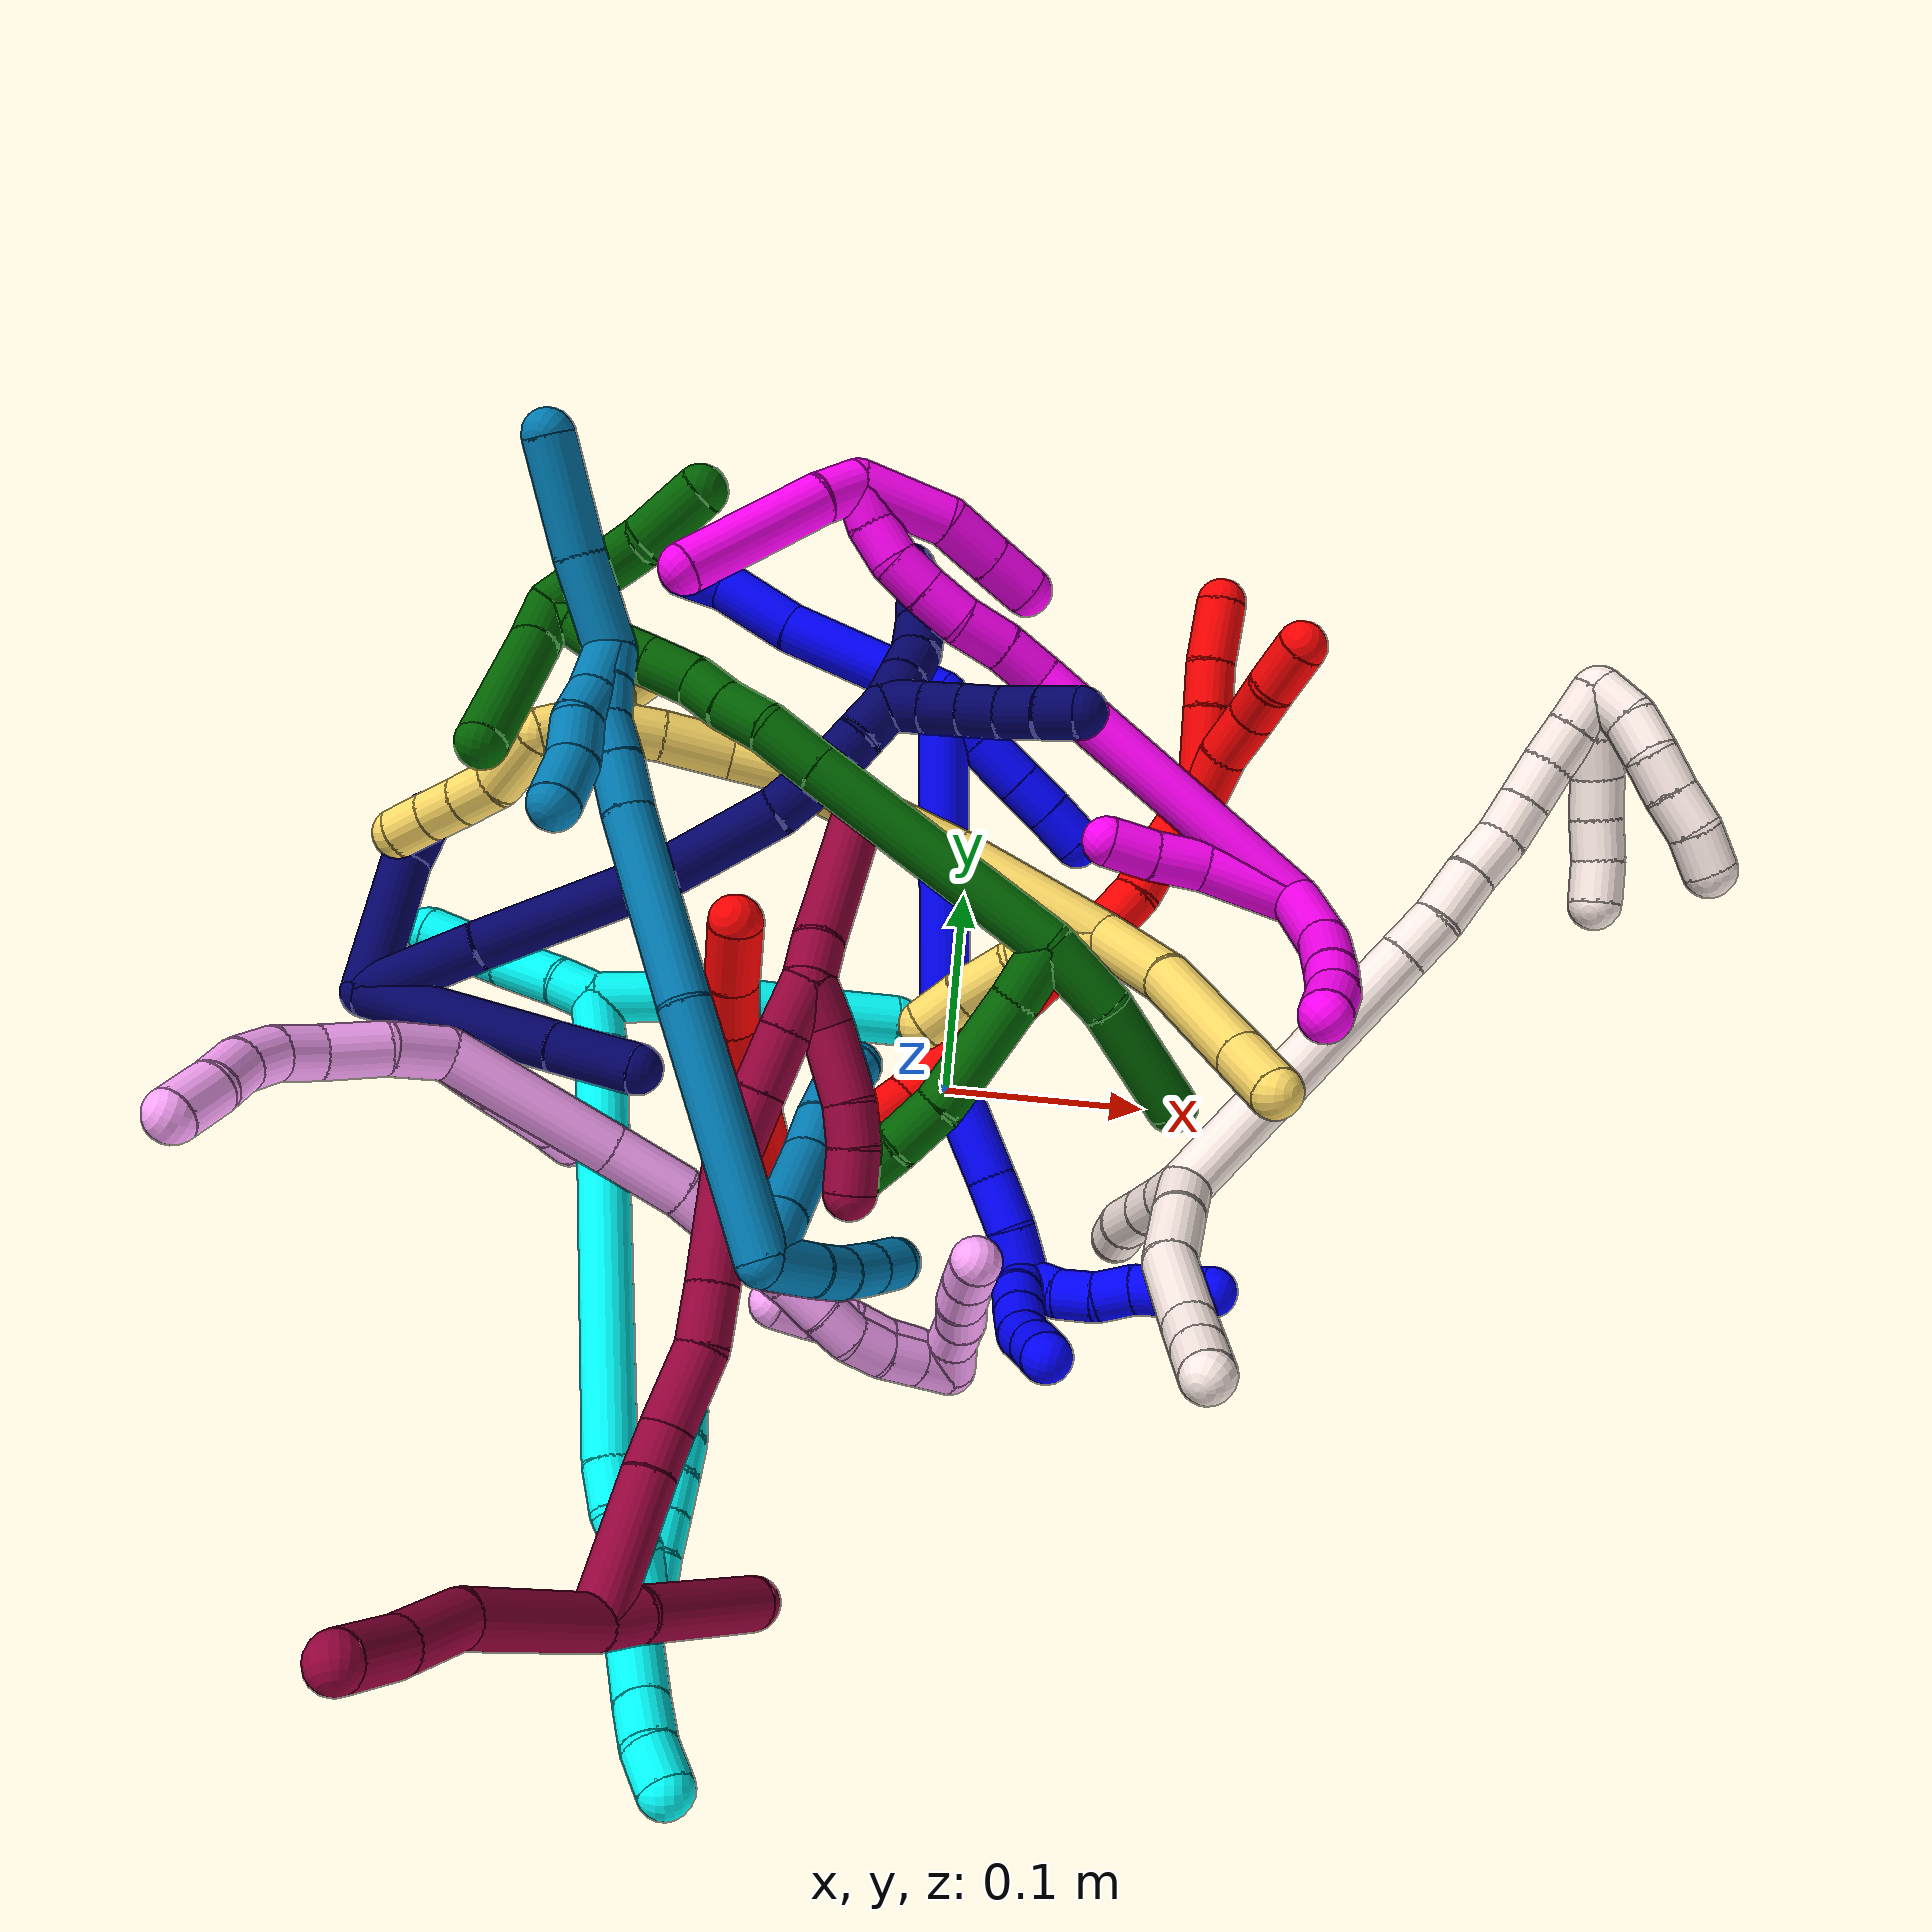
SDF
<sdf version="1.7">
 <world name="default">
  <plugin name="TubeGeneratorPlugin" filename="libtube_generator_plugin.so"/>
  <model name="photoneo_s_sensor">
   <static>1</static>
   <pose>0 0 2 1.57079 1.57079 3.14159</pose>
   <link name="link">
    <inertial><mass>0.1</mass></inertial>
    <sensor name="sensor" type="depth">
     <update_rate>30</update_rate>
     <camera>
      <horizontal_fov>1.22</horizontal_fov>
      <image><width>1920</width><height>1200</height><format>B8G8R8</format></image>
      <clip><near>0.1</near><far>4</far></clip>
      <depth_camera><output>points</output></depth_camera>
     </camera>
     <plugin name="camera_plugin" filename="libgazebo_ros_depth_camera.so">
      <baseline>0.2</baseline>
      <alwaysOn>1</alwaysOn>
      <updateRate>0.0</updateRate>
      <cameraName>camera_ir</cameraName>
      <imageTopicName>/camera/color/image_raw</imageTopicName>
      <cameraInfoTopicName>/camera/color/camera_info</cameraInfoTopicName>
      <depthImageTopicName>/camera/depth/image_raw</depthImageTopicName>
      <depthImageCameraInfoTopicName>/camera/depth/camera_info</depthImageCameraInfoTopicName>
      <pointCloudTopicName>/camera/depth/points</pointCloudTopicName>
      <frameName>fr_optical</frameName>
      <pointCloudCutoff>0.1</pointCloudCutoff>
      <pointCloudCutoffMax>2.0</pointCloudCutoffMax>
      <distortionK1>0</distortionK1>
      <distortionK2>0</distortionK2>
      <distortionK3>0</distortionK3>
      <distortionT1>0</distortionT1>
      <distortionT2>0</distortionT2>
      <CxPrime>0</CxPrime>
      <Cx>0</Cx>
      <Cy>0</Cy>
      <focalLength>0</focalLength>
      <hackBaseline>0</hackBaseline>
     </plugin>
    </sensor>
   </link>
  </model>
  <gravity>0 0 -9.8</gravity>
  <magnetic_field>6e-06 2.3e-05 -4.2e-05</magnetic_field>
  <atmosphere type="adiabatic"/>
  <physics name="default_physics" default="0" type="ode">
   <max_step_size>0.003</max_step_size>
   <real_time_factor>1</real_time_factor>
   <real_time_update_rate>1000</real_time_update_rate>
   <max_contacts>10000</max_contacts>
   <ode>
    <solver>
     <type>quick</type>
     <iters>100</iters>
     <sor>1.3</sor>
     <use_dynamic_moi_rescaling>0</use_dynamic_moi_rescaling>
    </solver>
    <constraints>
     <contact_max_correcting_vel>0</contact_max_correcting_vel>
     <contact_surface_layer>0.001</contact_surface_layer>
     <cfm>0</cfm>
     <erp>0.2</erp>
    </constraints>
   </ode>
  </physics>
  <scene><ambient>0.4 0.4 0.4 1</ambient><background>0.7 0.7 0.7 1</background><shadows>0</shadows></scene>
  <audio><device>default</device></audio>
  <spherical_coordinates>
   <surface_model>EARTH_WGS84</surface_model>
   <latitude_deg>0</latitude_deg>
   <longitude_deg>0</longitude_deg>
   <elevation>0</elevation>
   <heading_deg>0</heading_deg>
  </spherical_coordinates>
  <model name="bin">
   <static>1</static>
   <link name="bottom">
    <collision name="collision-bottom">
     <pose>0 0 -0.01 0 -0 0</pose>
     <geometry><box><size>0.8 0.6 0.02</size></box></geometry>
     <surface>
      <friction><ode><mu>100</mu><mu2>100</mu2></ode></friction>
      <contact><collide_bitmask>65535</collide_bitmask></contact>
     </surface>
    </collision>
   </link>
   <link name="west_wall">
    <collision name="collision-west_wall">
     <pose>-0.41 0 0.1 0 -0 0</pose>
     <geometry><box><size>0.02 0.6 0.2</size></box></geometry>
     <surface>
      <friction><ode><mu>100</mu><mu2>100</mu2></ode></friction>
      <contact><collide_bitmask>65535</collide_bitmask></contact>
     </surface>
    </collision>
   </link>
   <link name="east_wall">
    <collision name="collision-east_wall">
     <pose>0.41 0 0.1 0 -0 0</pose>
     <geometry><box><size>0.02 0.6 0.2</size></box></geometry>
     <surface>
      <friction><ode><mu>100</mu><mu2>100</mu2></ode></friction>
      <contact><collide_bitmask>65535</collide_bitmask></contact>
     </surface>
    </collision>
   </link>
   <link name="south_wall">
    <collision name="collision-south_wall">
     <pose>0 -0.31 0.1 0 -0 0</pose>
     <geometry><box><size>0.8 0.02 0.2</size></box></geometry>
     <surface>
      <friction><ode><mu>100</mu><mu2>100</mu2></ode></friction>
      <contact><collide_bitmask>65535</collide_bitmask></contact>
     </surface>
    </collision>
   </link>
   <link name="north_wall">
    <collision name="collision-north_wall">
     <pose>0 0.31 0.1 0 -0 0</pose>
     <geometry><box><size>0.8 0.02 0.2</size></box></geometry>
     <surface>
      <friction><ode><mu>100</mu><mu2>100</mu2></ode></friction>
      <contact><collide_bitmask>65535</collide_bitmask></contact>
     </surface>
    </collision>
   </link>
  </model>
  <model name="1">
   <static>0</static>
   <link name="1">
    <collision name="collision-cylinder-e_1_2_8">
     <pose>-0.000163 0.007735 0.042439 -0.180294 -0.003787 0.000342</pose>
     <geometry><cylinder><radius>0.0125</radius><length>0.086277</length></cylinder></geometry>
     <surface>
      <friction><ode><mu>1.16</mu><mu2>1.16</mu2><slip1>0</slip1><slip2>0</slip2></ode></friction>
      <contact><ode><kp>1e+06</kp><kd>1</kd><max_vel>0</max_vel><min_depth>0.001</min_depth></ode></contact>
     </surface>
    </collision>
    <visual name="visual-cylinder-e_1_2_8">
     <pose>-0.000163 0.007735 0.042439 -0.180294 -0.003787 0.000342</pose>
     <geometry><cylinder><radius>0.0125</radius><length>0.086277</length></cylinder></geometry>
     <material><ambient>0 0 1 1</ambient></material>
    </visual>
    <collision name="collision-cylinder-e_2_8_9">
     <pose>-0.000908 0.022022 0.104642 -0.320055 -0.027932 0.004509</pose>
     <geometry><cylinder><radius>0.0125</radius><length>0.041659</length></cylinder></geometry>
     <surface>
      <friction><ode><mu>1.16</mu><mu2>1.16</mu2><slip1>0</slip1><slip2>0</slip2></ode></friction>
      <contact><ode><kp>1e+06</kp><kd>1</kd><max_vel>0</max_vel><min_depth>0.001</min_depth></ode></contact>
     </surface>
    </collision>
    <visual name="visual-cylinder-e_2_8_9">
     <pose>-0.000908 0.022022 0.104642 -0.320055 -0.027932 0.004509</pose>
     <geometry><cylinder><radius>0.0125</radius><length>0.041659</length></cylinder></geometry>
     <material><ambient>0 0 1 1</ambient></material>
    </visual>
    <collision name="collision-cylinder-e_3_9_6">
     <pose>0.000438 0.030211 0.135144 -0.151407 0.175658 -0.013358</pose>
     <geometry><cylinder><radius>0.0125</radius><length>0.022064</length></cylinder></geometry>
     <surface>
      <friction><ode><mu>1.16</mu><mu2>1.16</mu2><slip1>0</slip1><slip2>0</slip2></ode></friction>
      <contact><ode><kp>1e+06</kp><kd>1</kd><max_vel>0</max_vel><min_depth>0.001</min_depth></ode></contact>
     </surface>
    </collision>
    <visual name="visual-cylinder-e_3_9_6">
     <pose>0.000438 0.030211 0.135144 -0.151407 0.175658 -0.013358</pose>
     <geometry><cylinder><radius>0.0125</radius><length>0.022064</length></cylinder></geometry>
     <material><ambient>0 0 1 1</ambient></material>
    </visual>
    <collision name="collision-cylinder-e_1_2_10">
     <pose>-0.001604 -0.009785 -0.010463 2.38966 -0.111513 -0.280928</pose>
     <geometry><cylinder><radius>0.0125</radius><length>0.028831</length></cylinder></geometry>
     <surface>
      <friction><ode><mu>1.16</mu><mu2>1.16</mu2><slip1>0</slip1><slip2>0</slip2></ode></friction>
      <contact><ode><kp>1e+06</kp><kd>1</kd><max_vel>0</max_vel><min_depth>0.001</min_depth></ode></contact>
     </surface>
    </collision>
    <visual name="visual-cylinder-e_1_2_10">
     <pose>-0.001604 -0.009785 -0.010463 2.38966 -0.111513 -0.280928</pose>
     <geometry><cylinder><radius>0.0125</radius><length>0.028831</length></cylinder></geometry>
     <material><ambient>0 0 1 1</ambient></material>
    </visual>
    <collision name="collision-cylinder-e_2_10_11">
     <pose>-0.004392 -0.027812 -0.03261 2.52726 -0.082565 -0.258978</pose>
     <geometry><cylinder><radius>0.0125</radius><length>0.028694</length></cylinder></geometry>
     <surface>
      <friction><ode><mu>1.16</mu><mu2>1.16</mu2><slip1>0</slip1><slip2>0</slip2></ode></friction>
      <contact><ode><kp>1e+06</kp><kd>1</kd><max_vel>0</max_vel><min_depth>0.001</min_depth></ode></contact>
     </surface>
    </collision>
    <visual name="visual-cylinder-e_2_10_11">
     <pose>-0.004392 -0.027812 -0.03261 2.52726 -0.082565 -0.258978</pose>
     <geometry><cylinder><radius>0.0125</radius><length>0.028694</length></cylinder></geometry>
     <material><ambient>0 0 1 1</ambient></material>
    </visual>
    <collision name="collision-cylinder-e_3_11_12">
     <pose>-0.00658 -0.042012 -0.052735 2.52696 -0.096971 -0.303434</pose>
     <geometry><cylinder><radius>0.0125</radius><length>0.020761</length></cylinder></geometry>
     <surface>
      <friction><ode><mu>1.16</mu><mu2>1.16</mu2><slip1>0</slip1><slip2>0</slip2></ode></friction>
      <contact><ode><kp>1e+06</kp><kd>1</kd><max_vel>0</max_vel><min_depth>0.001</min_depth></ode></contact>
     </surface>
    </collision>
    <visual name="visual-cylinder-e_3_11_12">
     <pose>-0.00658 -0.042012 -0.052735 2.52696 -0.096971 -0.303434</pose>
     <geometry><cylinder><radius>0.0125</radius><length>0.020761</length></cylinder></geometry>
     <material><ambient>0 0 1 1</ambient></material>
    </visual>
    <collision name="collision-cylinder-e_4_12_5">
     <pose>-0.008631 -0.054658 -0.069663 2.47416 -0.09652 -0.276844</pose>
     <geometry><cylinder><radius>0.0125</radius><length>0.021714</length></cylinder></geometry>
     <surface>
      <friction><ode><mu>1.16</mu><mu2>1.16</mu2><slip1>0</slip1><slip2>0</slip2></ode></friction>
      <contact><ode><kp>1e+06</kp><kd>1</kd><max_vel>0</max_vel><min_depth>0.001</min_depth></ode></contact>
     </surface>
    </collision>
    <visual name="visual-cylinder-e_4_12_5">
     <pose>-0.008631 -0.054658 -0.069663 2.47416 -0.09652 -0.276844</pose>
     <geometry><cylinder><radius>0.0125</radius><length>0.021714</length></cylinder></geometry>
     <material><ambient>0 0 1 1</ambient></material>
    </visual>
    <collision name="collision-cylinder-e_1_2_13">
     <pose>0.027608 -0.079701 -0.022241 1.84293 0.322038 0.421556</pose>
     <geometry><cylinder><radius>0.0125</radius><length>0.17446</length></cylinder></geometry>
     <surface>
      <friction><ode><mu>1.16</mu><mu2>1.16</mu2><slip1>0</slip1><slip2>0</slip2></ode></friction>
      <contact><ode><kp>1e+06</kp><kd>1</kd><max_vel>0</max_vel><min_depth>0.001</min_depth></ode></contact>
     </surface>
    </collision>
    <visual name="visual-cylinder-e_1_2_13">
     <pose>0.027608 -0.079701 -0.022241 1.84293 0.322038 0.421556</pose>
     <geometry><cylinder><radius>0.0125</radius><length>0.17446</length></cylinder></geometry>
     <material><ambient>0 0 1 1</ambient></material>
    </visual>
    <collision name="collision-cylinder-e_2_13_14">
     <pose>0.059821 -0.170674 -0.051588 2.1333 0.3327 0.590862</pose>
     <geometry><cylinder><radius>0.0125</radius><length>0.028197</length></cylinder></geometry>
     <surface>
      <friction><ode><mu>1.16</mu><mu2>1.16</mu2><slip1>0</slip1><slip2>0</slip2></ode></friction>
      <contact><ode><kp>1e+06</kp><kd>1</kd><max_vel>0</max_vel><min_depth>0.001</min_depth></ode></contact>
     </surface>
    </collision>
    <visual name="visual-cylinder-e_2_13_14">
     <pose>0.059821 -0.170674 -0.051588 2.1333 0.3327 0.590862</pose>
     <geometry><cylinder><radius>0.0125</radius><length>0.028197</length></cylinder></geometry>
     <material><ambient>0 0 1 1</ambient></material>
    </visual>
    <collision name="collision-cylinder-e_3_14_15">
     <pose>0.070504 -0.197557 -0.071947 2.27464 0.288553 0.608328</pose>
     <geometry><cylinder><radius>0.0125</radius><length>0.042722</length></cylinder></geometry>
     <surface>
      <friction><ode><mu>1.16</mu><mu2>1.16</mu2><slip1>0</slip1><slip2>0</slip2></ode></friction>
      <contact><ode><kp>1e+06</kp><kd>1</kd><max_vel>0</max_vel><min_depth>0.001</min_depth></ode></contact>
     </surface>
    </collision>
    <visual name="visual-cylinder-e_3_14_15">
     <pose>0.070504 -0.197557 -0.071947 2.27464 0.288553 0.608328</pose>
     <geometry><cylinder><radius>0.0125</radius><length>0.042722</length></cylinder></geometry>
     <material><ambient>0 0 1 1</ambient></material>
    </visual>
    <collision name="collision-cylinder-e_4_15_16">
     <pose>0.081392 -0.222743 -0.093694 2.29654 0.359391 0.767954</pose>
     <geometry><cylinder><radius>0.0125</radius><length>0.027347</length></cylinder></geometry>
     <surface>
      <friction><ode><mu>1.16</mu><mu2>1.16</mu2><slip1>0</slip1><slip2>0</slip2></ode></friction>
      <contact><ode><kp>1e+06</kp><kd>1</kd><max_vel>0</max_vel><min_depth>0.001</min_depth></ode></contact>
     </surface>
    </collision>
    <visual name="visual-cylinder-e_4_15_16">
     <pose>0.081392 -0.222743 -0.093694 2.29654 0.359391 0.767954</pose>
     <geometry><cylinder><radius>0.0125</radius><length>0.027347</length></cylinder></geometry>
     <material><ambient>0 0 1 1</ambient></material>
    </visual>
    <collision name="collision-cylinder-e_5_16_1">
     <pose>0.090024 -0.243426 -0.109114 2.12826 0.284156 0.504497</pose>
     <geometry><cylinder><radius>0.0125</radius><length>0.027275</length></cylinder></geometry>
     <surface>
      <friction><ode><mu>1.16</mu><mu2>1.16</mu2><slip1>0</slip1><slip2>0</slip2></ode></friction>
      <contact><ode><kp>1e+06</kp><kd>1</kd><max_vel>0</max_vel><min_depth>0.001</min_depth></ode></contact>
     </surface>
    </collision>
    <visual name="visual-cylinder-e_5_16_1">
     <pose>0.090024 -0.243426 -0.109114 2.12826 0.284156 0.504497</pose>
     <geometry><cylinder><radius>0.0125</radius><length>0.027275</length></cylinder></geometry>
     <material><ambient>0 0 1 1</ambient></material>
    </visual>
    <collision name="collision-cylinder-e_1_1_17">
     <pose>0.103568 -0.252369 -0.116946 -1.96712 1.33387 -1.73796</pose>
     <geometry><cylinder><radius>0.0125</radius><length>0.02</length></cylinder></geometry>
     <surface>
      <friction><ode><mu>1.16</mu><mu2>1.16</mu2><slip1>0</slip1><slip2>0</slip2></ode></friction>
      <contact><ode><kp>1e+06</kp><kd>1</kd><max_vel>0</max_vel><min_depth>0.001</min_depth></ode></contact>
     </surface>
    </collision>
    <visual name="visual-cylinder-e_1_1_17">
     <pose>0.103568 -0.252369 -0.116946 -1.96712 1.33387 -1.73796</pose>
     <geometry><cylinder><radius>0.0125</radius><length>0.02</length></cylinder></geometry>
     <material><ambient>0 0 1 1</ambient></material>
    </visual>
    <collision name="collision-cylinder-e_2_17_18">
     <pose>0.12258 -0.2497 -0.121513 -3.00495 1.19228 -2.94056</pose>
     <geometry><cylinder><radius>0.0125</radius><length>0.02</length></cylinder></geometry>
     <surface>
      <friction><ode><mu>1.16</mu><mu2>1.16</mu2><slip1>0</slip1><slip2>0</slip2></ode></friction>
      <contact><ode><kp>1e+06</kp><kd>1</kd><max_vel>0</max_vel><min_depth>0.001</min_depth></ode></contact>
     </surface>
    </collision>
    <visual name="visual-cylinder-e_2_17_18">
     <pose>0.12258 -0.2497 -0.121513 -3.00495 1.19228 -2.94056</pose>
     <geometry><cylinder><radius>0.0125</radius><length>0.02</length></cylinder></geometry>
     <material><ambient>0 0 1 1</ambient></material>
    </visual>
    <collision name="collision-cylinder-e_3_18_19">
     <pose>0.141009 -0.24881 -0.12922 -3.04622 1.15223 -2.99493</pose>
     <geometry><cylinder><radius>0.0125</radius><length>0.02</length></cylinder></geometry>
     <surface>
      <friction><ode><mu>1.16</mu><mu2>1.16</mu2><slip1>0</slip1><slip2>0</slip2></ode></friction>
      <contact><ode><kp>1e+06</kp><kd>1</kd><max_vel>0</max_vel><min_depth>0.001</min_depth></ode></contact>
     </surface>
    </collision>
    <visual name="visual-cylinder-e_3_18_19">
     <pose>0.141009 -0.24881 -0.12922 -3.04622 1.15223 -2.99493</pose>
     <geometry><cylinder><radius>0.0125</radius><length>0.02</length></cylinder></geometry>
     <material><ambient>0 0 1 1</ambient></material>
    </visual>
    <collision name="collision-cylinder-e_4_19_20">
     <pose>0.157939 -0.24521 -0.138646 -2.60326 0.893497 -2.09666</pose>
     <geometry><cylinder><radius>0.0125</radius><length>0.02</length></cylinder></geometry>
     <surface>
      <friction><ode><mu>1.16</mu><mu2>1.16</mu2><slip1>0</slip1><slip2>0</slip2></ode></friction>
      <contact><ode><kp>1e+06</kp><kd>1</kd><max_vel>0</max_vel><min_depth>0.001</min_depth></ode></contact>
     </surface>
    </collision>
    <visual name="visual-cylinder-e_4_19_20">
     <pose>0.157939 -0.24521 -0.138646 -2.60326 0.893497 -2.09666</pose>
     <geometry><cylinder><radius>0.0125</radius><length>0.02</length></cylinder></geometry>
     <material><ambient>0 0 1 1</ambient></material>
    </visual>
    <collision name="collision-cylinder-e_5_20_4">
     <pose>0.173818 -0.238978 -0.149076 -2.60281 0.941847 -2.14776</pose>
     <geometry><cylinder><radius>0.0125</radius><length>0.02</length></cylinder></geometry>
     <surface>
      <friction><ode><mu>1.16</mu><mu2>1.16</mu2><slip1>0</slip1><slip2>0</slip2></ode></friction>
      <contact><ode><kp>1e+06</kp><kd>1</kd><max_vel>0</max_vel><min_depth>0.001</min_depth></ode></contact>
     </surface>
    </collision>
    <visual name="visual-cylinder-e_5_20_4">
     <pose>0.173818 -0.238978 -0.149076 -2.60281 0.941847 -2.14776</pose>
     <geometry><cylinder><radius>0.0125</radius><length>0.02</length></cylinder></geometry>
     <material><ambient>0 0 1 1</ambient></material>
    </visual>
    <collision name="collision-cylinder-e_1_1_21">
     <pose>0.096612 -0.253384 -0.125581 -3.0216 0.280194 -2.33621</pose>
     <geometry><cylinder><radius>0.0125</radius><length>0.02</length></cylinder></geometry>
     <surface>
      <friction><ode><mu>1.16</mu><mu2>1.16</mu2><slip1>0</slip1><slip2>0</slip2></ode></friction>
      <contact><ode><kp>1e+06</kp><kd>1</kd><max_vel>0</max_vel><min_depth>0.001</min_depth></ode></contact>
     </surface>
    </collision>
    <visual name="visual-cylinder-e_1_1_21">
     <pose>0.096612 -0.253384 -0.125581 -3.0216 0.280194 -2.33621</pose>
     <geometry><cylinder><radius>0.0125</radius><length>0.02</length></cylinder></geometry>
     <material><ambient>0 0 1 1</ambient></material>
    </visual>
    <collision name="collision-cylinder-e_2_21_22">
     <pose>0.099712 -0.249768 -0.144807 -2.89232 0.033453 -0.265466</pose>
     <geometry><cylinder><radius>0.0125</radius><length>0.02</length></cylinder></geometry>
     <surface>
      <friction><ode><mu>1.16</mu><mu2>1.16</mu2><slip1>0</slip1><slip2>0</slip2></ode></friction>
      <contact><ode><kp>1e+06</kp><kd>1</kd><max_vel>0</max_vel><min_depth>0.001</min_depth></ode></contact>
     </surface>
    </collision>
    <visual name="visual-cylinder-e_2_21_22">
     <pose>0.099712 -0.249768 -0.144807 -2.89232 0.033453 -0.265466</pose>
     <geometry><cylinder><radius>0.0125</radius><length>0.02</length></cylinder></geometry>
     <material><ambient>0 0 1 1</ambient></material>
    </visual>
    <collision name="collision-cylinder-e_3_22_23">
     <pose>0.098088 -0.242996 -0.163303 -2.68698 -0.197187 0.80821</pose>
     <geometry><cylinder><radius>0.0125</radius><length>0.02</length></cylinder></geometry>
     <surface>
      <friction><ode><mu>1.16</mu><mu2>1.16</mu2><slip1>0</slip1><slip2>0</slip2></ode></friction>
      <contact><ode><kp>1e+06</kp><kd>1</kd><max_vel>0</max_vel><min_depth>0.001</min_depth></ode></contact>
     </surface>
    </collision>
    <visual name="visual-cylinder-e_3_22_23">
     <pose>0.098088 -0.242996 -0.163303 -2.68698 -0.197187 0.80821</pose>
     <geometry><cylinder><radius>0.0125</radius><length>0.02</length></cylinder></geometry>
     <material><ambient>0 0 1 1</ambient></material>
    </visual>
    <collision name="collision-cylinder-e_4_23_24">
     <pose>0.097349 -0.235458 -0.181497 -2.80993 0.122336 -0.701585</pose>
     <geometry><cylinder><radius>0.0125</radius><length>0.02</length></cylinder></geometry>
     <surface>
      <friction><ode><mu>1.16</mu><mu2>1.16</mu2><slip1>0</slip1><slip2>0</slip2></ode></friction>
      <contact><ode><kp>1e+06</kp><kd>1</kd><max_vel>0</max_vel><min_depth>0.001</min_depth></ode></contact>
     </surface>
    </collision>
    <visual name="visual-cylinder-e_4_23_24">
     <pose>0.097349 -0.235458 -0.181497 -2.80993 0.122336 -0.701585</pose>
     <geometry><cylinder><radius>0.0125</radius><length>0.02</length></cylinder></geometry>
     <material><ambient>0 0 1 1</ambient></material>
    </visual>
    <collision name="collision-cylinder-e_5_24_3">
     <pose>0.099402 -0.22871 -0.200206 -2.78097 0.083356 -0.449795</pose>
     <geometry><cylinder><radius>0.0125</radius><length>0.02</length></cylinder></geometry>
     <surface>
      <friction><ode><mu>1.16</mu><mu2>1.16</mu2><slip1>0</slip1><slip2>0</slip2></ode></friction>
      <contact><ode><kp>1e+06</kp><kd>1</kd><max_vel>0</max_vel><min_depth>0.001</min_depth></ode></contact>
     </surface>
    </collision>
    <visual name="visual-cylinder-e_5_24_3">
     <pose>0.099402 -0.22871 -0.200206 -2.78097 0.083356 -0.449795</pose>
     <geometry><cylinder><radius>0.0125</radius><length>0.02</length></cylinder></geometry>
     <material><ambient>0 0 1 1</ambient></material>
    </visual>
    <collision name="collision-sphere-3">
     <pose>0.100234 -0.225194 -0.20953 0 -0 0</pose>
     <geometry><sphere><radius>0.0125</radius></sphere></geometry>
     <surface>
      <friction><ode><mu>1.16</mu><mu2>1.16</mu2><slip1>0</slip1><slip2>0</slip2></ode></friction>
      <contact><ode><kp>1e+06</kp><kd>1</kd><max_vel>0</max_vel><min_depth>0.001</min_depth></ode></contact>
     </surface>
    </collision>
    <visual name="visual-sphere-3">
     <pose>0.100234 -0.225194 -0.20953 0 -0 0</pose>
     <geometry><sphere><radius>0.0125</radius></sphere></geometry>
     <material><ambient>0 0 1 1</ambient></material>
    </visual>
    <collision name="collision-sphere-24">
     <pose>0.098569 -0.232227 -0.190882 0 -0 0</pose>
     <geometry><sphere><radius>0.0125</radius></sphere></geometry>
     <surface>
      <friction><ode><mu>1.16</mu><mu2>1.16</mu2><slip1>0</slip1><slip2>0</slip2></ode></friction>
      <contact><ode><kp>1e+06</kp><kd>1</kd><max_vel>0</max_vel><min_depth>0.001</min_depth></ode></contact>
     </surface>
    </collision>
    <visual name="visual-sphere-24">
     <pose>0.098569 -0.232227 -0.190882 0 -0 0</pose>
     <geometry><sphere><radius>0.0125</radius></sphere></geometry>
     <material><ambient>0 0 1 1</ambient></material>
    </visual>
    <collision name="collision-sphere-23">
     <pose>0.096129 -0.23869 -0.172113 0 -0 0</pose>
     <geometry><sphere><radius>0.0125</radius></sphere></geometry>
     <surface>
      <friction><ode><mu>1.16</mu><mu2>1.16</mu2><slip1>0</slip1><slip2>0</slip2></ode></friction>
      <contact><ode><kp>1e+06</kp><kd>1</kd><max_vel>0</max_vel><min_depth>0.001</min_depth></ode></contact>
     </surface>
    </collision>
    <visual name="visual-sphere-23">
     <pose>0.096129 -0.23869 -0.172113 0 -0 0</pose>
     <geometry><sphere><radius>0.0125</radius></sphere></geometry>
     <material><ambient>0 0 1 1</ambient></material>
    </visual>
    <collision name="collision-sphere-22">
     <pose>0.100047 -0.247302 -0.154493 0 -0 0</pose>
     <geometry><sphere><radius>0.0125</radius></sphere></geometry>
     <surface>
      <friction><ode><mu>1.16</mu><mu2>1.16</mu2><slip1>0</slip1><slip2>0</slip2></ode></friction>
      <contact><ode><kp>1e+06</kp><kd>1</kd><max_vel>0</max_vel><min_depth>0.001</min_depth></ode></contact>
     </surface>
    </collision>
    <visual name="visual-sphere-22">
     <pose>0.100047 -0.247302 -0.154493 0 -0 0</pose>
     <geometry><sphere><radius>0.0125</radius></sphere></geometry>
     <material><ambient>0 0 1 1</ambient></material>
    </visual>
    <collision name="collision-sphere-21">
     <pose>0.099378 -0.252234 -0.135122 0 -0 0</pose>
     <geometry><sphere><radius>0.0125</radius></sphere></geometry>
     <surface>
      <friction><ode><mu>1.16</mu><mu2>1.16</mu2><slip1>0</slip1><slip2>0</slip2></ode></friction>
      <contact><ode><kp>1e+06</kp><kd>1</kd><max_vel>0</max_vel><min_depth>0.001</min_depth></ode></contact>
     </surface>
    </collision>
    <visual name="visual-sphere-21">
     <pose>0.099378 -0.252234 -0.135122 0 -0 0</pose>
     <geometry><sphere><radius>0.0125</radius></sphere></geometry>
     <material><ambient>0 0 1 1</ambient></material>
    </visual>
    <collision name="collision-sphere-4">
     <pose>0.181904 -0.23596 -0.154126 0 -0 0</pose>
     <geometry><sphere><radius>0.0125</radius></sphere></geometry>
     <surface>
      <friction><ode><mu>1.16</mu><mu2>1.16</mu2><slip1>0</slip1><slip2>0</slip2></ode></friction>
      <contact><ode><kp>1e+06</kp><kd>1</kd><max_vel>0</max_vel><min_depth>0.001</min_depth></ode></contact>
     </surface>
    </collision>
    <visual name="visual-sphere-4">
     <pose>0.181904 -0.23596 -0.154126 0 -0 0</pose>
     <geometry><sphere><radius>0.0125</radius></sphere></geometry>
     <material><ambient>0 0 1 1</ambient></material>
    </visual>
    <collision name="collision-sphere-20">
     <pose>0.165731 -0.241997 -0.144027 0 -0 0</pose>
     <geometry><sphere><radius>0.0125</radius></sphere></geometry>
     <surface>
      <friction><ode><mu>1.16</mu><mu2>1.16</mu2><slip1>0</slip1><slip2>0</slip2></ode></friction>
      <contact><ode><kp>1e+06</kp><kd>1</kd><max_vel>0</max_vel><min_depth>0.001</min_depth></ode></contact>
     </surface>
    </collision>
    <visual name="visual-sphere-20">
     <pose>0.165731 -0.241997 -0.144027 0 -0 0</pose>
     <geometry><sphere><radius>0.0125</radius></sphere></geometry>
     <material><ambient>0 0 1 1</ambient></material>
    </visual>
    <collision name="collision-sphere-11">
     <pose>-0.005575 -0.036054 -0.044294 0 -0 0</pose>
     <geometry><sphere><radius>0.0125</radius></sphere></geometry>
     <surface>
      <friction><ode><mu>1.16</mu><mu2>1.16</mu2><slip1>0</slip1><slip2>0</slip2></ode></friction>
      <contact><ode><kp>1e+06</kp><kd>1</kd><max_vel>0</max_vel><min_depth>0.001</min_depth></ode></contact>
     </surface>
    </collision>
    <visual name="visual-sphere-11">
     <pose>-0.005575 -0.036054 -0.044294 0 -0 0</pose>
     <geometry><sphere><radius>0.0125</radius></sphere></geometry>
     <material><ambient>0 0 1 1</ambient></material>
    </visual>
    <collision name="collision-sphere-10">
     <pose>-0.003208 -0.01957 -0.020926 0 -0 0</pose>
     <geometry><sphere><radius>0.0125</radius></sphere></geometry>
     <surface>
      <friction><ode><mu>1.16</mu><mu2>1.16</mu2><slip1>0</slip1><slip2>0</slip2></ode></friction>
      <contact><ode><kp>1e+06</kp><kd>1</kd><max_vel>0</max_vel><min_depth>0.001</min_depth></ode></contact>
     </surface>
    </collision>
    <visual name="visual-sphere-10">
     <pose>-0.003208 -0.01957 -0.020926 0 -0 0</pose>
     <geometry><sphere><radius>0.0125</radius></sphere></geometry>
     <material><ambient>0 0 1 1</ambient></material>
    </visual>
    <collision name="collision-sphere-6">
     <pose>0.002366 0.031849 0.145882 0 -0 0</pose>
     <geometry><sphere><radius>0.0125</radius></sphere></geometry>
     <surface>
      <friction><ode><mu>1.16</mu><mu2>1.16</mu2><slip1>0</slip1><slip2>0</slip2></ode></friction>
      <contact><ode><kp>1e+06</kp><kd>1</kd><max_vel>0</max_vel><min_depth>0.001</min_depth></ode></contact>
     </surface>
    </collision>
    <visual name="visual-sphere-6">
     <pose>0.002366 0.031849 0.145882 0 -0 0</pose>
     <geometry><sphere><radius>0.0125</radius></sphere></geometry>
     <material><ambient>0 0 1 1</ambient></material>
    </visual>
    <collision name="collision-sphere-9">
     <pose>-0.00149 0.028572 0.124406 0 -0 0</pose>
     <geometry><sphere><radius>0.0125</radius></sphere></geometry>
     <surface>
      <friction><ode><mu>1.16</mu><mu2>1.16</mu2><slip1>0</slip1><slip2>0</slip2></ode></friction>
      <contact><ode><kp>1e+06</kp><kd>1</kd><max_vel>0</max_vel><min_depth>0.001</min_depth></ode></contact>
     </surface>
    </collision>
    <visual name="visual-sphere-9">
     <pose>-0.00149 0.028572 0.124406 0 -0 0</pose>
     <geometry><sphere><radius>0.0125</radius></sphere></geometry>
     <material><ambient>0 0 1 1</ambient></material>
    </visual>
    <collision name="collision-sphere-2">
     <geometry><sphere><radius>0.0125</radius></sphere></geometry>
     <surface>
      <friction><ode><mu>1.16</mu><mu2>1.16</mu2><slip1>0</slip1><slip2>0</slip2></ode></friction>
      <contact><ode><kp>1e+06</kp><kd>1</kd><max_vel>0</max_vel><min_depth>0.001</min_depth></ode></contact>
     </surface>
    </collision>
    <visual name="visual-sphere-2">
     <geometry><sphere><radius>0.0125</radius></sphere></geometry>
     <material><ambient>0 0 1 1</ambient></material>
    </visual>
    <collision name="collision-sphere-19">
     <pose>0.150146 -0.248423 -0.133266 0 -0 0</pose>
     <geometry><sphere><radius>0.0125</radius></sphere></geometry>
     <surface>
      <friction><ode><mu>1.16</mu><mu2>1.16</mu2><slip1>0</slip1><slip2>0</slip2></ode></friction>
      <contact><ode><kp>1e+06</kp><kd>1</kd><max_vel>0</max_vel><min_depth>0.001</min_depth></ode></contact>
     </surface>
    </collision>
    <visual name="visual-sphere-19">
     <pose>0.150146 -0.248423 -0.133266 0 -0 0</pose>
     <geometry><sphere><radius>0.0125</radius></sphere></geometry>
     <material><ambient>0 0 1 1</ambient></material>
    </visual>
    <collision name="collision-sphere-8">
     <pose>-0.000327 0.015471 0.084878 0 -0 0</pose>
     <geometry><sphere><radius>0.0125</radius></sphere></geometry>
     <surface>
      <friction><ode><mu>1.16</mu><mu2>1.16</mu2><slip1>0</slip1><slip2>0</slip2></ode></friction>
      <contact><ode><kp>1e+06</kp><kd>1</kd><max_vel>0</max_vel><min_depth>0.001</min_depth></ode></contact>
     </surface>
    </collision>
    <visual name="visual-sphere-8">
     <pose>-0.000327 0.015471 0.084878 0 -0 0</pose>
     <geometry><sphere><radius>0.0125</radius></sphere></geometry>
     <material><ambient>0 0 1 1</ambient></material>
    </visual>
    <collision name="collision-sphere-12">
     <pose>-0.007585 -0.047969 -0.061176 0 -0 0</pose>
     <geometry><sphere><radius>0.0125</radius></sphere></geometry>
     <surface>
      <friction><ode><mu>1.16</mu><mu2>1.16</mu2><slip1>0</slip1><slip2>0</slip2></ode></friction>
      <contact><ode><kp>1e+06</kp><kd>1</kd><max_vel>0</max_vel><min_depth>0.001</min_depth></ode></contact>
     </surface>
    </collision>
    <visual name="visual-sphere-12">
     <pose>-0.007585 -0.047969 -0.061176 0 -0 0</pose>
     <geometry><sphere><radius>0.0125</radius></sphere></geometry>
     <material><ambient>0 0 1 1</ambient></material>
    </visual>
    <collision name="collision-sphere-5">
     <pose>-0.009677 -0.061348 -0.078151 0 -0 0</pose>
     <geometry><sphere><radius>0.0125</radius></sphere></geometry>
     <surface>
      <friction><ode><mu>1.16</mu><mu2>1.16</mu2><slip1>0</slip1><slip2>0</slip2></ode></friction>
      <contact><ode><kp>1e+06</kp><kd>1</kd><max_vel>0</max_vel><min_depth>0.001</min_depth></ode></contact>
     </surface>
    </collision>
    <visual name="visual-sphere-5">
     <pose>-0.009677 -0.061348 -0.078151 0 -0 0</pose>
     <geometry><sphere><radius>0.0125</radius></sphere></geometry>
     <material><ambient>0 0 1 1</ambient></material>
    </visual>
    <collision name="collision-sphere-13">
     <pose>0.055217 -0.159402 -0.044481 0 -0 0</pose>
     <geometry><sphere><radius>0.0125</radius></sphere></geometry>
     <surface>
      <friction><ode><mu>1.16</mu><mu2>1.16</mu2><slip1>0</slip1><slip2>0</slip2></ode></friction>
      <contact><ode><kp>1e+06</kp><kd>1</kd><max_vel>0</max_vel><min_depth>0.001</min_depth></ode></contact>
     </surface>
    </collision>
    <visual name="visual-sphere-13">
     <pose>0.055217 -0.159402 -0.044481 0 -0 0</pose>
     <geometry><sphere><radius>0.0125</radius></sphere></geometry>
     <material><ambient>0 0 1 1</ambient></material>
    </visual>
    <collision name="collision-sphere-14">
     <pose>0.064426 -0.181946 -0.058694 0 -0 0</pose>
     <geometry><sphere><radius>0.0125</radius></sphere></geometry>
     <surface>
      <friction><ode><mu>1.16</mu><mu2>1.16</mu2><slip1>0</slip1><slip2>0</slip2></ode></friction>
      <contact><ode><kp>1e+06</kp><kd>1</kd><max_vel>0</max_vel><min_depth>0.001</min_depth></ode></contact>
     </surface>
    </collision>
    <visual name="visual-sphere-14">
     <pose>0.064426 -0.181946 -0.058694 0 -0 0</pose>
     <geometry><sphere><radius>0.0125</radius></sphere></geometry>
     <material><ambient>0 0 1 1</ambient></material>
    </visual>
    <collision name="collision-sphere-15">
     <pose>0.076583 -0.213169 -0.085199 0 -0 0</pose>
     <geometry><sphere><radius>0.0125</radius></sphere></geometry>
     <surface>
      <friction><ode><mu>1.16</mu><mu2>1.16</mu2><slip1>0</slip1><slip2>0</slip2></ode></friction>
      <contact><ode><kp>1e+06</kp><kd>1</kd><max_vel>0</max_vel><min_depth>0.001</min_depth></ode></contact>
     </surface>
    </collision>
    <visual name="visual-sphere-15">
     <pose>0.076583 -0.213169 -0.085199 0 -0 0</pose>
     <geometry><sphere><radius>0.0125</radius></sphere></geometry>
     <material><ambient>0 0 1 1</ambient></material>
    </visual>
    <collision name="collision-sphere-16">
     <pose>0.086201 -0.232317 -0.102189 0 -0 0</pose>
     <geometry><sphere><radius>0.0125</radius></sphere></geometry>
     <surface>
      <friction><ode><mu>1.16</mu><mu2>1.16</mu2><slip1>0</slip1><slip2>0</slip2></ode></friction>
      <contact><ode><kp>1e+06</kp><kd>1</kd><max_vel>0</max_vel><min_depth>0.001</min_depth></ode></contact>
     </surface>
    </collision>
    <visual name="visual-sphere-16">
     <pose>0.086201 -0.232317 -0.102189 0 -0 0</pose>
     <geometry><sphere><radius>0.0125</radius></sphere></geometry>
     <material><ambient>0 0 1 1</ambient></material>
    </visual>
    <collision name="collision-sphere-1">
     <pose>0.093847 -0.254534 -0.11604 0 -0 0</pose>
     <geometry><sphere><radius>0.0125</radius></sphere></geometry>
     <surface>
      <friction><ode><mu>1.16</mu><mu2>1.16</mu2><slip1>0</slip1><slip2>0</slip2></ode></friction>
      <contact><ode><kp>1e+06</kp><kd>1</kd><max_vel>0</max_vel><min_depth>0.001</min_depth></ode></contact>
     </surface>
    </collision>
    <visual name="visual-sphere-1">
     <pose>0.093847 -0.254534 -0.11604 0 -0 0</pose>
     <geometry><sphere><radius>0.0125</radius></sphere></geometry>
     <material><ambient>0 0 1 1</ambient></material>
    </visual>
    <collision name="collision-sphere-18">
     <pose>0.131873 -0.249197 -0.125174 0 -0 0</pose>
     <geometry><sphere><radius>0.0125</radius></sphere></geometry>
     <surface>
      <friction><ode><mu>1.16</mu><mu2>1.16</mu2><slip1>0</slip1><slip2>0</slip2></ode></friction>
      <contact><ode><kp>1e+06</kp><kd>1</kd><max_vel>0</max_vel><min_depth>0.001</min_depth></ode></contact>
     </surface>
    </collision>
    <visual name="visual-sphere-18">
     <pose>0.131873 -0.249197 -0.125174 0 -0 0</pose>
     <geometry><sphere><radius>0.0125</radius></sphere></geometry>
     <material><ambient>0 0 1 1</ambient></material>
    </visual>
    <collision name="collision-sphere-17">
     <pose>0.113288 -0.250204 -0.117852 0 -0 0</pose>
     <geometry><sphere><radius>0.0125</radius></sphere></geometry>
     <surface>
      <friction><ode><mu>1.16</mu><mu2>1.16</mu2><slip1>0</slip1><slip2>0</slip2></ode></friction>
      <contact><ode><kp>1e+06</kp><kd>1</kd><max_vel>0</max_vel><min_depth>0.001</min_depth></ode></contact>
     </surface>
    </collision>
    <visual name="visual-sphere-17">
     <pose>0.113288 -0.250204 -0.117852 0 -0 0</pose>
     <geometry><sphere><radius>0.0125</radius></sphere></geometry>
     <material><ambient>0 0 1 1</ambient></material>
    </visual>
    <inertial>
     <pose>0.049946 -0.119578 -0.048273 0 -0 0</pose>
     <mass>0.75</mass>
     <inertia><ixx>0.00067</ixx><ixy>0</ixy><ixz>0</ixz><iyy>0.00016</iyy><iyz>0</iyz><izz>0.000245</izz></inertia>
    </inertial>
   </link>
   <pose>-0.019255 0.195488 0.029605 2.04604 -1.0152 -2.17859</pose>
  </model>
  <model name="2">
   <static>0</static>
   <link name="2">
    <collision name="collision-cylinder-e_1_2_8">
     <pose>-0.003064 0.026945 0.037552 -0.622406 -0.066204 0.021302</pose>
     <geometry><cylinder><radius>0.0125</radius><length>0.09264</length></cylinder></geometry>
     <surface>
      <friction><ode><mu>1.16</mu><mu2>1.16</mu2><slip1>0</slip1><slip2>0</slip2></ode></friction>
      <contact><ode><kp>1e+06</kp><kd>1</kd><max_vel>0</max_vel><min_depth>0.001</min_depth></ode></contact>
     </surface>
    </collision>
    <visual name="visual-cylinder-e_1_2_8">
     <pose>-0.003064 0.026945 0.037552 -0.622406 -0.066204 0.021302</pose>
     <geometry><cylinder><radius>0.0125</radius><length>0.09264</length></cylinder></geometry>
     <material><ambient>1 0 0 1</ambient></material>
    </visual>
    <collision name="collision-cylinder-e_2_8_9">
     <pose>-0.003648 0.060716 0.085474 -0.582103 0.197245 -0.059261</pose>
     <geometry><cylinder><radius>0.0125</radius><length>0.025321</length></cylinder></geometry>
     <surface>
      <friction><ode><mu>1.16</mu><mu2>1.16</mu2><slip1>0</slip1><slip2>0</slip2></ode></friction>
      <contact><ode><kp>1e+06</kp><kd>1</kd><max_vel>0</max_vel><min_depth>0.001</min_depth></ode></contact>
     </surface>
    </collision>
    <visual name="visual-cylinder-e_2_8_9">
     <pose>-0.003648 0.060716 0.085474 -0.582103 0.197245 -0.059261</pose>
     <geometry><cylinder><radius>0.0125</radius><length>0.025321</length></cylinder></geometry>
     <material><ambient>1 0 0 1</ambient></material>
    </visual>
    <collision name="collision-cylinder-e_3_9_6">
     <pose>0.002767 0.076478 0.108544 -0.613159 0.248115 -0.078908</pose>
     <geometry><cylinder><radius>0.0125</radius><length>0.032038</length></cylinder></geometry>
     <surface>
      <friction><ode><mu>1.16</mu><mu2>1.16</mu2><slip1>0</slip1><slip2>0</slip2></ode></friction>
      <contact><ode><kp>1e+06</kp><kd>1</kd><max_vel>0</max_vel><min_depth>0.001</min_depth></ode></contact>
     </surface>
    </collision>
    <visual name="visual-cylinder-e_3_9_6">
     <pose>0.002767 0.076478 0.108544 -0.613159 0.248115 -0.078908</pose>
     <geometry><cylinder><radius>0.0125</radius><length>0.032038</length></cylinder></geometry>
     <material><ambient>1 0 0 1</ambient></material>
    </visual>
    <collision name="collision-cylinder-e_1_2_10">
     <pose>-0.013297 0.014456 -0.003612 -1.81562 -0.728601 0.9085</pose>
     <geometry><cylinder><radius>0.0125</radius><length>0.039941</length></cylinder></geometry>
     <surface>
      <friction><ode><mu>1.16</mu><mu2>1.16</mu2><slip1>0</slip1><slip2>0</slip2></ode></friction>
      <contact><ode><kp>1e+06</kp><kd>1</kd><max_vel>0</max_vel><min_depth>0.001</min_depth></ode></contact>
     </surface>
    </collision>
    <visual name="visual-cylinder-e_1_2_10">
     <pose>-0.013297 0.014456 -0.003612 -1.81562 -0.728601 0.9085</pose>
     <geometry><cylinder><radius>0.0125</radius><length>0.039941</length></cylinder></geometry>
     <material><ambient>1 0 0 1</ambient></material>
    </visual>
    <collision name="collision-cylinder-e_2_10_5">
     <pose>-0.045513 0.050394 -0.016298 -1.97049 -0.681584 0.982161</pose>
     <geometry><cylinder><radius>0.0125</radius><length>0.060059</length></cylinder></geometry>
     <surface>
      <friction><ode><mu>1.16</mu><mu2>1.16</mu2><slip1>0</slip1><slip2>0</slip2></ode></friction>
      <contact><ode><kp>1e+06</kp><kd>1</kd><max_vel>0</max_vel><min_depth>0.001</min_depth></ode></contact>
     </surface>
    </collision>
    <visual name="visual-cylinder-e_2_10_5">
     <pose>-0.045513 0.050394 -0.016298 -1.97049 -0.681584 0.982161</pose>
     <geometry><cylinder><radius>0.0125</radius><length>0.060059</length></cylinder></geometry>
     <material><ambient>1 0 0 1</ambient></material>
    </visual>
    <collision name="collision-cylinder-e_1_2_11">
     <pose>0.01825 0.03282 -0.017317 -2.05631 0.457068 -0.73627</pose>
     <geometry><cylinder><radius>0.0125</radius><length>0.082707</length></cylinder></geometry>
     <surface>
      <friction><ode><mu>1.16</mu><mu2>1.16</mu2><slip1>0</slip1><slip2>0</slip2></ode></friction>
      <contact><ode><kp>1e+06</kp><kd>1</kd><max_vel>0</max_vel><min_depth>0.001</min_depth></ode></contact>
     </surface>
    </collision>
    <visual name="visual-cylinder-e_1_2_11">
     <pose>0.01825 0.03282 -0.017317 -2.05631 0.457068 -0.73627</pose>
     <geometry><cylinder><radius>0.0125</radius><length>0.082707</length></cylinder></geometry>
     <material><ambient>1 0 0 1</ambient></material>
    </visual>
    <collision name="collision-cylinder-e_2_11_12">
     <pose>0.046606 0.079937 -0.037233 -1.75055 0.607686 -0.718707</pose>
     <geometry><cylinder><radius>0.0125</radius><length>0.035401</length></cylinder></geometry>
     <surface>
      <friction><ode><mu>1.16</mu><mu2>1.16</mu2><slip1>0</slip1><slip2>0</slip2></ode></friction>
      <contact><ode><kp>1e+06</kp><kd>1</kd><max_vel>0</max_vel><min_depth>0.001</min_depth></ode></contact>
     </surface>
    </collision>
    <visual name="visual-cylinder-e_2_11_12">
     <pose>0.046606 0.079937 -0.037233 -1.75055 0.607686 -0.718707</pose>
     <geometry><cylinder><radius>0.0125</radius><length>0.035401</length></cylinder></geometry>
     <material><ambient>1 0 0 1</ambient></material>
    </visual>
    <collision name="collision-cylinder-e_3_12_13">
     <pose>0.076332 0.125262 -0.043621 -1.69235 0.560517 -0.628705</pose>
     <geometry><cylinder><radius>0.0125</radius><length>0.07381</length></cylinder></geometry>
     <surface>
      <friction><ode><mu>1.16</mu><mu2>1.16</mu2><slip1>0</slip1><slip2>0</slip2></ode></friction>
      <contact><ode><kp>1e+06</kp><kd>1</kd><max_vel>0</max_vel><min_depth>0.001</min_depth></ode></contact>
     </surface>
    </collision>
    <visual name="visual-cylinder-e_3_12_13">
     <pose>0.076332 0.125262 -0.043621 -1.69235 0.560517 -0.628705</pose>
     <geometry><cylinder><radius>0.0125</radius><length>0.07381</length></cylinder></geometry>
     <material><ambient>1 0 0 1</ambient></material>
    </visual>
    <collision name="collision-cylinder-e_4_13_14">
     <pose>0.102868 0.167351 -0.051243 -1.90429 0.533612 -0.733181</pose>
     <geometry><cylinder><radius>0.0125</radius><length>0.027196</length></cylinder></geometry>
     <surface>
      <friction><ode><mu>1.16</mu><mu2>1.16</mu2><slip1>0</slip1><slip2>0</slip2></ode></friction>
      <contact><ode><kp>1e+06</kp><kd>1</kd><max_vel>0</max_vel><min_depth>0.001</min_depth></ode></contact>
     </surface>
    </collision>
    <visual name="visual-cylinder-e_4_13_14">
     <pose>0.102868 0.167351 -0.051243 -1.90429 0.533612 -0.733181</pose>
     <geometry><cylinder><radius>0.0125</radius><length>0.027196</length></cylinder></geometry>
     <material><ambient>1 0 0 1</ambient></material>
    </visual>
    <collision name="collision-cylinder-e_5_14_15">
     <pose>0.115028 0.1874 -0.055421 -1.60923 0.527816 -0.5475</pose>
     <geometry><cylinder><radius>0.0125</radius><length>0.020819</length></cylinder></geometry>
     <surface>
      <friction><ode><mu>1.16</mu><mu2>1.16</mu2><slip1>0</slip1><slip2>0</slip2></ode></friction>
      <contact><ode><kp>1e+06</kp><kd>1</kd><max_vel>0</max_vel><min_depth>0.001</min_depth></ode></contact>
     </surface>
    </collision>
    <visual name="visual-cylinder-e_5_14_15">
     <pose>0.115028 0.1874 -0.055421 -1.60923 0.527816 -0.5475</pose>
     <geometry><cylinder><radius>0.0125</radius><length>0.020819</length></cylinder></geometry>
     <material><ambient>1 0 0 1</ambient></material>
    </visual>
    <collision name="collision-cylinder-e_6_15_16">
     <pose>0.123151 0.205968 -0.055627 -1.55628 0.291996 -0.287846</pose>
     <geometry><cylinder><radius>0.0125</radius><length>0.020013</length></cylinder></geometry>
     <surface>
      <friction><ode><mu>1.16</mu><mu2>1.16</mu2><slip1>0</slip1><slip2>0</slip2></ode></friction>
      <contact><ode><kp>1e+06</kp><kd>1</kd><max_vel>0</max_vel><min_depth>0.001</min_depth></ode></contact>
     </surface>
    </collision>
    <visual name="visual-cylinder-e_6_15_16">
     <pose>0.123151 0.205968 -0.055627 -1.55628 0.291996 -0.287846</pose>
     <geometry><cylinder><radius>0.0125</radius><length>0.020013</length></cylinder></geometry>
     <material><ambient>1 0 0 1</ambient></material>
    </visual>
    <collision name="collision-cylinder-e_7_16_17">
     <pose>0.129426 0.224971 -0.05579 -1.60282 0.345677 -0.356694</pose>
     <geometry><cylinder><radius>0.0125</radius><length>0.020037</length></cylinder></geometry>
     <surface>
      <friction><ode><mu>1.16</mu><mu2>1.16</mu2><slip1>0</slip1><slip2>0</slip2></ode></friction>
      <contact><ode><kp>1e+06</kp><kd>1</kd><max_vel>0</max_vel><min_depth>0.001</min_depth></ode></contact>
     </surface>
    </collision>
    <visual name="visual-cylinder-e_7_16_17">
     <pose>0.129426 0.224971 -0.05579 -1.60282 0.345677 -0.356694</pose>
     <geometry><cylinder><radius>0.0125</radius><length>0.020037</length></cylinder></geometry>
     <material><ambient>1 0 0 1</ambient></material>
    </visual>
    <collision name="collision-cylinder-e_8_17_1">
     <pose>0.137251 0.243366 -0.056003 -1.56086 0.458537 -0.454161</pose>
     <geometry><cylinder><radius>0.0125</radius><length>0.020018</length></cylinder></geometry>
     <surface>
      <friction><ode><mu>1.16</mu><mu2>1.16</mu2><slip1>0</slip1><slip2>0</slip2></ode></friction>
      <contact><ode><kp>1e+06</kp><kd>1</kd><max_vel>0</max_vel><min_depth>0.001</min_depth></ode></contact>
     </surface>
    </collision>
    <visual name="visual-cylinder-e_8_17_1">
     <pose>0.137251 0.243366 -0.056003 -1.56086 0.458537 -0.454161</pose>
     <geometry><cylinder><radius>0.0125</radius><length>0.020018</length></cylinder></geometry>
     <material><ambient>1 0 0 1</ambient></material>
    </visual>
    <collision name="collision-cylinder-e_1_1_18">
     <pose>0.147151 0.261022 -0.04814 -0.840464 0.438867 -0.198661</pose>
     <geometry><cylinder><radius>0.0125</radius><length>0.025746</length></cylinder></geometry>
     <surface>
      <friction><ode><mu>1.16</mu><mu2>1.16</mu2><slip1>0</slip1><slip2>0</slip2></ode></friction>
      <contact><ode><kp>1e+06</kp><kd>1</kd><max_vel>0</max_vel><min_depth>0.001</min_depth></ode></contact>
     </surface>
    </collision>
    <visual name="visual-cylinder-e_1_1_18">
     <pose>0.147151 0.261022 -0.04814 -0.840464 0.438867 -0.198661</pose>
     <geometry><cylinder><radius>0.0125</radius><length>0.025746</length></cylinder></geometry>
     <material><ambient>1 0 0 1</ambient></material>
    </visual>
    <collision name="collision-cylinder-e_2_18_19">
     <pose>0.160277 0.27696 -0.032461 -0.742715 0.619706 -0.248081</pose>
     <geometry><cylinder><radius>0.0125</radius><length>0.026363</length></cylinder></geometry>
     <surface>
      <friction><ode><mu>1.16</mu><mu2>1.16</mu2><slip1>0</slip1><slip2>0</slip2></ode></friction>
      <contact><ode><kp>1e+06</kp><kd>1</kd><max_vel>0</max_vel><min_depth>0.001</min_depth></ode></contact>
     </surface>
    </collision>
    <visual name="visual-cylinder-e_2_18_19">
     <pose>0.160277 0.27696 -0.032461 -0.742715 0.619706 -0.248081</pose>
     <geometry><cylinder><radius>0.0125</radius><length>0.026363</length></cylinder></geometry>
     <material><ambient>1 0 0 1</ambient></material>
    </visual>
    <collision name="collision-cylinder-e_3_19_20">
     <pose>0.173935 0.287747 -0.015943 -0.388972 0.572713 -0.115869</pose>
     <geometry><cylinder><radius>0.0125</radius><length>0.022155</length></cylinder></geometry>
     <surface>
      <friction><ode><mu>1.16</mu><mu2>1.16</mu2><slip1>0</slip1><slip2>0</slip2></ode></friction>
      <contact><ode><kp>1e+06</kp><kd>1</kd><max_vel>0</max_vel><min_depth>0.001</min_depth></ode></contact>
     </surface>
    </collision>
    <visual name="visual-cylinder-e_3_19_20">
     <pose>0.173935 0.287747 -0.015943 -0.388972 0.572713 -0.115869</pose>
     <geometry><cylinder><radius>0.0125</radius><length>0.022155</length></cylinder></geometry>
     <material><ambient>1 0 0 1</ambient></material>
    </visual>
    <collision name="collision-cylinder-e_4_20_4">
     <pose>0.187403 0.298034 0.000686 -0.700415 0.618791 -0.232468</pose>
     <geometry><cylinder><radius>0.0125</radius><length>0.025737</length></cylinder></geometry>
     <surface>
      <friction><ode><mu>1.16</mu><mu2>1.16</mu2><slip1>0</slip1><slip2>0</slip2></ode></friction>
      <contact><ode><kp>1e+06</kp><kd>1</kd><max_vel>0</max_vel><min_depth>0.001</min_depth></ode></contact>
     </surface>
    </collision>
    <visual name="visual-cylinder-e_4_20_4">
     <pose>0.187403 0.298034 0.000686 -0.700415 0.618791 -0.232468</pose>
     <geometry><cylinder><radius>0.0125</radius><length>0.025737</length></cylinder></geometry>
     <material><ambient>1 0 0 1</ambient></material>
    </visual>
    <collision name="collision-cylinder-e_1_1_21">
     <pose>0.140343 0.273466 -0.047916 -1.20887 -0.059201 0.040894</pose>
     <geometry><cylinder><radius>0.0125</radius><length>0.045256</length></cylinder></geometry>
     <surface>
      <friction><ode><mu>1.16</mu><mu2>1.16</mu2><slip1>0</slip1><slip2>0</slip2></ode></friction>
      <contact><ode><kp>1e+06</kp><kd>1</kd><max_vel>0</max_vel><min_depth>0.001</min_depth></ode></contact>
     </surface>
    </collision>
    <visual name="visual-cylinder-e_1_1_21">
     <pose>0.140343 0.273466 -0.047916 -1.20887 -0.059201 0.040894</pose>
     <geometry><cylinder><radius>0.0125</radius><length>0.045256</length></cylinder></geometry>
     <material><ambient>1 0 0 1</ambient></material>
    </visual>
    <collision name="collision-cylinder-e_2_21_22">
     <pose>0.138089 0.305467 -0.036496 -1.266 -0.080059 0.058755</pose>
     <geometry><cylinder><radius>0.0125</radius><length>0.022877</length></cylinder></geometry>
     <surface>
      <friction><ode><mu>1.16</mu><mu2>1.16</mu2><slip1>0</slip1><slip2>0</slip2></ode></friction>
      <contact><ode><kp>1e+06</kp><kd>1</kd><max_vel>0</max_vel><min_depth>0.001</min_depth></ode></contact>
     </surface>
    </collision>
    <visual name="visual-cylinder-e_2_21_22">
     <pose>0.138089 0.305467 -0.036496 -1.266 -0.080059 0.058755</pose>
     <geometry><cylinder><radius>0.0125</radius><length>0.022877</length></cylinder></geometry>
     <material><ambient>1 0 0 1</ambient></material>
    </visual>
    <collision name="collision-cylinder-e_3_22_3">
     <pose>0.137388 0.331848 -0.029406 -1.33848 0.013444 -0.010634</pose>
     <geometry><cylinder><radius>0.0125</radius><length>0.031868</length></cylinder></geometry>
     <surface>
      <friction><ode><mu>1.16</mu><mu2>1.16</mu2><slip1>0</slip1><slip2>0</slip2></ode></friction>
      <contact><ode><kp>1e+06</kp><kd>1</kd><max_vel>0</max_vel><min_depth>0.001</min_depth></ode></contact>
     </surface>
    </collision>
    <visual name="visual-cylinder-e_3_22_3">
     <pose>0.137388 0.331848 -0.029406 -1.33848 0.013444 -0.010634</pose>
     <geometry><cylinder><radius>0.0125</radius><length>0.031868</length></cylinder></geometry>
     <material><ambient>1 0 0 1</ambient></material>
    </visual>
    <collision name="collision-sphere-3">
     <pose>0.137603 0.347352 -0.025738 0 -0 0</pose>
     <geometry><sphere><radius>0.0125</radius></sphere></geometry>
     <surface>
      <friction><ode><mu>1.16</mu><mu2>1.16</mu2><slip1>0</slip1><slip2>0</slip2></ode></friction>
      <contact><ode><kp>1e+06</kp><kd>1</kd><max_vel>0</max_vel><min_depth>0.001</min_depth></ode></contact>
     </surface>
    </collision>
    <visual name="visual-sphere-3">
     <pose>0.137603 0.347352 -0.025738 0 -0 0</pose>
     <geometry><sphere><radius>0.0125</radius></sphere></geometry>
     <material><ambient>1 0 0 1</ambient></material>
    </visual>
    <collision name="collision-sphere-22">
     <pose>0.137174 0.316343 -0.033075 0 -0 0</pose>
     <geometry><sphere><radius>0.0125</radius></sphere></geometry>
     <surface>
      <friction><ode><mu>1.16</mu><mu2>1.16</mu2><slip1>0</slip1><slip2>0</slip2></ode></friction>
      <contact><ode><kp>1e+06</kp><kd>1</kd><max_vel>0</max_vel><min_depth>0.001</min_depth></ode></contact>
     </surface>
    </collision>
    <visual name="visual-sphere-22">
     <pose>0.137174 0.316343 -0.033075 0 -0 0</pose>
     <geometry><sphere><radius>0.0125</radius></sphere></geometry>
     <material><ambient>1 0 0 1</ambient></material>
    </visual>
    <collision name="collision-sphere-21">
     <pose>0.139004 0.294591 -0.039918 0 -0 0</pose>
     <geometry><sphere><radius>0.0125</radius></sphere></geometry>
     <surface>
      <friction><ode><mu>1.16</mu><mu2>1.16</mu2><slip1>0</slip1><slip2>0</slip2></ode></friction>
      <contact><ode><kp>1e+06</kp><kd>1</kd><max_vel>0</max_vel><min_depth>0.001</min_depth></ode></contact>
     </surface>
    </collision>
    <visual name="visual-sphere-21">
     <pose>0.139004 0.294591 -0.039918 0 -0 0</pose>
     <geometry><sphere><radius>0.0125</radius></sphere></geometry>
     <material><ambient>1 0 0 1</ambient></material>
    </visual>
    <collision name="collision-sphere-4">
     <pose>0.194867 0.30479 0.008701 0 -0 0</pose>
     <geometry><sphere><radius>0.0125</radius></sphere></geometry>
     <surface>
      <friction><ode><mu>1.16</mu><mu2>1.16</mu2><slip1>0</slip1><slip2>0</slip2></ode></friction>
      <contact><ode><kp>1e+06</kp><kd>1</kd><max_vel>0</max_vel><min_depth>0.001</min_depth></ode></contact>
     </surface>
    </collision>
    <visual name="visual-sphere-4">
     <pose>0.194867 0.30479 0.008701 0 -0 0</pose>
     <geometry><sphere><radius>0.0125</radius></sphere></geometry>
     <material><ambient>1 0 0 1</ambient></material>
    </visual>
    <collision name="collision-sphere-20">
     <pose>0.179938 0.291278 -0.007329 0 -0 0</pose>
     <geometry><sphere><radius>0.0125</radius></sphere></geometry>
     <surface>
      <friction><ode><mu>1.16</mu><mu2>1.16</mu2><slip1>0</slip1><slip2>0</slip2></ode></friction>
      <contact><ode><kp>1e+06</kp><kd>1</kd><max_vel>0</max_vel><min_depth>0.001</min_depth></ode></contact>
     </surface>
    </collision>
    <visual name="visual-sphere-20">
     <pose>0.179938 0.291278 -0.007329 0 -0 0</pose>
     <geometry><sphere><radius>0.0125</radius></sphere></geometry>
     <material><ambient>1 0 0 1</ambient></material>
    </visual>
    <collision name="collision-sphere-5">
     <pose>-0.064432 0.071876 -0.025372 0 -0 0</pose>
     <geometry><sphere><radius>0.0125</radius></sphere></geometry>
     <surface>
      <friction><ode><mu>1.16</mu><mu2>1.16</mu2><slip1>0</slip1><slip2>0</slip2></ode></friction>
      <contact><ode><kp>1e+06</kp><kd>1</kd><max_vel>0</max_vel><min_depth>0.001</min_depth></ode></contact>
     </surface>
    </collision>
    <visual name="visual-sphere-5">
     <pose>-0.064432 0.071876 -0.025372 0 -0 0</pose>
     <geometry><sphere><radius>0.0125</radius></sphere></geometry>
     <material><ambient>1 0 0 1</ambient></material>
    </visual>
    <collision name="collision-sphere-10">
     <pose>-0.026594 0.028912 -0.007223 0 -0 0</pose>
     <geometry><sphere><radius>0.0125</radius></sphere></geometry>
     <surface>
      <friction><ode><mu>1.16</mu><mu2>1.16</mu2><slip1>0</slip1><slip2>0</slip2></ode></friction>
      <contact><ode><kp>1e+06</kp><kd>1</kd><max_vel>0</max_vel><min_depth>0.001</min_depth></ode></contact>
     </surface>
    </collision>
    <visual name="visual-sphere-10">
     <pose>-0.026594 0.028912 -0.007223 0 -0 0</pose>
     <geometry><sphere><radius>0.0125</radius></sphere></geometry>
     <material><ambient>1 0 0 1</ambient></material>
    </visual>
    <collision name="collision-sphere-6">
     <pose>0.006701 0.085414 0.121244 0 -0 0</pose>
     <geometry><sphere><radius>0.0125</radius></sphere></geometry>
     <surface>
      <friction><ode><mu>1.16</mu><mu2>1.16</mu2><slip1>0</slip1><slip2>0</slip2></ode></friction>
      <contact><ode><kp>1e+06</kp><kd>1</kd><max_vel>0</max_vel><min_depth>0.001</min_depth></ode></contact>
     </surface>
    </collision>
    <visual name="visual-sphere-6">
     <pose>0.006701 0.085414 0.121244 0 -0 0</pose>
     <geometry><sphere><radius>0.0125</radius></sphere></geometry>
     <material><ambient>1 0 0 1</ambient></material>
    </visual>
    <collision name="collision-sphere-9">
     <pose>-0.001167 0.067542 0.095844 0 -0 0</pose>
     <geometry><sphere><radius>0.0125</radius></sphere></geometry>
     <surface>
      <friction><ode><mu>1.16</mu><mu2>1.16</mu2><slip1>0</slip1><slip2>0</slip2></ode></friction>
      <contact><ode><kp>1e+06</kp><kd>1</kd><max_vel>0</max_vel><min_depth>0.001</min_depth></ode></contact>
     </surface>
    </collision>
    <visual name="visual-sphere-9">
     <pose>-0.001167 0.067542 0.095844 0 -0 0</pose>
     <geometry><sphere><radius>0.0125</radius></sphere></geometry>
     <material><ambient>1 0 0 1</ambient></material>
    </visual>
    <collision name="collision-sphere-2">
     <geometry><sphere><radius>0.0125</radius></sphere></geometry>
     <surface>
      <friction><ode><mu>1.16</mu><mu2>1.16</mu2><slip1>0</slip1><slip2>0</slip2></ode></friction>
      <contact><ode><kp>1e+06</kp><kd>1</kd><max_vel>0</max_vel><min_depth>0.001</min_depth></ode></contact>
     </surface>
    </collision>
    <visual name="visual-sphere-2">
     <geometry><sphere><radius>0.0125</radius></sphere></geometry>
     <material><ambient>1 0 0 1</ambient></material>
    </visual>
    <collision name="collision-sphere-19">
     <pose>0.167932 0.284217 -0.024557 0 -0 0</pose>
     <geometry><sphere><radius>0.0125</radius></sphere></geometry>
     <surface>
      <friction><ode><mu>1.16</mu><mu2>1.16</mu2><slip1>0</slip1><slip2>0</slip2></ode></friction>
      <contact><ode><kp>1e+06</kp><kd>1</kd><max_vel>0</max_vel><min_depth>0.001</min_depth></ode></contact>
     </surface>
    </collision>
    <visual name="visual-sphere-19">
     <pose>0.167932 0.284217 -0.024557 0 -0 0</pose>
     <geometry><sphere><radius>0.0125</radius></sphere></geometry>
     <material><ambient>1 0 0 1</ambient></material>
    </visual>
    <collision name="collision-sphere-8">
     <pose>-0.006129 0.05389 0.075103 0 -0 0</pose>
     <geometry><sphere><radius>0.0125</radius></sphere></geometry>
     <surface>
      <friction><ode><mu>1.16</mu><mu2>1.16</mu2><slip1>0</slip1><slip2>0</slip2></ode></friction>
      <contact><ode><kp>1e+06</kp><kd>1</kd><max_vel>0</max_vel><min_depth>0.001</min_depth></ode></contact>
     </surface>
    </collision>
    <visual name="visual-sphere-8">
     <pose>-0.006129 0.05389 0.075103 0 -0 0</pose>
     <geometry><sphere><radius>0.0125</radius></sphere></geometry>
     <material><ambient>1 0 0 1</ambient></material>
    </visual>
    <collision name="collision-sphere-11">
     <pose>0.0365 0.06564 -0.034635 0 -0 0</pose>
     <geometry><sphere><radius>0.0125</radius></sphere></geometry>
     <surface>
      <friction><ode><mu>1.16</mu><mu2>1.16</mu2><slip1>0</slip1><slip2>0</slip2></ode></friction>
      <contact><ode><kp>1e+06</kp><kd>1</kd><max_vel>0</max_vel><min_depth>0.001</min_depth></ode></contact>
     </surface>
    </collision>
    <visual name="visual-sphere-11">
     <pose>0.0365 0.06564 -0.034635 0 -0 0</pose>
     <geometry><sphere><radius>0.0125</radius></sphere></geometry>
     <material><ambient>1 0 0 1</ambient></material>
    </visual>
    <collision name="collision-sphere-12">
     <pose>0.056713 0.094235 -0.039831 0 -0 0</pose>
     <geometry><sphere><radius>0.0125</radius></sphere></geometry>
     <surface>
      <friction><ode><mu>1.16</mu><mu2>1.16</mu2><slip1>0</slip1><slip2>0</slip2></ode></friction>
      <contact><ode><kp>1e+06</kp><kd>1</kd><max_vel>0</max_vel><min_depth>0.001</min_depth></ode></contact>
     </surface>
    </collision>
    <visual name="visual-sphere-12">
     <pose>0.056713 0.094235 -0.039831 0 -0 0</pose>
     <geometry><sphere><radius>0.0125</radius></sphere></geometry>
     <material><ambient>1 0 0 1</ambient></material>
    </visual>
    <collision name="collision-sphere-13">
     <pose>0.095952 0.156289 -0.047411 0 -0 0</pose>
     <geometry><sphere><radius>0.0125</radius></sphere></geometry>
     <surface>
      <friction><ode><mu>1.16</mu><mu2>1.16</mu2><slip1>0</slip1><slip2>0</slip2></ode></friction>
      <contact><ode><kp>1e+06</kp><kd>1</kd><max_vel>0</max_vel><min_depth>0.001</min_depth></ode></contact>
     </surface>
    </collision>
    <visual name="visual-sphere-13">
     <pose>0.095952 0.156289 -0.047411 0 -0 0</pose>
     <geometry><sphere><radius>0.0125</radius></sphere></geometry>
     <material><ambient>1 0 0 1</ambient></material>
    </visual>
    <collision name="collision-sphere-14">
     <pose>0.109785 0.178414 -0.055076 0 -0 0</pose>
     <geometry><sphere><radius>0.0125</radius></sphere></geometry>
     <surface>
      <friction><ode><mu>1.16</mu><mu2>1.16</mu2><slip1>0</slip1><slip2>0</slip2></ode></friction>
      <contact><ode><kp>1e+06</kp><kd>1</kd><max_vel>0</max_vel><min_depth>0.001</min_depth></ode></contact>
     </surface>
    </collision>
    <visual name="visual-sphere-14">
     <pose>0.109785 0.178414 -0.055076 0 -0 0</pose>
     <geometry><sphere><radius>0.0125</radius></sphere></geometry>
     <material><ambient>1 0 0 1</ambient></material>
    </visual>
    <collision name="collision-sphere-15">
     <pose>0.12027 0.196386 -0.055767 0 -0 0</pose>
     <geometry><sphere><radius>0.0125</radius></sphere></geometry>
     <surface>
      <friction><ode><mu>1.16</mu><mu2>1.16</mu2><slip1>0</slip1><slip2>0</slip2></ode></friction>
      <contact><ode><kp>1e+06</kp><kd>1</kd><max_vel>0</max_vel><min_depth>0.001</min_depth></ode></contact>
     </surface>
    </collision>
    <visual name="visual-sphere-15">
     <pose>0.12027 0.196386 -0.055767 0 -0 0</pose>
     <geometry><sphere><radius>0.0125</radius></sphere></geometry>
     <material><ambient>1 0 0 1</ambient></material>
    </visual>
    <collision name="collision-sphere-16">
     <pose>0.126031 0.21555 -0.055488 0 -0 0</pose>
     <geometry><sphere><radius>0.0125</radius></sphere></geometry>
     <surface>
      <friction><ode><mu>1.16</mu><mu2>1.16</mu2><slip1>0</slip1><slip2>0</slip2></ode></friction>
      <contact><ode><kp>1e+06</kp><kd>1</kd><max_vel>0</max_vel><min_depth>0.001</min_depth></ode></contact>
     </surface>
    </collision>
    <visual name="visual-sphere-16">
     <pose>0.126031 0.21555 -0.055488 0 -0 0</pose>
     <geometry><sphere><radius>0.0125</radius></sphere></geometry>
     <material><ambient>1 0 0 1</ambient></material>
    </visual>
    <collision name="collision-sphere-17">
     <pose>0.13282 0.234392 -0.056092 0 -0 0</pose>
     <geometry><sphere><radius>0.0125</radius></sphere></geometry>
     <surface>
      <friction><ode><mu>1.16</mu><mu2>1.16</mu2><slip1>0</slip1><slip2>0</slip2></ode></friction>
      <contact><ode><kp>1e+06</kp><kd>1</kd><max_vel>0</max_vel><min_depth>0.001</min_depth></ode></contact>
     </surface>
    </collision>
    <visual name="visual-sphere-17">
     <pose>0.13282 0.234392 -0.056092 0 -0 0</pose>
     <geometry><sphere><radius>0.0125</radius></sphere></geometry>
     <material><ambient>1 0 0 1</ambient></material>
    </visual>
    <collision name="collision-sphere-1">
     <pose>0.141681 0.252341 -0.055914 0 -0 0</pose>
     <geometry><sphere><radius>0.0125</radius></sphere></geometry>
     <surface>
      <friction><ode><mu>1.16</mu><mu2>1.16</mu2><slip1>0</slip1><slip2>0</slip2></ode></friction>
      <contact><ode><kp>1e+06</kp><kd>1</kd><max_vel>0</max_vel><min_depth>0.001</min_depth></ode></contact>
     </surface>
    </collision>
    <visual name="visual-sphere-1">
     <pose>0.141681 0.252341 -0.055914 0 -0 0</pose>
     <geometry><sphere><radius>0.0125</radius></sphere></geometry>
     <material><ambient>1 0 0 1</ambient></material>
    </visual>
    <collision name="collision-sphere-18">
     <pose>0.152621 0.269703 -0.040366 0 -0 0</pose>
     <geometry><sphere><radius>0.0125</radius></sphere></geometry>
     <surface>
      <friction><ode><mu>1.16</mu><mu2>1.16</mu2><slip1>0</slip1><slip2>0</slip2></ode></friction>
      <contact><ode><kp>1e+06</kp><kd>1</kd><max_vel>0</max_vel><min_depth>0.001</min_depth></ode></contact>
     </surface>
    </collision>
    <visual name="visual-sphere-18">
     <pose>0.152621 0.269703 -0.040366 0 -0 0</pose>
     <geometry><sphere><radius>0.0125</radius></sphere></geometry>
     <material><ambient>1 0 0 1</ambient></material>
    </visual>
    <inertial>
     <pose>0.065091 0.139784 -0.013658 0 -0 0</pose>
     <mass>0.75</mass>
     <inertia>
      <ixx>0.000152</ixx>
      <ixy>0</ixy>
      <ixz>0</ixz>
      <iyy>9.4e-05</iyy>
      <iyz>0</iyz>
      <izz>-0.000187</izz>
     </inertia>
    </inertial>
   </link>
   <pose>-0.074468 -0.056808 0.076398 -0.285406 -0.370805 -0.056093</pose>
  </model>
  <model name="3">
   <static>0</static>
   <link name="3">
    <collision name="collision-cylinder-e_1_2_8">
     <pose>0.000321 -0.000112 -0.021295 3.13632 0.015067 2.46899</pose>
     <geometry><cylinder><radius>0.0125</radius><length>0.042595</length></cylinder></geometry>
     <surface>
      <friction><ode><mu>1.16</mu><mu2>1.16</mu2><slip1>0</slip1><slip2>0</slip2></ode></friction>
      <contact><ode><kp>1e+06</kp><kd>1</kd><max_vel>0</max_vel><min_depth>0.001</min_depth></ode></contact>
     </surface>
    </collision>
    <visual name="visual-cylinder-e_1_2_8">
     <pose>0.000321 -0.000112 -0.021295 3.13632 0.015067 2.46899</pose>
     <geometry><cylinder><radius>0.0125</radius><length>0.042595</length></cylinder></geometry>
     <material><ambient>0.003922 1 0.996078 1</ambient></material>
    </visual>
    <collision name="collision-cylinder-e_2_8_9">
     <pose>-0.00549 -0.002737 -0.074902 3.06399 -0.186995 -2.35652</pose>
     <geometry><cylinder><radius>0.0125</radius><length>0.06597</length></cylinder></geometry>
     <surface>
      <friction><ode><mu>1.16</mu><mu2>1.16</mu2><slip1>0</slip1><slip2>0</slip2></ode></friction>
      <contact><ode><kp>1e+06</kp><kd>1</kd><max_vel>0</max_vel><min_depth>0.001</min_depth></ode></contact>
     </surface>
    </collision>
    <visual name="visual-cylinder-e_2_8_9">
     <pose>-0.00549 -0.002737 -0.074902 3.06399 -0.186995 -2.35652</pose>
     <geometry><cylinder><radius>0.0125</radius><length>0.06597</length></cylinder></geometry>
     <material><ambient>0.003922 1 0.996078 1</ambient></material>
    </visual>
    <collision name="collision-cylinder-e_3_9_6">
     <pose>-0.014763 -0.006477 -0.127656 3.08165 -0.152162 -2.3922</pose>
     <geometry><cylinder><radius>0.0125</radius><length>0.041435</length></cylinder></geometry>
     <surface>
      <friction><ode><mu>1.16</mu><mu2>1.16</mu2><slip1>0</slip1><slip2>0</slip2></ode></friction>
      <contact><ode><kp>1e+06</kp><kd>1</kd><max_vel>0</max_vel><min_depth>0.001</min_depth></ode></contact>
     </surface>
    </collision>
    <visual name="visual-cylinder-e_3_9_6">
     <pose>-0.014763 -0.006477 -0.127656 3.08165 -0.152162 -2.3922</pose>
     <geometry><cylinder><radius>0.0125</radius><length>0.041435</length></cylinder></geometry>
     <material><ambient>0.003922 1 0.996078 1</ambient></material>
    </visual>
    <collision name="collision-cylinder-e_1_2_10">
     <pose>-0.001948 0.005399 0.008647 -0.558154 -0.188814 0.054254</pose>
     <geometry><cylinder><radius>0.0125</radius><length>0.020758</length></cylinder></geometry>
     <surface>
      <friction><ode><mu>1.16</mu><mu2>1.16</mu2><slip1>0</slip1><slip2>0</slip2></ode></friction>
      <contact><ode><kp>1e+06</kp><kd>1</kd><max_vel>0</max_vel><min_depth>0.001</min_depth></ode></contact>
     </surface>
    </collision>
    <visual name="visual-cylinder-e_1_2_10">
     <pose>-0.001948 0.005399 0.008647 -0.558154 -0.188814 0.054254</pose>
     <geometry><cylinder><radius>0.0125</radius><length>0.020758</length></cylinder></geometry>
     <material><ambient>0.003922 1 0.996078 1</ambient></material>
    </visual>
    <collision name="collision-cylinder-e_2_10_11">
     <pose>-0.010244 0.019826 0.03162 -0.562308 -0.358657 0.104611</pose>
     <geometry><cylinder><radius>0.0125</radius><length>0.036167</length></cylinder></geometry>
     <surface>
      <friction><ode><mu>1.16</mu><mu2>1.16</mu2><slip1>0</slip1><slip2>0</slip2></ode></friction>
      <contact><ode><kp>1e+06</kp><kd>1</kd><max_vel>0</max_vel><min_depth>0.001</min_depth></ode></contact>
     </surface>
    </collision>
    <visual name="visual-cylinder-e_2_10_11">
     <pose>-0.010244 0.019826 0.03162 -0.562308 -0.358657 0.104611</pose>
     <geometry><cylinder><radius>0.0125</radius><length>0.036167</length></cylinder></geometry>
     <material><ambient>0.003922 1 0.996078 1</ambient></material>
    </visual>
    <collision name="collision-cylinder-e_3_11_5">
     <pose>-0.018818 0.039059 0.064781 -0.496566 -0.103591 0.026284</pose>
     <geometry><cylinder><radius>0.0125</radius><length>0.043075</length></cylinder></geometry>
     <surface>
      <friction><ode><mu>1.16</mu><mu2>1.16</mu2><slip1>0</slip1><slip2>0</slip2></ode></friction>
      <contact><ode><kp>1e+06</kp><kd>1</kd><max_vel>0</max_vel><min_depth>0.001</min_depth></ode></contact>
     </surface>
    </collision>
    <visual name="visual-cylinder-e_3_11_5">
     <pose>-0.018818 0.039059 0.064781 -0.496566 -0.103591 0.026284</pose>
     <geometry><cylinder><radius>0.0125</radius><length>0.043075</length></cylinder></geometry>
     <material><ambient>0.003922 1 0.996078 1</ambient></material>
    </visual>
    <collision name="collision-cylinder-e_1_2_12">
     <pose>-0.001274 -0.011911 -0.001284 1.6782 -0.105943 -0.117953</pose>
     <geometry><cylinder><radius>0.0125</radius><length>0.024095</length></cylinder></geometry>
     <surface>
      <friction><ode><mu>1.16</mu><mu2>1.16</mu2><slip1>0</slip1><slip2>0</slip2></ode></friction>
      <contact><ode><kp>1e+06</kp><kd>1</kd><max_vel>0</max_vel><min_depth>0.001</min_depth></ode></contact>
     </surface>
    </collision>
    <visual name="visual-cylinder-e_1_2_12">
     <pose>-0.001274 -0.011911 -0.001284 1.6782 -0.105943 -0.117953</pose>
     <geometry><cylinder><radius>0.0125</radius><length>0.024095</length></cylinder></geometry>
     <material><ambient>0.003922 1 0.996078 1</ambient></material>
    </visual>
    <collision name="collision-cylinder-e_2_12_13">
     <pose>0.001362 -0.129363 -0.004519 1.58928 0.037026 0.037717</pose>
     <geometry><cylinder><radius>0.0125</radius><length>0.211263</length></cylinder></geometry>
     <surface>
      <friction><ode><mu>1.16</mu><mu2>1.16</mu2><slip1>0</slip1><slip2>0</slip2></ode></friction>
      <contact><ode><kp>1e+06</kp><kd>1</kd><max_vel>0</max_vel><min_depth>0.001</min_depth></ode></contact>
     </surface>
    </collision>
    <visual name="visual-cylinder-e_2_12_13">
     <pose>0.001362 -0.129363 -0.004519 1.58928 0.037026 0.037717</pose>
     <geometry><cylinder><radius>0.0125</radius><length>0.211263</length></cylinder></geometry>
     <material><ambient>0.003922 1 0.996078 1</ambient></material>
    </visual>
    <collision name="collision-cylinder-e_3_13_14">
     <pose>0.00626 -0.245901 -0.008242 1.73059 0.088373 0.103731</pose>
     <geometry><cylinder><radius>0.0125</radius><length>0.022366</length></cylinder></geometry>
     <surface>
      <friction><ode><mu>1.16</mu><mu2>1.16</mu2><slip1>0</slip1><slip2>0</slip2></ode></friction>
      <contact><ode><kp>1e+06</kp><kd>1</kd><max_vel>0</max_vel><min_depth>0.001</min_depth></ode></contact>
     </surface>
    </collision>
    <visual name="visual-cylinder-e_3_13_14">
     <pose>0.00626 -0.245901 -0.008242 1.73059 0.088373 0.103731</pose>
     <geometry><cylinder><radius>0.0125</radius><length>0.022366</length></cylinder></geometry>
     <material><ambient>0.003922 1 0.996078 1</ambient></material>
    </visual>
    <collision name="collision-cylinder-e_4_14_15">
     <pose>0.006444 -0.266205 -0.013858 1.9624 -0.079548 -0.118833</pose>
     <geometry><cylinder><radius>0.0125</radius><length>0.020203</length></cylinder></geometry>
     <surface>
      <friction><ode><mu>1.16</mu><mu2>1.16</mu2><slip1>0</slip1><slip2>0</slip2></ode></friction>
      <contact><ode><kp>1e+06</kp><kd>1</kd><max_vel>0</max_vel><min_depth>0.001</min_depth></ode></contact>
     </surface>
    </collision>
    <visual name="visual-cylinder-e_4_14_15">
     <pose>0.006444 -0.266205 -0.013858 1.9624 -0.079548 -0.118833</pose>
     <geometry><cylinder><radius>0.0125</radius><length>0.020203</length></cylinder></geometry>
     <material><ambient>0.003922 1 0.996078 1</ambient></material>
    </visual>
    <collision name="collision-cylinder-e_5_15_1">
     <pose>0.001823 -0.285616 -0.01997 1.79167 -0.353252 -0.438832</pose>
     <geometry><cylinder><radius>0.0125</radius><length>0.022074</length></cylinder></geometry>
     <surface>
      <friction><ode><mu>1.16</mu><mu2>1.16</mu2><slip1>0</slip1><slip2>0</slip2></ode></friction>
      <contact><ode><kp>1e+06</kp><kd>1</kd><max_vel>0</max_vel><min_depth>0.001</min_depth></ode></contact>
     </surface>
    </collision>
    <visual name="visual-cylinder-e_5_15_1">
     <pose>0.001823 -0.285616 -0.01997 1.79167 -0.353252 -0.438832</pose>
     <geometry><cylinder><radius>0.0125</radius><length>0.022074</length></cylinder></geometry>
     <material><ambient>0.003922 1 0.996078 1</ambient></material>
    </visual>
    <collision name="collision-cylinder-e_1_1_16">
     <pose>-0.002738 -0.28588 -0.023855 -1.73359 -0.07432 0.087507</pose>
     <geometry><cylinder><radius>0.0125</radius><length>0.02</length></cylinder></geometry>
     <surface>
      <friction><ode><mu>1.16</mu><mu2>1.16</mu2><slip1>0</slip1><slip2>0</slip2></ode></friction>
      <contact><ode><kp>1e+06</kp><kd>1</kd><max_vel>0</max_vel><min_depth>0.001</min_depth></ode></contact>
     </surface>
    </collision>
    <visual name="visual-cylinder-e_1_1_16">
     <pose>-0.002738 -0.28588 -0.023855 -1.73359 -0.07432 0.087507</pose>
     <geometry><cylinder><radius>0.0125</radius><length>0.02</length></cylinder></geometry>
     <material><ambient>0.003922 1 0.996078 1</ambient></material>
    </visual>
    <collision name="collision-cylinder-e_2_16_17">
     <pose>-0.006089 -0.266613 -0.027555 -1.78839 -0.263955 0.327646</pose>
     <geometry><cylinder><radius>0.0125</radius><length>0.02</length></cylinder></geometry>
     <surface>
      <friction><ode><mu>1.16</mu><mu2>1.16</mu2><slip1>0</slip1><slip2>0</slip2></ode></friction>
      <contact><ode><kp>1e+06</kp><kd>1</kd><max_vel>0</max_vel><min_depth>0.001</min_depth></ode></contact>
     </surface>
    </collision>
    <visual name="visual-cylinder-e_2_16_17">
     <pose>-0.006089 -0.266613 -0.027555 -1.78839 -0.263955 0.327646</pose>
     <geometry><cylinder><radius>0.0125</radius><length>0.02</length></cylinder></geometry>
     <material><ambient>0.003922 1 0.996078 1</ambient></material>
    </visual>
    <collision name="collision-cylinder-e_3_17_18">
     <pose>-0.010991 -0.247672 -0.031691 -1.78322 -0.23135 0.28589</pose>
     <geometry><cylinder><radius>0.0125</radius><length>0.02</length></cylinder></geometry>
     <surface>
      <friction><ode><mu>1.16</mu><mu2>1.16</mu2><slip1>0</slip1><slip2>0</slip2></ode></friction>
      <contact><ode><kp>1e+06</kp><kd>1</kd><max_vel>0</max_vel><min_depth>0.001</min_depth></ode></contact>
     </surface>
    </collision>
    <visual name="visual-cylinder-e_3_17_18">
     <pose>-0.010991 -0.247672 -0.031691 -1.78322 -0.23135 0.28589</pose>
     <geometry><cylinder><radius>0.0125</radius><length>0.02</length></cylinder></geometry>
     <material><ambient>0.003922 1 0.996078 1</ambient></material>
    </visual>
    <collision name="collision-cylinder-e_4_18_19">
     <pose>-0.017229 -0.229136 -0.035488 -1.76188 -0.405531 0.488398</pose>
     <geometry><cylinder><radius>0.0125</radius><length>0.02</length></cylinder></geometry>
     <surface>
      <friction><ode><mu>1.16</mu><mu2>1.16</mu2><slip1>0</slip1><slip2>0</slip2></ode></friction>
      <contact><ode><kp>1e+06</kp><kd>1</kd><max_vel>0</max_vel><min_depth>0.001</min_depth></ode></contact>
     </surface>
    </collision>
    <visual name="visual-cylinder-e_4_18_19">
     <pose>-0.017229 -0.229136 -0.035488 -1.76188 -0.405531 0.488398</pose>
     <geometry><cylinder><radius>0.0125</radius><length>0.02</length></cylinder></geometry>
     <material><ambient>0.003922 1 0.996078 1</ambient></material>
    </visual>
    <collision name="collision-cylinder-e_5_19_4">
     <pose>-0.02585 -0.21128 -0.037553 -1.60699 -0.486527 0.503728</pose>
     <geometry><cylinder><radius>0.0125</radius><length>0.02</length></cylinder></geometry>
     <surface>
      <friction><ode><mu>1.16</mu><mu2>1.16</mu2><slip1>0</slip1><slip2>0</slip2></ode></friction>
      <contact><ode><kp>1e+06</kp><kd>1</kd><max_vel>0</max_vel><min_depth>0.001</min_depth></ode></contact>
     </surface>
    </collision>
    <visual name="visual-cylinder-e_5_19_4">
     <pose>-0.02585 -0.21128 -0.037553 -1.60699 -0.486527 0.503728</pose>
     <geometry><cylinder><radius>0.0125</radius><length>0.02</length></cylinder></geometry>
     <material><ambient>0.003922 1 0.996078 1</ambient></material>
    </visual>
    <collision name="collision-cylinder-e_1_1_20">
     <pose>0.005388 -0.30629 -0.019779 1.34213 0.597439 0.479582</pose>
     <geometry><cylinder><radius>0.0125</radius><length>0.026251</length></cylinder></geometry>
     <surface>
      <friction><ode><mu>1.16</mu><mu2>1.16</mu2><slip1>0</slip1><slip2>0</slip2></ode></friction>
      <contact><ode><kp>1e+06</kp><kd>1</kd><max_vel>0</max_vel><min_depth>0.001</min_depth></ode></contact>
     </surface>
    </collision>
    <visual name="visual-cylinder-e_1_1_20">
     <pose>0.005388 -0.30629 -0.019779 1.34213 0.597439 0.479582</pose>
     <geometry><cylinder><radius>0.0125</radius><length>0.026251</length></cylinder></geometry>
     <material><ambient>0.003922 1 0.996078 1</ambient></material>
    </visual>
    <collision name="collision-cylinder-e_2_20_21">
     <pose>0.019987 -0.330699 -0.01915 1.70235 0.477057 0.541288</pose>
     <geometry><cylinder><radius>0.0125</radius><length>0.03143</length></cylinder></geometry>
     <surface>
      <friction><ode><mu>1.16</mu><mu2>1.16</mu2><slip1>0</slip1><slip2>0</slip2></ode></friction>
      <contact><ode><kp>1e+06</kp><kd>1</kd><max_vel>0</max_vel><min_depth>0.001</min_depth></ode></contact>
     </surface>
    </collision>
    <visual name="visual-cylinder-e_2_20_21">
     <pose>0.019987 -0.330699 -0.01915 1.70235 0.477057 0.541288</pose>
     <geometry><cylinder><radius>0.0125</radius><length>0.03143</length></cylinder></geometry>
     <material><ambient>0.003922 1 0.996078 1</ambient></material>
    </visual>
    <collision name="collision-cylinder-e_3_21_22">
     <pose>0.032182 -0.35409 -0.022642 1.74297 0.474413 0.559767</pose>
     <geometry><cylinder><radius>0.0125</radius><length>0.021798</length></cylinder></geometry>
     <surface>
      <friction><ode><mu>1.16</mu><mu2>1.16</mu2><slip1>0</slip1><slip2>0</slip2></ode></friction>
      <contact><ode><kp>1e+06</kp><kd>1</kd><max_vel>0</max_vel><min_depth>0.001</min_depth></ode></contact>
     </surface>
    </collision>
    <visual name="visual-cylinder-e_3_21_22">
     <pose>0.032182 -0.35409 -0.022642 1.74297 0.474413 0.559767</pose>
     <geometry><cylinder><radius>0.0125</radius><length>0.021798</length></cylinder></geometry>
     <material><ambient>0.003922 1 0.996078 1</ambient></material>
    </visual>
    <collision name="collision-cylinder-e_4_22_3">
     <pose>0.040167 -0.372841 -0.027712 1.9257 0.297373 0.424048</pose>
     <geometry><cylinder><radius>0.0125</radius><length>0.020522</length></cylinder></geometry>
     <surface>
      <friction><ode><mu>1.16</mu><mu2>1.16</mu2><slip1>0</slip1><slip2>0</slip2></ode></friction>
      <contact><ode><kp>1e+06</kp><kd>1</kd><max_vel>0</max_vel><min_depth>0.001</min_depth></ode></contact>
     </surface>
    </collision>
    <visual name="visual-cylinder-e_4_22_3">
     <pose>0.040167 -0.372841 -0.027712 1.9257 0.297373 0.424048</pose>
     <geometry><cylinder><radius>0.0125</radius><length>0.020522</length></cylinder></geometry>
     <material><ambient>0.003922 1 0.996078 1</ambient></material>
    </visual>
    <collision name="collision-sphere-3">
     <pose>0.043174 -0.38204 -0.031122 0 -0 0</pose>
     <geometry><sphere><radius>0.0125</radius></sphere></geometry>
     <surface>
      <friction><ode><mu>1.16</mu><mu2>1.16</mu2><slip1>0</slip1><slip2>0</slip2></ode></friction>
      <contact><ode><kp>1e+06</kp><kd>1</kd><max_vel>0</max_vel><min_depth>0.001</min_depth></ode></contact>
     </surface>
    </collision>
    <visual name="visual-sphere-3">
     <pose>0.043174 -0.38204 -0.031122 0 -0 0</pose>
     <geometry><sphere><radius>0.0125</radius></sphere></geometry>
     <material><ambient>0.003922 1 0.996078 1</ambient></material>
    </visual>
    <collision name="collision-sphere-22">
     <pose>0.037161 -0.363642 -0.024303 0 -0 0</pose>
     <geometry><sphere><radius>0.0125</radius></sphere></geometry>
     <surface>
      <friction><ode><mu>1.16</mu><mu2>1.16</mu2><slip1>0</slip1><slip2>0</slip2></ode></friction>
      <contact><ode><kp>1e+06</kp><kd>1</kd><max_vel>0</max_vel><min_depth>0.001</min_depth></ode></contact>
     </surface>
    </collision>
    <visual name="visual-sphere-22">
     <pose>0.037161 -0.363642 -0.024303 0 -0 0</pose>
     <geometry><sphere><radius>0.0125</radius></sphere></geometry>
     <material><ambient>0.003922 1 0.996078 1</ambient></material>
    </visual>
    <collision name="collision-sphere-21">
     <pose>0.027203 -0.344538 -0.020981 0 -0 0</pose>
     <geometry><sphere><radius>0.0125</radius></sphere></geometry>
     <surface>
      <friction><ode><mu>1.16</mu><mu2>1.16</mu2><slip1>0</slip1><slip2>0</slip2></ode></friction>
      <contact><ode><kp>1e+06</kp><kd>1</kd><max_vel>0</max_vel><min_depth>0.001</min_depth></ode></contact>
     </surface>
    </collision>
    <visual name="visual-sphere-21">
     <pose>0.027203 -0.344538 -0.020981 0 -0 0</pose>
     <geometry><sphere><radius>0.0125</radius></sphere></geometry>
     <material><ambient>0.003922 1 0.996078 1</ambient></material>
    </visual>
    <collision name="collision-sphere-20">
     <pose>0.012772 -0.316859 -0.017319 0 -0 0</pose>
     <geometry><sphere><radius>0.0125</radius></sphere></geometry>
     <surface>
      <friction><ode><mu>1.16</mu><mu2>1.16</mu2><slip1>0</slip1><slip2>0</slip2></ode></friction>
      <contact><ode><kp>1e+06</kp><kd>1</kd><max_vel>0</max_vel><min_depth>0.001</min_depth></ode></contact>
     </surface>
    </collision>
    <visual name="visual-sphere-20">
     <pose>0.012772 -0.316859 -0.017319 0 -0 0</pose>
     <geometry><sphere><radius>0.0125</radius></sphere></geometry>
     <material><ambient>0.003922 1 0.996078 1</ambient></material>
    </visual>
    <collision name="collision-sphere-4">
     <pose>-0.030525 -0.202447 -0.037873 0 -0 0</pose>
     <geometry><sphere><radius>0.0125</radius></sphere></geometry>
     <surface>
      <friction><ode><mu>1.16</mu><mu2>1.16</mu2><slip1>0</slip1><slip2>0</slip2></ode></friction>
      <contact><ode><kp>1e+06</kp><kd>1</kd><max_vel>0</max_vel><min_depth>0.001</min_depth></ode></contact>
     </surface>
    </collision>
    <visual name="visual-sphere-4">
     <pose>-0.030525 -0.202447 -0.037873 0 -0 0</pose>
     <geometry><sphere><radius>0.0125</radius></sphere></geometry>
     <material><ambient>0.003922 1 0.996078 1</ambient></material>
    </visual>
    <collision name="collision-sphere-11">
     <pose>-0.016591 0.028853 0.045946 0 -0 0</pose>
     <geometry><sphere><radius>0.0125</radius></sphere></geometry>
     <surface>
      <friction><ode><mu>1.16</mu><mu2>1.16</mu2><slip1>0</slip1><slip2>0</slip2></ode></friction>
      <contact><ode><kp>1e+06</kp><kd>1</kd><max_vel>0</max_vel><min_depth>0.001</min_depth></ode></contact>
     </surface>
    </collision>
    <visual name="visual-sphere-11">
     <pose>-0.016591 0.028853 0.045946 0 -0 0</pose>
     <geometry><sphere><radius>0.0125</radius></sphere></geometry>
     <material><ambient>0.003922 1 0.996078 1</ambient></material>
    </visual>
    <collision name="collision-sphere-10">
     <pose>-0.003896 0.010798 0.017294 0 -0 0</pose>
     <geometry><sphere><radius>0.0125</radius></sphere></geometry>
     <surface>
      <friction><ode><mu>1.16</mu><mu2>1.16</mu2><slip1>0</slip1><slip2>0</slip2></ode></friction>
      <contact><ode><kp>1e+06</kp><kd>1</kd><max_vel>0</max_vel><min_depth>0.001</min_depth></ode></contact>
     </surface>
    </collision>
    <visual name="visual-sphere-10">
     <pose>-0.003896 0.010798 0.017294 0 -0 0</pose>
     <geometry><sphere><radius>0.0125</radius></sphere></geometry>
     <material><ambient>0.003922 1 0.996078 1</ambient></material>
    </visual>
    <collision name="collision-sphere-6">
     <pose>-0.017903 -0.007703 -0.148097 0 -0 0</pose>
     <geometry><sphere><radius>0.0125</radius></sphere></geometry>
     <surface>
      <friction><ode><mu>1.16</mu><mu2>1.16</mu2><slip1>0</slip1><slip2>0</slip2></ode></friction>
      <contact><ode><kp>1e+06</kp><kd>1</kd><max_vel>0</max_vel><min_depth>0.001</min_depth></ode></contact>
     </surface>
    </collision>
    <visual name="visual-sphere-6">
     <pose>-0.017903 -0.007703 -0.148097 0 -0 0</pose>
     <geometry><sphere><radius>0.0125</radius></sphere></geometry>
     <material><ambient>0.003922 1 0.996078 1</ambient></material>
    </visual>
    <collision name="collision-sphere-9">
     <pose>-0.011622 -0.00525 -0.107214 0 -0 0</pose>
     <geometry><sphere><radius>0.0125</radius></sphere></geometry>
     <surface>
      <friction><ode><mu>1.16</mu><mu2>1.16</mu2><slip1>0</slip1><slip2>0</slip2></ode></friction>
      <contact><ode><kp>1e+06</kp><kd>1</kd><max_vel>0</max_vel><min_depth>0.001</min_depth></ode></contact>
     </surface>
    </collision>
    <visual name="visual-sphere-9">
     <pose>-0.011622 -0.00525 -0.107214 0 -0 0</pose>
     <geometry><sphere><radius>0.0125</radius></sphere></geometry>
     <material><ambient>0.003922 1 0.996078 1</ambient></material>
    </visual>
    <collision name="collision-sphere-2">
     <geometry><sphere><radius>0.0125</radius></sphere></geometry>
     <surface>
      <friction><ode><mu>1.16</mu><mu2>1.16</mu2><slip1>0</slip1><slip2>0</slip2></ode></friction>
      <contact><ode><kp>1e+06</kp><kd>1</kd><max_vel>0</max_vel><min_depth>0.001</min_depth></ode></contact>
     </surface>
    </collision>
    <visual name="visual-sphere-2">
     <geometry><sphere><radius>0.0125</radius></sphere></geometry>
     <material><ambient>0.003922 1 0.996078 1</ambient></material>
    </visual>
    <collision name="collision-sphere-19">
     <pose>-0.021174 -0.220114 -0.037234 0 -0 0</pose>
     <geometry><sphere><radius>0.0125</radius></sphere></geometry>
     <surface>
      <friction><ode><mu>1.16</mu><mu2>1.16</mu2><slip1>0</slip1><slip2>0</slip2></ode></friction>
      <contact><ode><kp>1e+06</kp><kd>1</kd><max_vel>0</max_vel><min_depth>0.001</min_depth></ode></contact>
     </surface>
    </collision>
    <visual name="visual-sphere-19">
     <pose>-0.021174 -0.220114 -0.037234 0 -0 0</pose>
     <geometry><sphere><radius>0.0125</radius></sphere></geometry>
     <material><ambient>0.003922 1 0.996078 1</ambient></material>
    </visual>
    <collision name="collision-sphere-8">
     <pose>0.000642 -0.000224 -0.042589 0 -0 0</pose>
     <geometry><sphere><radius>0.0125</radius></sphere></geometry>
     <surface>
      <friction><ode><mu>1.16</mu><mu2>1.16</mu2><slip1>0</slip1><slip2>0</slip2></ode></friction>
      <contact><ode><kp>1e+06</kp><kd>1</kd><max_vel>0</max_vel><min_depth>0.001</min_depth></ode></contact>
     </surface>
    </collision>
    <visual name="visual-sphere-8">
     <pose>0.000642 -0.000224 -0.042589 0 -0 0</pose>
     <geometry><sphere><radius>0.0125</radius></sphere></geometry>
     <material><ambient>0.003922 1 0.996078 1</ambient></material>
    </visual>
    <collision name="collision-sphere-5">
     <pose>-0.021046 0.049265 0.083616 0 -0 0</pose>
     <geometry><sphere><radius>0.0125</radius></sphere></geometry>
     <surface>
      <friction><ode><mu>1.16</mu><mu2>1.16</mu2><slip1>0</slip1><slip2>0</slip2></ode></friction>
      <contact><ode><kp>1e+06</kp><kd>1</kd><max_vel>0</max_vel><min_depth>0.001</min_depth></ode></contact>
     </surface>
    </collision>
    <visual name="visual-sphere-5">
     <pose>-0.021046 0.049265 0.083616 0 -0 0</pose>
     <geometry><sphere><radius>0.0125</radius></sphere></geometry>
     <material><ambient>0.003922 1 0.996078 1</ambient></material>
    </visual>
    <collision name="collision-sphere-12">
     <pose>-0.002548 -0.023821 -0.002568 0 -0 0</pose>
     <geometry><sphere><radius>0.0125</radius></sphere></geometry>
     <surface>
      <friction><ode><mu>1.16</mu><mu2>1.16</mu2><slip1>0</slip1><slip2>0</slip2></ode></friction>
      <contact><ode><kp>1e+06</kp><kd>1</kd><max_vel>0</max_vel><min_depth>0.001</min_depth></ode></contact>
     </surface>
    </collision>
    <visual name="visual-sphere-12">
     <pose>-0.002548 -0.023821 -0.002568 0 -0 0</pose>
     <geometry><sphere><radius>0.0125</radius></sphere></geometry>
     <material><ambient>0.003922 1 0.996078 1</ambient></material>
    </visual>
    <collision name="collision-sphere-13">
     <pose>0.005273 -0.234904 -0.00647 0 -0 0</pose>
     <geometry><sphere><radius>0.0125</radius></sphere></geometry>
     <surface>
      <friction><ode><mu>1.16</mu><mu2>1.16</mu2><slip1>0</slip1><slip2>0</slip2></ode></friction>
      <contact><ode><kp>1e+06</kp><kd>1</kd><max_vel>0</max_vel><min_depth>0.001</min_depth></ode></contact>
     </surface>
    </collision>
    <visual name="visual-sphere-13">
     <pose>0.005273 -0.234904 -0.00647 0 -0 0</pose>
     <geometry><sphere><radius>0.0125</radius></sphere></geometry>
     <material><ambient>0.003922 1 0.996078 1</ambient></material>
    </visual>
    <collision name="collision-sphere-14">
     <pose>0.007247 -0.256898 -0.010015 0 -0 0</pose>
     <geometry><sphere><radius>0.0125</radius></sphere></geometry>
     <surface>
      <friction><ode><mu>1.16</mu><mu2>1.16</mu2><slip1>0</slip1><slip2>0</slip2></ode></friction>
      <contact><ode><kp>1e+06</kp><kd>1</kd><max_vel>0</max_vel><min_depth>0.001</min_depth></ode></contact>
     </surface>
    </collision>
    <visual name="visual-sphere-14">
     <pose>0.007247 -0.256898 -0.010015 0 -0 0</pose>
     <geometry><sphere><radius>0.0125</radius></sphere></geometry>
     <material><ambient>0.003922 1 0.996078 1</ambient></material>
    </visual>
    <collision name="collision-sphere-15">
     <pose>0.005641 -0.275513 -0.017701 0 -0 0</pose>
     <geometry><sphere><radius>0.0125</radius></sphere></geometry>
     <surface>
      <friction><ode><mu>1.16</mu><mu2>1.16</mu2><slip1>0</slip1><slip2>0</slip2></ode></friction>
      <contact><ode><kp>1e+06</kp><kd>1</kd><max_vel>0</max_vel><min_depth>0.001</min_depth></ode></contact>
     </surface>
    </collision>
    <visual name="visual-sphere-15">
     <pose>0.005641 -0.275513 -0.017701 0 -0 0</pose>
     <geometry><sphere><radius>0.0125</radius></sphere></geometry>
     <material><ambient>0.003922 1 0.996078 1</ambient></material>
    </visual>
    <collision name="collision-sphere-1">
     <pose>-0.001995 -0.29572 -0.022238 0 -0 0</pose>
     <geometry><sphere><radius>0.0125</radius></sphere></geometry>
     <surface>
      <friction><ode><mu>1.16</mu><mu2>1.16</mu2><slip1>0</slip1><slip2>0</slip2></ode></friction>
      <contact><ode><kp>1e+06</kp><kd>1</kd><max_vel>0</max_vel><min_depth>0.001</min_depth></ode></contact>
     </surface>
    </collision>
    <visual name="visual-sphere-1">
     <pose>-0.001995 -0.29572 -0.022238 0 -0 0</pose>
     <geometry><sphere><radius>0.0125</radius></sphere></geometry>
     <material><ambient>0.003922 1 0.996078 1</ambient></material>
    </visual>
    <collision name="collision-sphere-18">
     <pose>-0.013284 -0.238158 -0.033743 0 -0 0</pose>
     <geometry><sphere><radius>0.0125</radius></sphere></geometry>
     <surface>
      <friction><ode><mu>1.16</mu><mu2>1.16</mu2><slip1>0</slip1><slip2>0</slip2></ode></friction>
      <contact><ode><kp>1e+06</kp><kd>1</kd><max_vel>0</max_vel><min_depth>0.001</min_depth></ode></contact>
     </surface>
    </collision>
    <visual name="visual-sphere-18">
     <pose>-0.013284 -0.238158 -0.033743 0 -0 0</pose>
     <geometry><sphere><radius>0.0125</radius></sphere></geometry>
     <material><ambient>0.003922 1 0.996078 1</ambient></material>
    </visual>
    <collision name="collision-sphere-16">
     <pose>-0.00348 -0.276039 -0.025471 0 -0 0</pose>
     <geometry><sphere><radius>0.0125</radius></sphere></geometry>
     <surface>
      <friction><ode><mu>1.16</mu><mu2>1.16</mu2><slip1>0</slip1><slip2>0</slip2></ode></friction>
      <contact><ode><kp>1e+06</kp><kd>1</kd><max_vel>0</max_vel><min_depth>0.001</min_depth></ode></contact>
     </surface>
    </collision>
    <visual name="visual-sphere-16">
     <pose>-0.00348 -0.276039 -0.025471 0 -0 0</pose>
     <geometry><sphere><radius>0.0125</radius></sphere></geometry>
     <material><ambient>0.003922 1 0.996078 1</ambient></material>
    </visual>
    <collision name="collision-sphere-17">
     <pose>-0.008698 -0.257187 -0.029639 0 -0 0</pose>
     <geometry><sphere><radius>0.0125</radius></sphere></geometry>
     <surface>
      <friction><ode><mu>1.16</mu><mu2>1.16</mu2><slip1>0</slip1><slip2>0</slip2></ode></friction>
      <contact><ode><kp>1e+06</kp><kd>1</kd><max_vel>0</max_vel><min_depth>0.001</min_depth></ode></contact>
     </surface>
    </collision>
    <visual name="visual-sphere-17">
     <pose>-0.008698 -0.257187 -0.029639 0 -0 0</pose>
     <geometry><sphere><radius>0.0125</radius></sphere></geometry>
     <material><ambient>0.003922 1 0.996078 1</ambient></material>
    </visual>
    <inertial>
     <pose>-0.000769 -0.135142 -0.018962 0 -0 0</pose>
     <mass>0.75</mass>
     <inertia>
      <ixx>0.000814</ixx>
      <ixy>0</ixy>
      <ixz>0</ixz>
      <iyy>2.9e-05</iyy>
      <iyz>0</iyz>
      <izz>0.000766</izz>
     </inertia>
    </inertial>
   </link>
   <pose>-0.174916 0.0288 0.040946 -1.28174 -1.18127 1.42568</pose>
  </model>
  <model name="4">
   <static>0</static>
   <link name="4">
    <collision name="collision-cylinder-e_1_2_8">
     <pose>0.000959 -0.004713 0.01437 0.316935 0.063328 0.010124</pose>
     <geometry><cylinder><radius>0.0125</radius><length>0.030307</length></cylinder></geometry>
     <surface>
      <friction><ode><mu>1.16</mu><mu2>1.16</mu2><slip1>0</slip1><slip2>0</slip2></ode></friction>
      <contact><ode><kp>1e+06</kp><kd>1</kd><max_vel>0</max_vel><min_depth>0.001</min_depth></ode></contact>
     </surface>
    </collision>
    <visual name="visual-cylinder-e_1_2_8">
     <pose>0.000959 -0.004713 0.01437 0.316935 0.063328 0.010124</pose>
     <geometry><cylinder><radius>0.0125</radius><length>0.030307</length></cylinder></geometry>
     <material><ambient>1 0.65098 0.996078 1</ambient></material>
    </visual>
    <collision name="collision-cylinder-e_2_8_9">
     <pose>-0.000323 -0.016083 0.041964 0.466335 -0.150254 -0.035747</pose>
     <geometry><cylinder><radius>0.0125</radius><length>0.029948</length></cylinder></geometry>
     <surface>
      <friction><ode><mu>1.16</mu><mu2>1.16</mu2><slip1>0</slip1><slip2>0</slip2></ode></friction>
      <contact><ode><kp>1e+06</kp><kd>1</kd><max_vel>0</max_vel><min_depth>0.001</min_depth></ode></contact>
     </surface>
    </collision>
    <visual name="visual-cylinder-e_2_8_9">
     <pose>-0.000323 -0.016083 0.041964 0.466335 -0.150254 -0.035747</pose>
     <geometry><cylinder><radius>0.0125</radius><length>0.029948</length></cylinder></geometry>
     <material><ambient>1 0.65098 0.996078 1</ambient></material>
    </visual>
    <collision name="collision-cylinder-e_3_9_10">
     <pose>-0.001166 -0.02679 0.064724 0.401665 0.134226 0.027365</pose>
     <geometry><cylinder><radius>0.0125</radius><length>0.02091</length></cylinder></geometry>
     <surface>
      <friction><ode><mu>1.16</mu><mu2>1.16</mu2><slip1>0</slip1><slip2>0</slip2></ode></friction>
      <contact><ode><kp>1e+06</kp><kd>1</kd><max_vel>0</max_vel><min_depth>0.001</min_depth></ode></contact>
     </surface>
    </collision>
    <visual name="visual-cylinder-e_3_9_10">
     <pose>-0.001166 -0.02679 0.064724 0.401665 0.134226 0.027365</pose>
     <geometry><cylinder><radius>0.0125</radius><length>0.02091</length></cylinder></geometry>
     <material><ambient>1 0.65098 0.996078 1</ambient></material>
    </visual>
    <collision name="collision-cylinder-e_4_10_11">
     <pose>0.004167 -0.036567 0.08206 0.633314 0.386154 0.127957</pose>
     <geometry><cylinder><radius>0.0125</radius><length>0.020891</length></cylinder></geometry>
     <surface>
      <friction><ode><mu>1.16</mu><mu2>1.16</mu2><slip1>0</slip1><slip2>0</slip2></ode></friction>
      <contact><ode><kp>1e+06</kp><kd>1</kd><max_vel>0</max_vel><min_depth>0.001</min_depth></ode></contact>
     </surface>
    </collision>
    <visual name="visual-cylinder-e_4_10_11">
     <pose>0.004167 -0.036567 0.08206 0.633314 0.386154 0.127957</pose>
     <geometry><cylinder><radius>0.0125</radius><length>0.020891</length></cylinder></geometry>
     <material><ambient>1 0.65098 0.996078 1</ambient></material>
    </visual>
    <collision name="collision-cylinder-e_5_11_12">
     <pose>0.015392 -0.049454 0.095997 0.862197 0.658083 0.31156</pose>
     <geometry><cylinder><radius>0.0125</radius><length>0.023839</length></cylinder></geometry>
     <surface>
      <friction><ode><mu>1.16</mu><mu2>1.16</mu2><slip1>0</slip1><slip2>0</slip2></ode></friction>
      <contact><ode><kp>1e+06</kp><kd>1</kd><max_vel>0</max_vel><min_depth>0.001</min_depth></ode></contact>
     </surface>
    </collision>
    <visual name="visual-cylinder-e_5_11_12">
     <pose>0.015392 -0.049454 0.095997 0.862197 0.658083 0.31156</pose>
     <geometry><cylinder><radius>0.0125</radius><length>0.023839</length></cylinder></geometry>
     <material><ambient>1 0.65098 0.996078 1</ambient></material>
    </visual>
    <collision name="collision-cylinder-e_6_12_6">
     <pose>0.027194 -0.06521 0.109278 0.877335 0.383719 0.181763</pose>
     <geometry><cylinder><radius>0.0125</radius><length>0.024106</length></cylinder></geometry>
     <surface>
      <friction><ode><mu>1.16</mu><mu2>1.16</mu2><slip1>0</slip1><slip2>0</slip2></ode></friction>
      <contact><ode><kp>1e+06</kp><kd>1</kd><max_vel>0</max_vel><min_depth>0.001</min_depth></ode></contact>
     </surface>
    </collision>
    <visual name="visual-cylinder-e_6_12_6">
     <pose>0.027194 -0.06521 0.109278 0.877335 0.383719 0.181763</pose>
     <geometry><cylinder><radius>0.0125</radius><length>0.024106</length></cylinder></geometry>
     <material><ambient>1 0.65098 0.996078 1</ambient></material>
    </visual>
    <collision name="collision-cylinder-e_1_2_13">
     <pose>-0.003012 -0.001865 -0.014201 3.01099 -0.207237 -2.01885</pose>
     <geometry><cylinder><radius>0.0125</radius><length>0.029273</length></cylinder></geometry>
     <surface>
      <friction><ode><mu>1.16</mu><mu2>1.16</mu2><slip1>0</slip1><slip2>0</slip2></ode></friction>
      <contact><ode><kp>1e+06</kp><kd>1</kd><max_vel>0</max_vel><min_depth>0.001</min_depth></ode></contact>
     </surface>
    </collision>
    <visual name="visual-cylinder-e_1_2_13">
     <pose>-0.003012 -0.001865 -0.014201 3.01099 -0.207237 -2.01885</pose>
     <geometry><cylinder><radius>0.0125</radius><length>0.029273</length></cylinder></geometry>
     <material><ambient>1 0.65098 0.996078 1</ambient></material>
    </visual>
    <collision name="collision-cylinder-e_2_13_14">
     <pose>-0.014968 -0.005377 -0.051044 3.069 -0.375338 -2.76372</pose>
     <geometry><cylinder><radius>0.0125</radius><length>0.048801</length></cylinder></geometry>
     <surface>
      <friction><ode><mu>1.16</mu><mu2>1.16</mu2><slip1>0</slip1><slip2>0</slip2></ode></friction>
      <contact><ode><kp>1e+06</kp><kd>1</kd><max_vel>0</max_vel><min_depth>0.001</min_depth></ode></contact>
     </surface>
    </collision>
    <visual name="visual-cylinder-e_2_13_14">
     <pose>-0.014968 -0.005377 -0.051044 3.069 -0.375338 -2.76372</pose>
     <geometry><cylinder><radius>0.0125</radius><length>0.048801</length></cylinder></geometry>
     <material><ambient>1 0.65098 0.996078 1</ambient></material>
    </visual>
    <collision name="collision-cylinder-e_3_14_5">
     <pose>-0.028542 -0.008172 -0.083558 3.02585 -0.435961 -2.62993</pose>
     <geometry><cylinder><radius>0.0125</radius><length>0.021926</length></cylinder></geometry>
     <surface>
      <friction><ode><mu>1.16</mu><mu2>1.16</mu2><slip1>0</slip1><slip2>0</slip2></ode></friction>
      <contact><ode><kp>1e+06</kp><kd>1</kd><max_vel>0</max_vel><min_depth>0.001</min_depth></ode></contact>
     </surface>
    </collision>
    <visual name="visual-cylinder-e_3_14_5">
     <pose>-0.028542 -0.008172 -0.083558 3.02585 -0.435961 -2.62993</pose>
     <geometry><cylinder><radius>0.0125</radius><length>0.021926</length></cylinder></geometry>
     <material><ambient>1 0.65098 0.996078 1</ambient></material>
    </visual>
    <collision name="collision-cylinder-e_1_2_15">
     <pose>0.012375 -0.006386 -0.041032 2.9872 0.289624 2.16624</pose>
     <geometry><cylinder><radius>0.0125</radius><length>0.086661</length></cylinder></geometry>
     <surface>
      <friction><ode><mu>1.16</mu><mu2>1.16</mu2><slip1>0</slip1><slip2>0</slip2></ode></friction>
      <contact><ode><kp>1e+06</kp><kd>1</kd><max_vel>0</max_vel><min_depth>0.001</min_depth></ode></contact>
     </surface>
    </collision>
    <visual name="visual-cylinder-e_1_2_15">
     <pose>0.012375 -0.006386 -0.041032 2.9872 0.289624 2.16624</pose>
     <geometry><cylinder><radius>0.0125</radius><length>0.086661</length></cylinder></geometry>
     <material><ambient>1 0.65098 0.996078 1</ambient></material>
    </visual>
    <collision name="collision-cylinder-e_2_15_16">
     <pose>0.03092 -0.015933 -0.100809 2.97452 0.313839 2.16814</pose>
     <geometry><cylinder><radius>0.0125</radius><length>0.039974</length></cylinder></geometry>
     <surface>
      <friction><ode><mu>1.16</mu><mu2>1.16</mu2><slip1>0</slip1><slip2>0</slip2></ode></friction>
      <contact><ode><kp>1e+06</kp><kd>1</kd><max_vel>0</max_vel><min_depth>0.001</min_depth></ode></contact>
     </surface>
    </collision>
    <visual name="visual-cylinder-e_2_15_16">
     <pose>0.03092 -0.015933 -0.100809 2.97452 0.313839 2.16814</pose>
     <geometry><cylinder><radius>0.0125</radius><length>0.039974</length></cylinder></geometry>
     <material><ambient>1 0.65098 0.996078 1</ambient></material>
    </visual>
    <collision name="collision-cylinder-e_3_16_17">
     <pose>0.040603 -0.023032 -0.131626 2.82627 0.269955 1.41387</pose>
     <geometry><cylinder><radius>0.0125</radius><length>0.026347</length></cylinder></geometry>
     <surface>
      <friction><ode><mu>1.16</mu><mu2>1.16</mu2><slip1>0</slip1><slip2>0</slip2></ode></friction>
      <contact><ode><kp>1e+06</kp><kd>1</kd><max_vel>0</max_vel><min_depth>0.001</min_depth></ode></contact>
     </surface>
    </collision>
    <visual name="visual-cylinder-e_3_16_17">
     <pose>0.040603 -0.023032 -0.131626 2.82627 0.269955 1.41387</pose>
     <geometry><cylinder><radius>0.0125</radius><length>0.026347</length></cylinder></geometry>
     <material><ambient>1 0.65098 0.996078 1</ambient></material>
    </visual>
    <collision name="collision-cylinder-e_4_17_18">
     <pose>0.046103 -0.029669 -0.153622 2.87599 0.190791 1.24312</pose>
     <geometry><cylinder><radius>0.0125</radius><length>0.020953</length></cylinder></geometry>
     <surface>
      <friction><ode><mu>1.16</mu><mu2>1.16</mu2><slip1>0</slip1><slip2>0</slip2></ode></friction>
      <contact><ode><kp>1e+06</kp><kd>1</kd><max_vel>0</max_vel><min_depth>0.001</min_depth></ode></contact>
     </surface>
    </collision>
    <visual name="visual-cylinder-e_4_17_18">
     <pose>0.046103 -0.029669 -0.153622 2.87599 0.190791 1.24312</pose>
     <geometry><cylinder><radius>0.0125</radius><length>0.020953</length></cylinder></geometry>
     <material><ambient>1 0.65098 0.996078 1</ambient></material>
    </visual>
    <collision name="collision-cylinder-e_5_18_19">
     <pose>0.049275 -0.035504 -0.173346 2.83197 0.114707 0.705081</pose>
     <geometry><cylinder><radius>0.0125</radius><length>0.020713</length></cylinder></geometry>
     <surface>
      <friction><ode><mu>1.16</mu><mu2>1.16</mu2><slip1>0</slip1><slip2>0</slip2></ode></friction>
      <contact><ode><kp>1e+06</kp><kd>1</kd><max_vel>0</max_vel><min_depth>0.001</min_depth></ode></contact>
     </surface>
    </collision>
    <visual name="visual-cylinder-e_5_18_19">
     <pose>0.049275 -0.035504 -0.173346 2.83197 0.114707 0.705081</pose>
     <geometry><cylinder><radius>0.0125</radius><length>0.020713</length></cylinder></geometry>
     <material><ambient>1 0.65098 0.996078 1</ambient></material>
    </visual>
    <collision name="collision-cylinder-e_6_19_20">
     <pose>0.054 -0.042892 -0.193895 2.76483 0.297087 1.33099</pose>
     <geometry><cylinder><radius>0.0125</radius><length>0.02418</length></cylinder></geometry>
     <surface>
      <friction><ode><mu>1.16</mu><mu2>1.16</mu2><slip1>0</slip1><slip2>0</slip2></ode></friction>
      <contact><ode><kp>1e+06</kp><kd>1</kd><max_vel>0</max_vel><min_depth>0.001</min_depth></ode></contact>
     </surface>
    </collision>
    <visual name="visual-cylinder-e_6_19_20">
     <pose>0.054 -0.042892 -0.193895 2.76483 0.297087 1.33099</pose>
     <geometry><cylinder><radius>0.0125</radius><length>0.02418</length></cylinder></geometry>
     <material><ambient>1 0.65098 0.996078 1</ambient></material>
    </visual>
    <collision name="collision-cylinder-e_7_20_21">
     <pose>0.059352 -0.050463 -0.213958 2.7994 0.181359 0.968847</pose>
     <geometry><cylinder><radius>0.0125</radius><length>0.020104</length></cylinder></geometry>
     <surface>
      <friction><ode><mu>1.16</mu><mu2>1.16</mu2><slip1>0</slip1><slip2>0</slip2></ode></friction>
      <contact><ode><kp>1e+06</kp><kd>1</kd><max_vel>0</max_vel><min_depth>0.001</min_depth></ode></contact>
     </surface>
    </collision>
    <visual name="visual-cylinder-e_7_20_21">
     <pose>0.059352 -0.050463 -0.213958 2.7994 0.181359 0.968847</pose>
     <geometry><cylinder><radius>0.0125</radius><length>0.020104</length></cylinder></geometry>
     <material><ambient>1 0.65098 0.996078 1</ambient></material>
    </visual>
    <collision name="collision-cylinder-e_8_21_22">
     <pose>0.062688 -0.05437 -0.233158 3.08212 0.152642 2.39966</pose>
     <geometry><cylinder><radius>0.0125</radius><length>0.020041</length></cylinder></geometry>
     <surface>
      <friction><ode><mu>1.16</mu><mu2>1.16</mu2><slip1>0</slip1><slip2>0</slip2></ode></friction>
      <contact><ode><kp>1e+06</kp><kd>1</kd><max_vel>0</max_vel><min_depth>0.001</min_depth></ode></contact>
     </surface>
    </collision>
    <visual name="visual-cylinder-e_8_21_22">
     <pose>0.062688 -0.05437 -0.233158 3.08212 0.152642 2.39966</pose>
     <geometry><cylinder><radius>0.0125</radius><length>0.020041</length></cylinder></geometry>
     <material><ambient>1 0.65098 0.996078 1</ambient></material>
    </visual>
    <collision name="collision-cylinder-e_9_22_23">
     <pose>0.065373 -0.053734 -0.252981 -3.01904 0.115434 -1.51088</pose>
     <geometry><cylinder><radius>0.0125</radius><length>0.020157</length></cylinder></geometry>
     <surface>
      <friction><ode><mu>1.16</mu><mu2>1.16</mu2><slip1>0</slip1><slip2>0</slip2></ode></friction>
      <contact><ode><kp>1e+06</kp><kd>1</kd><max_vel>0</max_vel><min_depth>0.001</min_depth></ode></contact>
     </surface>
    </collision>
    <visual name="visual-cylinder-e_9_22_23">
     <pose>0.065373 -0.053734 -0.252981 -3.01904 0.115434 -1.51088</pose>
     <geometry><cylinder><radius>0.0125</radius><length>0.020157</length></cylinder></geometry>
     <material><ambient>1 0.65098 0.996078 1</ambient></material>
    </visual>
    <collision name="collision-cylinder-e_10_23_1">
     <pose>0.067784 -0.051226 -0.273198 -3.01724 0.120128 -1.53616</pose>
     <geometry><cylinder><radius>0.0125</radius><length>0.020872</length></cylinder></geometry>
     <surface>
      <friction><ode><mu>1.16</mu><mu2>1.16</mu2><slip1>0</slip1><slip2>0</slip2></ode></friction>
      <contact><ode><kp>1e+06</kp><kd>1</kd><max_vel>0</max_vel><min_depth>0.001</min_depth></ode></contact>
     </surface>
    </collision>
    <visual name="visual-cylinder-e_10_23_1">
     <pose>0.067784 -0.051226 -0.273198 -3.01724 0.120128 -1.53616</pose>
     <geometry><cylinder><radius>0.0125</radius><length>0.020872</length></cylinder></geometry>
     <material><ambient>1 0.65098 0.996078 1</ambient></material>
    </visual>
    <collision name="collision-cylinder-e_1_1_24">
     <pose>0.065599 -0.048853 -0.27415 -0.116086 -0.35069 0.020589</pose>
     <geometry><cylinder><radius>0.0125</radius><length>0.02</length></cylinder></geometry>
     <surface>
      <friction><ode><mu>1.16</mu><mu2>1.16</mu2><slip1>0</slip1><slip2>0</slip2></ode></friction>
      <contact><ode><kp>1e+06</kp><kd>1</kd><max_vel>0</max_vel><min_depth>0.001</min_depth></ode></contact>
     </surface>
    </collision>
    <visual name="visual-cylinder-e_1_1_24">
     <pose>0.065599 -0.048853 -0.27415 -0.116086 -0.35069 0.020589</pose>
     <geometry><cylinder><radius>0.0125</radius><length>0.02</length></cylinder></geometry>
     <material><ambient>1 0.65098 0.996078 1</ambient></material>
    </visual>
    <collision name="collision-cylinder-e_2_24_25">
     <pose>0.060703 -0.048608 -0.254966 0.085371 -0.14667 -0.006276</pose>
     <geometry><cylinder><radius>0.0125</radius><length>0.02</length></cylinder></geometry>
     <surface>
      <friction><ode><mu>1.16</mu><mu2>1.16</mu2><slip1>0</slip1><slip2>0</slip2></ode></friction>
      <contact><ode><kp>1e+06</kp><kd>1</kd><max_vel>0</max_vel><min_depth>0.001</min_depth></ode></contact>
     </surface>
    </collision>
    <visual name="visual-cylinder-e_2_24_25">
     <pose>0.060703 -0.048608 -0.254966 0.085371 -0.14667 -0.006276</pose>
     <geometry><cylinder><radius>0.0125</radius><length>0.02</length></cylinder></geometry>
     <material><ambient>1 0.65098 0.996078 1</ambient></material>
    </visual>
    <collision name="collision-cylinder-e_3_25_26">
     <pose>0.056861 -0.048392 -0.235455 -0.109387 -0.240295 0.013219</pose>
     <geometry><cylinder><radius>0.0125</radius><length>0.02</length></cylinder></geometry>
     <surface>
      <friction><ode><mu>1.16</mu><mu2>1.16</mu2><slip1>0</slip1><slip2>0</slip2></ode></friction>
      <contact><ode><kp>1e+06</kp><kd>1</kd><max_vel>0</max_vel><min_depth>0.001</min_depth></ode></contact>
     </surface>
    </collision>
    <visual name="visual-cylinder-e_3_25_26">
     <pose>0.056861 -0.048392 -0.235455 -0.109387 -0.240295 0.013219</pose>
     <geometry><cylinder><radius>0.0125</radius><length>0.02</length></cylinder></geometry>
     <material><ambient>1 0.65098 0.996078 1</ambient></material>
    </visual>
    <collision name="collision-cylinder-e_4_26_27">
     <pose>0.050417 -0.048281 -0.216712 0.104089 -0.418507 -0.022124</pose>
     <geometry><cylinder><radius>0.0125</radius><length>0.02</length></cylinder></geometry>
     <surface>
      <friction><ode><mu>1.16</mu><mu2>1.16</mu2><slip1>0</slip1><slip2>0</slip2></ode></friction>
      <contact><ode><kp>1e+06</kp><kd>1</kd><max_vel>0</max_vel><min_depth>0.001</min_depth></ode></contact>
     </surface>
    </collision>
    <visual name="visual-cylinder-e_4_26_27">
     <pose>0.050417 -0.048281 -0.216712 0.104089 -0.418507 -0.022124</pose>
     <geometry><cylinder><radius>0.0125</radius><length>0.02</length></cylinder></geometry>
     <material><ambient>1 0.65098 0.996078 1</ambient></material>
    </visual>
    <collision name="collision-cylinder-e_5_27_4">
     <pose>0.043739 -0.049906 -0.197996 0.070066 -0.264542 -0.009326</pose>
     <geometry><cylinder><radius>0.0125</radius><length>0.02</length></cylinder></geometry>
     <surface>
      <friction><ode><mu>1.16</mu><mu2>1.16</mu2><slip1>0</slip1><slip2>0</slip2></ode></friction>
      <contact><ode><kp>1e+06</kp><kd>1</kd><max_vel>0</max_vel><min_depth>0.001</min_depth></ode></contact>
     </surface>
    </collision>
    <visual name="visual-cylinder-e_5_27_4">
     <pose>0.043739 -0.049906 -0.197996 0.070066 -0.264542 -0.009326</pose>
     <geometry><cylinder><radius>0.0125</radius><length>0.02</length></cylinder></geometry>
     <material><ambient>1 0.65098 0.996078 1</ambient></material>
    </visual>
    <collision name="collision-cylinder-e_1_1_28">
     <pose>0.073934 -0.04396 -0.277135 -0.755981 0.511926 -0.207094</pose>
     <geometry><cylinder><radius>0.0125</radius><length>0.02</length></cylinder></geometry>
     <surface>
      <friction><ode><mu>1.16</mu><mu2>1.16</mu2><slip1>0</slip1><slip2>0</slip2></ode></friction>
      <contact><ode><kp>1e+06</kp><kd>1</kd><max_vel>0</max_vel><min_depth>0.001</min_depth></ode></contact>
     </surface>
    </collision>
    <visual name="visual-cylinder-e_1_1_28">
     <pose>0.073934 -0.04396 -0.277135 -0.755981 0.511926 -0.207094</pose>
     <geometry><cylinder><radius>0.0125</radius><length>0.02</length></cylinder></geometry>
     <material><ambient>1 0.65098 0.996078 1</ambient></material>
    </visual>
    <collision name="collision-cylinder-e_2_28_29">
     <pose>0.08598 -0.033447 -0.265466 -0.705017 0.796344 -0.30705</pose>
     <geometry><cylinder><radius>0.0125</radius><length>0.02</length></cylinder></geometry>
     <surface>
      <friction><ode><mu>1.16</mu><mu2>1.16</mu2><slip1>0</slip1><slip2>0</slip2></ode></friction>
      <contact><ode><kp>1e+06</kp><kd>1</kd><max_vel>0</max_vel><min_depth>0.001</min_depth></ode></contact>
     </surface>
    </collision>
    <visual name="visual-cylinder-e_2_28_29">
     <pose>0.08598 -0.033447 -0.265466 -0.705017 0.796344 -0.30705</pose>
     <geometry><cylinder><radius>0.0125</radius><length>0.02</length></cylinder></geometry>
     <material><ambient>1 0.65098 0.996078 1</ambient></material>
    </visual>
    <collision name="collision-cylinder-e_3_29_30">
     <pose>0.099386 -0.025364 -0.253196 -0.47276 0.676187 -0.168983</pose>
     <geometry><cylinder><radius>0.0125</radius><length>0.02</length></cylinder></geometry>
     <surface>
      <friction><ode><mu>1.16</mu><mu2>1.16</mu2><slip1>0</slip1><slip2>0</slip2></ode></friction>
      <contact><ode><kp>1e+06</kp><kd>1</kd><max_vel>0</max_vel><min_depth>0.001</min_depth></ode></contact>
     </surface>
    </collision>
    <visual name="visual-cylinder-e_3_29_30">
     <pose>0.099386 -0.025364 -0.253196 -0.47276 0.676187 -0.168983</pose>
     <geometry><cylinder><radius>0.0125</radius><length>0.02</length></cylinder></geometry>
     <material><ambient>1 0.65098 0.996078 1</ambient></material>
    </visual>
    <collision name="collision-cylinder-e_4_30_31">
     <pose>0.112563 -0.017435 -0.24051 -0.651341 0.764043 -0.269697</pose>
     <geometry><cylinder><radius>0.0125</radius><length>0.02</length></cylinder></geometry>
     <surface>
      <friction><ode><mu>1.16</mu><mu2>1.16</mu2><slip1>0</slip1><slip2>0</slip2></ode></friction>
      <contact><ode><kp>1e+06</kp><kd>1</kd><max_vel>0</max_vel><min_depth>0.001</min_depth></ode></contact>
     </surface>
    </collision>
    <visual name="visual-cylinder-e_4_30_31">
     <pose>0.112563 -0.017435 -0.24051 -0.651341 0.764043 -0.269697</pose>
     <geometry><cylinder><radius>0.0125</radius><length>0.02</length></cylinder></geometry>
     <material><ambient>1 0.65098 0.996078 1</ambient></material>
    </visual>
    <collision name="collision-cylinder-e_5_31_3">
     <pose>0.126823 -0.009226 -0.229162 -0.599607 0.824375 -0.268689</pose>
     <geometry><cylinder><radius>0.0125</radius><length>0.02</length></cylinder></geometry>
     <surface>
      <friction><ode><mu>1.16</mu><mu2>1.16</mu2><slip1>0</slip1><slip2>0</slip2></ode></friction>
      <contact><ode><kp>1e+06</kp><kd>1</kd><max_vel>0</max_vel><min_depth>0.001</min_depth></ode></contact>
     </surface>
    </collision>
    <visual name="visual-cylinder-e_5_31_3">
     <pose>0.126823 -0.009226 -0.229162 -0.599607 0.824375 -0.268689</pose>
     <geometry><cylinder><radius>0.0125</radius><length>0.02</length></cylinder></geometry>
     <material><ambient>1 0.65098 0.996078 1</ambient></material>
    </visual>
    <collision name="collision-sphere-3">
     <pose>0.134164 -0.005394 -0.223556 0 -0 0</pose>
     <geometry><sphere><radius>0.0125</radius></sphere></geometry>
     <surface>
      <friction><ode><mu>1.16</mu><mu2>1.16</mu2><slip1>0</slip1><slip2>0</slip2></ode></friction>
      <contact><ode><kp>1e+06</kp><kd>1</kd><max_vel>0</max_vel><min_depth>0.001</min_depth></ode></contact>
     </surface>
    </collision>
    <visual name="visual-sphere-3">
     <pose>0.134164 -0.005394 -0.223556 0 -0 0</pose>
     <geometry><sphere><radius>0.0125</radius></sphere></geometry>
     <material><ambient>1 0.65098 0.996078 1</ambient></material>
    </visual>
    <collision name="collision-sphere-31">
     <pose>0.119482 -0.013057 -0.234767 0 -0 0</pose>
     <geometry><sphere><radius>0.0125</radius></sphere></geometry>
     <surface>
      <friction><ode><mu>1.16</mu><mu2>1.16</mu2><slip1>0</slip1><slip2>0</slip2></ode></friction>
      <contact><ode><kp>1e+06</kp><kd>1</kd><max_vel>0</max_vel><min_depth>0.001</min_depth></ode></contact>
     </surface>
    </collision>
    <visual name="visual-sphere-31">
     <pose>0.119482 -0.013057 -0.234767 0 -0 0</pose>
     <geometry><sphere><radius>0.0125</radius></sphere></geometry>
     <material><ambient>1 0.65098 0.996078 1</ambient></material>
    </visual>
    <collision name="collision-sphere-30">
     <pose>0.105645 -0.021812 -0.246252 0 -0 0</pose>
     <geometry><sphere><radius>0.0125</radius></sphere></geometry>
     <surface>
      <friction><ode><mu>1.16</mu><mu2>1.16</mu2><slip1>0</slip1><slip2>0</slip2></ode></friction>
      <contact><ode><kp>1e+06</kp><kd>1</kd><max_vel>0</max_vel><min_depth>0.001</min_depth></ode></contact>
     </surface>
    </collision>
    <visual name="visual-sphere-30">
     <pose>0.105645 -0.021812 -0.246252 0 -0 0</pose>
     <geometry><sphere><radius>0.0125</radius></sphere></geometry>
     <material><ambient>1 0.65098 0.996078 1</ambient></material>
    </visual>
    <collision name="collision-sphere-29">
     <pose>0.093128 -0.028915 -0.26014 0 -0 0</pose>
     <geometry><sphere><radius>0.0125</radius></sphere></geometry>
     <surface>
      <friction><ode><mu>1.16</mu><mu2>1.16</mu2><slip1>0</slip1><slip2>0</slip2></ode></friction>
      <contact><ode><kp>1e+06</kp><kd>1</kd><max_vel>0</max_vel><min_depth>0.001</min_depth></ode></contact>
     </surface>
    </collision>
    <visual name="visual-sphere-29">
     <pose>0.093128 -0.028915 -0.26014 0 -0 0</pose>
     <geometry><sphere><radius>0.0125</radius></sphere></geometry>
     <material><ambient>1 0.65098 0.996078 1</ambient></material>
    </visual>
    <collision name="collision-sphere-28">
     <pose>0.078832 -0.037979 -0.270792 0 -0 0</pose>
     <geometry><sphere><radius>0.0125</radius></sphere></geometry>
     <surface>
      <friction><ode><mu>1.16</mu><mu2>1.16</mu2><slip1>0</slip1><slip2>0</slip2></ode></friction>
      <contact><ode><kp>1e+06</kp><kd>1</kd><max_vel>0</max_vel><min_depth>0.001</min_depth></ode></contact>
     </surface>
    </collision>
    <visual name="visual-sphere-28">
     <pose>0.078832 -0.037979 -0.270792 0 -0 0</pose>
     <geometry><sphere><radius>0.0125</radius></sphere></geometry>
     <material><ambient>1 0.65098 0.996078 1</ambient></material>
    </visual>
    <collision name="collision-sphere-4">
     <pose>0.041124 -0.050581 -0.188368 0 -0 0</pose>
     <geometry><sphere><radius>0.0125</radius></sphere></geometry>
     <surface>
      <friction><ode><mu>1.16</mu><mu2>1.16</mu2><slip1>0</slip1><slip2>0</slip2></ode></friction>
      <contact><ode><kp>1e+06</kp><kd>1</kd><max_vel>0</max_vel><min_depth>0.001</min_depth></ode></contact>
     </surface>
    </collision>
    <visual name="visual-sphere-4">
     <pose>0.041124 -0.050581 -0.188368 0 -0 0</pose>
     <geometry><sphere><radius>0.0125</radius></sphere></geometry>
     <material><ambient>1 0.65098 0.996078 1</ambient></material>
    </visual>
    <collision name="collision-sphere-27">
     <pose>0.046353 -0.04923 -0.207625 0 -0 0</pose>
     <geometry><sphere><radius>0.0125</radius></sphere></geometry>
     <surface>
      <friction><ode><mu>1.16</mu><mu2>1.16</mu2><slip1>0</slip1><slip2>0</slip2></ode></friction>
      <contact><ode><kp>1e+06</kp><kd>1</kd><max_vel>0</max_vel><min_depth>0.001</min_depth></ode></contact>
     </surface>
    </collision>
    <visual name="visual-sphere-27">
     <pose>0.046353 -0.04923 -0.207625 0 -0 0</pose>
     <geometry><sphere><radius>0.0125</radius></sphere></geometry>
     <material><ambient>1 0.65098 0.996078 1</ambient></material>
    </visual>
    <collision name="collision-sphere-26">
     <pose>0.054481 -0.047331 -0.2258 0 -0 0</pose>
     <geometry><sphere><radius>0.0125</radius></sphere></geometry>
     <surface>
      <friction><ode><mu>1.16</mu><mu2>1.16</mu2><slip1>0</slip1><slip2>0</slip2></ode></friction>
      <contact><ode><kp>1e+06</kp><kd>1</kd><max_vel>0</max_vel><min_depth>0.001</min_depth></ode></contact>
     </surface>
    </collision>
    <visual name="visual-sphere-26">
     <pose>0.054481 -0.047331 -0.2258 0 -0 0</pose>
     <geometry><sphere><radius>0.0125</radius></sphere></geometry>
     <material><ambient>1 0.65098 0.996078 1</ambient></material>
    </visual>
    <collision name="collision-sphere-25">
     <pose>0.059241 -0.049452 -0.245109 0 -0 0</pose>
     <geometry><sphere><radius>0.0125</radius></sphere></geometry>
     <surface>
      <friction><ode><mu>1.16</mu><mu2>1.16</mu2><slip1>0</slip1><slip2>0</slip2></ode></friction>
      <contact><ode><kp>1e+06</kp><kd>1</kd><max_vel>0</max_vel><min_depth>0.001</min_depth></ode></contact>
     </surface>
    </collision>
    <visual name="visual-sphere-25">
     <pose>0.059241 -0.049452 -0.245109 0 -0 0</pose>
     <geometry><sphere><radius>0.0125</radius></sphere></geometry>
     <material><ambient>1 0.65098 0.996078 1</ambient></material>
    </visual>
    <collision name="collision-sphere-24">
     <pose>0.062164 -0.047765 -0.264822 0 -0 0</pose>
     <geometry><sphere><radius>0.0125</radius></sphere></geometry>
     <surface>
      <friction><ode><mu>1.16</mu><mu2>1.16</mu2><slip1>0</slip1><slip2>0</slip2></ode></friction>
      <contact><ode><kp>1e+06</kp><kd>1</kd><max_vel>0</max_vel><min_depth>0.001</min_depth></ode></contact>
     </surface>
    </collision>
    <visual name="visual-sphere-24">
     <pose>0.062164 -0.047765 -0.264822 0 -0 0</pose>
     <geometry><sphere><radius>0.0125</radius></sphere></geometry>
     <material><ambient>1 0.65098 0.996078 1</ambient></material>
    </visual>
    <collision name="collision-sphere-1">
     <pose>0.069035 -0.04994 -0.283479 0 -0 0</pose>
     <geometry><sphere><radius>0.0125</radius></sphere></geometry>
     <surface>
      <friction><ode><mu>1.16</mu><mu2>1.16</mu2><slip1>0</slip1><slip2>0</slip2></ode></friction>
      <contact><ode><kp>1e+06</kp><kd>1</kd><max_vel>0</max_vel><min_depth>0.001</min_depth></ode></contact>
     </surface>
    </collision>
    <visual name="visual-sphere-1">
     <pose>0.069035 -0.04994 -0.283479 0 -0 0</pose>
     <geometry><sphere><radius>0.0125</radius></sphere></geometry>
     <material><ambient>1 0.65098 0.996078 1</ambient></material>
    </visual>
    <collision name="collision-sphere-23">
     <pose>0.066534 -0.052511 -0.262917 0 -0 0</pose>
     <geometry><sphere><radius>0.0125</radius></sphere></geometry>
     <surface>
      <friction><ode><mu>1.16</mu><mu2>1.16</mu2><slip1>0</slip1><slip2>0</slip2></ode></friction>
      <contact><ode><kp>1e+06</kp><kd>1</kd><max_vel>0</max_vel><min_depth>0.001</min_depth></ode></contact>
     </surface>
    </collision>
    <visual name="visual-sphere-23">
     <pose>0.066534 -0.052511 -0.262917 0 -0 0</pose>
     <geometry><sphere><radius>0.0125</radius></sphere></geometry>
     <material><ambient>1 0.65098 0.996078 1</ambient></material>
    </visual>
    <collision name="collision-sphere-22">
     <pose>0.064212 -0.054958 -0.243045 0 -0 0</pose>
     <geometry><sphere><radius>0.0125</radius></sphere></geometry>
     <surface>
      <friction><ode><mu>1.16</mu><mu2>1.16</mu2><slip1>0</slip1><slip2>0</slip2></ode></friction>
      <contact><ode><kp>1e+06</kp><kd>1</kd><max_vel>0</max_vel><min_depth>0.001</min_depth></ode></contact>
     </surface>
    </collision>
    <visual name="visual-sphere-22">
     <pose>0.064212 -0.054958 -0.243045 0 -0 0</pose>
     <geometry><sphere><radius>0.0125</radius></sphere></geometry>
     <material><ambient>1 0.65098 0.996078 1</ambient></material>
    </visual>
    <collision name="collision-sphere-21">
     <pose>0.061165 -0.053781 -0.223272 0 -0 0</pose>
     <geometry><sphere><radius>0.0125</radius></sphere></geometry>
     <surface>
      <friction><ode><mu>1.16</mu><mu2>1.16</mu2><slip1>0</slip1><slip2>0</slip2></ode></friction>
      <contact><ode><kp>1e+06</kp><kd>1</kd><max_vel>0</max_vel><min_depth>0.001</min_depth></ode></contact>
     </surface>
    </collision>
    <visual name="visual-sphere-21">
     <pose>0.061165 -0.053781 -0.223272 0 -0 0</pose>
     <geometry><sphere><radius>0.0125</radius></sphere></geometry>
     <material><ambient>1 0.65098 0.996078 1</ambient></material>
    </visual>
    <collision name="collision-sphere-12">
     <pose>0.022681 -0.056614 0.102134 0 -0 0</pose>
     <geometry><sphere><radius>0.0125</radius></sphere></geometry>
     <surface>
      <friction><ode><mu>1.16</mu><mu2>1.16</mu2><slip1>0</slip1><slip2>0</slip2></ode></friction>
      <contact><ode><kp>1e+06</kp><kd>1</kd><max_vel>0</max_vel><min_depth>0.001</min_depth></ode></contact>
     </surface>
    </collision>
    <visual name="visual-sphere-12">
     <pose>0.022681 -0.056614 0.102134 0 -0 0</pose>
     <geometry><sphere><radius>0.0125</radius></sphere></geometry>
     <material><ambient>1 0.65098 0.996078 1</ambient></material>
    </visual>
    <collision name="collision-sphere-11">
     <pose>0.008102 -0.042294 0.08986 0 -0 0</pose>
     <geometry><sphere><radius>0.0125</radius></sphere></geometry>
     <surface>
      <friction><ode><mu>1.16</mu><mu2>1.16</mu2><slip1>0</slip1><slip2>0</slip2></ode></friction>
      <contact><ode><kp>1e+06</kp><kd>1</kd><max_vel>0</max_vel><min_depth>0.001</min_depth></ode></contact>
     </surface>
    </collision>
    <visual name="visual-sphere-11">
     <pose>0.008102 -0.042294 0.08986 0 -0 0</pose>
     <geometry><sphere><radius>0.0125</radius></sphere></geometry>
     <material><ambient>1 0.65098 0.996078 1</ambient></material>
    </visual>
    <collision name="collision-sphere-10">
     <pose>0.000233 -0.030841 0.074261 0 -0 0</pose>
     <geometry><sphere><radius>0.0125</radius></sphere></geometry>
     <surface>
      <friction><ode><mu>1.16</mu><mu2>1.16</mu2><slip1>0</slip1><slip2>0</slip2></ode></friction>
      <contact><ode><kp>1e+06</kp><kd>1</kd><max_vel>0</max_vel><min_depth>0.001</min_depth></ode></contact>
     </surface>
    </collision>
    <visual name="visual-sphere-10">
     <pose>0.000233 -0.030841 0.074261 0 -0 0</pose>
     <geometry><sphere><radius>0.0125</radius></sphere></geometry>
     <material><ambient>1 0.65098 0.996078 1</ambient></material>
    </visual>
    <collision name="collision-sphere-9">
     <pose>-0.002565 -0.02274 0.055188 0 -0 0</pose>
     <geometry><sphere><radius>0.0125</radius></sphere></geometry>
     <surface>
      <friction><ode><mu>1.16</mu><mu2>1.16</mu2><slip1>0</slip1><slip2>0</slip2></ode></friction>
      <contact><ode><kp>1e+06</kp><kd>1</kd><max_vel>0</max_vel><min_depth>0.001</min_depth></ode></contact>
     </surface>
    </collision>
    <visual name="visual-sphere-9">
     <pose>-0.002565 -0.02274 0.055188 0 -0 0</pose>
     <geometry><sphere><radius>0.0125</radius></sphere></geometry>
     <material><ambient>1 0.65098 0.996078 1</ambient></material>
    </visual>
    <collision name="collision-sphere-2">
     <geometry><sphere><radius>0.0125</radius></sphere></geometry>
     <surface>
      <friction><ode><mu>1.16</mu><mu2>1.16</mu2><slip1>0</slip1><slip2>0</slip2></ode></friction>
      <contact><ode><kp>1e+06</kp><kd>1</kd><max_vel>0</max_vel><min_depth>0.001</min_depth></ode></contact>
     </surface>
    </collision>
    <visual name="visual-sphere-2">
     <geometry><sphere><radius>0.0125</radius></sphere></geometry>
     <material><ambient>1 0.65098 0.996078 1</ambient></material>
    </visual>
    <collision name="collision-sphere-19">
     <pose>0.05046 -0.038639 -0.183145 0 -0 0</pose>
     <geometry><sphere><radius>0.0125</radius></sphere></geometry>
     <surface>
      <friction><ode><mu>1.16</mu><mu2>1.16</mu2><slip1>0</slip1><slip2>0</slip2></ode></friction>
      <contact><ode><kp>1e+06</kp><kd>1</kd><max_vel>0</max_vel><min_depth>0.001</min_depth></ode></contact>
     </surface>
    </collision>
    <visual name="visual-sphere-19">
     <pose>0.05046 -0.038639 -0.183145 0 -0 0</pose>
     <geometry><sphere><radius>0.0125</radius></sphere></geometry>
     <material><ambient>1 0.65098 0.996078 1</ambient></material>
    </visual>
    <collision name="collision-sphere-8">
     <pose>0.001918 -0.009426 0.02874 0 -0 0</pose>
     <geometry><sphere><radius>0.0125</radius></sphere></geometry>
     <surface>
      <friction><ode><mu>1.16</mu><mu2>1.16</mu2><slip1>0</slip1><slip2>0</slip2></ode></friction>
      <contact><ode><kp>1e+06</kp><kd>1</kd><max_vel>0</max_vel><min_depth>0.001</min_depth></ode></contact>
     </surface>
    </collision>
    <visual name="visual-sphere-8">
     <pose>0.001918 -0.009426 0.02874 0 -0 0</pose>
     <geometry><sphere><radius>0.0125</radius></sphere></geometry>
     <material><ambient>1 0.65098 0.996078 1</ambient></material>
    </visual>
    <collision name="collision-sphere-6">
     <pose>0.031706 -0.073805 0.116422 0 -0 0</pose>
     <geometry><sphere><radius>0.0125</radius></sphere></geometry>
     <surface>
      <friction><ode><mu>1.16</mu><mu2>1.16</mu2><slip1>0</slip1><slip2>0</slip2></ode></friction>
      <contact><ode><kp>1e+06</kp><kd>1</kd><max_vel>0</max_vel><min_depth>0.001</min_depth></ode></contact>
     </surface>
    </collision>
    <visual name="visual-sphere-6">
     <pose>0.031706 -0.073805 0.116422 0 -0 0</pose>
     <geometry><sphere><radius>0.0125</radius></sphere></geometry>
     <material><ambient>1 0.65098 0.996078 1</ambient></material>
    </visual>
    <collision name="collision-sphere-13">
     <pose>-0.006023 -0.003731 -0.028403 0 -0 0</pose>
     <geometry><sphere><radius>0.0125</radius></sphere></geometry>
     <surface>
      <friction><ode><mu>1.16</mu><mu2>1.16</mu2><slip1>0</slip1><slip2>0</slip2></ode></friction>
      <contact><ode><kp>1e+06</kp><kd>1</kd><max_vel>0</max_vel><min_depth>0.001</min_depth></ode></contact>
     </surface>
    </collision>
    <visual name="visual-sphere-13">
     <pose>-0.006023 -0.003731 -0.028403 0 -0 0</pose>
     <geometry><sphere><radius>0.0125</radius></sphere></geometry>
     <material><ambient>1 0.65098 0.996078 1</ambient></material>
    </visual>
    <collision name="collision-sphere-14">
     <pose>-0.023913 -0.007024 -0.073686 0 -0 0</pose>
     <geometry><sphere><radius>0.0125</radius></sphere></geometry>
     <surface>
      <friction><ode><mu>1.16</mu><mu2>1.16</mu2><slip1>0</slip1><slip2>0</slip2></ode></friction>
      <contact><ode><kp>1e+06</kp><kd>1</kd><max_vel>0</max_vel><min_depth>0.001</min_depth></ode></contact>
     </surface>
    </collision>
    <visual name="visual-sphere-14">
     <pose>-0.023913 -0.007024 -0.073686 0 -0 0</pose>
     <geometry><sphere><radius>0.0125</radius></sphere></geometry>
     <material><ambient>1 0.65098 0.996078 1</ambient></material>
    </visual>
    <collision name="collision-sphere-5">
     <pose>-0.033172 -0.009319 -0.093429 0 -0 0</pose>
     <geometry><sphere><radius>0.0125</radius></sphere></geometry>
     <surface>
      <friction><ode><mu>1.16</mu><mu2>1.16</mu2><slip1>0</slip1><slip2>0</slip2></ode></friction>
      <contact><ode><kp>1e+06</kp><kd>1</kd><max_vel>0</max_vel><min_depth>0.001</min_depth></ode></contact>
     </surface>
    </collision>
    <visual name="visual-sphere-5">
     <pose>-0.033172 -0.009319 -0.093429 0 -0 0</pose>
     <geometry><sphere><radius>0.0125</radius></sphere></geometry>
     <material><ambient>1 0.65098 0.996078 1</ambient></material>
    </visual>
    <collision name="collision-sphere-15">
     <pose>0.02475 -0.012772 -0.082063 0 -0 0</pose>
     <geometry><sphere><radius>0.0125</radius></sphere></geometry>
     <surface>
      <friction><ode><mu>1.16</mu><mu2>1.16</mu2><slip1>0</slip1><slip2>0</slip2></ode></friction>
      <contact><ode><kp>1e+06</kp><kd>1</kd><max_vel>0</max_vel><min_depth>0.001</min_depth></ode></contact>
     </surface>
    </collision>
    <visual name="visual-sphere-15">
     <pose>0.02475 -0.012772 -0.082063 0 -0 0</pose>
     <geometry><sphere><radius>0.0125</radius></sphere></geometry>
     <material><ambient>1 0.65098 0.996078 1</ambient></material>
    </visual>
    <collision name="collision-sphere-16">
     <pose>0.03709 -0.019094 -0.119555 0 -0 0</pose>
     <geometry><sphere><radius>0.0125</radius></sphere></geometry>
     <surface>
      <friction><ode><mu>1.16</mu><mu2>1.16</mu2><slip1>0</slip1><slip2>0</slip2></ode></friction>
      <contact><ode><kp>1e+06</kp><kd>1</kd><max_vel>0</max_vel><min_depth>0.001</min_depth></ode></contact>
     </surface>
    </collision>
    <visual name="visual-sphere-16">
     <pose>0.03709 -0.019094 -0.119555 0 -0 0</pose>
     <geometry><sphere><radius>0.0125</radius></sphere></geometry>
     <material><ambient>1 0.65098 0.996078 1</ambient></material>
    </visual>
    <collision name="collision-sphere-17">
     <pose>0.044116 -0.026969 -0.143696 0 -0 0</pose>
     <geometry><sphere><radius>0.0125</radius></sphere></geometry>
     <surface>
      <friction><ode><mu>1.16</mu><mu2>1.16</mu2><slip1>0</slip1><slip2>0</slip2></ode></friction>
      <contact><ode><kp>1e+06</kp><kd>1</kd><max_vel>0</max_vel><min_depth>0.001</min_depth></ode></contact>
     </surface>
    </collision>
    <visual name="visual-sphere-17">
     <pose>0.044116 -0.026969 -0.143696 0 -0 0</pose>
     <geometry><sphere><radius>0.0125</radius></sphere></geometry>
     <material><ambient>1 0.65098 0.996078 1</ambient></material>
    </visual>
    <collision name="collision-sphere-18">
     <pose>0.04809 -0.032369 -0.163547 0 -0 0</pose>
     <geometry><sphere><radius>0.0125</radius></sphere></geometry>
     <surface>
      <friction><ode><mu>1.16</mu><mu2>1.16</mu2><slip1>0</slip1><slip2>0</slip2></ode></friction>
      <contact><ode><kp>1e+06</kp><kd>1</kd><max_vel>0</max_vel><min_depth>0.001</min_depth></ode></contact>
     </surface>
    </collision>
    <visual name="visual-sphere-18">
     <pose>0.04809 -0.032369 -0.163547 0 -0 0</pose>
     <geometry><sphere><radius>0.0125</radius></sphere></geometry>
     <material><ambient>1 0.65098 0.996078 1</ambient></material>
    </visual>
    <collision name="collision-sphere-20">
     <pose>0.057539 -0.047146 -0.204644 0 -0 0</pose>
     <geometry><sphere><radius>0.0125</radius></sphere></geometry>
     <surface>
      <friction><ode><mu>1.16</mu><mu2>1.16</mu2><slip1>0</slip1><slip2>0</slip2></ode></friction>
      <contact><ode><kp>1e+06</kp><kd>1</kd><max_vel>0</max_vel><min_depth>0.001</min_depth></ode></contact>
     </surface>
    </collision>
    <visual name="visual-sphere-20">
     <pose>0.057539 -0.047146 -0.204644 0 -0 0</pose>
     <geometry><sphere><radius>0.0125</radius></sphere></geometry>
     <material><ambient>1 0.65098 0.996078 1</ambient></material>
    </visual>
    <inertial>
     <pose>0.036044 -0.02815 -0.115037 0 -0 0</pose>
     <mass>0.75</mass>
     <inertia>
      <ixx>3.8e-05</ixx>
      <ixy>0</ixy>
      <ixz>0</ixz>
      <iyy>0.000118</iyy>
      <iyz>0</iyz>
      <izz>-1.2e-05</izz>
     </inertia>
    </inertial>
   </link>
   <pose>-0.224585 -0.007286 0.125107 -0.260197 -0.88115 -0.043</pose>
  </model>
  <model name="5">
   <static>0</static>
   <link name="5">
    <collision name="collision-cylinder-e_1_2_8">
     <pose>0.009346 0.003782 -0.024839 -2.99048 0.356132 -2.34527</pose>
     <geometry><cylinder><radius>0.0125</radius><length>0.053615</length></cylinder></geometry>
     <surface>
      <friction><ode><mu>1.16</mu><mu2>1.16</mu2><slip1>0</slip1><slip2>0</slip2></ode></friction>
      <contact><ode><kp>1e+06</kp><kd>1</kd><max_vel>0</max_vel><min_depth>0.001</min_depth></ode></contact>
     </surface>
    </collision>
    <visual name="visual-cylinder-e_1_2_8">
     <pose>0.009346 0.003782 -0.024839 -2.99048 0.356132 -2.34527</pose>
     <geometry><cylinder><radius>0.0125</radius><length>0.053615</length></cylinder></geometry>
     <material><ambient>1 0.858824 0.4 1</ambient></material>
    </visual>
    <collision name="collision-cylinder-e_2_8_9">
     <pose>0.035305 0.011604 -0.078397 -3.00185 0.520157 -2.62724</pose>
     <geometry><cylinder><radius>0.0125</radius><length>0.066845</length></cylinder></geometry>
     <surface>
      <friction><ode><mu>1.16</mu><mu2>1.16</mu2><slip1>0</slip1><slip2>0</slip2></ode></friction>
      <contact><ode><kp>1e+06</kp><kd>1</kd><max_vel>0</max_vel><min_depth>0.001</min_depth></ode></contact>
     </surface>
    </collision>
    <visual name="visual-cylinder-e_2_8_9">
     <pose>0.035305 0.011604 -0.078397 -3.00185 0.520157 -2.62724</pose>
     <geometry><cylinder><radius>0.0125</radius><length>0.066845</length></cylinder></geometry>
     <material><ambient>1 0.858824 0.4 1</ambient></material>
    </visual>
    <collision name="collision-cylinder-e_3_9_6">
     <pose>0.059224 0.017486 -0.119819 -2.99759 0.51762 -2.60963</pose>
     <geometry><cylinder><radius>0.0125</radius><length>0.02954</length></cylinder></geometry>
     <surface>
      <friction><ode><mu>1.16</mu><mu2>1.16</mu2><slip1>0</slip1><slip2>0</slip2></ode></friction>
      <contact><ode><kp>1e+06</kp><kd>1</kd><max_vel>0</max_vel><min_depth>0.001</min_depth></ode></contact>
     </surface>
    </collision>
    <visual name="visual-cylinder-e_3_9_6">
     <pose>0.059224 0.017486 -0.119819 -2.99759 0.51762 -2.60963</pose>
     <geometry><cylinder><radius>0.0125</radius><length>0.02954</length></cylinder></geometry>
     <material><ambient>1 0.858824 0.4 1</ambient></material>
    </visual>
    <collision name="collision-cylinder-e_1_2_10">
     <pose>0.011156 0.010931 0.017731 -0.552452 0.49172 -0.142028</pose>
     <geometry><cylinder><radius>0.0125</radius><length>0.047257</length></cylinder></geometry>
     <surface>
      <friction><ode><mu>1.16</mu><mu2>1.16</mu2><slip1>0</slip1><slip2>0</slip2></ode></friction>
      <contact><ode><kp>1e+06</kp><kd>1</kd><max_vel>0</max_vel><min_depth>0.001</min_depth></ode></contact>
     </surface>
    </collision>
    <visual name="visual-cylinder-e_1_2_10">
     <pose>0.011156 0.010931 0.017731 -0.552452 0.49172 -0.142028</pose>
     <geometry><cylinder><radius>0.0125</radius><length>0.047257</length></cylinder></geometry>
     <material><ambient>1 0.858824 0.4 1</ambient></material>
    </visual>
    <collision name="collision-cylinder-e_2_10_11">
     <pose>0.031501 0.025345 0.046356 -0.309439 0.676762 -0.109664</pose>
     <geometry><cylinder><radius>0.0125</radius><length>0.029344</length></cylinder></geometry>
     <surface>
      <friction><ode><mu>1.16</mu><mu2>1.16</mu2><slip1>0</slip1><slip2>0</slip2></ode></friction>
      <contact><ode><kp>1e+06</kp><kd>1</kd><max_vel>0</max_vel><min_depth>0.001</min_depth></ode></contact>
     </surface>
    </collision>
    <visual name="visual-cylinder-e_2_10_11">
     <pose>0.031501 0.025345 0.046356 -0.309439 0.676762 -0.109664</pose>
     <geometry><cylinder><radius>0.0125</radius><length>0.029344</length></cylinder></geometry>
     <material><ambient>1 0.858824 0.4 1</ambient></material>
    </visual>
    <collision name="collision-cylinder-e_3_11_5">
     <pose>0.048945 0.031554 0.06508 -0.3351 0.783387 -0.139492</pose>
     <geometry><cylinder><radius>0.0125</radius><length>0.023399</length></cylinder></geometry>
     <surface>
      <friction><ode><mu>1.16</mu><mu2>1.16</mu2><slip1>0</slip1><slip2>0</slip2></ode></friction>
      <contact><ode><kp>1e+06</kp><kd>1</kd><max_vel>0</max_vel><min_depth>0.001</min_depth></ode></contact>
     </surface>
    </collision>
    <visual name="visual-cylinder-e_3_11_5">
     <pose>0.048945 0.031554 0.06508 -0.3351 0.783387 -0.139492</pose>
     <geometry><cylinder><radius>0.0125</radius><length>0.023399</length></cylinder></geometry>
     <material><ambient>1 0.858824 0.4 1</ambient></material>
    </visual>
    <collision name="collision-cylinder-e_1_2_12">
     <pose>-0.013259 0.022538 0.03288 -0.600912 -0.321114 0.100273</pose>
     <geometry><cylinder><radius>0.0125</radius><length>0.08402</length></cylinder></geometry>
     <surface>
      <friction><ode><mu>1.16</mu><mu2>1.16</mu2><slip1>0</slip1><slip2>0</slip2></ode></friction>
      <contact><ode><kp>1e+06</kp><kd>1</kd><max_vel>0</max_vel><min_depth>0.001</min_depth></ode></contact>
     </surface>
    </collision>
    <visual name="visual-cylinder-e_1_2_12">
     <pose>-0.013259 0.022538 0.03288 -0.600912 -0.321114 0.100273</pose>
     <geometry><cylinder><radius>0.0125</radius><length>0.08402</length></cylinder></geometry>
     <material><ambient>1 0.858824 0.4 1</ambient></material>
    </visual>
    <collision name="collision-cylinder-e_2_12_13">
     <pose>-0.03475 0.07024 0.091099 -0.781906 -0.226543 0.093707</pose>
     <geometry><cylinder><radius>0.0125</radius><length>0.073295</length></cylinder></geometry>
     <surface>
      <friction><ode><mu>1.16</mu><mu2>1.16</mu2><slip1>0</slip1><slip2>0</slip2></ode></friction>
      <contact><ode><kp>1e+06</kp><kd>1</kd><max_vel>0</max_vel><min_depth>0.001</min_depth></ode></contact>
     </surface>
    </collision>
    <visual name="visual-cylinder-e_2_12_13">
     <pose>-0.03475 0.07024 0.091099 -0.781906 -0.226543 0.093707</pose>
     <geometry><cylinder><radius>0.0125</radius><length>0.073295</length></cylinder></geometry>
     <material><ambient>1 0.858824 0.4 1</ambient></material>
    </visual>
    <collision name="collision-cylinder-e_3_13_14">
     <pose>-0.045983 0.10282 0.122823 -0.860015 -0.29759 0.137284</pose>
     <geometry><cylinder><radius>0.0125</radius><length>0.020474</length></cylinder></geometry>
     <surface>
      <friction><ode><mu>1.16</mu><mu2>1.16</mu2><slip1>0</slip1><slip2>0</slip2></ode></friction>
      <contact><ode><kp>1e+06</kp><kd>1</kd><max_vel>0</max_vel><min_depth>0.001</min_depth></ode></contact>
     </surface>
    </collision>
    <visual name="visual-cylinder-e_3_13_14">
     <pose>-0.045983 0.10282 0.122823 -0.860015 -0.29759 0.137284</pose>
     <geometry><cylinder><radius>0.0125</radius><length>0.020474</length></cylinder></geometry>
     <material><ambient>1 0.858824 0.4 1</ambient></material>
    </visual>
    <collision name="collision-cylinder-e_4_14_15">
     <pose>-0.049033 0.119835 0.138315 -0.811709 -0.003624 0.001557</pose>
     <geometry><cylinder><radius>0.0125</radius><length>0.026462</length></cylinder></geometry>
     <surface>
      <friction><ode><mu>1.16</mu><mu2>1.16</mu2><slip1>0</slip1><slip2>0</slip2></ode></friction>
      <contact><ode><kp>1e+06</kp><kd>1</kd><max_vel>0</max_vel><min_depth>0.001</min_depth></ode></contact>
     </surface>
    </collision>
    <visual name="visual-cylinder-e_4_14_15">
     <pose>-0.049033 0.119835 0.138315 -0.811709 -0.003624 0.001557</pose>
     <geometry><cylinder><radius>0.0125</radius><length>0.026462</length></cylinder></geometry>
     <material><ambient>1 0.858824 0.4 1</ambient></material>
    </visual>
    <collision name="collision-cylinder-e_5_15_16">
     <pose>-0.0485 0.144824 0.156028 -1.06087 0.032939 -0.01932</pose>
     <geometry><cylinder><radius>0.0125</radius><length>0.035286</length></cylinder></geometry>
     <surface>
      <friction><ode><mu>1.16</mu><mu2>1.16</mu2><slip1>0</slip1><slip2>0</slip2></ode></friction>
      <contact><ode><kp>1e+06</kp><kd>1</kd><max_vel>0</max_vel><min_depth>0.001</min_depth></ode></contact>
     </surface>
    </collision>
    <visual name="visual-cylinder-e_5_15_16">
     <pose>-0.0485 0.144824 0.156028 -1.06087 0.032939 -0.01932</pose>
     <geometry><cylinder><radius>0.0125</radius><length>0.035286</length></cylinder></geometry>
     <material><ambient>1 0.858824 0.4 1</ambient></material>
    </visual>
    <collision name="collision-cylinder-e_6_16_17">
     <pose>-0.046897 0.169079 0.169222 -1.09333 0.101986 -0.062095</pose>
     <geometry><cylinder><radius>0.0125</radius><length>0.020066</length></cylinder></geometry>
     <surface>
      <friction><ode><mu>1.16</mu><mu2>1.16</mu2><slip1>0</slip1><slip2>0</slip2></ode></friction>
      <contact><ode><kp>1e+06</kp><kd>1</kd><max_vel>0</max_vel><min_depth>0.001</min_depth></ode></contact>
     </surface>
    </collision>
    <visual name="visual-cylinder-e_6_16_17">
     <pose>-0.046897 0.169079 0.169222 -1.09333 0.101986 -0.062095</pose>
     <geometry><cylinder><radius>0.0125</radius><length>0.020066</length></cylinder></geometry>
     <material><ambient>1 0.858824 0.4 1</ambient></material>
    </visual>
    <collision name="collision-cylinder-e_7_17_18">
     <pose>-0.043461 0.187058 0.177494 -1.1866 0.240827 -0.162828</pose>
     <geometry><cylinder><radius>0.0125</radius><length>0.020247</length></cylinder></geometry>
     <surface>
      <friction><ode><mu>1.16</mu><mu2>1.16</mu2><slip1>0</slip1><slip2>0</slip2></ode></friction>
      <contact><ode><kp>1e+06</kp><kd>1</kd><max_vel>0</max_vel><min_depth>0.001</min_depth></ode></contact>
     </surface>
    </collision>
    <visual name="visual-cylinder-e_7_17_18">
     <pose>-0.043461 0.187058 0.177494 -1.1866 0.240827 -0.162828</pose>
     <geometry><cylinder><radius>0.0125</radius><length>0.020247</length></cylinder></geometry>
     <material><ambient>1 0.858824 0.4 1</ambient></material>
    </visual>
    <collision name="collision-cylinder-e_8_18_1">
     <pose>-0.036188 0.203774 0.185664 -1.0377 0.503222 -0.291498</pose>
     <geometry><cylinder><radius>0.0125</radius><length>0.02015</length></cylinder></geometry>
     <surface>
      <friction><ode><mu>1.16</mu><mu2>1.16</mu2><slip1>0</slip1><slip2>0</slip2></ode></friction>
      <contact><ode><kp>1e+06</kp><kd>1</kd><max_vel>0</max_vel><min_depth>0.001</min_depth></ode></contact>
     </surface>
    </collision>
    <visual name="visual-cylinder-e_8_18_1">
     <pose>-0.036188 0.203774 0.185664 -1.0377 0.503222 -0.291498</pose>
     <geometry><cylinder><radius>0.0125</radius><length>0.02015</length></cylinder></geometry>
     <material><ambient>1 0.858824 0.4 1</ambient></material>
    </visual>
    <collision name="collision-cylinder-e_1_1_19">
     <pose>-0.019966 0.209419 0.204319 0.137188 0.671337 0.047927</pose>
     <geometry><cylinder><radius>0.0125</radius><length>0.036537</length></cylinder></geometry>
     <surface>
      <friction><ode><mu>1.16</mu><mu2>1.16</mu2><slip1>0</slip1><slip2>0</slip2></ode></friction>
      <contact><ode><kp>1e+06</kp><kd>1</kd><max_vel>0</max_vel><min_depth>0.001</min_depth></ode></contact>
     </surface>
    </collision>
    <visual name="visual-cylinder-e_1_1_19">
     <pose>-0.019966 0.209419 0.204319 0.137188 0.671337 0.047927</pose>
     <geometry><cylinder><radius>0.0125</radius><length>0.036537</length></cylinder></geometry>
     <material><ambient>1 0.858824 0.4 1</ambient></material>
    </visual>
    <collision name="collision-cylinder-e_2_19_20">
     <pose>-0.003392 0.209462 0.228127 -0.204471 0.486787 -0.05094</pose>
     <geometry><cylinder><radius>0.0125</radius><length>0.022274</length></cylinder></geometry>
     <surface>
      <friction><ode><mu>1.16</mu><mu2>1.16</mu2><slip1>0</slip1><slip2>0</slip2></ode></friction>
      <contact><ode><kp>1e+06</kp><kd>1</kd><max_vel>0</max_vel><min_depth>0.001</min_depth></ode></contact>
     </surface>
    </collision>
    <visual name="visual-cylinder-e_2_19_20">
     <pose>-0.003392 0.209462 0.228127 -0.204471 0.486787 -0.05094</pose>
     <geometry><cylinder><radius>0.0125</radius><length>0.022274</length></cylinder></geometry>
     <material><ambient>1 0.858824 0.4 1</ambient></material>
    </visual>
    <collision name="collision-cylinder-e_3_20_21">
     <pose>0.006687 0.213626 0.246563 -0.241425 0.493176 -0.061047</pose>
     <geometry><cylinder><radius>0.0125</radius><length>0.020571</length></cylinder></geometry>
     <surface>
      <friction><ode><mu>1.16</mu><mu2>1.16</mu2><slip1>0</slip1><slip2>0</slip2></ode></friction>
      <contact><ode><kp>1e+06</kp><kd>1</kd><max_vel>0</max_vel><min_depth>0.001</min_depth></ode></contact>
     </surface>
    </collision>
    <visual name="visual-cylinder-e_3_20_21">
     <pose>0.006687 0.213626 0.246563 -0.241425 0.493176 -0.061047</pose>
     <geometry><cylinder><radius>0.0125</radius><length>0.020571</length></cylinder></geometry>
     <material><ambient>1 0.858824 0.4 1</ambient></material>
    </visual>
    <collision name="collision-cylinder-e_4_21_4">
     <pose>0.016798 0.218322 0.263869 -0.288947 0.533363 -0.079449</pose>
     <geometry><cylinder><radius>0.0125</radius><length>0.020618</length></cylinder></geometry>
     <surface>
      <friction><ode><mu>1.16</mu><mu2>1.16</mu2><slip1>0</slip1><slip2>0</slip2></ode></friction>
      <contact><ode><kp>1e+06</kp><kd>1</kd><max_vel>0</max_vel><min_depth>0.001</min_depth></ode></contact>
     </surface>
    </collision>
    <visual name="visual-cylinder-e_4_21_4">
     <pose>0.016798 0.218322 0.263869 -0.288947 0.533363 -0.079449</pose>
     <geometry><cylinder><radius>0.0125</radius><length>0.020618</length></cylinder></geometry>
     <material><ambient>1 0.858824 0.4 1</ambient></material>
    </visual>
    <collision name="collision-cylinder-e_1_1_22">
     <pose>-0.03602 0.202114 0.192424 1.33 -0.457114 -0.360853</pose>
     <geometry><cylinder><radius>0.0125</radius><length>0.021256</length></cylinder></geometry>
     <surface>
      <friction><ode><mu>1.16</mu><mu2>1.16</mu2><slip1>0</slip1><slip2>0</slip2></ode></friction>
      <contact><ode><kp>1e+06</kp><kd>1</kd><max_vel>0</max_vel><min_depth>0.001</min_depth></ode></contact>
     </surface>
    </collision>
    <visual name="visual-cylinder-e_1_1_22">
     <pose>-0.03602 0.202114 0.192424 1.33 -0.457114 -0.360853</pose>
     <geometry><cylinder><radius>0.0125</radius><length>0.021256</length></cylinder></geometry>
     <material><ambient>1 0.858824 0.4 1</ambient></material>
    </visual>
    <collision name="collision-cylinder-e_2_22_23">
     <pose>-0.054789 0.176916 0.201977 1.14232 -0.676924 -0.444918</pose>
     <geometry><cylinder><radius>0.0125</radius><length>0.044951</length></cylinder></geometry>
     <surface>
      <friction><ode><mu>1.16</mu><mu2>1.16</mu2><slip1>0</slip1><slip2>0</slip2></ode></friction>
      <contact><ode><kp>1e+06</kp><kd>1</kd><max_vel>0</max_vel><min_depth>0.001</min_depth></ode></contact>
     </surface>
    </collision>
    <visual name="visual-cylinder-e_2_22_23">
     <pose>-0.054789 0.176916 0.201977 1.14232 -0.676924 -0.444918</pose>
     <geometry><cylinder><radius>0.0125</radius><length>0.044951</length></cylinder></geometry>
     <material><ambient>1 0.858824 0.4 1</ambient></material>
    </visual>
    <collision name="collision-cylinder-e_3_23_3">
     <pose>-0.07938 0.148951 0.214761 1.14162 -0.67147 -0.440842</pose>
     <geometry><cylinder><radius>0.0125</radius><length>0.033793</length></cylinder></geometry>
     <surface>
      <friction><ode><mu>1.16</mu><mu2>1.16</mu2><slip1>0</slip1><slip2>0</slip2></ode></friction>
      <contact><ode><kp>1e+06</kp><kd>1</kd><max_vel>0</max_vel><min_depth>0.001</min_depth></ode></contact>
     </surface>
    </collision>
    <visual name="visual-cylinder-e_3_23_3">
     <pose>-0.07938 0.148951 0.214761 1.14162 -0.67147 -0.440842</pose>
     <geometry><cylinder><radius>0.0125</radius><length>0.033793</length></cylinder></geometry>
     <material><ambient>1 0.858824 0.4 1</ambient></material>
    </visual>
    <collision name="collision-sphere-3">
     <pose>-0.089892 0.136923 0.220266 0 -0 0</pose>
     <geometry><sphere><radius>0.0125</radius></sphere></geometry>
     <surface>
      <friction><ode><mu>1.16</mu><mu2>1.16</mu2><slip1>0</slip1><slip2>0</slip2></ode></friction>
      <contact><ode><kp>1e+06</kp><kd>1</kd><max_vel>0</max_vel><min_depth>0.001</min_depth></ode></contact>
     </surface>
    </collision>
    <visual name="visual-sphere-3">
     <pose>-0.089892 0.136923 0.220266 0 -0 0</pose>
     <geometry><sphere><radius>0.0125</radius></sphere></geometry>
     <material><ambient>1 0.858824 0.4 1</ambient></material>
    </visual>
    <collision name="collision-sphere-23">
     <pose>-0.068868 0.16098 0.209256 0 -0 0</pose>
     <geometry><sphere><radius>0.0125</radius></sphere></geometry>
     <surface>
      <friction><ode><mu>1.16</mu><mu2>1.16</mu2><slip1>0</slip1><slip2>0</slip2></ode></friction>
      <contact><ode><kp>1e+06</kp><kd>1</kd><max_vel>0</max_vel><min_depth>0.001</min_depth></ode></contact>
     </surface>
    </collision>
    <visual name="visual-sphere-23">
     <pose>-0.068868 0.16098 0.209256 0 -0 0</pose>
     <geometry><sphere><radius>0.0125</radius></sphere></geometry>
     <material><ambient>1 0.858824 0.4 1</ambient></material>
    </visual>
    <collision name="collision-sphere-22">
     <pose>-0.040711 0.192852 0.194698 0 -0 0</pose>
     <geometry><sphere><radius>0.0125</radius></sphere></geometry>
     <surface>
      <friction><ode><mu>1.16</mu><mu2>1.16</mu2><slip1>0</slip1><slip2>0</slip2></ode></friction>
      <contact><ode><kp>1e+06</kp><kd>1</kd><max_vel>0</max_vel><min_depth>0.001</min_depth></ode></contact>
     </surface>
    </collision>
    <visual name="visual-sphere-22">
     <pose>-0.040711 0.192852 0.194698 0 -0 0</pose>
     <geometry><sphere><radius>0.0125</radius></sphere></geometry>
     <material><ambient>1 0.858824 0.4 1</ambient></material>
    </visual>
    <collision name="collision-sphere-4">
     <pose>0.022039 0.220851 0.272378 0 -0 0</pose>
     <geometry><sphere><radius>0.0125</radius></sphere></geometry>
     <surface>
      <friction><ode><mu>1.16</mu><mu2>1.16</mu2><slip1>0</slip1><slip2>0</slip2></ode></friction>
      <contact><ode><kp>1e+06</kp><kd>1</kd><max_vel>0</max_vel><min_depth>0.001</min_depth></ode></contact>
     </surface>
    </collision>
    <visual name="visual-sphere-4">
     <pose>0.022039 0.220851 0.272378 0 -0 0</pose>
     <geometry><sphere><radius>0.0125</radius></sphere></geometry>
     <material><ambient>1 0.858824 0.4 1</ambient></material>
    </visual>
    <collision name="collision-sphere-21">
     <pose>0.011556 0.215792 0.25536 0 -0 0</pose>
     <geometry><sphere><radius>0.0125</radius></sphere></geometry>
     <surface>
      <friction><ode><mu>1.16</mu><mu2>1.16</mu2><slip1>0</slip1><slip2>0</slip2></ode></friction>
      <contact><ode><kp>1e+06</kp><kd>1</kd><max_vel>0</max_vel><min_depth>0.001</min_depth></ode></contact>
     </surface>
    </collision>
    <visual name="visual-sphere-21">
     <pose>0.011556 0.215792 0.25536 0 -0 0</pose>
     <geometry><sphere><radius>0.0125</radius></sphere></geometry>
     <material><ambient>1 0.858824 0.4 1</ambient></material>
    </visual>
    <collision name="collision-sphere-20">
     <pose>0.001818 0.21146 0.237766 0 -0 0</pose>
     <geometry><sphere><radius>0.0125</radius></sphere></geometry>
     <surface>
      <friction><ode><mu>1.16</mu><mu2>1.16</mu2><slip1>0</slip1><slip2>0</slip2></ode></friction>
      <contact><ode><kp>1e+06</kp><kd>1</kd><max_vel>0</max_vel><min_depth>0.001</min_depth></ode></contact>
     </surface>
    </collision>
    <visual name="visual-sphere-20">
     <pose>0.001818 0.21146 0.237766 0 -0 0</pose>
     <geometry><sphere><radius>0.0125</radius></sphere></geometry>
     <material><ambient>1 0.858824 0.4 1</ambient></material>
    </visual>
    <collision name="collision-sphere-11">
     <pose>0.040689 0.028828 0.057251 0 -0 0</pose>
     <geometry><sphere><radius>0.0125</radius></sphere></geometry>
     <surface>
      <friction><ode><mu>1.16</mu><mu2>1.16</mu2><slip1>0</slip1><slip2>0</slip2></ode></friction>
      <contact><ode><kp>1e+06</kp><kd>1</kd><max_vel>0</max_vel><min_depth>0.001</min_depth></ode></contact>
     </surface>
    </collision>
    <visual name="visual-sphere-11">
     <pose>0.040689 0.028828 0.057251 0 -0 0</pose>
     <geometry><sphere><radius>0.0125</radius></sphere></geometry>
     <material><ambient>1 0.858824 0.4 1</ambient></material>
    </visual>
    <collision name="collision-sphere-10">
     <pose>0.022312 0.021861 0.035461 0 -0 0</pose>
     <geometry><sphere><radius>0.0125</radius></sphere></geometry>
     <surface>
      <friction><ode><mu>1.16</mu><mu2>1.16</mu2><slip1>0</slip1><slip2>0</slip2></ode></friction>
      <contact><ode><kp>1e+06</kp><kd>1</kd><max_vel>0</max_vel><min_depth>0.001</min_depth></ode></contact>
     </surface>
    </collision>
    <visual name="visual-sphere-10">
     <pose>0.022312 0.021861 0.035461 0 -0 0</pose>
     <geometry><sphere><radius>0.0125</radius></sphere></geometry>
     <material><ambient>1 0.858824 0.4 1</ambient></material>
    </visual>
    <collision name="collision-sphere-6">
     <pose>0.066533 0.019328 -0.132521 0 -0 0</pose>
     <geometry><sphere><radius>0.0125</radius></sphere></geometry>
     <surface>
      <friction><ode><mu>1.16</mu><mu2>1.16</mu2><slip1>0</slip1><slip2>0</slip2></ode></friction>
      <contact><ode><kp>1e+06</kp><kd>1</kd><max_vel>0</max_vel><min_depth>0.001</min_depth></ode></contact>
     </surface>
    </collision>
    <visual name="visual-sphere-6">
     <pose>0.066533 0.019328 -0.132521 0 -0 0</pose>
     <geometry><sphere><radius>0.0125</radius></sphere></geometry>
     <material><ambient>1 0.858824 0.4 1</ambient></material>
    </visual>
    <collision name="collision-sphere-9">
     <pose>0.051916 0.015644 -0.107117 0 -0 0</pose>
     <geometry><sphere><radius>0.0125</radius></sphere></geometry>
     <surface>
      <friction><ode><mu>1.16</mu><mu2>1.16</mu2><slip1>0</slip1><slip2>0</slip2></ode></friction>
      <contact><ode><kp>1e+06</kp><kd>1</kd><max_vel>0</max_vel><min_depth>0.001</min_depth></ode></contact>
     </surface>
    </collision>
    <visual name="visual-sphere-9">
     <pose>0.051916 0.015644 -0.107117 0 -0 0</pose>
     <geometry><sphere><radius>0.0125</radius></sphere></geometry>
     <material><ambient>1 0.858824 0.4 1</ambient></material>
    </visual>
    <collision name="collision-sphere-2">
     <geometry><sphere><radius>0.0125</radius></sphere></geometry>
     <surface>
      <friction><ode><mu>1.16</mu><mu2>1.16</mu2><slip1>0</slip1><slip2>0</slip2></ode></friction>
      <contact><ode><kp>1e+06</kp><kd>1</kd><max_vel>0</max_vel><min_depth>0.001</min_depth></ode></contact>
     </surface>
    </collision>
    <visual name="visual-sphere-2">
     <geometry><sphere><radius>0.0125</radius></sphere></geometry>
     <material><ambient>1 0.858824 0.4 1</ambient></material>
    </visual>
    <collision name="collision-sphere-19">
     <pose>-0.008602 0.207463 0.218489 0 -0 0</pose>
     <geometry><sphere><radius>0.0125</radius></sphere></geometry>
     <surface>
      <friction><ode><mu>1.16</mu><mu2>1.16</mu2><slip1>0</slip1><slip2>0</slip2></ode></friction>
      <contact><ode><kp>1e+06</kp><kd>1</kd><max_vel>0</max_vel><min_depth>0.001</min_depth></ode></contact>
     </surface>
    </collision>
    <visual name="visual-sphere-19">
     <pose>-0.008602 0.207463 0.218489 0 -0 0</pose>
     <geometry><sphere><radius>0.0125</radius></sphere></geometry>
     <material><ambient>1 0.858824 0.4 1</ambient></material>
    </visual>
    <collision name="collision-sphere-8">
     <pose>0.018693 0.007565 -0.049678 0 -0 0</pose>
     <geometry><sphere><radius>0.0125</radius></sphere></geometry>
     <surface>
      <friction><ode><mu>1.16</mu><mu2>1.16</mu2><slip1>0</slip1><slip2>0</slip2></ode></friction>
      <contact><ode><kp>1e+06</kp><kd>1</kd><max_vel>0</max_vel><min_depth>0.001</min_depth></ode></contact>
     </surface>
    </collision>
    <visual name="visual-sphere-8">
     <pose>0.018693 0.007565 -0.049678 0 -0 0</pose>
     <geometry><sphere><radius>0.0125</radius></sphere></geometry>
     <material><ambient>1 0.858824 0.4 1</ambient></material>
    </visual>
    <collision name="collision-sphere-5">
     <pose>0.057202 0.03428 0.072908 0 -0 0</pose>
     <geometry><sphere><radius>0.0125</radius></sphere></geometry>
     <surface>
      <friction><ode><mu>1.16</mu><mu2>1.16</mu2><slip1>0</slip1><slip2>0</slip2></ode></friction>
      <contact><ode><kp>1e+06</kp><kd>1</kd><max_vel>0</max_vel><min_depth>0.001</min_depth></ode></contact>
     </surface>
    </collision>
    <visual name="visual-sphere-5">
     <pose>0.057202 0.03428 0.072908 0 -0 0</pose>
     <geometry><sphere><radius>0.0125</radius></sphere></geometry>
     <material><ambient>1 0.858824 0.4 1</ambient></material>
    </visual>
    <collision name="collision-sphere-12">
     <pose>-0.026519 0.045076 0.065759 0 -0 0</pose>
     <geometry><sphere><radius>0.0125</radius></sphere></geometry>
     <surface>
      <friction><ode><mu>1.16</mu><mu2>1.16</mu2><slip1>0</slip1><slip2>0</slip2></ode></friction>
      <contact><ode><kp>1e+06</kp><kd>1</kd><max_vel>0</max_vel><min_depth>0.001</min_depth></ode></contact>
     </surface>
    </collision>
    <visual name="visual-sphere-12">
     <pose>-0.026519 0.045076 0.065759 0 -0 0</pose>
     <geometry><sphere><radius>0.0125</radius></sphere></geometry>
     <material><ambient>1 0.858824 0.4 1</ambient></material>
    </visual>
    <collision name="collision-sphere-13">
     <pose>-0.042982 0.095403 0.116438 0 -0 0</pose>
     <geometry><sphere><radius>0.0125</radius></sphere></geometry>
     <surface>
      <friction><ode><mu>1.16</mu><mu2>1.16</mu2><slip1>0</slip1><slip2>0</slip2></ode></friction>
      <contact><ode><kp>1e+06</kp><kd>1</kd><max_vel>0</max_vel><min_depth>0.001</min_depth></ode></contact>
     </surface>
    </collision>
    <visual name="visual-sphere-13">
     <pose>-0.042982 0.095403 0.116438 0 -0 0</pose>
     <geometry><sphere><radius>0.0125</radius></sphere></geometry>
     <material><ambient>1 0.858824 0.4 1</ambient></material>
    </visual>
    <collision name="collision-sphere-14">
     <pose>-0.048985 0.110237 0.129209 0 -0 0</pose>
     <geometry><sphere><radius>0.0125</radius></sphere></geometry>
     <surface>
      <friction><ode><mu>1.16</mu><mu2>1.16</mu2><slip1>0</slip1><slip2>0</slip2></ode></friction>
      <contact><ode><kp>1e+06</kp><kd>1</kd><max_vel>0</max_vel><min_depth>0.001</min_depth></ode></contact>
     </surface>
    </collision>
    <visual name="visual-sphere-14">
     <pose>-0.048985 0.110237 0.129209 0 -0 0</pose>
     <geometry><sphere><radius>0.0125</radius></sphere></geometry>
     <material><ambient>1 0.858824 0.4 1</ambient></material>
    </visual>
    <collision name="collision-sphere-15">
     <pose>-0.049081 0.129434 0.147421 0 -0 0</pose>
     <geometry><sphere><radius>0.0125</radius></sphere></geometry>
     <surface>
      <friction><ode><mu>1.16</mu><mu2>1.16</mu2><slip1>0</slip1><slip2>0</slip2></ode></friction>
      <contact><ode><kp>1e+06</kp><kd>1</kd><max_vel>0</max_vel><min_depth>0.001</min_depth></ode></contact>
     </surface>
    </collision>
    <visual name="visual-sphere-15">
     <pose>-0.049081 0.129434 0.147421 0 -0 0</pose>
     <geometry><sphere><radius>0.0125</radius></sphere></geometry>
     <material><ambient>1 0.858824 0.4 1</ambient></material>
    </visual>
    <collision name="collision-sphere-16">
     <pose>-0.047919 0.160214 0.164636 0 -0 0</pose>
     <geometry><sphere><radius>0.0125</radius></sphere></geometry>
     <surface>
      <friction><ode><mu>1.16</mu><mu2>1.16</mu2><slip1>0</slip1><slip2>0</slip2></ode></friction>
      <contact><ode><kp>1e+06</kp><kd>1</kd><max_vel>0</max_vel><min_depth>0.001</min_depth></ode></contact>
     </surface>
    </collision>
    <visual name="visual-sphere-16">
     <pose>-0.047919 0.160214 0.164636 0 -0 0</pose>
     <geometry><sphere><radius>0.0125</radius></sphere></geometry>
     <material><ambient>1 0.858824 0.4 1</ambient></material>
    </visual>
    <collision name="collision-sphere-17">
     <pose>-0.045876 0.177944 0.173809 0 -0 0</pose>
     <geometry><sphere><radius>0.0125</radius></sphere></geometry>
     <surface>
      <friction><ode><mu>1.16</mu><mu2>1.16</mu2><slip1>0</slip1><slip2>0</slip2></ode></friction>
      <contact><ode><kp>1e+06</kp><kd>1</kd><max_vel>0</max_vel><min_depth>0.001</min_depth></ode></contact>
     </surface>
    </collision>
    <visual name="visual-sphere-17">
     <pose>-0.045876 0.177944 0.173809 0 -0 0</pose>
     <geometry><sphere><radius>0.0125</radius></sphere></geometry>
     <material><ambient>1 0.858824 0.4 1</ambient></material>
    </visual>
    <collision name="collision-sphere-18">
     <pose>-0.041047 0.196173 0.181179 0 -0 0</pose>
     <geometry><sphere><radius>0.0125</radius></sphere></geometry>
     <surface>
      <friction><ode><mu>1.16</mu><mu2>1.16</mu2><slip1>0</slip1><slip2>0</slip2></ode></friction>
      <contact><ode><kp>1e+06</kp><kd>1</kd><max_vel>0</max_vel><min_depth>0.001</min_depth></ode></contact>
     </surface>
    </collision>
    <visual name="visual-sphere-18">
     <pose>-0.041047 0.196173 0.181179 0 -0 0</pose>
     <geometry><sphere><radius>0.0125</radius></sphere></geometry>
     <material><ambient>1 0.858824 0.4 1</ambient></material>
    </visual>
    <collision name="collision-sphere-1">
     <pose>-0.031329 0.211375 0.190149 0 -0 0</pose>
     <geometry><sphere><radius>0.0125</radius></sphere></geometry>
     <surface>
      <friction><ode><mu>1.16</mu><mu2>1.16</mu2><slip1>0</slip1><slip2>0</slip2></ode></friction>
      <contact><ode><kp>1e+06</kp><kd>1</kd><max_vel>0</max_vel><min_depth>0.001</min_depth></ode></contact>
     </surface>
    </collision>
    <visual name="visual-sphere-1">
     <pose>-0.031329 0.211375 0.190149 0 -0 0</pose>
     <geometry><sphere><radius>0.0125</radius></sphere></geometry>
     <material><ambient>1 0.858824 0.4 1</ambient></material>
    </visual>
    <inertial>
     <pose>-0.012248 0.094271 0.091927 0 -0 0</pose>
     <mass>0.75</mass>
     <inertia>
      <ixx>8.2e-05</ixx>
      <ixy>0</ixy>
      <ixz>0</ixz>
      <iyy>0.000143</iyy>
      <iyz>0</iyz>
      <izz>-4.8e-05</izz>
     </inertia>
    </inertial>
   </link>
   <pose>0.070553 0.07842 0.068292 2.32695 -0.059754 -1.70046</pose>
  </model>
  <model name="6">
   <static>0</static>
   <link name="6">
    <collision name="collision-cylinder-e_1_2_8">
     <pose>0.0067 -0.013029 0.004398 1.24524 0.453396 0.328195</pose>
     <geometry><cylinder><radius>0.0125</radius><length>0.030594</length></cylinder></geometry>
     <surface>
      <friction><ode><mu>1.16</mu><mu2>1.16</mu2><slip1>0</slip1><slip2>0</slip2></ode></friction>
      <contact><ode><kp>1e+06</kp><kd>1</kd><max_vel>0</max_vel><min_depth>0.001</min_depth></ode></contact>
     </surface>
    </collision>
    <visual name="visual-cylinder-e_1_2_8">
     <pose>0.0067 -0.013029 0.004398 1.24524 0.453396 0.328195</pose>
     <geometry><cylinder><radius>0.0125</radius><length>0.030594</length></cylinder></geometry>
     <material><ambient>0 0.392157 0.003922 1</ambient></material>
    </visual>
    <collision name="collision-cylinder-e_2_8_9">
     <pose>0.031222 -0.048648 0.019111 1.14245 0.622463 0.407751</pose>
     <geometry><cylinder><radius>0.0125</radius><length>0.061132</length></cylinder></geometry>
     <surface>
      <friction><ode><mu>1.16</mu><mu2>1.16</mu2><slip1>0</slip1><slip2>0</slip2></ode></friction>
      <contact><ode><kp>1e+06</kp><kd>1</kd><max_vel>0</max_vel><min_depth>0.001</min_depth></ode></contact>
     </surface>
    </collision>
    <visual name="visual-cylinder-e_2_8_9">
     <pose>0.031222 -0.048648 0.019111 1.14245 0.622463 0.407751</pose>
     <geometry><cylinder><radius>0.0125</radius><length>0.061132</length></cylinder></geometry>
     <material><ambient>0 0.392157 0.003922 1</ambient></material>
    </visual>
    <collision name="collision-cylinder-e_3_9_10">
     <pose>0.055445 -0.080801 0.036508 0.933371 0.493549 0.252475</pose>
     <geometry><cylinder><radius>0.0125</radius><length>0.027026</length></cylinder></geometry>
     <surface>
      <friction><ode><mu>1.16</mu><mu2>1.16</mu2><slip1>0</slip1><slip2>0</slip2></ode></friction>
      <contact><ode><kp>1e+06</kp><kd>1</kd><max_vel>0</max_vel><min_depth>0.001</min_depth></ode></contact>
     </surface>
    </collision>
    <visual name="visual-cylinder-e_3_9_10">
     <pose>0.055445 -0.080801 0.036508 0.933371 0.493549 0.252475</pose>
     <geometry><cylinder><radius>0.0125</radius><length>0.027026</length></cylinder></geometry>
     <material><ambient>0 0.392157 0.003922 1</ambient></material>
    </visual>
    <collision name="collision-cylinder-e_4_10_6">
     <pose>0.06664 -0.10236 0.05238 0.938438 0.311782 0.159026</pose>
     <geometry><cylinder><radius>0.0125</radius><length>0.031248</length></cylinder></geometry>
     <surface>
      <friction><ode><mu>1.16</mu><mu2>1.16</mu2><slip1>0</slip1><slip2>0</slip2></ode></friction>
      <contact><ode><kp>1e+06</kp><kd>1</kd><max_vel>0</max_vel><min_depth>0.001</min_depth></ode></contact>
     </surface>
    </collision>
    <visual name="visual-cylinder-e_4_10_6">
     <pose>0.06664 -0.10236 0.05238 0.938438 0.311782 0.159026</pose>
     <geometry><cylinder><radius>0.0125</radius><length>0.031248</length></cylinder></geometry>
     <material><ambient>0 0.392157 0.003922 1</ambient></material>
    </visual>
    <collision name="collision-cylinder-e_1_2_11">
     <pose>0.00282 -0.010579 -0.016457 2.57027 0.14313 0.478815</pose>
     <geometry><cylinder><radius>0.0125</radius><length>0.039533</length></cylinder></geometry>
     <surface>
      <friction><ode><mu>1.16</mu><mu2>1.16</mu2><slip1>0</slip1><slip2>0</slip2></ode></friction>
      <contact><ode><kp>1e+06</kp><kd>1</kd><max_vel>0</max_vel><min_depth>0.001</min_depth></ode></contact>
     </surface>
    </collision>
    <visual name="visual-cylinder-e_1_2_11">
     <pose>0.00282 -0.010579 -0.016457 2.57027 0.14313 0.478815</pose>
     <geometry><cylinder><radius>0.0125</radius><length>0.039533</length></cylinder></geometry>
     <material><ambient>0 0.392157 0.003922 1</ambient></material>
    </visual>
    <collision name="collision-cylinder-e_2_11_5">
     <pose>0.007955 -0.042646 -0.054057 2.3481 0.07667 0.18258</pose>
     <geometry><cylinder><radius>0.0125</radius><length>0.060467</length></cylinder></geometry>
     <surface>
      <friction><ode><mu>1.16</mu><mu2>1.16</mu2><slip1>0</slip1><slip2>0</slip2></ode></friction>
      <contact><ode><kp>1e+06</kp><kd>1</kd><max_vel>0</max_vel><min_depth>0.001</min_depth></ode></contact>
     </surface>
    </collision>
    <visual name="visual-cylinder-e_2_11_5">
     <pose>0.007955 -0.042646 -0.054057 2.3481 0.07667 0.18258</pose>
     <geometry><cylinder><radius>0.0125</radius><length>0.060467</length></cylinder></geometry>
     <material><ambient>0 0.392157 0.003922 1</ambient></material>
    </visual>
    <collision name="collision-cylinder-e_1_2_12">
     <pose>-0.014302 0.020118 0.063182 -0.308265 -0.212437 0.033127</pose>
     <geometry><cylinder><radius>0.0125</radius><length>0.135665</length></cylinder></geometry>
     <surface>
      <friction><ode><mu>1.16</mu><mu2>1.16</mu2><slip1>0</slip1><slip2>0</slip2></ode></friction>
      <contact><ode><kp>1e+06</kp><kd>1</kd><max_vel>0</max_vel><min_depth>0.001</min_depth></ode></contact>
     </surface>
    </collision>
    <visual name="visual-cylinder-e_1_2_12">
     <pose>-0.014302 0.020118 0.063182 -0.308265 -0.212437 0.033127</pose>
     <geometry><cylinder><radius>0.0125</radius><length>0.135665</length></cylinder></geometry>
     <material><ambient>0 0.392157 0.003922 1</ambient></material>
    </visual>
    <collision name="collision-cylinder-e_2_12_13">
     <pose>-0.032248 0.044766 0.140597 -0.308146 -0.239286 0.037336</pose>
     <geometry><cylinder><radius>0.0125</radius><length>0.030749</length></cylinder></geometry>
     <surface>
      <friction><ode><mu>1.16</mu><mu2>1.16</mu2><slip1>0</slip1><slip2>0</slip2></ode></friction>
      <contact><ode><kp>1e+06</kp><kd>1</kd><max_vel>0</max_vel><min_depth>0.001</min_depth></ode></contact>
     </surface>
    </collision>
    <visual name="visual-cylinder-e_2_12_13">
     <pose>-0.032248 0.044766 0.140597 -0.308146 -0.239286 0.037336</pose>
     <geometry><cylinder><radius>0.0125</radius><length>0.030749</length></cylinder></geometry>
     <material><ambient>0 0.392157 0.003922 1</ambient></material>
    </visual>
    <collision name="collision-cylinder-e_3_13_14">
     <pose>-0.040101 0.049663 0.166455 -0.031477 -0.347221 0.005521</pose>
     <geometry><cylinder><radius>0.0125</radius><length>0.024738</length></cylinder></geometry>
     <surface>
      <friction><ode><mu>1.16</mu><mu2>1.16</mu2><slip1>0</slip1><slip2>0</slip2></ode></friction>
      <contact><ode><kp>1e+06</kp><kd>1</kd><max_vel>0</max_vel><min_depth>0.001</min_depth></ode></contact>
     </surface>
    </collision>
    <visual name="visual-cylinder-e_3_13_14">
     <pose>-0.040101 0.049663 0.166455 -0.031477 -0.347221 0.005521</pose>
     <geometry><cylinder><radius>0.0125</radius><length>0.024738</length></cylinder></geometry>
     <material><ambient>0 0.392157 0.003922 1</ambient></material>
    </visual>
    <collision name="collision-cylinder-e_4_14_15">
     <pose>-0.048666 0.051096 0.187072 -0.118153 -0.448411 0.026973</pose>
     <geometry><cylinder><radius>0.0125</radius><length>0.020097</length></cylinder></geometry>
     <surface>
      <friction><ode><mu>1.16</mu><mu2>1.16</mu2><slip1>0</slip1><slip2>0</slip2></ode></friction>
      <contact><ode><kp>1e+06</kp><kd>1</kd><max_vel>0</max_vel><min_depth>0.001</min_depth></ode></contact>
     </surface>
    </collision>
    <visual name="visual-cylinder-e_4_14_15">
     <pose>-0.048666 0.051096 0.187072 -0.118153 -0.448411 0.026973</pose>
     <geometry><cylinder><radius>0.0125</radius><length>0.020097</length></cylinder></geometry>
     <material><ambient>0 0.392157 0.003922 1</ambient></material>
    </visual>
    <collision name="collision-cylinder-e_5_15_16">
     <pose>-0.055729 0.052538 0.208414 -0.030286 -0.2156 0.003278</pose>
     <geometry><cylinder><radius>0.0125</radius><length>0.025296</length></cylinder></geometry>
     <surface>
      <friction><ode><mu>1.16</mu><mu2>1.16</mu2><slip1>0</slip1><slip2>0</slip2></ode></friction>
      <contact><ode><kp>1e+06</kp><kd>1</kd><max_vel>0</max_vel><min_depth>0.001</min_depth></ode></contact>
     </surface>
    </collision>
    <visual name="visual-cylinder-e_5_15_16">
     <pose>-0.055729 0.052538 0.208414 -0.030286 -0.2156 0.003278</pose>
     <geometry><cylinder><radius>0.0125</radius><length>0.025296</length></cylinder></geometry>
     <material><ambient>0 0.392157 0.003922 1</ambient></material>
    </visual>
    <collision name="collision-cylinder-e_6_16_17">
     <pose>-0.060487 0.053229 0.23168 -0.029085 -0.185754 0.002709</pose>
     <geometry><cylinder><radius>0.0125</radius><length>0.022225</length></cylinder></geometry>
     <surface>
      <friction><ode><mu>1.16</mu><mu2>1.16</mu2><slip1>0</slip1><slip2>0</slip2></ode></friction>
      <contact><ode><kp>1e+06</kp><kd>1</kd><max_vel>0</max_vel><min_depth>0.001</min_depth></ode></contact>
     </surface>
    </collision>
    <visual name="visual-cylinder-e_6_16_17">
     <pose>-0.060487 0.053229 0.23168 -0.029085 -0.185754 0.002709</pose>
     <geometry><cylinder><radius>0.0125</radius><length>0.022225</length></cylinder></geometry>
     <material><ambient>0 0.392157 0.003922 1</ambient></material>
    </visual>
    <collision name="collision-cylinder-e_7_17_18">
     <pose>-0.06741 0.053563 0.251764 -0.001809 -0.488383 0.000451</pose>
     <geometry><cylinder><radius>0.0125</radius><length>0.020763</length></cylinder></geometry>
     <surface>
      <friction><ode><mu>1.16</mu><mu2>1.16</mu2><slip1>0</slip1><slip2>0</slip2></ode></friction>
      <contact><ode><kp>1e+06</kp><kd>1</kd><max_vel>0</max_vel><min_depth>0.001</min_depth></ode></contact>
     </surface>
    </collision>
    <visual name="visual-cylinder-e_7_17_18">
     <pose>-0.06741 0.053563 0.251764 -0.001809 -0.488383 0.000451</pose>
     <geometry><cylinder><radius>0.0125</radius><length>0.020763</length></cylinder></geometry>
     <material><ambient>0 0.392157 0.003922 1</ambient></material>
    </visual>
    <collision name="collision-cylinder-e_8_18_1">
     <pose>-0.077173 0.053542 0.26992 0.004285 -0.498466 -0.001091</pose>
     <geometry><cylinder><radius>0.0125</radius><length>0.020467</length></cylinder></geometry>
     <surface>
      <friction><ode><mu>1.16</mu><mu2>1.16</mu2><slip1>0</slip1><slip2>0</slip2></ode></friction>
      <contact><ode><kp>1e+06</kp><kd>1</kd><max_vel>0</max_vel><min_depth>0.001</min_depth></ode></contact>
     </surface>
    </collision>
    <visual name="visual-cylinder-e_8_18_1">
     <pose>-0.077173 0.053542 0.26992 0.004285 -0.498466 -0.001091</pose>
     <geometry><cylinder><radius>0.0125</radius><length>0.020467</length></cylinder></geometry>
     <material><ambient>0 0.392157 0.003922 1</ambient></material>
    </visual>
    <collision name="collision-cylinder-e_1_1_19">
     <pose>-0.082281 0.077161 0.257372 -2.30928 -0.006719 0.015202</pose>
     <geometry><cylinder><radius>0.0125</radius><length>0.063986</length></cylinder></geometry>
     <surface>
      <friction><ode><mu>1.16</mu><mu2>1.16</mu2><slip1>0</slip1><slip2>0</slip2></ode></friction>
      <contact><ode><kp>1e+06</kp><kd>1</kd><max_vel>0</max_vel><min_depth>0.001</min_depth></ode></contact>
     </surface>
    </collision>
    <visual name="visual-cylinder-e_1_1_19">
     <pose>-0.082281 0.077161 0.257372 -2.30928 -0.006719 0.015202</pose>
     <geometry><cylinder><radius>0.0125</radius><length>0.063986</length></cylinder></geometry>
     <material><ambient>0 0.392157 0.003922 1</ambient></material>
    </visual>
    <collision name="collision-cylinder-e_2_19_4">
     <pose>-0.088471 0.114082 0.225222 -2.24573 -0.338229 0.682852</pose>
     <geometry><cylinder><radius>0.0125</radius><length>0.036014</length></cylinder></geometry>
     <surface>
      <friction><ode><mu>1.16</mu><mu2>1.16</mu2><slip1>0</slip1><slip2>0</slip2></ode></friction>
      <contact><ode><kp>1e+06</kp><kd>1</kd><max_vel>0</max_vel><min_depth>0.001</min_depth></ode></contact>
     </surface>
    </collision>
    <visual name="visual-cylinder-e_2_19_4">
     <pose>-0.088471 0.114082 0.225222 -2.24573 -0.338229 0.682852</pose>
     <geometry><cylinder><radius>0.0125</radius><length>0.036014</length></cylinder></geometry>
     <material><ambient>0 0.392157 0.003922 1</ambient></material>
    </visual>
    <collision name="collision-cylinder-e_1_1_20">
     <pose>-0.067557 0.050436 0.277668 1.95496 1.34664 1.73793</pose>
     <geometry><cylinder><radius>0.0125</radius><length>0.029763</length></cylinder></geometry>
     <surface>
      <friction><ode><mu>1.16</mu><mu2>1.16</mu2><slip1>0</slip1><slip2>0</slip2></ode></friction>
      <contact><ode><kp>1e+06</kp><kd>1</kd><max_vel>0</max_vel><min_depth>0.001</min_depth></ode></contact>
     </surface>
    </collision>
    <visual name="visual-cylinder-e_1_1_20">
     <pose>-0.067557 0.050436 0.277668 1.95496 1.34664 1.73793</pose>
     <geometry><cylinder><radius>0.0125</radius><length>0.029763</length></cylinder></geometry>
     <material><ambient>0 0.392157 0.003922 1</ambient></material>
    </visual>
    <collision name="collision-cylinder-e_2_20_3">
     <pose>-0.018657 0.040412 0.274939 1.7817 1.36676 1.57782</pose>
     <geometry><cylinder><radius>0.0125</radius><length>0.070237</length></cylinder></geometry>
     <surface>
      <friction><ode><mu>1.16</mu><mu2>1.16</mu2><slip1>0</slip1><slip2>0</slip2></ode></friction>
      <contact><ode><kp>1e+06</kp><kd>1</kd><max_vel>0</max_vel><min_depth>0.001</min_depth></ode></contact>
     </surface>
    </collision>
    <visual name="visual-cylinder-e_2_20_3">
     <pose>-0.018657 0.040412 0.274939 1.7817 1.36676 1.57782</pose>
     <geometry><cylinder><radius>0.0125</radius><length>0.070237</length></cylinder></geometry>
     <material><ambient>0 0.392157 0.003922 1</ambient></material>
    </visual>
    <collision name="collision-sphere-3">
     <pose>0.015733 0.033453 0.27345 0 -0 0</pose>
     <geometry><sphere><radius>0.0125</radius></sphere></geometry>
     <surface>
      <friction><ode><mu>1.16</mu><mu2>1.16</mu2><slip1>0</slip1><slip2>0</slip2></ode></friction>
      <contact><ode><kp>1e+06</kp><kd>1</kd><max_vel>0</max_vel><min_depth>0.001</min_depth></ode></contact>
     </surface>
    </collision>
    <visual name="visual-sphere-3">
     <pose>0.015733 0.033453 0.27345 0 -0 0</pose>
     <geometry><sphere><radius>0.0125</radius></sphere></geometry>
     <material><ambient>0 0.392157 0.003922 1</ambient></material>
    </visual>
    <collision name="collision-sphere-20">
     <pose>-0.053048 0.04737 0.276429 0 -0 0</pose>
     <geometry><sphere><radius>0.0125</radius></sphere></geometry>
     <surface>
      <friction><ode><mu>1.16</mu><mu2>1.16</mu2><slip1>0</slip1><slip2>0</slip2></ode></friction>
      <contact><ode><kp>1e+06</kp><kd>1</kd><max_vel>0</max_vel><min_depth>0.001</min_depth></ode></contact>
     </surface>
    </collision>
    <visual name="visual-sphere-20">
     <pose>-0.053048 0.04737 0.276429 0 -0 0</pose>
     <geometry><sphere><radius>0.0125</radius></sphere></geometry>
     <material><ambient>0 0.392157 0.003922 1</ambient></material>
    </visual>
    <collision name="collision-sphere-4">
     <pose>-0.094446 0.127344 0.214608 0 -0 0</pose>
     <geometry><sphere><radius>0.0125</radius></sphere></geometry>
     <surface>
      <friction><ode><mu>1.16</mu><mu2>1.16</mu2><slip1>0</slip1><slip2>0</slip2></ode></friction>
      <contact><ode><kp>1e+06</kp><kd>1</kd><max_vel>0</max_vel><min_depth>0.001</min_depth></ode></contact>
     </surface>
    </collision>
    <visual name="visual-sphere-4">
     <pose>-0.094446 0.127344 0.214608 0 -0 0</pose>
     <geometry><sphere><radius>0.0125</radius></sphere></geometry>
     <material><ambient>0 0.392157 0.003922 1</ambient></material>
    </visual>
    <collision name="collision-sphere-11">
     <pose>0.005639 -0.021159 -0.032915 0 -0 0</pose>
     <geometry><sphere><radius>0.0125</radius></sphere></geometry>
     <surface>
      <friction><ode><mu>1.16</mu><mu2>1.16</mu2><slip1>0</slip1><slip2>0</slip2></ode></friction>
      <contact><ode><kp>1e+06</kp><kd>1</kd><max_vel>0</max_vel><min_depth>0.001</min_depth></ode></contact>
     </surface>
    </collision>
    <visual name="visual-sphere-11">
     <pose>0.005639 -0.021159 -0.032915 0 -0 0</pose>
     <geometry><sphere><radius>0.0125</radius></sphere></geometry>
     <material><ambient>0 0.392157 0.003922 1</ambient></material>
    </visual>
    <collision name="collision-sphere-6">
     <pose>0.071432 -0.114355 0.061169 0 -0 0</pose>
     <geometry><sphere><radius>0.0125</radius></sphere></geometry>
     <surface>
      <friction><ode><mu>1.16</mu><mu2>1.16</mu2><slip1>0</slip1><slip2>0</slip2></ode></friction>
      <contact><ode><kp>1e+06</kp><kd>1</kd><max_vel>0</max_vel><min_depth>0.001</min_depth></ode></contact>
     </surface>
    </collision>
    <visual name="visual-sphere-6">
     <pose>0.071432 -0.114355 0.061169 0 -0 0</pose>
     <geometry><sphere><radius>0.0125</radius></sphere></geometry>
     <material><ambient>0 0.392157 0.003922 1</ambient></material>
    </visual>
    <collision name="collision-sphere-10">
     <pose>0.061847 -0.090365 0.043591 0 -0 0</pose>
     <geometry><sphere><radius>0.0125</radius></sphere></geometry>
     <surface>
      <friction><ode><mu>1.16</mu><mu2>1.16</mu2><slip1>0</slip1><slip2>0</slip2></ode></friction>
      <contact><ode><kp>1e+06</kp><kd>1</kd><max_vel>0</max_vel><min_depth>0.001</min_depth></ode></contact>
     </surface>
    </collision>
    <visual name="visual-sphere-10">
     <pose>0.061847 -0.090365 0.043591 0 -0 0</pose>
     <geometry><sphere><radius>0.0125</radius></sphere></geometry>
     <material><ambient>0 0.392157 0.003922 1</ambient></material>
    </visual>
    <collision name="collision-sphere-9">
     <pose>0.049043 -0.071238 0.029426 0 -0 0</pose>
     <geometry><sphere><radius>0.0125</radius></sphere></geometry>
     <surface>
      <friction><ode><mu>1.16</mu><mu2>1.16</mu2><slip1>0</slip1><slip2>0</slip2></ode></friction>
      <contact><ode><kp>1e+06</kp><kd>1</kd><max_vel>0</max_vel><min_depth>0.001</min_depth></ode></contact>
     </surface>
    </collision>
    <visual name="visual-sphere-9">
     <pose>0.049043 -0.071238 0.029426 0 -0 0</pose>
     <geometry><sphere><radius>0.0125</radius></sphere></geometry>
     <material><ambient>0 0.392157 0.003922 1</ambient></material>
    </visual>
    <collision name="collision-sphere-2">
     <geometry><sphere><radius>0.0125</radius></sphere></geometry>
     <surface>
      <friction><ode><mu>1.16</mu><mu2>1.16</mu2><slip1>0</slip1><slip2>0</slip2></ode></friction>
      <contact><ode><kp>1e+06</kp><kd>1</kd><max_vel>0</max_vel><min_depth>0.001</min_depth></ode></contact>
     </surface>
    </collision>
    <visual name="visual-sphere-2">
     <geometry><sphere><radius>0.0125</radius></sphere></geometry>
     <material><ambient>0 0.392157 0.003922 1</ambient></material>
    </visual>
    <collision name="collision-sphere-19">
     <pose>-0.082496 0.100819 0.235836 0 -0 0</pose>
     <geometry><sphere><radius>0.0125</radius></sphere></geometry>
     <surface>
      <friction><ode><mu>1.16</mu><mu2>1.16</mu2><slip1>0</slip1><slip2>0</slip2></ode></friction>
      <contact><ode><kp>1e+06</kp><kd>1</kd><max_vel>0</max_vel><min_depth>0.001</min_depth></ode></contact>
     </surface>
    </collision>
    <visual name="visual-sphere-19">
     <pose>-0.082496 0.100819 0.235836 0 -0 0</pose>
     <geometry><sphere><radius>0.0125</radius></sphere></geometry>
     <material><ambient>0 0.392157 0.003922 1</ambient></material>
    </visual>
    <collision name="collision-sphere-8">
     <pose>0.013401 -0.026059 0.008797 0 -0 0</pose>
     <geometry><sphere><radius>0.0125</radius></sphere></geometry>
     <surface>
      <friction><ode><mu>1.16</mu><mu2>1.16</mu2><slip1>0</slip1><slip2>0</slip2></ode></friction>
      <contact><ode><kp>1e+06</kp><kd>1</kd><max_vel>0</max_vel><min_depth>0.001</min_depth></ode></contact>
     </surface>
    </collision>
    <visual name="visual-sphere-8">
     <pose>0.013401 -0.026059 0.008797 0 -0 0</pose>
     <geometry><sphere><radius>0.0125</radius></sphere></geometry>
     <material><ambient>0 0.392157 0.003922 1</ambient></material>
    </visual>
    <collision name="collision-sphere-5">
     <pose>0.010271 -0.064133 -0.075199 0 -0 0</pose>
     <geometry><sphere><radius>0.0125</radius></sphere></geometry>
     <surface>
      <friction><ode><mu>1.16</mu><mu2>1.16</mu2><slip1>0</slip1><slip2>0</slip2></ode></friction>
      <contact><ode><kp>1e+06</kp><kd>1</kd><max_vel>0</max_vel><min_depth>0.001</min_depth></ode></contact>
     </surface>
    </collision>
    <visual name="visual-sphere-5">
     <pose>0.010271 -0.064133 -0.075199 0 -0 0</pose>
     <geometry><sphere><radius>0.0125</radius></sphere></geometry>
     <material><ambient>0 0.392157 0.003922 1</ambient></material>
    </visual>
    <collision name="collision-sphere-12">
     <pose>-0.028604 0.040236 0.126364 0 -0 0</pose>
     <geometry><sphere><radius>0.0125</radius></sphere></geometry>
     <surface>
      <friction><ode><mu>1.16</mu><mu2>1.16</mu2><slip1>0</slip1><slip2>0</slip2></ode></friction>
      <contact><ode><kp>1e+06</kp><kd>1</kd><max_vel>0</max_vel><min_depth>0.001</min_depth></ode></contact>
     </surface>
    </collision>
    <visual name="visual-sphere-12">
     <pose>-0.028604 0.040236 0.126364 0 -0 0</pose>
     <geometry><sphere><radius>0.0125</radius></sphere></geometry>
     <material><ambient>0 0.392157 0.003922 1</ambient></material>
    </visual>
    <collision name="collision-sphere-13">
     <pose>-0.035892 0.049297 0.15483 0 -0 0</pose>
     <geometry><sphere><radius>0.0125</radius></sphere></geometry>
     <surface>
      <friction><ode><mu>1.16</mu><mu2>1.16</mu2><slip1>0</slip1><slip2>0</slip2></ode></friction>
      <contact><ode><kp>1e+06</kp><kd>1</kd><max_vel>0</max_vel><min_depth>0.001</min_depth></ode></contact>
     </surface>
    </collision>
    <visual name="visual-sphere-13">
     <pose>-0.035892 0.049297 0.15483 0 -0 0</pose>
     <geometry><sphere><radius>0.0125</radius></sphere></geometry>
     <material><ambient>0 0.392157 0.003922 1</ambient></material>
    </visual>
    <collision name="collision-sphere-14">
     <pose>-0.04431 0.050029 0.17808 0 -0 0</pose>
     <geometry><sphere><radius>0.0125</radius></sphere></geometry>
     <surface>
      <friction><ode><mu>1.16</mu><mu2>1.16</mu2><slip1>0</slip1><slip2>0</slip2></ode></friction>
      <contact><ode><kp>1e+06</kp><kd>1</kd><max_vel>0</max_vel><min_depth>0.001</min_depth></ode></contact>
     </surface>
    </collision>
    <visual name="visual-sphere-14">
     <pose>-0.04431 0.050029 0.17808 0 -0 0</pose>
     <geometry><sphere><radius>0.0125</radius></sphere></geometry>
     <material><ambient>0 0.392157 0.003922 1</ambient></material>
    </visual>
    <collision name="collision-sphere-15">
     <pose>-0.053023 0.052163 0.196064 0 -0 0</pose>
     <geometry><sphere><radius>0.0125</radius></sphere></geometry>
     <surface>
      <friction><ode><mu>1.16</mu><mu2>1.16</mu2><slip1>0</slip1><slip2>0</slip2></ode></friction>
      <contact><ode><kp>1e+06</kp><kd>1</kd><max_vel>0</max_vel><min_depth>0.001</min_depth></ode></contact>
     </surface>
    </collision>
    <visual name="visual-sphere-15">
     <pose>-0.053023 0.052163 0.196064 0 -0 0</pose>
     <geometry><sphere><radius>0.0125</radius></sphere></geometry>
     <material><ambient>0 0.392157 0.003922 1</ambient></material>
    </visual>
    <collision name="collision-sphere-16">
     <pose>-0.058434 0.052912 0.220764 0 -0 0</pose>
     <geometry><sphere><radius>0.0125</radius></sphere></geometry>
     <surface>
      <friction><ode><mu>1.16</mu><mu2>1.16</mu2><slip1>0</slip1><slip2>0</slip2></ode></friction>
      <contact><ode><kp>1e+06</kp><kd>1</kd><max_vel>0</max_vel><min_depth>0.001</min_depth></ode></contact>
     </surface>
    </collision>
    <visual name="visual-sphere-16">
     <pose>-0.058434 0.052912 0.220764 0 -0 0</pose>
     <geometry><sphere><radius>0.0125</radius></sphere></geometry>
     <material><ambient>0 0.392157 0.003922 1</ambient></material>
    </visual>
    <collision name="collision-sphere-17">
     <pose>-0.062539 0.053547 0.242597 0 -0 0</pose>
     <geometry><sphere><radius>0.0125</radius></sphere></geometry>
     <surface>
      <friction><ode><mu>1.16</mu><mu2>1.16</mu2><slip1>0</slip1><slip2>0</slip2></ode></friction>
      <contact><ode><kp>1e+06</kp><kd>1</kd><max_vel>0</max_vel><min_depth>0.001</min_depth></ode></contact>
     </surface>
    </collision>
    <visual name="visual-sphere-17">
     <pose>-0.062539 0.053547 0.242597 0 -0 0</pose>
     <geometry><sphere><radius>0.0125</radius></sphere></geometry>
     <material><ambient>0 0.392157 0.003922 1</ambient></material>
    </visual>
    <collision name="collision-sphere-18">
     <pose>-0.072281 0.05358 0.260932 0 -0 0</pose>
     <geometry><sphere><radius>0.0125</radius></sphere></geometry>
     <surface>
      <friction><ode><mu>1.16</mu><mu2>1.16</mu2><slip1>0</slip1><slip2>0</slip2></ode></friction>
      <contact><ode><kp>1e+06</kp><kd>1</kd><max_vel>0</max_vel><min_depth>0.001</min_depth></ode></contact>
     </surface>
    </collision>
    <visual name="visual-sphere-18">
     <pose>-0.072281 0.05358 0.260932 0 -0 0</pose>
     <geometry><sphere><radius>0.0125</radius></sphere></geometry>
     <material><ambient>0 0.392157 0.003922 1</ambient></material>
    </visual>
    <collision name="collision-sphere-1">
     <pose>-0.082066 0.053503 0.278908 0 -0 0</pose>
     <geometry><sphere><radius>0.0125</radius></sphere></geometry>
     <surface>
      <friction><ode><mu>1.16</mu><mu2>1.16</mu2><slip1>0</slip1><slip2>0</slip2></ode></friction>
      <contact><ode><kp>1e+06</kp><kd>1</kd><max_vel>0</max_vel><min_depth>0.001</min_depth></ode></contact>
     </surface>
    </collision>
    <visual name="visual-sphere-1">
     <pose>-0.082066 0.053503 0.278908 0 -0 0</pose>
     <geometry><sphere><radius>0.0125</radius></sphere></geometry>
     <material><ambient>0 0.392157 0.003922 1</ambient></material>
    </visual>
    <inertial>
     <pose>-0.021494 0.016953 0.125475 0 -0 0</pose>
     <mass>0.75</mass>
     <inertia>
      <ixx>0.000342</ixx>
      <ixy>0</ixy>
      <ixz>0</ixz>
      <iyy>0.000261</iyy>
      <iyz>0</iyz>
      <izz>-2.4e-05</izz>
     </inertia>
    </inertial>
   </link>
   <pose>0.044017 0.06871 0.107081 1.6507 -0.84217 -1.82184</pose>
  </model>
  <model name="7">
   <static>0</static>
   <link name="7">
    <collision name="collision-cylinder-e_1_2_8">
     <pose>-0.000884 -0.005729 -0.053177 3.03427 -0.016533 -0.305418</pose>
     <geometry><cylinder><radius>0.0125</radius><length>0.106983</length></cylinder></geometry>
     <surface>
      <friction><ode><mu>1.16</mu><mu2>1.16</mu2><slip1>0</slip1><slip2>0</slip2></ode></friction>
      <contact><ode><kp>1e+06</kp><kd>1</kd><max_vel>0</max_vel><min_depth>0.001</min_depth></ode></contact>
     </surface>
    </collision>
    <visual name="visual-cylinder-e_1_2_8">
     <pose>-0.000884 -0.005729 -0.053177 3.03427 -0.016533 -0.305418</pose>
     <geometry><cylinder><radius>0.0125</radius><length>0.106983</length></cylinder></geometry>
     <material><ambient>0.003922 0 0.403922 1</ambient></material>
    </visual>
    <collision name="collision-cylinder-e_2_8_6">
     <pose>-0.003004 -0.013819 -0.127696 3.03143 -0.057458 -0.96089</pose>
     <geometry><cylinder><radius>0.0125</radius><length>0.043017</length></cylinder></geometry>
     <surface>
      <friction><ode><mu>1.16</mu><mu2>1.16</mu2><slip1>0</slip1><slip2>0</slip2></ode></friction>
      <contact><ode><kp>1e+06</kp><kd>1</kd><max_vel>0</max_vel><min_depth>0.001</min_depth></ode></contact>
     </surface>
    </collision>
    <visual name="visual-cylinder-e_2_8_6">
     <pose>-0.003004 -0.013819 -0.127696 3.03143 -0.057458 -0.96089</pose>
     <geometry><cylinder><radius>0.0125</radius><length>0.043017</length></cylinder></geometry>
     <material><ambient>0.003922 0 0.403922 1</ambient></material>
    </visual>
    <collision name="collision-cylinder-e_1_2_9">
     <pose>-0.019922 0.030357 0.003233 -1.4647 -0.578186 0.522633</pose>
     <geometry><cylinder><radius>0.0125</radius><length>0.072908</length></cylinder></geometry>
     <surface>
      <friction><ode><mu>1.16</mu><mu2>1.16</mu2><slip1>0</slip1><slip2>0</slip2></ode></friction>
      <contact><ode><kp>1e+06</kp><kd>1</kd><max_vel>0</max_vel><min_depth>0.001</min_depth></ode></contact>
     </surface>
    </collision>
    <visual name="visual-cylinder-e_1_2_9">
     <pose>-0.019922 0.030357 0.003233 -1.4647 -0.578186 0.522633</pose>
     <geometry><cylinder><radius>0.0125</radius><length>0.072908</length></cylinder></geometry>
     <material><ambient>0.003922 0 0.403922 1</ambient></material>
    </visual>
    <collision name="collision-cylinder-e_2_9_5">
     <pose>-0.046981 0.072135 0.005009 -1.6977 -0.554869 0.625607</pose>
     <geometry><cylinder><radius>0.0125</radius><length>0.027092</length></cylinder></geometry>
     <surface>
      <friction><ode><mu>1.16</mu><mu2>1.16</mu2><slip1>0</slip1><slip2>0</slip2></ode></friction>
      <contact><ode><kp>1e+06</kp><kd>1</kd><max_vel>0</max_vel><min_depth>0.001</min_depth></ode></contact>
     </surface>
    </collision>
    <visual name="visual-cylinder-e_2_9_5">
     <pose>-0.046981 0.072135 0.005009 -1.6977 -0.554869 0.625607</pose>
     <geometry><cylinder><radius>0.0125</radius><length>0.027092</length></cylinder></geometry>
     <material><ambient>0.003922 0 0.403922 1</ambient></material>
    </visual>
    <collision name="collision-cylinder-e_1_2_10">
     <pose>-0.006561 0.014695 -0.02769 -2.65369 -0.206321 0.78833</pose>
     <geometry><cylinder><radius>0.0125</radius><length>0.064053</length></cylinder></geometry>
     <surface>
      <friction><ode><mu>1.16</mu><mu2>1.16</mu2><slip1>0</slip1><slip2>0</slip2></ode></friction>
      <contact><ode><kp>1e+06</kp><kd>1</kd><max_vel>0</max_vel><min_depth>0.001</min_depth></ode></contact>
     </surface>
    </collision>
    <visual name="visual-cylinder-e_1_2_10">
     <pose>-0.006561 0.014695 -0.02769 -2.65369 -0.206321 0.78833</pose>
     <geometry><cylinder><radius>0.0125</radius><length>0.064053</length></cylinder></geometry>
     <material><ambient>0.003922 0 0.403922 1</ambient></material>
    </visual>
    <collision name="collision-cylinder-e_2_10_11">
     <pose>-0.026472 0.049406 -0.094478 -2.66844 -0.295065 1.1048</pose>
     <geometry><cylinder><radius>0.0125</radius><length>0.091817</length></cylinder></geometry>
     <surface>
      <friction><ode><mu>1.16</mu><mu2>1.16</mu2><slip1>0</slip1><slip2>0</slip2></ode></friction>
      <contact><ode><kp>1e+06</kp><kd>1</kd><max_vel>0</max_vel><min_depth>0.001</min_depth></ode></contact>
     </surface>
    </collision>
    <visual name="visual-cylinder-e_2_10_11">
     <pose>-0.026472 0.049406 -0.094478 -2.66844 -0.295065 1.1048</pose>
     <geometry><cylinder><radius>0.0125</radius><length>0.091817</length></cylinder></geometry>
     <material><ambient>0.003922 0 0.403922 1</ambient></material>
    </visual>
    <collision name="collision-cylinder-e_3_11_12">
     <pose>-0.048485 0.088473 -0.160727 -2.52973 -0.255477 0.77245</pose>
     <geometry><cylinder><radius>0.0125</radius><length>0.068559</length></cylinder></geometry>
     <surface>
      <friction><ode><mu>1.16</mu><mu2>1.16</mu2><slip1>0</slip1><slip2>0</slip2></ode></friction>
      <contact><ode><kp>1e+06</kp><kd>1</kd><max_vel>0</max_vel><min_depth>0.001</min_depth></ode></contact>
     </surface>
    </collision>
    <visual name="visual-cylinder-e_3_11_12">
     <pose>-0.048485 0.088473 -0.160727 -2.52973 -0.255477 0.77245</pose>
     <geometry><cylinder><radius>0.0125</radius><length>0.068559</length></cylinder></geometry>
     <material><ambient>0.003922 0 0.403922 1</ambient></material>
    </visual>
    <collision name="collision-cylinder-e_4_12_13">
     <pose>-0.060576 0.118273 -0.19859 -2.35452 -0.222135 0.524838</pose>
     <geometry><cylinder><radius>0.0125</radius><length>0.031116</length></cylinder></geometry>
     <surface>
      <friction><ode><mu>1.16</mu><mu2>1.16</mu2><slip1>0</slip1><slip2>0</slip2></ode></friction>
      <contact><ode><kp>1e+06</kp><kd>1</kd><max_vel>0</max_vel><min_depth>0.001</min_depth></ode></contact>
     </surface>
    </collision>
    <visual name="visual-cylinder-e_4_12_13">
     <pose>-0.060576 0.118273 -0.19859 -2.35452 -0.222135 0.524838</pose>
     <geometry><cylinder><radius>0.0125</radius><length>0.031116</length></cylinder></geometry>
     <material><ambient>0.003922 0 0.403922 1</ambient></material>
    </visual>
    <collision name="collision-cylinder-e_5_13_14">
     <pose>-0.068809 0.137419 -0.214512 -2.12597 -0.452632 0.784645</pose>
     <geometry><cylinder><radius>0.0125</radius><length>0.021978</length></cylinder></geometry>
     <surface>
      <friction><ode><mu>1.16</mu><mu2>1.16</mu2><slip1>0</slip1><slip2>0</slip2></ode></friction>
      <contact><ode><kp>1e+06</kp><kd>1</kd><max_vel>0</max_vel><min_depth>0.001</min_depth></ode></contact>
     </surface>
    </collision>
    <visual name="visual-cylinder-e_5_13_14">
     <pose>-0.068809 0.137419 -0.214512 -2.12597 -0.452632 0.784645</pose>
     <geometry><cylinder><radius>0.0125</radius><length>0.021978</length></cylinder></geometry>
     <material><ambient>0.003922 0 0.403922 1</ambient></material>
    </visual>
    <collision name="collision-cylinder-e_6_14_1">
     <pose>-0.08038 0.153736 -0.223941 -2.06049 -0.646016 1.0175</pose>
     <geometry><cylinder><radius>0.0125</radius><length>0.022477</length></cylinder></geometry>
     <surface>
      <friction><ode><mu>1.16</mu><mu2>1.16</mu2><slip1>0</slip1><slip2>0</slip2></ode></friction>
      <contact><ode><kp>1e+06</kp><kd>1</kd><max_vel>0</max_vel><min_depth>0.001</min_depth></ode></contact>
     </surface>
    </collision>
    <visual name="visual-cylinder-e_6_14_1">
     <pose>-0.08038 0.153736 -0.223941 -2.06049 -0.646016 1.0175</pose>
     <geometry><cylinder><radius>0.0125</radius><length>0.022477</length></cylinder></geometry>
     <material><ambient>0.003922 0 0.403922 1</ambient></material>
    </visual>
    <collision name="collision-cylinder-e_1_1_15">
     <pose>-0.09516 0.167625 -0.227787 -1.50811 -0.929591 0.880273</pose>
     <geometry><cylinder><radius>0.0125</radius><length>0.02</length></cylinder></geometry>
     <surface>
      <friction><ode><mu>1.16</mu><mu2>1.16</mu2><slip1>0</slip1><slip2>0</slip2></ode></friction>
      <contact><ode><kp>1e+06</kp><kd>1</kd><max_vel>0</max_vel><min_depth>0.001</min_depth></ode></contact>
     </surface>
    </collision>
    <visual name="visual-cylinder-e_1_1_15">
     <pose>-0.09516 0.167625 -0.227787 -1.50811 -0.929591 0.880273</pose>
     <geometry><cylinder><radius>0.0125</radius><length>0.02</length></cylinder></geometry>
     <material><ambient>0.003922 0 0.403922 1</ambient></material>
    </visual>
    <collision name="collision-cylinder-e_2_15_16">
     <pose>-0.111133 0.179646 -0.227208 -1.53709 -0.92056 0.893999</pose>
     <geometry><cylinder><radius>0.0125</radius><length>0.02</length></cylinder></geometry>
     <surface>
      <friction><ode><mu>1.16</mu><mu2>1.16</mu2><slip1>0</slip1><slip2>0</slip2></ode></friction>
      <contact><ode><kp>1e+06</kp><kd>1</kd><max_vel>0</max_vel><min_depth>0.001</min_depth></ode></contact>
     </surface>
    </collision>
    <visual name="visual-cylinder-e_2_15_16">
     <pose>-0.111133 0.179646 -0.227208 -1.53709 -0.92056 0.893999</pose>
     <geometry><cylinder><radius>0.0125</radius><length>0.02</length></cylinder></geometry>
     <material><ambient>0.003922 0 0.403922 1</ambient></material>
    </visual>
    <collision name="collision-cylinder-e_3_16_17">
     <pose>-0.125811 0.192774 -0.224821 -1.27154 -0.736667 0.554952</pose>
     <geometry><cylinder><radius>0.0125</radius><length>0.02</length></cylinder></geometry>
     <surface>
      <friction><ode><mu>1.16</mu><mu2>1.16</mu2><slip1>0</slip1><slip2>0</slip2></ode></friction>
      <contact><ode><kp>1e+06</kp><kd>1</kd><max_vel>0</max_vel><min_depth>0.001</min_depth></ode></contact>
     </surface>
    </collision>
    <visual name="visual-cylinder-e_3_16_17">
     <pose>-0.125811 0.192774 -0.224821 -1.27154 -0.736667 0.554952</pose>
     <geometry><cylinder><radius>0.0125</radius><length>0.02</length></cylinder></geometry>
     <material><ambient>0.003922 0 0.403922 1</ambient></material>
    </visual>
    <collision name="collision-cylinder-e_4_17_18">
     <pose>-0.138584 0.207292 -0.219811 -1.20782 -0.650368 0.457072</pose>
     <geometry><cylinder><radius>0.0125</radius><length>0.02</length></cylinder></geometry>
     <surface>
      <friction><ode><mu>1.16</mu><mu2>1.16</mu2><slip1>0</slip1><slip2>0</slip2></ode></friction>
      <contact><ode><kp>1e+06</kp><kd>1</kd><max_vel>0</max_vel><min_depth>0.001</min_depth></ode></contact>
     </surface>
    </collision>
    <visual name="visual-cylinder-e_4_17_18">
     <pose>-0.138584 0.207292 -0.219811 -1.20782 -0.650368 0.457072</pose>
     <geometry><cylinder><radius>0.0125</radius><length>0.02</length></cylinder></geometry>
     <material><ambient>0.003922 0 0.403922 1</ambient></material>
    </visual>
    <collision name="collision-cylinder-e_5_18_4">
     <pose>-0.150174 0.220828 -0.211311 -0.821184 -0.586616 0.261459</pose>
     <geometry><cylinder><radius>0.0125</radius><length>0.02</length></cylinder></geometry>
     <surface>
      <friction><ode><mu>1.16</mu><mu2>1.16</mu2><slip1>0</slip1><slip2>0</slip2></ode></friction>
      <contact><ode><kp>1e+06</kp><kd>1</kd><max_vel>0</max_vel><min_depth>0.001</min_depth></ode></contact>
     </surface>
    </collision>
    <visual name="visual-cylinder-e_5_18_4">
     <pose>-0.150174 0.220828 -0.211311 -0.821184 -0.586616 0.261459</pose>
     <geometry><cylinder><radius>0.0125</radius><length>0.02</length></cylinder></geometry>
     <material><ambient>0.003922 0 0.403922 1</ambient></material>
    </visual>
    <collision name="collision-cylinder-e_1_1_19">
     <pose>-0.08641 0.161996 -0.238129 -3.10747 0.073684 -2.27454</pose>
     <geometry><cylinder><radius>0.0125</radius><length>0.02</length></cylinder></geometry>
     <surface>
      <friction><ode><mu>1.16</mu><mu2>1.16</mu2><slip1>0</slip1><slip2>0</slip2></ode></friction>
      <contact><ode><kp>1e+06</kp><kd>1</kd><max_vel>0</max_vel><min_depth>0.001</min_depth></ode></contact>
     </surface>
    </collision>
    <visual name="visual-cylinder-e_1_1_19">
     <pose>-0.08641 0.161996 -0.238129 -3.10747 0.073684 -2.27454</pose>
     <geometry><cylinder><radius>0.0125</radius><length>0.02</length></cylinder></geometry>
     <material><ambient>0.003922 0 0.403922 1</ambient></material>
    </visual>
    <collision name="collision-cylinder-e_2_19_20">
     <pose>-0.084912 0.162744 -0.258059 -3.1007 0.076279 -2.15762</pose>
     <geometry><cylinder><radius>0.0125</radius><length>0.02</length></cylinder></geometry>
     <surface>
      <friction><ode><mu>1.16</mu><mu2>1.16</mu2><slip1>0</slip1><slip2>0</slip2></ode></friction>
      <contact><ode><kp>1e+06</kp><kd>1</kd><max_vel>0</max_vel><min_depth>0.001</min_depth></ode></contact>
     </surface>
    </collision>
    <visual name="visual-cylinder-e_2_19_20">
     <pose>-0.084912 0.162744 -0.258059 -3.1007 0.076279 -2.15762</pose>
     <geometry><cylinder><radius>0.0125</radius><length>0.02</length></cylinder></geometry>
     <material><ambient>0.003922 0 0.403922 1</ambient></material>
    </visual>
    <collision name="collision-cylinder-e_3_20_21">
     <pose>-0.083359 0.16356 -0.277982 -3.10061 0.079097 -2.18577</pose>
     <geometry><cylinder><radius>0.0125</radius><length>0.02</length></cylinder></geometry>
     <surface>
      <friction><ode><mu>1.16</mu><mu2>1.16</mu2><slip1>0</slip1><slip2>0</slip2></ode></friction>
      <contact><ode><kp>1e+06</kp><kd>1</kd><max_vel>0</max_vel><min_depth>0.001</min_depth></ode></contact>
     </surface>
    </collision>
    <visual name="visual-cylinder-e_3_20_21">
     <pose>-0.083359 0.16356 -0.277982 -3.10061 0.079097 -2.18577</pose>
     <geometry><cylinder><radius>0.0125</radius><length>0.02</length></cylinder></geometry>
     <material><ambient>0.003922 0 0.403922 1</ambient></material>
    </visual>
    <collision name="collision-cylinder-e_4_21_22">
     <pose>-0.081104 0.16494 -0.297786 -3.04314 0.147084 -1.96276</pose>
     <geometry><cylinder><radius>0.0125</radius><length>0.02</length></cylinder></geometry>
     <surface>
      <friction><ode><mu>1.16</mu><mu2>1.16</mu2><slip1>0</slip1><slip2>0</slip2></ode></friction>
      <contact><ode><kp>1e+06</kp><kd>1</kd><max_vel>0</max_vel><min_depth>0.001</min_depth></ode></contact>
     </surface>
    </collision>
    <visual name="visual-cylinder-e_4_21_22">
     <pose>-0.081104 0.16494 -0.297786 -3.04314 0.147084 -1.96276</pose>
     <geometry><cylinder><radius>0.0125</radius><length>0.02</length></cylinder></geometry>
     <material><ambient>0.003922 0 0.403922 1</ambient></material>
    </visual>
    <collision name="collision-cylinder-e_5_22_3">
     <pose>-0.079161 0.166973 -0.317562 -3.03529 0.047753 -0.843872</pose>
     <geometry><cylinder><radius>0.0125</radius><length>0.02</length></cylinder></geometry>
     <surface>
      <friction><ode><mu>1.16</mu><mu2>1.16</mu2><slip1>0</slip1><slip2>0</slip2></ode></friction>
      <contact><ode><kp>1e+06</kp><kd>1</kd><max_vel>0</max_vel><min_depth>0.001</min_depth></ode></contact>
     </surface>
    </collision>
    <visual name="visual-cylinder-e_5_22_3">
     <pose>-0.079161 0.166973 -0.317562 -3.03529 0.047753 -0.843872</pose>
     <geometry><cylinder><radius>0.0125</radius><length>0.02</length></cylinder></geometry>
     <material><ambient>0.003922 0 0.403922 1</ambient></material>
    </visual>
    <collision name="collision-sphere-3">
     <pose>-0.078683 0.168032 -0.327495 0 -0 0</pose>
     <geometry><sphere><radius>0.0125</radius></sphere></geometry>
     <surface>
      <friction><ode><mu>1.16</mu><mu2>1.16</mu2><slip1>0</slip1><slip2>0</slip2></ode></friction>
      <contact><ode><kp>1e+06</kp><kd>1</kd><max_vel>0</max_vel><min_depth>0.001</min_depth></ode></contact>
     </surface>
    </collision>
    <visual name="visual-sphere-3">
     <pose>-0.078683 0.168032 -0.327495 0 -0 0</pose>
     <geometry><sphere><radius>0.0125</radius></sphere></geometry>
     <material><ambient>0.003922 0 0.403922 1</ambient></material>
    </visual>
    <collision name="collision-sphere-22">
     <pose>-0.079638 0.165913 -0.30763 0 -0 0</pose>
     <geometry><sphere><radius>0.0125</radius></sphere></geometry>
     <surface>
      <friction><ode><mu>1.16</mu><mu2>1.16</mu2><slip1>0</slip1><slip2>0</slip2></ode></friction>
      <contact><ode><kp>1e+06</kp><kd>1</kd><max_vel>0</max_vel><min_depth>0.001</min_depth></ode></contact>
     </surface>
    </collision>
    <visual name="visual-sphere-22">
     <pose>-0.079638 0.165913 -0.30763 0 -0 0</pose>
     <geometry><sphere><radius>0.0125</radius></sphere></geometry>
     <material><ambient>0.003922 0 0.403922 1</ambient></material>
    </visual>
    <collision name="collision-sphere-21">
     <pose>-0.082569 0.163968 -0.287942 0 -0 0</pose>
     <geometry><sphere><radius>0.0125</radius></sphere></geometry>
     <surface>
      <friction><ode><mu>1.16</mu><mu2>1.16</mu2><slip1>0</slip1><slip2>0</slip2></ode></friction>
      <contact><ode><kp>1e+06</kp><kd>1</kd><max_vel>0</max_vel><min_depth>0.001</min_depth></ode></contact>
     </surface>
    </collision>
    <visual name="visual-sphere-21">
     <pose>-0.082569 0.163968 -0.287942 0 -0 0</pose>
     <geometry><sphere><radius>0.0125</radius></sphere></geometry>
     <material><ambient>0.003922 0 0.403922 1</ambient></material>
    </visual>
    <collision name="collision-sphere-20">
     <pose>-0.08415 0.163151 -0.268021 0 -0 0</pose>
     <geometry><sphere><radius>0.0125</radius></sphere></geometry>
     <surface>
      <friction><ode><mu>1.16</mu><mu2>1.16</mu2><slip1>0</slip1><slip2>0</slip2></ode></friction>
      <contact><ode><kp>1e+06</kp><kd>1</kd><max_vel>0</max_vel><min_depth>0.001</min_depth></ode></contact>
     </surface>
    </collision>
    <visual name="visual-sphere-20">
     <pose>-0.08415 0.163151 -0.268021 0 -0 0</pose>
     <geometry><sphere><radius>0.0125</radius></sphere></geometry>
     <material><ambient>0.003922 0 0.403922 1</ambient></material>
    </visual>
    <collision name="collision-sphere-19">
     <pose>-0.085674 0.162336 -0.248096 0 -0 0</pose>
     <geometry><sphere><radius>0.0125</radius></sphere></geometry>
     <surface>
      <friction><ode><mu>1.16</mu><mu2>1.16</mu2><slip1>0</slip1><slip2>0</slip2></ode></friction>
      <contact><ode><kp>1e+06</kp><kd>1</kd><max_vel>0</max_vel><min_depth>0.001</min_depth></ode></contact>
     </surface>
    </collision>
    <visual name="visual-sphere-19">
     <pose>-0.085674 0.162336 -0.248096 0 -0 0</pose>
     <geometry><sphere><radius>0.0125</radius></sphere></geometry>
     <material><ambient>0.003922 0 0.403922 1</ambient></material>
    </visual>
    <collision name="collision-sphere-10">
     <pose>-0.013122 0.029389 -0.05538 0 -0 0</pose>
     <geometry><sphere><radius>0.0125</radius></sphere></geometry>
     <surface>
      <friction><ode><mu>1.16</mu><mu2>1.16</mu2><slip1>0</slip1><slip2>0</slip2></ode></friction>
      <contact><ode><kp>1e+06</kp><kd>1</kd><max_vel>0</max_vel><min_depth>0.001</min_depth></ode></contact>
     </surface>
    </collision>
    <visual name="visual-sphere-10">
     <pose>-0.013122 0.029389 -0.05538 0 -0 0</pose>
     <geometry><sphere><radius>0.0125</radius></sphere></geometry>
     <material><ambient>0.003922 0 0.403922 1</ambient></material>
    </visual>
    <collision name="collision-sphere-5">
     <pose>-0.054118 0.083556 0.003552 0 -0 0</pose>
     <geometry><sphere><radius>0.0125</radius></sphere></geometry>
     <surface>
      <friction><ode><mu>1.16</mu><mu2>1.16</mu2><slip1>0</slip1><slip2>0</slip2></ode></friction>
      <contact><ode><kp>1e+06</kp><kd>1</kd><max_vel>0</max_vel><min_depth>0.001</min_depth></ode></contact>
     </surface>
    </collision>
    <visual name="visual-sphere-5">
     <pose>-0.054118 0.083556 0.003552 0 -0 0</pose>
     <geometry><sphere><radius>0.0125</radius></sphere></geometry>
     <material><ambient>0.003922 0 0.403922 1</ambient></material>
    </visual>
    <collision name="collision-sphere-6">
     <pose>-0.004239 -0.016179 -0.149039 0 -0 0</pose>
     <geometry><sphere><radius>0.0125</radius></sphere></geometry>
     <surface>
      <friction><ode><mu>1.16</mu><mu2>1.16</mu2><slip1>0</slip1><slip2>0</slip2></ode></friction>
      <contact><ode><kp>1e+06</kp><kd>1</kd><max_vel>0</max_vel><min_depth>0.001</min_depth></ode></contact>
     </surface>
    </collision>
    <visual name="visual-sphere-6">
     <pose>-0.004239 -0.016179 -0.149039 0 -0 0</pose>
     <geometry><sphere><radius>0.0125</radius></sphere></geometry>
     <material><ambient>0.003922 0 0.403922 1</ambient></material>
    </visual>
    <collision name="collision-sphere-9">
     <pose>-0.039845 0.060714 0.006466 0 -0 0</pose>
     <geometry><sphere><radius>0.0125</radius></sphere></geometry>
     <surface>
      <friction><ode><mu>1.16</mu><mu2>1.16</mu2><slip1>0</slip1><slip2>0</slip2></ode></friction>
      <contact><ode><kp>1e+06</kp><kd>1</kd><max_vel>0</max_vel><min_depth>0.001</min_depth></ode></contact>
     </surface>
    </collision>
    <visual name="visual-sphere-9">
     <pose>-0.039845 0.060714 0.006466 0 -0 0</pose>
     <geometry><sphere><radius>0.0125</radius></sphere></geometry>
     <material><ambient>0.003922 0 0.403922 1</ambient></material>
    </visual>
    <collision name="collision-sphere-2">
     <geometry><sphere><radius>0.0125</radius></sphere></geometry>
     <surface>
      <friction><ode><mu>1.16</mu><mu2>1.16</mu2><slip1>0</slip1><slip2>0</slip2></ode></friction>
      <contact><ode><kp>1e+06</kp><kd>1</kd><max_vel>0</max_vel><min_depth>0.001</min_depth></ode></contact>
     </surface>
    </collision>
    <visual name="visual-sphere-2">
     <geometry><sphere><radius>0.0125</radius></sphere></geometry>
     <material><ambient>0.003922 0 0.403922 1</ambient></material>
    </visual>
    <collision name="collision-sphere-8">
     <pose>-0.001769 -0.011458 -0.106353 0 -0 0</pose>
     <geometry><sphere><radius>0.0125</radius></sphere></geometry>
     <surface>
      <friction><ode><mu>1.16</mu><mu2>1.16</mu2><slip1>0</slip1><slip2>0</slip2></ode></friction>
      <contact><ode><kp>1e+06</kp><kd>1</kd><max_vel>0</max_vel><min_depth>0.001</min_depth></ode></contact>
     </surface>
    </collision>
    <visual name="visual-sphere-8">
     <pose>-0.001769 -0.011458 -0.106353 0 -0 0</pose>
     <geometry><sphere><radius>0.0125</radius></sphere></geometry>
     <material><ambient>0.003922 0 0.403922 1</ambient></material>
    </visual>
    <collision name="collision-sphere-11">
     <pose>-0.039823 0.069422 -0.133577 0 -0 0</pose>
     <geometry><sphere><radius>0.0125</radius></sphere></geometry>
     <surface>
      <friction><ode><mu>1.16</mu><mu2>1.16</mu2><slip1>0</slip1><slip2>0</slip2></ode></friction>
      <contact><ode><kp>1e+06</kp><kd>1</kd><max_vel>0</max_vel><min_depth>0.001</min_depth></ode></contact>
     </surface>
    </collision>
    <visual name="visual-sphere-11">
     <pose>-0.039823 0.069422 -0.133577 0 -0 0</pose>
     <geometry><sphere><radius>0.0125</radius></sphere></geometry>
     <material><ambient>0.003922 0 0.403922 1</ambient></material>
    </visual>
    <collision name="collision-sphere-12">
     <pose>-0.057148 0.107524 -0.187877 0 -0 0</pose>
     <geometry><sphere><radius>0.0125</radius></sphere></geometry>
     <surface>
      <friction><ode><mu>1.16</mu><mu2>1.16</mu2><slip1>0</slip1><slip2>0</slip2></ode></friction>
      <contact><ode><kp>1e+06</kp><kd>1</kd><max_vel>0</max_vel><min_depth>0.001</min_depth></ode></contact>
     </surface>
    </collision>
    <visual name="visual-sphere-12">
     <pose>-0.057148 0.107524 -0.187877 0 -0 0</pose>
     <geometry><sphere><radius>0.0125</radius></sphere></geometry>
     <material><ambient>0.003922 0 0.403922 1</ambient></material>
    </visual>
    <collision name="collision-sphere-13">
     <pose>-0.064003 0.129021 -0.209303 0 -0 0</pose>
     <geometry><sphere><radius>0.0125</radius></sphere></geometry>
     <surface>
      <friction><ode><mu>1.16</mu><mu2>1.16</mu2><slip1>0</slip1><slip2>0</slip2></ode></friction>
      <contact><ode><kp>1e+06</kp><kd>1</kd><max_vel>0</max_vel><min_depth>0.001</min_depth></ode></contact>
     </surface>
    </collision>
    <visual name="visual-sphere-13">
     <pose>-0.064003 0.129021 -0.209303 0 -0 0</pose>
     <geometry><sphere><radius>0.0125</radius></sphere></geometry>
     <material><ambient>0.003922 0 0.403922 1</ambient></material>
    </visual>
    <collision name="collision-sphere-14">
     <pose>-0.073615 0.145817 -0.21972 0 -0 0</pose>
     <geometry><sphere><radius>0.0125</radius></sphere></geometry>
     <surface>
      <friction><ode><mu>1.16</mu><mu2>1.16</mu2><slip1>0</slip1><slip2>0</slip2></ode></friction>
      <contact><ode><kp>1e+06</kp><kd>1</kd><max_vel>0</max_vel><min_depth>0.001</min_depth></ode></contact>
     </surface>
    </collision>
    <visual name="visual-sphere-14">
     <pose>-0.073615 0.145817 -0.21972 0 -0 0</pose>
     <geometry><sphere><radius>0.0125</radius></sphere></geometry>
     <material><ambient>0.003922 0 0.403922 1</ambient></material>
    </visual>
    <collision name="collision-sphere-1">
     <pose>-0.087146 0.161656 -0.228162 0 -0 0</pose>
     <geometry><sphere><radius>0.0125</radius></sphere></geometry>
     <surface>
      <friction><ode><mu>1.16</mu><mu2>1.16</mu2><slip1>0</slip1><slip2>0</slip2></ode></friction>
      <contact><ode><kp>1e+06</kp><kd>1</kd><max_vel>0</max_vel><min_depth>0.001</min_depth></ode></contact>
     </surface>
    </collision>
    <visual name="visual-sphere-1">
     <pose>-0.087146 0.161656 -0.228162 0 -0 0</pose>
     <geometry><sphere><radius>0.0125</radius></sphere></geometry>
     <material><ambient>0.003922 0 0.403922 1</ambient></material>
    </visual>
    <collision name="collision-sphere-18">
     <pose>-0.144638 0.214732 -0.216986 0 -0 0</pose>
     <geometry><sphere><radius>0.0125</radius></sphere></geometry>
     <surface>
      <friction><ode><mu>1.16</mu><mu2>1.16</mu2><slip1>0</slip1><slip2>0</slip2></ode></friction>
      <contact><ode><kp>1e+06</kp><kd>1</kd><max_vel>0</max_vel><min_depth>0.001</min_depth></ode></contact>
     </surface>
    </collision>
    <visual name="visual-sphere-18">
     <pose>-0.144638 0.214732 -0.216986 0 -0 0</pose>
     <geometry><sphere><radius>0.0125</radius></sphere></geometry>
     <material><ambient>0.003922 0 0.403922 1</ambient></material>
    </visual>
    <collision name="collision-sphere-15">
     <pose>-0.103174 0.173595 -0.227413 0 -0 0</pose>
     <geometry><sphere><radius>0.0125</radius></sphere></geometry>
     <surface>
      <friction><ode><mu>1.16</mu><mu2>1.16</mu2><slip1>0</slip1><slip2>0</slip2></ode></friction>
      <contact><ode><kp>1e+06</kp><kd>1</kd><max_vel>0</max_vel><min_depth>0.001</min_depth></ode></contact>
     </surface>
    </collision>
    <visual name="visual-sphere-15">
     <pose>-0.103174 0.173595 -0.227413 0 -0 0</pose>
     <geometry><sphere><radius>0.0125</radius></sphere></geometry>
     <material><ambient>0.003922 0 0.403922 1</ambient></material>
    </visual>
    <collision name="collision-sphere-16">
     <pose>-0.119092 0.185696 -0.227004 0 -0 0</pose>
     <geometry><sphere><radius>0.0125</radius></sphere></geometry>
     <surface>
      <friction><ode><mu>1.16</mu><mu2>1.16</mu2><slip1>0</slip1><slip2>0</slip2></ode></friction>
      <contact><ode><kp>1e+06</kp><kd>1</kd><max_vel>0</max_vel><min_depth>0.001</min_depth></ode></contact>
     </surface>
    </collision>
    <visual name="visual-sphere-16">
     <pose>-0.119092 0.185696 -0.227004 0 -0 0</pose>
     <geometry><sphere><radius>0.0125</radius></sphere></geometry>
     <material><ambient>0.003922 0 0.403922 1</ambient></material>
    </visual>
    <collision name="collision-sphere-17">
     <pose>-0.132529 0.199852 -0.222637 0 -0 0</pose>
     <geometry><sphere><radius>0.0125</radius></sphere></geometry>
     <surface>
      <friction><ode><mu>1.16</mu><mu2>1.16</mu2><slip1>0</slip1><slip2>0</slip2></ode></friction>
      <contact><ode><kp>1e+06</kp><kd>1</kd><max_vel>0</max_vel><min_depth>0.001</min_depth></ode></contact>
     </surface>
    </collision>
    <visual name="visual-sphere-17">
     <pose>-0.132529 0.199852 -0.222637 0 -0 0</pose>
     <geometry><sphere><radius>0.0125</radius></sphere></geometry>
     <material><ambient>0.003922 0 0.403922 1</ambient></material>
    </visual>
    <collision name="collision-sphere-4">
     <pose>-0.155709 0.226924 -0.205637 0 -0 0</pose>
     <geometry><sphere><radius>0.0125</radius></sphere></geometry>
     <surface>
      <friction><ode><mu>1.16</mu><mu2>1.16</mu2><slip1>0</slip1><slip2>0</slip2></ode></friction>
      <contact><ode><kp>1e+06</kp><kd>1</kd><max_vel>0</max_vel><min_depth>0.001</min_depth></ode></contact>
     </surface>
    </collision>
    <visual name="visual-sphere-4">
     <pose>-0.155709 0.226924 -0.205637 0 -0 0</pose>
     <geometry><sphere><radius>0.0125</radius></sphere></geometry>
     <material><ambient>0.003922 0 0.403922 1</ambient></material>
    </visual>
    <inertial>
     <pose>-0.046725 0.080569 -0.130953 0 -0 0</pose>
     <mass>0.75</mass>
     <inertia><ixx>0.000264</ixx><ixy>0</ixy><ixz>0</ixz><iyy>-3.7e-05</iyy><iyz>0</iyz><izz>-6e-05</izz></inertia>
    </inertial>
   </link>
   <pose>-0.286917 0.020872 0.043167 2.49849 -1.16306 -2.53832</pose>
  </model>
  <model name="8">
   <static>0</static>
   <link name="8">
    <collision name="collision-cylinder-e_1_2_8">
     <pose>-0.030893 0.020094 0.006788 -1.24501 -0.969157 0.722496</pose>
     <geometry><cylinder><radius>0.0125</radius><length>0.074945</length></cylinder></geometry>
     <surface>
      <friction><ode><mu>1.16</mu><mu2>1.16</mu2><slip1>0</slip1><slip2>0</slip2></ode></friction>
      <contact><ode><kp>1e+06</kp><kd>1</kd><max_vel>0</max_vel><min_depth>0.001</min_depth></ode></contact>
     </surface>
    </collision>
    <visual name="visual-cylinder-e_1_2_8">
     <pose>-0.030893 0.020094 0.006788 -1.24501 -0.969157 0.722496</pose>
     <geometry><cylinder><radius>0.0125</radius><length>0.074945</length></cylinder></geometry>
     <material><ambient>0.584314 0 0.227451 1</ambient></material>
    </visual>
    <collision name="collision-cylinder-e_2_8_9">
     <pose>-0.075397 0.05085 0.02342 -0.825297 -0.753401 0.342965</pose>
     <geometry><cylinder><radius>0.0125</radius><length>0.039793</length></cylinder></geometry>
     <surface>
      <friction><ode><mu>1.16</mu><mu2>1.16</mu2><slip1>0</slip1><slip2>0</slip2></ode></friction>
      <contact><ode><kp>1e+06</kp><kd>1</kd><max_vel>0</max_vel><min_depth>0.001</min_depth></ode></contact>
     </surface>
    </collision>
    <visual name="visual-cylinder-e_2_8_9">
     <pose>-0.075397 0.05085 0.02342 -0.825297 -0.753401 0.342965</pose>
     <geometry><cylinder><radius>0.0125</radius><length>0.039793</length></cylinder></geometry>
     <material><ambient>0.584314 0 0.227451 1</ambient></material>
    </visual>
    <collision name="collision-cylinder-e_3_9_6">
     <pose>-0.100681 0.072612 0.040435 -0.997205 -0.723526 0.4064</pose>
     <geometry><cylinder><radius>0.0125</radius><length>0.035262</length></cylinder></geometry>
     <surface>
      <friction><ode><mu>1.16</mu><mu2>1.16</mu2><slip1>0</slip1><slip2>0</slip2></ode></friction>
      <contact><ode><kp>1e+06</kp><kd>1</kd><max_vel>0</max_vel><min_depth>0.001</min_depth></ode></contact>
     </surface>
    </collision>
    <visual name="visual-cylinder-e_3_9_6">
     <pose>-0.100681 0.072612 0.040435 -0.997205 -0.723526 0.4064</pose>
     <geometry><cylinder><radius>0.0125</radius><length>0.035262</length></cylinder></geometry>
     <material><ambient>0.584314 0 0.227451 1</ambient></material>
    </visual>
    <collision name="collision-cylinder-e_1_2_10">
     <pose>0.009881 -0.004085 -0.003305 2.25104 1.08207 1.79908</pose>
     <geometry><cylinder><radius>0.0125</radius><length>0.022382</length></cylinder></geometry>
     <surface>
      <friction><ode><mu>1.16</mu><mu2>1.16</mu2><slip1>0</slip1><slip2>0</slip2></ode></friction>
      <contact><ode><kp>1e+06</kp><kd>1</kd><max_vel>0</max_vel><min_depth>0.001</min_depth></ode></contact>
     </surface>
    </collision>
    <visual name="visual-cylinder-e_1_2_10">
     <pose>0.009881 -0.004085 -0.003305 2.25104 1.08207 1.79908</pose>
     <geometry><cylinder><radius>0.0125</radius><length>0.022382</length></cylinder></geometry>
     <material><ambient>0.584314 0 0.227451 1</ambient></material>
    </visual>
    <collision name="collision-cylinder-e_2_10_5">
     <pose>0.050596 -0.029103 -0.017436 2.04809 0.918195 1.36424</pose>
     <geometry><cylinder><radius>0.0125</radius><length>0.077618</length></cylinder></geometry>
     <surface>
      <friction><ode><mu>1.16</mu><mu2>1.16</mu2><slip1>0</slip1><slip2>0</slip2></ode></friction>
      <contact><ode><kp>1e+06</kp><kd>1</kd><max_vel>0</max_vel><min_depth>0.001</min_depth></ode></contact>
     </surface>
    </collision>
    <visual name="visual-cylinder-e_2_10_5">
     <pose>0.050596 -0.029103 -0.017436 2.04809 0.918195 1.36424</pose>
     <geometry><cylinder><radius>0.0125</radius><length>0.077618</length></cylinder></geometry>
     <material><ambient>0.584314 0 0.227451 1</ambient></material>
    </visual>
    <collision name="collision-cylinder-e_1_2_11">
     <pose>0.012061 0.007087 -0.030033 -2.90986 0.372609 -2.03527</pose>
     <geometry><cylinder><radius>0.0125</radius><length>0.066261</length></cylinder></geometry>
     <surface>
      <friction><ode><mu>1.16</mu><mu2>1.16</mu2><slip1>0</slip1><slip2>0</slip2></ode></friction>
      <contact><ode><kp>1e+06</kp><kd>1</kd><max_vel>0</max_vel><min_depth>0.001</min_depth></ode></contact>
     </surface>
    </collision>
    <visual name="visual-cylinder-e_1_2_11">
     <pose>0.012061 0.007087 -0.030033 -2.90986 0.372609 -2.03527</pose>
     <geometry><cylinder><radius>0.0125</radius><length>0.066261</length></cylinder></geometry>
     <material><ambient>0.584314 0 0.227451 1</ambient></material>
    </visual>
    <collision name="collision-cylinder-e_2_11_12">
     <pose>0.028471 0.016 -0.069984 -2.95945 0.407066 -2.30844</pose>
     <geometry><cylinder><radius>0.0125</radius><length>0.021967</length></cylinder></geometry>
     <surface>
      <friction><ode><mu>1.16</mu><mu2>1.16</mu2><slip1>0</slip1><slip2>0</slip2></ode></friction>
      <contact><ode><kp>1e+06</kp><kd>1</kd><max_vel>0</max_vel><min_depth>0.001</min_depth></ode></contact>
     </surface>
    </collision>
    <visual name="visual-cylinder-e_2_11_12">
     <pose>0.028471 0.016 -0.069984 -2.95945 0.407066 -2.30844</pose>
     <geometry><cylinder><radius>0.0125</radius><length>0.021967</length></cylinder></geometry>
     <material><ambient>0.584314 0 0.227451 1</ambient></material>
    </visual>
    <collision name="collision-cylinder-e_3_12_13">
     <pose>0.04043 0.026061 -0.095576 -2.65788 0.405976 -1.39068</pose>
     <geometry><cylinder><radius>0.0125</radius><length>0.038542</length></cylinder></geometry>
     <surface>
      <friction><ode><mu>1.16</mu><mu2>1.16</mu2><slip1>0</slip1><slip2>0</slip2></ode></friction>
      <contact><ode><kp>1e+06</kp><kd>1</kd><max_vel>0</max_vel><min_depth>0.001</min_depth></ode></contact>
     </surface>
    </collision>
    <visual name="visual-cylinder-e_3_12_13">
     <pose>0.04043 0.026061 -0.095576 -2.65788 0.405976 -1.39068</pose>
     <geometry><cylinder><radius>0.0125</radius><length>0.038542</length></cylinder></geometry>
     <material><ambient>0.584314 0 0.227451 1</ambient></material>
    </visual>
    <collision name="collision-cylinder-e_4_13_14">
     <pose>0.050535 0.039454 -0.124039 -2.75816 0.17895 -0.865919</pose>
     <geometry><cylinder><radius>0.0125</radius><length>0.028029</length></cylinder></geometry>
     <surface>
      <friction><ode><mu>1.16</mu><mu2>1.16</mu2><slip1>0</slip1><slip2>0</slip2></ode></friction>
      <contact><ode><kp>1e+06</kp><kd>1</kd><max_vel>0</max_vel><min_depth>0.001</min_depth></ode></contact>
     </surface>
    </collision>
    <visual name="visual-cylinder-e_4_13_14">
     <pose>0.050535 0.039454 -0.124039 -2.75816 0.17895 -0.865919</pose>
     <geometry><cylinder><radius>0.0125</radius><length>0.028029</length></cylinder></geometry>
     <material><ambient>0.584314 0 0.227451 1</ambient></material>
    </visual>
    <collision name="collision-cylinder-e_5_14_15">
     <pose>0.057114 0.056248 -0.16219 -2.71149 0.145369 -0.643522</pose>
     <geometry><cylinder><radius>0.0125</radius><length>0.0564</length></cylinder></geometry>
     <surface>
      <friction><ode><mu>1.16</mu><mu2>1.16</mu2><slip1>0</slip1><slip2>0</slip2></ode></friction>
      <contact><ode><kp>1e+06</kp><kd>1</kd><max_vel>0</max_vel><min_depth>0.001</min_depth></ode></contact>
     </surface>
    </collision>
    <visual name="visual-cylinder-e_5_14_15">
     <pose>0.057114 0.056248 -0.16219 -2.71149 0.145369 -0.643522</pose>
     <geometry><cylinder><radius>0.0125</radius><length>0.0564</length></cylinder></geometry>
     <material><ambient>0.584314 0 0.227451 1</ambient></material>
    </visual>
    <collision name="collision-cylinder-e_6_15_16">
     <pose>0.066776 0.078052 -0.199759 -2.44701 0.337566 -0.879995</pose>
     <geometry><cylinder><radius>0.0125</radius><length>0.033677</length></cylinder></geometry>
     <surface>
      <friction><ode><mu>1.16</mu><mu2>1.16</mu2><slip1>0</slip1><slip2>0</slip2></ode></friction>
      <contact><ode><kp>1e+06</kp><kd>1</kd><max_vel>0</max_vel><min_depth>0.001</min_depth></ode></contact>
     </surface>
    </collision>
    <visual name="visual-cylinder-e_6_15_16">
     <pose>0.066776 0.078052 -0.199759 -2.44701 0.337566 -0.879995</pose>
     <geometry><cylinder><radius>0.0125</radius><length>0.033677</length></cylinder></geometry>
     <material><ambient>0.584314 0 0.227451 1</ambient></material>
    </visual>
    <collision name="collision-cylinder-e_7_16_17">
     <pose>0.077541 0.097131 -0.222749 -2.45103 0.355215 -0.92575</pose>
     <geometry><cylinder><radius>0.0125</radius><length>0.029837</length></cylinder></geometry>
     <surface>
      <friction><ode><mu>1.16</mu><mu2>1.16</mu2><slip1>0</slip1><slip2>0</slip2></ode></friction>
      <contact><ode><kp>1e+06</kp><kd>1</kd><max_vel>0</max_vel><min_depth>0.001</min_depth></ode></contact>
     </surface>
    </collision>
    <visual name="visual-cylinder-e_7_16_17">
     <pose>0.077541 0.097131 -0.222749 -2.45103 0.355215 -0.92575</pose>
     <geometry><cylinder><radius>0.0125</radius><length>0.029837</length></cylinder></geometry>
     <material><ambient>0.584314 0 0.227451 1</ambient></material>
    </visual>
    <collision name="collision-cylinder-e_8_17_1">
     <pose>0.087411 0.113792 -0.242354 -2.42074 0.379294 -0.942136</pose>
     <geometry><cylinder><radius>0.0125</radius><length>0.025286</length></cylinder></geometry>
     <surface>
      <friction><ode><mu>1.16</mu><mu2>1.16</mu2><slip1>0</slip1><slip2>0</slip2></ode></friction>
      <contact><ode><kp>1e+06</kp><kd>1</kd><max_vel>0</max_vel><min_depth>0.001</min_depth></ode></contact>
     </surface>
    </collision>
    <visual name="visual-cylinder-e_8_17_1">
     <pose>0.087411 0.113792 -0.242354 -2.42074 0.379294 -0.942136</pose>
     <geometry><cylinder><radius>0.0125</radius><length>0.025286</length></cylinder></geometry>
     <material><ambient>0.584314 0 0.227451 1</ambient></material>
    </visual>
    <collision name="collision-cylinder-e_1_1_18">
     <pose>0.097164 0.114713 -0.243737 0.742753 0.465403 0.184073</pose>
     <geometry><cylinder><radius>0.0125</radius><length>0.022604</length></cylinder></geometry>
     <surface>
      <friction><ode><mu>1.16</mu><mu2>1.16</mu2><slip1>0</slip1><slip2>0</slip2></ode></friction>
      <contact><ode><kp>1e+06</kp><kd>1</kd><max_vel>0</max_vel><min_depth>0.001</min_depth></ode></contact>
     </surface>
    </collision>
    <visual name="visual-cylinder-e_1_1_18">
     <pose>0.097164 0.114713 -0.243737 0.742753 0.465403 0.184073</pose>
     <geometry><cylinder><radius>0.0125</radius><length>0.022604</length></cylinder></geometry>
     <material><ambient>0.584314 0 0.227451 1</ambient></material>
    </visual>
    <collision name="collision-cylinder-e_2_18_19">
     <pose>0.107339 0.100452 -0.220466 0.43879 0.283852 0.063702</pose>
     <geometry><cylinder><radius>0.0125</radius><length>0.036436</length></cylinder></geometry>
     <surface>
      <friction><ode><mu>1.16</mu><mu2>1.16</mu2><slip1>0</slip1><slip2>0</slip2></ode></friction>
      <contact><ode><kp>1e+06</kp><kd>1</kd><max_vel>0</max_vel><min_depth>0.001</min_depth></ode></contact>
     </surface>
    </collision>
    <visual name="visual-cylinder-e_2_18_19">
     <pose>0.107339 0.100452 -0.220466 0.43879 0.283852 0.063702</pose>
     <geometry><cylinder><radius>0.0125</radius><length>0.036436</length></cylinder></geometry>
     <material><ambient>0.584314 0 0.227451 1</ambient></material>
    </visual>
    <collision name="collision-cylinder-e_3_19_20">
     <pose>0.113809 0.087675 -0.196193 0.564713 0.136069 0.03953</pose>
     <geometry><cylinder><radius>0.0125</radius><length>0.020171</length></cylinder></geometry>
     <surface>
      <friction><ode><mu>1.16</mu><mu2>1.16</mu2><slip1>0</slip1><slip2>0</slip2></ode></friction>
      <contact><ode><kp>1e+06</kp><kd>1</kd><max_vel>0</max_vel><min_depth>0.001</min_depth></ode></contact>
     </surface>
    </collision>
    <visual name="visual-cylinder-e_3_19_20">
     <pose>0.113809 0.087675 -0.196193 0.564713 0.136069 0.03953</pose>
     <geometry><cylinder><radius>0.0125</radius><length>0.020171</length></cylinder></geometry>
     <material><ambient>0.584314 0 0.227451 1</ambient></material>
    </visual>
    <collision name="collision-cylinder-e_4_20_4">
     <pose>0.114854 0.075736 -0.179721 0.687222 -0.031076 -0.01112</pose>
     <geometry><cylinder><radius>0.0125</radius><length>0.02079</length></cylinder></geometry>
     <surface>
      <friction><ode><mu>1.16</mu><mu2>1.16</mu2><slip1>0</slip1><slip2>0</slip2></ode></friction>
      <contact><ode><kp>1e+06</kp><kd>1</kd><max_vel>0</max_vel><min_depth>0.001</min_depth></ode></contact>
     </surface>
    </collision>
    <visual name="visual-cylinder-e_4_20_4">
     <pose>0.114854 0.075736 -0.179721 0.687222 -0.031076 -0.01112</pose>
     <geometry><cylinder><radius>0.0125</radius><length>0.02079</length></cylinder></geometry>
     <material><ambient>0.584314 0 0.227451 1</ambient></material>
    </visual>
    <collision name="collision-cylinder-e_1_1_21">
     <pose>0.095019 0.123459 -0.260829 -2.94571 0.289087 -1.95408</pose>
     <geometry><cylinder><radius>0.0125</radius><length>0.020532</length></cylinder></geometry>
     <surface>
      <friction><ode><mu>1.16</mu><mu2>1.16</mu2><slip1>0</slip1><slip2>0</slip2></ode></friction>
      <contact><ode><kp>1e+06</kp><kd>1</kd><max_vel>0</max_vel><min_depth>0.001</min_depth></ode></contact>
     </surface>
    </collision>
    <visual name="visual-cylinder-e_1_1_21">
     <pose>0.095019 0.123459 -0.260829 -2.94571 0.289087 -1.95408</pose>
     <geometry><cylinder><radius>0.0125</radius><length>0.020532</length></cylinder></geometry>
     <material><ambient>0.584314 0 0.227451 1</ambient></material>
    </visual>
    <collision name="collision-cylinder-e_2_21_3">
     <pose>0.11182 0.127884 -0.307629 -3.07413 0.3567 -2.77147</pose>
     <geometry><cylinder><radius>0.0125</radius><length>0.079468</length></cylinder></geometry>
     <surface>
      <friction><ode><mu>1.16</mu><mu2>1.16</mu2><slip1>0</slip1><slip2>0</slip2></ode></friction>
      <contact><ode><kp>1e+06</kp><kd>1</kd><max_vel>0</max_vel><min_depth>0.001</min_depth></ode></contact>
     </surface>
    </collision>
    <visual name="visual-cylinder-e_2_21_3">
     <pose>0.11182 0.127884 -0.307629 -3.07413 0.3567 -2.77147</pose>
     <geometry><cylinder><radius>0.0125</radius><length>0.079468</length></cylinder></geometry>
     <material><ambient>0.584314 0 0.227451 1</ambient></material>
    </visual>
    <collision name="collision-sphere-3">
     <pose>0.125694 0.130394 -0.344777 0 -0 0</pose>
     <geometry><sphere><radius>0.0125</radius></sphere></geometry>
     <surface>
      <friction><ode><mu>1.16</mu><mu2>1.16</mu2><slip1>0</slip1><slip2>0</slip2></ode></friction>
      <contact><ode><kp>1e+06</kp><kd>1</kd><max_vel>0</max_vel><min_depth>0.001</min_depth></ode></contact>
     </surface>
    </collision>
    <visual name="visual-sphere-3">
     <pose>0.125694 0.130394 -0.344777 0 -0 0</pose>
     <geometry><sphere><radius>0.0125</radius></sphere></geometry>
     <material><ambient>0.584314 0 0.227451 1</ambient></material>
    </visual>
    <collision name="collision-sphere-21">
     <pose>0.097946 0.125374 -0.270481 0 -0 0</pose>
     <geometry><sphere><radius>0.0125</radius></sphere></geometry>
     <surface>
      <friction><ode><mu>1.16</mu><mu2>1.16</mu2><slip1>0</slip1><slip2>0</slip2></ode></friction>
      <contact><ode><kp>1e+06</kp><kd>1</kd><max_vel>0</max_vel><min_depth>0.001</min_depth></ode></contact>
     </surface>
    </collision>
    <visual name="visual-sphere-21">
     <pose>0.097946 0.125374 -0.270481 0 -0 0</pose>
     <geometry><sphere><radius>0.0125</radius></sphere></geometry>
     <material><ambient>0.584314 0 0.227451 1</ambient></material>
    </visual>
    <collision name="collision-sphere-4">
     <pose>0.114531 0.069145 -0.171689 0 -0 0</pose>
     <geometry><sphere><radius>0.0125</radius></sphere></geometry>
     <surface>
      <friction><ode><mu>1.16</mu><mu2>1.16</mu2><slip1>0</slip1><slip2>0</slip2></ode></friction>
      <contact><ode><kp>1e+06</kp><kd>1</kd><max_vel>0</max_vel><min_depth>0.001</min_depth></ode></contact>
     </surface>
    </collision>
    <visual name="visual-sphere-4">
     <pose>0.114531 0.069145 -0.171689 0 -0 0</pose>
     <geometry><sphere><radius>0.0125</radius></sphere></geometry>
     <material><ambient>0.584314 0 0.227451 1</ambient></material>
    </visual>
    <collision name="collision-sphere-20">
     <pose>0.115177 0.082327 -0.187752 0 -0 0</pose>
     <geometry><sphere><radius>0.0125</radius></sphere></geometry>
     <surface>
      <friction><ode><mu>1.16</mu><mu2>1.16</mu2><slip1>0</slip1><slip2>0</slip2></ode></friction>
      <contact><ode><kp>1e+06</kp><kd>1</kd><max_vel>0</max_vel><min_depth>0.001</min_depth></ode></contact>
     </surface>
    </collision>
    <visual name="visual-sphere-20">
     <pose>0.115177 0.082327 -0.187752 0 -0 0</pose>
     <geometry><sphere><radius>0.0125</radius></sphere></geometry>
     <material><ambient>0.584314 0 0.227451 1</ambient></material>
    </visual>
    <collision name="collision-sphere-5">
     <pose>0.08143 -0.050036 -0.028262 0 -0 0</pose>
     <geometry><sphere><radius>0.0125</radius></sphere></geometry>
     <surface>
      <friction><ode><mu>1.16</mu><mu2>1.16</mu2><slip1>0</slip1><slip2>0</slip2></ode></friction>
      <contact><ode><kp>1e+06</kp><kd>1</kd><max_vel>0</max_vel><min_depth>0.001</min_depth></ode></contact>
     </surface>
    </collision>
    <visual name="visual-sphere-5">
     <pose>0.08143 -0.050036 -0.028262 0 -0 0</pose>
     <geometry><sphere><radius>0.0125</radius></sphere></geometry>
     <material><ambient>0.584314 0 0.227451 1</ambient></material>
    </visual>
    <collision name="collision-sphere-10">
     <pose>0.019762 -0.008169 -0.00661 0 -0 0</pose>
     <geometry><sphere><radius>0.0125</radius></sphere></geometry>
     <surface>
      <friction><ode><mu>1.16</mu><mu2>1.16</mu2><slip1>0</slip1><slip2>0</slip2></ode></friction>
      <contact><ode><kp>1e+06</kp><kd>1</kd><max_vel>0</max_vel><min_depth>0.001</min_depth></ode></contact>
     </surface>
    </collision>
    <visual name="visual-sphere-10">
     <pose>0.019762 -0.008169 -0.00661 0 -0 0</pose>
     <geometry><sphere><radius>0.0125</radius></sphere></geometry>
     <material><ambient>0.584314 0 0.227451 1</ambient></material>
    </visual>
    <collision name="collision-sphere-6">
     <pose>-0.112353 0.083711 0.047605 0 -0 0</pose>
     <geometry><sphere><radius>0.0125</radius></sphere></geometry>
     <surface>
      <friction><ode><mu>1.16</mu><mu2>1.16</mu2><slip1>0</slip1><slip2>0</slip2></ode></friction>
      <contact><ode><kp>1e+06</kp><kd>1</kd><max_vel>0</max_vel><min_depth>0.001</min_depth></ode></contact>
     </surface>
    </collision>
    <visual name="visual-sphere-6">
     <pose>-0.112353 0.083711 0.047605 0 -0 0</pose>
     <geometry><sphere><radius>0.0125</radius></sphere></geometry>
     <material><ambient>0.584314 0 0.227451 1</ambient></material>
    </visual>
    <collision name="collision-sphere-9">
     <pose>-0.089009 0.061513 0.033264 0 -0 0</pose>
     <geometry><sphere><radius>0.0125</radius></sphere></geometry>
     <surface>
      <friction><ode><mu>1.16</mu><mu2>1.16</mu2><slip1>0</slip1><slip2>0</slip2></ode></friction>
      <contact><ode><kp>1e+06</kp><kd>1</kd><max_vel>0</max_vel><min_depth>0.001</min_depth></ode></contact>
     </surface>
    </collision>
    <visual name="visual-sphere-9">
     <pose>-0.089009 0.061513 0.033264 0 -0 0</pose>
     <geometry><sphere><radius>0.0125</radius></sphere></geometry>
     <material><ambient>0.584314 0 0.227451 1</ambient></material>
    </visual>
    <collision name="collision-sphere-2">
     <geometry><sphere><radius>0.0125</radius></sphere></geometry>
     <surface>
      <friction><ode><mu>1.16</mu><mu2>1.16</mu2><slip1>0</slip1><slip2>0</slip2></ode></friction>
      <contact><ode><kp>1e+06</kp><kd>1</kd><max_vel>0</max_vel><min_depth>0.001</min_depth></ode></contact>
     </surface>
    </collision>
    <visual name="visual-sphere-2">
     <geometry><sphere><radius>0.0125</radius></sphere></geometry>
     <material><ambient>0.584314 0 0.227451 1</ambient></material>
    </visual>
    <collision name="collision-sphere-19">
     <pose>0.112441 0.093022 -0.204634 0 -0 0</pose>
     <geometry><sphere><radius>0.0125</radius></sphere></geometry>
     <surface>
      <friction><ode><mu>1.16</mu><mu2>1.16</mu2><slip1>0</slip1><slip2>0</slip2></ode></friction>
      <contact><ode><kp>1e+06</kp><kd>1</kd><max_vel>0</max_vel><min_depth>0.001</min_depth></ode></contact>
     </surface>
    </collision>
    <visual name="visual-sphere-19">
     <pose>0.112441 0.093022 -0.204634 0 -0 0</pose>
     <geometry><sphere><radius>0.0125</radius></sphere></geometry>
     <material><ambient>0.584314 0 0.227451 1</ambient></material>
    </visual>
    <collision name="collision-sphere-8">
     <pose>-0.061785 0.040187 0.013576 0 -0 0</pose>
     <geometry><sphere><radius>0.0125</radius></sphere></geometry>
     <surface>
      <friction><ode><mu>1.16</mu><mu2>1.16</mu2><slip1>0</slip1><slip2>0</slip2></ode></friction>
      <contact><ode><kp>1e+06</kp><kd>1</kd><max_vel>0</max_vel><min_depth>0.001</min_depth></ode></contact>
     </surface>
    </collision>
    <visual name="visual-sphere-8">
     <pose>-0.061785 0.040187 0.013576 0 -0 0</pose>
     <geometry><sphere><radius>0.0125</radius></sphere></geometry>
     <material><ambient>0.584314 0 0.227451 1</ambient></material>
    </visual>
    <collision name="collision-sphere-11">
     <pose>0.024122 0.014173 -0.060065 0 -0 0</pose>
     <geometry><sphere><radius>0.0125</radius></sphere></geometry>
     <surface>
      <friction><ode><mu>1.16</mu><mu2>1.16</mu2><slip1>0</slip1><slip2>0</slip2></ode></friction>
      <contact><ode><kp>1e+06</kp><kd>1</kd><max_vel>0</max_vel><min_depth>0.001</min_depth></ode></contact>
     </surface>
    </collision>
    <visual name="visual-sphere-11">
     <pose>0.024122 0.014173 -0.060065 0 -0 0</pose>
     <geometry><sphere><radius>0.0125</radius></sphere></geometry>
     <material><ambient>0.584314 0 0.227451 1</ambient></material>
    </visual>
    <collision name="collision-sphere-12">
     <pose>0.032819 0.017827 -0.079903 0 -0 0</pose>
     <geometry><sphere><radius>0.0125</radius></sphere></geometry>
     <surface>
      <friction><ode><mu>1.16</mu><mu2>1.16</mu2><slip1>0</slip1><slip2>0</slip2></ode></friction>
      <contact><ode><kp>1e+06</kp><kd>1</kd><max_vel>0</max_vel><min_depth>0.001</min_depth></ode></contact>
     </surface>
    </collision>
    <visual name="visual-sphere-12">
     <pose>0.032819 0.017827 -0.079903 0 -0 0</pose>
     <geometry><sphere><radius>0.0125</radius></sphere></geometry>
     <material><ambient>0.584314 0 0.227451 1</ambient></material>
    </visual>
    <collision name="collision-sphere-13">
     <pose>0.04804 0.034295 -0.11125 0 -0 0</pose>
     <geometry><sphere><radius>0.0125</radius></sphere></geometry>
     <surface>
      <friction><ode><mu>1.16</mu><mu2>1.16</mu2><slip1>0</slip1><slip2>0</slip2></ode></friction>
      <contact><ode><kp>1e+06</kp><kd>1</kd><max_vel>0</max_vel><min_depth>0.001</min_depth></ode></contact>
     </surface>
    </collision>
    <visual name="visual-sphere-13">
     <pose>0.04804 0.034295 -0.11125 0 -0 0</pose>
     <geometry><sphere><radius>0.0125</radius></sphere></geometry>
     <material><ambient>0.584314 0 0.227451 1</ambient></material>
    </visual>
    <collision name="collision-sphere-14">
     <pose>0.053029 0.044613 -0.136829 0 -0 0</pose>
     <geometry><sphere><radius>0.0125</radius></sphere></geometry>
     <surface>
      <friction><ode><mu>1.16</mu><mu2>1.16</mu2><slip1>0</slip1><slip2>0</slip2></ode></friction>
      <contact><ode><kp>1e+06</kp><kd>1</kd><max_vel>0</max_vel><min_depth>0.001</min_depth></ode></contact>
     </surface>
    </collision>
    <visual name="visual-sphere-14">
     <pose>0.053029 0.044613 -0.136829 0 -0 0</pose>
     <geometry><sphere><radius>0.0125</radius></sphere></geometry>
     <material><ambient>0.584314 0 0.227451 1</ambient></material>
    </visual>
    <collision name="collision-sphere-15">
     <pose>0.061199 0.067882 -0.187551 0 -0 0</pose>
     <geometry><sphere><radius>0.0125</radius></sphere></geometry>
     <surface>
      <friction><ode><mu>1.16</mu><mu2>1.16</mu2><slip1>0</slip1><slip2>0</slip2></ode></friction>
      <contact><ode><kp>1e+06</kp><kd>1</kd><max_vel>0</max_vel><min_depth>0.001</min_depth></ode></contact>
     </surface>
    </collision>
    <visual name="visual-sphere-15">
     <pose>0.061199 0.067882 -0.187551 0 -0 0</pose>
     <geometry><sphere><radius>0.0125</radius></sphere></geometry>
     <material><ambient>0.584314 0 0.227451 1</ambient></material>
    </visual>
    <collision name="collision-sphere-16">
     <pose>0.072353 0.088221 -0.211966 0 -0 0</pose>
     <geometry><sphere><radius>0.0125</radius></sphere></geometry>
     <surface>
      <friction><ode><mu>1.16</mu><mu2>1.16</mu2><slip1>0</slip1><slip2>0</slip2></ode></friction>
      <contact><ode><kp>1e+06</kp><kd>1</kd><max_vel>0</max_vel><min_depth>0.001</min_depth></ode></contact>
     </surface>
    </collision>
    <visual name="visual-sphere-16">
     <pose>0.072353 0.088221 -0.211966 0 -0 0</pose>
     <geometry><sphere><radius>0.0125</radius></sphere></geometry>
     <material><ambient>0.584314 0 0.227451 1</ambient></material>
    </visual>
    <collision name="collision-sphere-17">
     <pose>0.08273 0.10604 -0.233531 0 -0 0</pose>
     <geometry><sphere><radius>0.0125</radius></sphere></geometry>
     <surface>
      <friction><ode><mu>1.16</mu><mu2>1.16</mu2><slip1>0</slip1><slip2>0</slip2></ode></friction>
      <contact><ode><kp>1e+06</kp><kd>1</kd><max_vel>0</max_vel><min_depth>0.001</min_depth></ode></contact>
     </surface>
    </collision>
    <visual name="visual-sphere-17">
     <pose>0.08273 0.10604 -0.233531 0 -0 0</pose>
     <geometry><sphere><radius>0.0125</radius></sphere></geometry>
     <material><ambient>0.584314 0 0.227451 1</ambient></material>
    </visual>
    <collision name="collision-sphere-1">
     <pose>0.092092 0.121544 -0.251177 0 -0 0</pose>
     <geometry><sphere><radius>0.0125</radius></sphere></geometry>
     <surface>
      <friction><ode><mu>1.16</mu><mu2>1.16</mu2><slip1>0</slip1><slip2>0</slip2></ode></friction>
      <contact><ode><kp>1e+06</kp><kd>1</kd><max_vel>0</max_vel><min_depth>0.001</min_depth></ode></contact>
     </surface>
    </collision>
    <visual name="visual-sphere-1">
     <pose>0.092092 0.121544 -0.251177 0 -0 0</pose>
     <geometry><sphere><radius>0.0125</radius></sphere></geometry>
     <material><ambient>0.584314 0 0.227451 1</ambient></material>
    </visual>
    <collision name="collision-sphere-18">
     <pose>0.102237 0.107882 -0.236298 0 -0 0</pose>
     <geometry><sphere><radius>0.0125</radius></sphere></geometry>
     <surface>
      <friction><ode><mu>1.16</mu><mu2>1.16</mu2><slip1>0</slip1><slip2>0</slip2></ode></friction>
      <contact><ode><kp>1e+06</kp><kd>1</kd><max_vel>0</max_vel><min_depth>0.001</min_depth></ode></contact>
     </surface>
    </collision>
    <visual name="visual-sphere-18">
     <pose>0.102237 0.107882 -0.236298 0 -0 0</pose>
     <geometry><sphere><radius>0.0125</radius></sphere></geometry>
     <material><ambient>0.584314 0 0.227451 1</ambient></material>
    </visual>
    <inertial>
     <pose>0.041738 0.054054 -0.118581 0 -0 0</pose>
     <mass>0.75</mass>
     <inertia><ixx>-3e-06</ixx><ixy>0</ixy><ixz>0</ixz><iyy>0.000102</iyy><iyz>0</iyz><izz>-7.8e-05</izz></inertia>
    </inertial>
   </link>
   <pose>-0.11897 -0.238733 0.208271 0.959401 0.355603 0.054771</pose>
  </model>
  <model name="9">
   <static>0</static>
   <link name="9">
    <collision name="collision-cylinder-e_1_2_8">
     <pose>-0.002611 -0.003166 -0.015028 2.93397 -0.168423 -1.36185</pose>
     <geometry><cylinder><radius>0.0125</radius><length>0.031156</length></cylinder></geometry>
     <surface>
      <friction><ode><mu>1.16</mu><mu2>1.16</mu2><slip1>0</slip1><slip2>0</slip2></ode></friction>
      <contact><ode><kp>1e+06</kp><kd>1</kd><max_vel>0</max_vel><min_depth>0.001</min_depth></ode></contact>
     </surface>
    </collision>
    <visual name="visual-cylinder-e_1_2_8">
     <pose>-0.002611 -0.003166 -0.015028 2.93397 -0.168423 -1.36185</pose>
     <geometry><cylinder><radius>0.0125</radius><length>0.031156</length></cylinder></geometry>
     <material><ambient>0 0.490196 0.709804 1</ambient></material>
    </visual>
    <collision name="collision-cylinder-e_2_8_9">
     <pose>-0.009347 -0.011421 -0.053113 2.92435 -0.172913 -1.34312</pose>
     <geometry><cylinder><radius>0.0125</radius><length>0.047939</length></cylinder></geometry>
     <surface>
      <friction><ode><mu>1.16</mu><mu2>1.16</mu2><slip1>0</slip1><slip2>0</slip2></ode></friction>
      <contact><ode><kp>1e+06</kp><kd>1</kd><max_vel>0</max_vel><min_depth>0.001</min_depth></ode></contact>
     </surface>
    </collision>
    <visual name="visual-cylinder-e_2_8_9">
     <pose>-0.009347 -0.011421 -0.053113 2.92435 -0.172913 -1.34312</pose>
     <geometry><cylinder><radius>0.0125</radius><length>0.047939</length></cylinder></geometry>
     <material><ambient>0 0.490196 0.709804 1</ambient></material>
    </visual>
    <collision name="collision-cylinder-e_3_9_10">
     <pose>-0.015719 -0.016765 -0.088044 3.12015 -0.187098 -2.91398</pose>
     <geometry><cylinder><radius>0.0125</radius><length>0.024175</length></cylinder></geometry>
     <surface>
      <friction><ode><mu>1.16</mu><mu2>1.16</mu2><slip1>0</slip1><slip2>0</slip2></ode></friction>
      <contact><ode><kp>1e+06</kp><kd>1</kd><max_vel>0</max_vel><min_depth>0.001</min_depth></ode></contact>
     </surface>
    </collision>
    <visual name="visual-cylinder-e_3_9_10">
     <pose>-0.015719 -0.016765 -0.088044 3.12015 -0.187098 -2.91398</pose>
     <geometry><cylinder><radius>0.0125</radius><length>0.024175</length></cylinder></geometry>
     <material><ambient>0 0.490196 0.709804 1</ambient></material>
    </visual>
    <collision name="collision-cylinder-e_4_10_11">
     <pose>-0.019387 -0.017804 -0.113151 3.08238 -0.106687 -2.12877</pose>
     <geometry><cylinder><radius>0.0125</radius><length>0.026665</length></cylinder></geometry>
     <surface>
      <friction><ode><mu>1.16</mu><mu2>1.16</mu2><slip1>0</slip1><slip2>0</slip2></ode></friction>
      <contact><ode><kp>1e+06</kp><kd>1</kd><max_vel>0</max_vel><min_depth>0.001</min_depth></ode></contact>
     </surface>
    </collision>
    <visual name="visual-cylinder-e_4_10_11">
     <pose>-0.019387 -0.017804 -0.113151 3.08238 -0.106687 -2.12877</pose>
     <geometry><cylinder><radius>0.0125</radius><length>0.026665</length></cylinder></geometry>
     <material><ambient>0 0.490196 0.709804 1</ambient></material>
    </visual>
    <collision name="collision-cylinder-e_5_11_6">
     <pose>-0.020402 -0.020929 -0.136132 2.90595 0.040372 0.337864</pose>
     <geometry><cylinder><radius>0.0125</radius><length>0.020064</length></cylinder></geometry>
     <surface>
      <friction><ode><mu>1.16</mu><mu2>1.16</mu2><slip1>0</slip1><slip2>0</slip2></ode></friction>
      <contact><ode><kp>1e+06</kp><kd>1</kd><max_vel>0</max_vel><min_depth>0.001</min_depth></ode></contact>
     </surface>
    </collision>
    <visual name="visual-cylinder-e_5_11_6">
     <pose>-0.020402 -0.020929 -0.136132 2.90595 0.040372 0.337864</pose>
     <geometry><cylinder><radius>0.0125</radius><length>0.020064</length></cylinder></geometry>
     <material><ambient>0 0.490196 0.709804 1</ambient></material>
    </visual>
    <collision name="collision-cylinder-e_1_2_12">
     <pose>0.007825 -0.010341 -0.010298 2.35415 0.492151 1.08762</pose>
     <geometry><cylinder><radius>0.0125</radius><length>0.033118</length></cylinder></geometry>
     <surface>
      <friction><ode><mu>1.16</mu><mu2>1.16</mu2><slip1>0</slip1><slip2>0</slip2></ode></friction>
      <contact><ode><kp>1e+06</kp><kd>1</kd><max_vel>0</max_vel><min_depth>0.001</min_depth></ode></contact>
     </surface>
    </collision>
    <visual name="visual-cylinder-e_1_2_12">
     <pose>0.007825 -0.010341 -0.010298 2.35415 0.492151 1.08762</pose>
     <geometry><cylinder><radius>0.0125</radius><length>0.033118</length></cylinder></geometry>
     <material><ambient>0 0.490196 0.709804 1</ambient></material>
    </visual>
    <collision name="collision-cylinder-e_2_12_13">
     <pose>0.019651 -0.027819 -0.027881 2.36638 0.373956 0.867879</pose>
     <geometry><cylinder><radius>0.0125</radius><length>0.021911</length></cylinder></geometry>
     <surface>
      <friction><ode><mu>1.16</mu><mu2>1.16</mu2><slip1>0</slip1><slip2>0</slip2></ode></friction>
      <contact><ode><kp>1e+06</kp><kd>1</kd><max_vel>0</max_vel><min_depth>0.001</min_depth></ode></contact>
     </surface>
    </collision>
    <visual name="visual-cylinder-e_2_12_13">
     <pose>0.019651 -0.027819 -0.027881 2.36638 0.373956 0.867879</pose>
     <geometry><cylinder><radius>0.0125</radius><length>0.021911</length></cylinder></geometry>
     <material><ambient>0 0.490196 0.709804 1</ambient></material>
    </visual>
    <collision name="collision-cylinder-e_3_13_14">
     <pose>0.027167 -0.041806 -0.044528 2.50996 0.294053 0.851078</pose>
     <geometry><cylinder><radius>0.0125</radius><length>0.024242</length></cylinder></geometry>
     <surface>
      <friction><ode><mu>1.16</mu><mu2>1.16</mu2><slip1>0</slip1><slip2>0</slip2></ode></friction>
      <contact><ode><kp>1e+06</kp><kd>1</kd><max_vel>0</max_vel><min_depth>0.001</min_depth></ode></contact>
     </surface>
    </collision>
    <visual name="visual-cylinder-e_3_13_14">
     <pose>0.027167 -0.041806 -0.044528 2.50996 0.294053 0.851078</pose>
     <geometry><cylinder><radius>0.0125</radius><length>0.024242</length></cylinder></geometry>
     <material><ambient>0 0.490196 0.709804 1</ambient></material>
    </visual>
    <collision name="collision-cylinder-e_4_14_5">
     <pose>0.033914 -0.053925 -0.062209 2.5769 0.317397 1.00829</pose>
     <geometry><cylinder><radius>0.0125</radius><length>0.020728</length></cylinder></geometry>
     <surface>
      <friction><ode><mu>1.16</mu><mu2>1.16</mu2><slip1>0</slip1><slip2>0</slip2></ode></friction>
      <contact><ode><kp>1e+06</kp><kd>1</kd><max_vel>0</max_vel><min_depth>0.001</min_depth></ode></contact>
     </surface>
    </collision>
    <visual name="visual-cylinder-e_4_14_5">
     <pose>0.033914 -0.053925 -0.062209 2.5769 0.317397 1.00829</pose>
     <geometry><cylinder><radius>0.0125</radius><length>0.020728</length></cylinder></geometry>
     <material><ambient>0 0.490196 0.709804 1</ambient></material>
    </visual>
    <collision name="collision-cylinder-e_1_2_15">
     <pose>-0.037309 0.03126 -0.034075 -2.39926 -0.678886 1.47363</pose>
     <geometry><cylinder><radius>0.0125</radius><length>0.118831</length></cylinder></geometry>
     <surface>
      <friction><ode><mu>1.16</mu><mu2>1.16</mu2><slip1>0</slip1><slip2>0</slip2></ode></friction>
      <contact><ode><kp>1e+06</kp><kd>1</kd><max_vel>0</max_vel><min_depth>0.001</min_depth></ode></contact>
     </surface>
    </collision>
    <visual name="visual-cylinder-e_1_2_15">
     <pose>-0.037309 0.03126 -0.034075 -2.39926 -0.678886 1.47363</pose>
     <geometry><cylinder><radius>0.0125</radius><length>0.118831</length></cylinder></geometry>
     <material><ambient>0 0.490196 0.709804 1</ambient></material>
    </visual>
    <collision name="collision-cylinder-e_2_15_16">
     <pose>-0.104936 0.081647 -0.098708 -2.58229 -0.699254 1.80729</pose>
     <geometry><cylinder><radius>0.0125</radius><length>0.09421</length></cylinder></geometry>
     <surface>
      <friction><ode><mu>1.16</mu><mu2>1.16</mu2><slip1>0</slip1><slip2>0</slip2></ode></friction>
      <contact><ode><kp>1e+06</kp><kd>1</kd><max_vel>0</max_vel><min_depth>0.001</min_depth></ode></contact>
     </surface>
    </collision>
    <visual name="visual-cylinder-e_2_15_16">
     <pose>-0.104936 0.081647 -0.098708 -2.58229 -0.699254 1.80729</pose>
     <geometry><cylinder><radius>0.0125</radius><length>0.09421</length></cylinder></geometry>
     <material><ambient>0 0.490196 0.709804 1</ambient></material>
    </visual>
    <collision name="collision-cylinder-e_3_16_17">
     <pose>-0.143215 0.106319 -0.138353 -2.5939 -0.642068 1.73874</pose>
     <geometry><cylinder><radius>0.0125</radius><length>0.026584</length></cylinder></geometry>
     <surface>
      <friction><ode><mu>1.16</mu><mu2>1.16</mu2><slip1>0</slip1><slip2>0</slip2></ode></friction>
      <contact><ode><kp>1e+06</kp><kd>1</kd><max_vel>0</max_vel><min_depth>0.001</min_depth></ode></contact>
     </surface>
    </collision>
    <visual name="visual-cylinder-e_3_16_17">
     <pose>-0.143215 0.106319 -0.138353 -2.5939 -0.642068 1.73874</pose>
     <geometry><cylinder><radius>0.0125</radius><length>0.026584</length></cylinder></geometry>
     <material><ambient>0 0.490196 0.709804 1</ambient></material>
    </visual>
    <collision name="collision-cylinder-e_4_17_18">
     <pose>-0.157788 0.115761 -0.15401 -2.60585 -0.71351 1.87208</pose>
     <geometry><cylinder><radius>0.0125</radius><length>0.020206</length></cylinder></geometry>
     <surface>
      <friction><ode><mu>1.16</mu><mu2>1.16</mu2><slip1>0</slip1><slip2>0</slip2></ode></friction>
      <contact><ode><kp>1e+06</kp><kd>1</kd><max_vel>0</max_vel><min_depth>0.001</min_depth></ode></contact>
     </surface>
    </collision>
    <visual name="visual-cylinder-e_4_17_18">
     <pose>-0.157788 0.115761 -0.15401 -2.60585 -0.71351 1.87208</pose>
     <geometry><cylinder><radius>0.0125</radius><length>0.020206</length></cylinder></geometry>
     <material><ambient>0 0.490196 0.709804 1</ambient></material>
    </visual>
    <collision name="collision-cylinder-e_5_18_19">
     <pose>-0.168572 0.122857 -0.169107 -2.78295 -0.429521 1.75484</pose>
     <geometry><cylinder><radius>0.0125</radius><length>0.020036</length></cylinder></geometry>
     <surface>
      <friction><ode><mu>1.16</mu><mu2>1.16</mu2><slip1>0</slip1><slip2>0</slip2></ode></friction>
      <contact><ode><kp>1e+06</kp><kd>1</kd><max_vel>0</max_vel><min_depth>0.001</min_depth></ode></contact>
     </surface>
    </collision>
    <visual name="visual-cylinder-e_5_18_19">
     <pose>-0.168572 0.122857 -0.169107 -2.78295 -0.429521 1.75484</pose>
     <geometry><cylinder><radius>0.0125</radius><length>0.020036</length></cylinder></geometry>
     <material><ambient>0 0.490196 0.709804 1</ambient></material>
    </visual>
    <collision name="collision-cylinder-e_6_19_1">
     <pose>-0.176626 0.128353 -0.186633 -2.89146 -0.395948 2.02191</pose>
     <geometry><cylinder><radius>0.0125</radius><length>0.020132</length></cylinder></geometry>
     <surface>
      <friction><ode><mu>1.16</mu><mu2>1.16</mu2><slip1>0</slip1><slip2>0</slip2></ode></friction>
      <contact><ode><kp>1e+06</kp><kd>1</kd><max_vel>0</max_vel><min_depth>0.001</min_depth></ode></contact>
     </surface>
    </collision>
    <visual name="visual-cylinder-e_6_19_1">
     <pose>-0.176626 0.128353 -0.186633 -2.89146 -0.395948 2.02191</pose>
     <geometry><cylinder><radius>0.0125</radius><length>0.020132</length></cylinder></geometry>
     <material><ambient>0 0.490196 0.709804 1</ambient></material>
    </visual>
    <collision name="collision-cylinder-e_1_1_20">
     <pose>-0.177196 0.128612 -0.181549 0.143882 0.228717 0.016554</pose>
     <geometry><cylinder><radius>0.0125</radius><length>0.029221</length></cylinder></geometry>
     <surface>
      <friction><ode><mu>1.16</mu><mu2>1.16</mu2><slip1>0</slip1><slip2>0</slip2></ode></friction>
      <contact><ode><kp>1e+06</kp><kd>1</kd><max_vel>0</max_vel><min_depth>0.001</min_depth></ode></contact>
     </surface>
    </collision>
    <visual name="visual-cylinder-e_1_1_20">
     <pose>-0.177196 0.128612 -0.181549 0.143882 0.228717 0.016554</pose>
     <geometry><cylinder><radius>0.0125</radius><length>0.029221</length></cylinder></geometry>
     <material><ambient>0 0.490196 0.709804 1</ambient></material>
    </visual>
    <collision name="collision-cylinder-e_2_20_21">
     <pose>-0.172398 0.126226 -0.157579 0.034947 0.148997 0.002609</pose>
     <geometry><cylinder><radius>0.0125</radius><length>0.020007</length></cylinder></geometry>
     <surface>
      <friction><ode><mu>1.16</mu><mu2>1.16</mu2><slip1>0</slip1><slip2>0</slip2></ode></friction>
      <contact><ode><kp>1e+06</kp><kd>1</kd><max_vel>0</max_vel><min_depth>0.001</min_depth></ode></contact>
     </surface>
    </collision>
    <visual name="visual-cylinder-e_2_20_21">
     <pose>-0.172398 0.126226 -0.157579 0.034947 0.148997 0.002609</pose>
     <geometry><cylinder><radius>0.0125</radius><length>0.020007</length></cylinder></geometry>
     <material><ambient>0 0.490196 0.709804 1</ambient></material>
    </visual>
    <collision name="collision-cylinder-e_3_21_22">
     <pose>-0.166654 0.123111 -0.137603 0.26789 0.386635 0.052746</pose>
     <geometry><cylinder><radius>0.0125</radius><length>0.022591</length></cylinder></geometry>
     <surface>
      <friction><ode><mu>1.16</mu><mu2>1.16</mu2><slip1>0</slip1><slip2>0</slip2></ode></friction>
      <contact><ode><kp>1e+06</kp><kd>1</kd><max_vel>0</max_vel><min_depth>0.001</min_depth></ode></contact>
     </surface>
    </collision>
    <visual name="visual-cylinder-e_3_21_22">
     <pose>-0.166654 0.123111 -0.137603 0.26789 0.386635 0.052746</pose>
     <geometry><cylinder><radius>0.0125</radius><length>0.022591</length></cylinder></geometry>
     <material><ambient>0 0.490196 0.709804 1</ambient></material>
    </visual>
    <collision name="collision-cylinder-e_4_22_4">
     <pose>-0.159273 0.119746 -0.113788 0.04336 0.223408 0.004864</pose>
     <geometry><cylinder><radius>0.0125</radius><length>0.028181</length></cylinder></geometry>
     <surface>
      <friction><ode><mu>1.16</mu><mu2>1.16</mu2><slip1>0</slip1><slip2>0</slip2></ode></friction>
      <contact><ode><kp>1e+06</kp><kd>1</kd><max_vel>0</max_vel><min_depth>0.001</min_depth></ode></contact>
     </surface>
    </collision>
    <visual name="visual-cylinder-e_4_22_4">
     <pose>-0.159273 0.119746 -0.113788 0.04336 0.223408 0.004864</pose>
     <geometry><cylinder><radius>0.0125</radius><length>0.028181</length></cylinder></geometry>
     <material><ambient>0 0.490196 0.709804 1</ambient></material>
    </visual>
    <collision name="collision-cylinder-e_1_1_23">
     <pose>-0.193162 0.14729 -0.204136 -2.04329 -0.595241 0.929289</pose>
     <geometry><cylinder><radius>0.0125</radius><length>0.045134</length></cylinder></geometry>
     <surface>
      <friction><ode><mu>1.16</mu><mu2>1.16</mu2><slip1>0</slip1><slip2>0</slip2></ode></friction>
      <contact><ode><kp>1e+06</kp><kd>1</kd><max_vel>0</max_vel><min_depth>0.001</min_depth></ode></contact>
     </surface>
    </collision>
    <visual name="visual-cylinder-e_1_1_23">
     <pose>-0.193162 0.14729 -0.204136 -2.04329 -0.595241 0.929289</pose>
     <geometry><cylinder><radius>0.0125</radius><length>0.045134</length></cylinder></geometry>
     <material><ambient>0 0.490196 0.709804 1</ambient></material>
    </visual>
    <collision name="collision-cylinder-e_2_23_3">
     <pose>-0.218823 0.186035 -0.222371 -1.98549 -0.494009 0.737642</pose>
     <geometry><cylinder><radius>0.0125</radius><length>0.054866</length></cylinder></geometry>
     <surface>
      <friction><ode><mu>1.16</mu><mu2>1.16</mu2><slip1>0</slip1><slip2>0</slip2></ode></friction>
      <contact><ode><kp>1e+06</kp><kd>1</kd><max_vel>0</max_vel><min_depth>0.001</min_depth></ode></contact>
     </surface>
    </collision>
    <visual name="visual-cylinder-e_2_23_3">
     <pose>-0.218823 0.186035 -0.222371 -1.98549 -0.494009 0.737642</pose>
     <geometry><cylinder><radius>0.0125</radius><length>0.054866</length></cylinder></geometry>
     <material><ambient>0 0.490196 0.709804 1</ambient></material>
    </visual>
    <collision name="collision-sphere-3">
     <pose>-0.231831 0.208141 -0.232103 0 -0 0</pose>
     <geometry><sphere><radius>0.0125</radius></sphere></geometry>
     <surface>
      <friction><ode><mu>1.16</mu><mu2>1.16</mu2><slip1>0</slip1><slip2>0</slip2></ode></friction>
      <contact><ode><kp>1e+06</kp><kd>1</kd><max_vel>0</max_vel><min_depth>0.001</min_depth></ode></contact>
     </surface>
    </collision>
    <visual name="visual-sphere-3">
     <pose>-0.231831 0.208141 -0.232103 0 -0 0</pose>
     <geometry><sphere><radius>0.0125</radius></sphere></geometry>
     <material><ambient>0 0.490196 0.709804 1</ambient></material>
    </visual>
    <collision name="collision-sphere-23">
     <pose>-0.205815 0.163929 -0.21264 0 -0 0</pose>
     <geometry><sphere><radius>0.0125</radius></sphere></geometry>
     <surface>
      <friction><ode><mu>1.16</mu><mu2>1.16</mu2><slip1>0</slip1><slip2>0</slip2></ode></friction>
      <contact><ode><kp>1e+06</kp><kd>1</kd><max_vel>0</max_vel><min_depth>0.001</min_depth></ode></contact>
     </surface>
    </collision>
    <visual name="visual-sphere-23">
     <pose>-0.205815 0.163929 -0.21264 0 -0 0</pose>
     <geometry><sphere><radius>0.0125</radius></sphere></geometry>
     <material><ambient>0 0.490196 0.709804 1</ambient></material>
    </visual>
    <collision name="collision-sphere-4">
     <pose>-0.156151 0.11915 -0.100061 0 -0 0</pose>
     <geometry><sphere><radius>0.0125</radius></sphere></geometry>
     <surface>
      <friction><ode><mu>1.16</mu><mu2>1.16</mu2><slip1>0</slip1><slip2>0</slip2></ode></friction>
      <contact><ode><kp>1e+06</kp><kd>1</kd><max_vel>0</max_vel><min_depth>0.001</min_depth></ode></contact>
     </surface>
    </collision>
    <visual name="visual-sphere-4">
     <pose>-0.156151 0.11915 -0.100061 0 -0 0</pose>
     <geometry><sphere><radius>0.0125</radius></sphere></geometry>
     <material><ambient>0 0.490196 0.709804 1</ambient></material>
    </visual>
    <collision name="collision-sphere-22">
     <pose>-0.162395 0.120342 -0.127515 0 -0 0</pose>
     <geometry><sphere><radius>0.0125</radius></sphere></geometry>
     <surface>
      <friction><ode><mu>1.16</mu><mu2>1.16</mu2><slip1>0</slip1><slip2>0</slip2></ode></friction>
      <contact><ode><kp>1e+06</kp><kd>1</kd><max_vel>0</max_vel><min_depth>0.001</min_depth></ode></contact>
     </surface>
    </collision>
    <visual name="visual-sphere-22">
     <pose>-0.162395 0.120342 -0.127515 0 -0 0</pose>
     <geometry><sphere><radius>0.0125</radius></sphere></geometry>
     <material><ambient>0 0.490196 0.709804 1</ambient></material>
    </visual>
    <collision name="collision-sphere-21">
     <pose>-0.170913 0.12588 -0.147692 0 -0 0</pose>
     <geometry><sphere><radius>0.0125</radius></sphere></geometry>
     <surface>
      <friction><ode><mu>1.16</mu><mu2>1.16</mu2><slip1>0</slip1><slip2>0</slip2></ode></friction>
      <contact><ode><kp>1e+06</kp><kd>1</kd><max_vel>0</max_vel><min_depth>0.001</min_depth></ode></contact>
     </surface>
    </collision>
    <visual name="visual-sphere-21">
     <pose>-0.170913 0.12588 -0.147692 0 -0 0</pose>
     <geometry><sphere><radius>0.0125</radius></sphere></geometry>
     <material><ambient>0 0.490196 0.709804 1</ambient></material>
    </visual>
    <collision name="collision-sphere-20">
     <pose>-0.173883 0.126571 -0.167465 0 -0 0</pose>
     <geometry><sphere><radius>0.0125</radius></sphere></geometry>
     <surface>
      <friction><ode><mu>1.16</mu><mu2>1.16</mu2><slip1>0</slip1><slip2>0</slip2></ode></friction>
      <contact><ode><kp>1e+06</kp><kd>1</kd><max_vel>0</max_vel><min_depth>0.001</min_depth></ode></contact>
     </surface>
    </collision>
    <visual name="visual-sphere-20">
     <pose>-0.173883 0.126571 -0.167465 0 -0 0</pose>
     <geometry><sphere><radius>0.0125</radius></sphere></geometry>
     <material><ambient>0 0.490196 0.709804 1</ambient></material>
    </visual>
    <collision name="collision-sphere-6">
     <pose>-0.019997 -0.023269 -0.145879 0 -0 0</pose>
     <geometry><sphere><radius>0.0125</radius></sphere></geometry>
     <surface>
      <friction><ode><mu>1.16</mu><mu2>1.16</mu2><slip1>0</slip1><slip2>0</slip2></ode></friction>
      <contact><ode><kp>1e+06</kp><kd>1</kd><max_vel>0</max_vel><min_depth>0.001</min_depth></ode></contact>
     </surface>
    </collision>
    <visual name="visual-sphere-6">
     <pose>-0.019997 -0.023269 -0.145879 0 -0 0</pose>
     <geometry><sphere><radius>0.0125</radius></sphere></geometry>
     <material><ambient>0 0.490196 0.709804 1</ambient></material>
    </visual>
    <collision name="collision-sphere-11">
     <pose>-0.020807 -0.018589 -0.126385 0 -0 0</pose>
     <geometry><sphere><radius>0.0125</radius></sphere></geometry>
     <surface>
      <friction><ode><mu>1.16</mu><mu2>1.16</mu2><slip1>0</slip1><slip2>0</slip2></ode></friction>
      <contact><ode><kp>1e+06</kp><kd>1</kd><max_vel>0</max_vel><min_depth>0.001</min_depth></ode></contact>
     </surface>
    </collision>
    <visual name="visual-sphere-11">
     <pose>-0.020807 -0.018589 -0.126385 0 -0 0</pose>
     <geometry><sphere><radius>0.0125</radius></sphere></geometry>
     <material><ambient>0 0.490196 0.709804 1</ambient></material>
    </visual>
    <collision name="collision-sphere-10">
     <pose>-0.017967 -0.01702 -0.099918 0 -0 0</pose>
     <geometry><sphere><radius>0.0125</radius></sphere></geometry>
     <surface>
      <friction><ode><mu>1.16</mu><mu2>1.16</mu2><slip1>0</slip1><slip2>0</slip2></ode></friction>
      <contact><ode><kp>1e+06</kp><kd>1</kd><max_vel>0</max_vel><min_depth>0.001</min_depth></ode></contact>
     </surface>
    </collision>
    <visual name="visual-sphere-10">
     <pose>-0.017967 -0.01702 -0.099918 0 -0 0</pose>
     <geometry><sphere><radius>0.0125</radius></sphere></geometry>
     <material><ambient>0 0.490196 0.709804 1</ambient></material>
    </visual>
    <collision name="collision-sphere-9">
     <pose>-0.013471 -0.01651 -0.07617 0 -0 0</pose>
     <geometry><sphere><radius>0.0125</radius></sphere></geometry>
     <surface>
      <friction><ode><mu>1.16</mu><mu2>1.16</mu2><slip1>0</slip1><slip2>0</slip2></ode></friction>
      <contact><ode><kp>1e+06</kp><kd>1</kd><max_vel>0</max_vel><min_depth>0.001</min_depth></ode></contact>
     </surface>
    </collision>
    <visual name="visual-sphere-9">
     <pose>-0.013471 -0.01651 -0.07617 0 -0 0</pose>
     <geometry><sphere><radius>0.0125</radius></sphere></geometry>
     <material><ambient>0 0.490196 0.709804 1</ambient></material>
    </visual>
    <collision name="collision-sphere-2">
     <geometry><sphere><radius>0.0125</radius></sphere></geometry>
     <surface>
      <friction><ode><mu>1.16</mu><mu2>1.16</mu2><slip1>0</slip1><slip2>0</slip2></ode></friction>
      <contact><ode><kp>1e+06</kp><kd>1</kd><max_vel>0</max_vel><min_depth>0.001</min_depth></ode></contact>
     </surface>
    </collision>
    <visual name="visual-sphere-2">
     <geometry><sphere><radius>0.0125</radius></sphere></geometry>
     <material><ambient>0 0.490196 0.709804 1</ambient></material>
    </visual>
    <collision name="collision-sphere-19">
     <pose>-0.172744 0.126054 -0.177635 0 -0 0</pose>
     <geometry><sphere><radius>0.0125</radius></sphere></geometry>
     <surface>
      <friction><ode><mu>1.16</mu><mu2>1.16</mu2><slip1>0</slip1><slip2>0</slip2></ode></friction>
      <contact><ode><kp>1e+06</kp><kd>1</kd><max_vel>0</max_vel><min_depth>0.001</min_depth></ode></contact>
     </surface>
    </collision>
    <visual name="visual-sphere-19">
     <pose>-0.172744 0.126054 -0.177635 0 -0 0</pose>
     <geometry><sphere><radius>0.0125</radius></sphere></geometry>
     <material><ambient>0 0.490196 0.709804 1</ambient></material>
    </visual>
    <collision name="collision-sphere-8">
     <pose>-0.005223 -0.006332 -0.030056 0 -0 0</pose>
     <geometry><sphere><radius>0.0125</radius></sphere></geometry>
     <surface>
      <friction><ode><mu>1.16</mu><mu2>1.16</mu2><slip1>0</slip1><slip2>0</slip2></ode></friction>
      <contact><ode><kp>1e+06</kp><kd>1</kd><max_vel>0</max_vel><min_depth>0.001</min_depth></ode></contact>
     </surface>
    </collision>
    <visual name="visual-sphere-8">
     <pose>-0.005223 -0.006332 -0.030056 0 -0 0</pose>
     <geometry><sphere><radius>0.0125</radius></sphere></geometry>
     <material><ambient>0 0.490196 0.709804 1</ambient></material>
    </visual>
    <collision name="collision-sphere-12">
     <pose>0.015649 -0.020681 -0.020597 0 -0 0</pose>
     <geometry><sphere><radius>0.0125</radius></sphere></geometry>
     <surface>
      <friction><ode><mu>1.16</mu><mu2>1.16</mu2><slip1>0</slip1><slip2>0</slip2></ode></friction>
      <contact><ode><kp>1e+06</kp><kd>1</kd><max_vel>0</max_vel><min_depth>0.001</min_depth></ode></contact>
     </surface>
    </collision>
    <visual name="visual-sphere-12">
     <pose>0.015649 -0.020681 -0.020597 0 -0 0</pose>
     <geometry><sphere><radius>0.0125</radius></sphere></geometry>
     <material><ambient>0 0.490196 0.709804 1</ambient></material>
    </visual>
    <collision name="collision-sphere-13">
     <pose>0.023654 -0.034956 -0.035166 0 -0 0</pose>
     <geometry><sphere><radius>0.0125</radius></sphere></geometry>
     <surface>
      <friction><ode><mu>1.16</mu><mu2>1.16</mu2><slip1>0</slip1><slip2>0</slip2></ode></friction>
      <contact><ode><kp>1e+06</kp><kd>1</kd><max_vel>0</max_vel><min_depth>0.001</min_depth></ode></contact>
     </surface>
    </collision>
    <visual name="visual-sphere-13">
     <pose>0.023654 -0.034956 -0.035166 0 -0 0</pose>
     <geometry><sphere><radius>0.0125</radius></sphere></geometry>
     <material><ambient>0 0.490196 0.709804 1</ambient></material>
    </visual>
    <collision name="collision-sphere-14">
     <pose>0.03068 -0.048656 -0.053891 0 -0 0</pose>
     <geometry><sphere><radius>0.0125</radius></sphere></geometry>
     <surface>
      <friction><ode><mu>1.16</mu><mu2>1.16</mu2><slip1>0</slip1><slip2>0</slip2></ode></friction>
      <contact><ode><kp>1e+06</kp><kd>1</kd><max_vel>0</max_vel><min_depth>0.001</min_depth></ode></contact>
     </surface>
    </collision>
    <visual name="visual-sphere-14">
     <pose>0.03068 -0.048656 -0.053891 0 -0 0</pose>
     <geometry><sphere><radius>0.0125</radius></sphere></geometry>
     <material><ambient>0 0.490196 0.709804 1</ambient></material>
    </visual>
    <collision name="collision-sphere-5">
     <pose>0.037149 -0.059195 -0.070526 0 -0 0</pose>
     <geometry><sphere><radius>0.0125</radius></sphere></geometry>
     <surface>
      <friction><ode><mu>1.16</mu><mu2>1.16</mu2><slip1>0</slip1><slip2>0</slip2></ode></friction>
      <contact><ode><kp>1e+06</kp><kd>1</kd><max_vel>0</max_vel><min_depth>0.001</min_depth></ode></contact>
     </surface>
    </collision>
    <visual name="visual-sphere-5">
     <pose>0.037149 -0.059195 -0.070526 0 -0 0</pose>
     <geometry><sphere><radius>0.0125</radius></sphere></geometry>
     <material><ambient>0 0.490196 0.709804 1</ambient></material>
    </visual>
    <collision name="collision-sphere-15">
     <pose>-0.074617 0.062519 -0.06815 0 -0 0</pose>
     <geometry><sphere><radius>0.0125</radius></sphere></geometry>
     <surface>
      <friction><ode><mu>1.16</mu><mu2>1.16</mu2><slip1>0</slip1><slip2>0</slip2></ode></friction>
      <contact><ode><kp>1e+06</kp><kd>1</kd><max_vel>0</max_vel><min_depth>0.001</min_depth></ode></contact>
     </surface>
    </collision>
    <visual name="visual-sphere-15">
     <pose>-0.074617 0.062519 -0.06815 0 -0 0</pose>
     <geometry><sphere><radius>0.0125</radius></sphere></geometry>
     <material><ambient>0 0.490196 0.709804 1</ambient></material>
    </visual>
    <collision name="collision-sphere-16">
     <pose>-0.135256 0.100776 -0.129265 0 -0 0</pose>
     <geometry><sphere><radius>0.0125</radius></sphere></geometry>
     <surface>
      <friction><ode><mu>1.16</mu><mu2>1.16</mu2><slip1>0</slip1><slip2>0</slip2></ode></friction>
      <contact><ode><kp>1e+06</kp><kd>1</kd><max_vel>0</max_vel><min_depth>0.001</min_depth></ode></contact>
     </surface>
    </collision>
    <visual name="visual-sphere-16">
     <pose>-0.135256 0.100776 -0.129265 0 -0 0</pose>
     <geometry><sphere><radius>0.0125</radius></sphere></geometry>
     <material><ambient>0 0.490196 0.709804 1</ambient></material>
    </visual>
    <collision name="collision-sphere-17">
     <pose>-0.151175 0.111862 -0.147441 0 -0 0</pose>
     <geometry><sphere><radius>0.0125</radius></sphere></geometry>
     <surface>
      <friction><ode><mu>1.16</mu><mu2>1.16</mu2><slip1>0</slip1><slip2>0</slip2></ode></friction>
      <contact><ode><kp>1e+06</kp><kd>1</kd><max_vel>0</max_vel><min_depth>0.001</min_depth></ode></contact>
     </surface>
    </collision>
    <visual name="visual-sphere-17">
     <pose>-0.151175 0.111862 -0.147441 0 -0 0</pose>
     <geometry><sphere><radius>0.0125</radius></sphere></geometry>
     <material><ambient>0 0.490196 0.709804 1</ambient></material>
    </visual>
    <collision name="collision-sphere-18">
     <pose>-0.1644 0.11966 -0.160578 0 -0 0</pose>
     <geometry><sphere><radius>0.0125</radius></sphere></geometry>
     <surface>
      <friction><ode><mu>1.16</mu><mu2>1.16</mu2><slip1>0</slip1><slip2>0</slip2></ode></friction>
      <contact><ode><kp>1e+06</kp><kd>1</kd><max_vel>0</max_vel><min_depth>0.001</min_depth></ode></contact>
     </surface>
    </collision>
    <visual name="visual-sphere-18">
     <pose>-0.1644 0.11966 -0.160578 0 -0 0</pose>
     <geometry><sphere><radius>0.0125</radius></sphere></geometry>
     <material><ambient>0 0.490196 0.709804 1</ambient></material>
    </visual>
    <collision name="collision-sphere-1">
     <pose>-0.180509 0.130652 -0.195632 0 -0 0</pose>
     <geometry><sphere><radius>0.0125</radius></sphere></geometry>
     <surface>
      <friction><ode><mu>1.16</mu><mu2>1.16</mu2><slip1>0</slip1><slip2>0</slip2></ode></friction>
      <contact><ode><kp>1e+06</kp><kd>1</kd><max_vel>0</max_vel><min_depth>0.001</min_depth></ode></contact>
     </surface>
    </collision>
    <visual name="visual-sphere-1">
     <pose>-0.180509 0.130652 -0.195632 0 -0 0</pose>
     <geometry><sphere><radius>0.0125</radius></sphere></geometry>
     <material><ambient>0 0.490196 0.709804 1</ambient></material>
    </visual>
    <inertial>
     <pose>-0.087517 0.061177 -0.103578 0 -0 0</pose>
     <mass>0.75</mass>
     <inertia><ixx>0.000191</ixx><ixy>0</ixy><ixz>0</ixz><iyy>0.000289</iyy><iyz>0</iyz><izz>6e-06</izz></inertia>
    </inertial>
   </link>
   <pose>-0.06921 -0.085598 0.16615 0.864261 -0.173206 -0.276299</pose>
  </model>
  <model name="10">
   <static>0</static>
   <link name="10">
    <collision name="collision-cylinder-e_1_2_8">
     <pose>0.001923 -0.030748 -0.007248 1.80228 0.060803 0.076787</pose>
     <geometry><cylinder><radius>0.0125</radius><length>0.063299</length></cylinder></geometry>
     <surface>
      <friction><ode><mu>1.16</mu><mu2>1.16</mu2><slip1>0</slip1><slip2>0</slip2></ode></friction>
      <contact><ode><kp>1e+06</kp><kd>1</kd><max_vel>0</max_vel><min_depth>0.001</min_depth></ode></contact>
     </surface>
    </collision>
    <visual name="visual-cylinder-e_1_2_8">
     <pose>0.001923 -0.030748 -0.007248 1.80228 0.060803 0.076787</pose>
     <geometry><cylinder><radius>0.0125</radius><length>0.063299</length></cylinder></geometry>
     <material><ambient>1 0 0.964706 1</ambient></material>
    </visual>
    <collision name="collision-cylinder-e_2_8_9">
     <pose>0.003138 -0.080011 -0.021054 1.91126 -0.03603 -0.050982</pose>
     <geometry><cylinder><radius>0.0125</radius><length>0.039309</length></cylinder></geometry>
     <surface>
      <friction><ode><mu>1.16</mu><mu2>1.16</mu2><slip1>0</slip1><slip2>0</slip2></ode></friction>
      <contact><ode><kp>1e+06</kp><kd>1</kd><max_vel>0</max_vel><min_depth>0.001</min_depth></ode></contact>
     </surface>
    </collision>
    <visual name="visual-cylinder-e_2_8_9">
     <pose>0.003138 -0.080011 -0.021054 1.91126 -0.03603 -0.050982</pose>
     <geometry><cylinder><radius>0.0125</radius><length>0.039309</length></cylinder></geometry>
     <material><ambient>1 0 0.964706 1</ambient></material>
    </visual>
    <collision name="collision-cylinder-e_3_9_10">
     <pose>0.002636 -0.108078 -0.031995 2.00084 0.019524 0.030433</pose>
     <geometry><cylinder><radius>0.0125</radius><length>0.021023</length></cylinder></geometry>
     <surface>
      <friction><ode><mu>1.16</mu><mu2>1.16</mu2><slip1>0</slip1><slip2>0</slip2></ode></friction>
      <contact><ode><kp>1e+06</kp><kd>1</kd><max_vel>0</max_vel><min_depth>0.001</min_depth></ode></contact>
     </surface>
    </collision>
    <visual name="visual-cylinder-e_3_9_10">
     <pose>0.002636 -0.108078 -0.031995 2.00084 0.019524 0.030433</pose>
     <geometry><cylinder><radius>0.0125</radius><length>0.021023</length></cylinder></geometry>
     <material><ambient>1 0 0.964706 1</ambient></material>
    </visual>
    <collision name="collision-cylinder-e_4_10_6">
     <pose>0.000761 -0.128987 -0.042744 2.08181 -0.158393 -0.269327</pose>
     <geometry><cylinder><radius>0.0125</radius><length>0.026369</length></cylinder></geometry>
     <surface>
      <friction><ode><mu>1.16</mu><mu2>1.16</mu2><slip1>0</slip1><slip2>0</slip2></ode></friction>
      <contact><ode><kp>1e+06</kp><kd>1</kd><max_vel>0</max_vel><min_depth>0.001</min_depth></ode></contact>
     </surface>
    </collision>
    <visual name="visual-cylinder-e_4_10_6">
     <pose>0.000761 -0.128987 -0.042744 2.08181 -0.158393 -0.269327</pose>
     <geometry><cylinder><radius>0.0125</radius><length>0.026369</length></cylinder></geometry>
     <material><ambient>1 0 0.964706 1</ambient></material>
    </visual>
    <collision name="collision-cylinder-e_1_2_11">
     <pose>-0.020856 0.005338 -0.011556 -2.70885 -1.02282 2.39497</pose>
     <geometry><cylinder><radius>0.0125</radius><length>0.048868</length></cylinder></geometry>
     <surface>
      <friction><ode><mu>1.16</mu><mu2>1.16</mu2><slip1>0</slip1><slip2>0</slip2></ode></friction>
      <contact><ode><kp>1e+06</kp><kd>1</kd><max_vel>0</max_vel><min_depth>0.001</min_depth></ode></contact>
     </surface>
    </collision>
    <visual name="visual-cylinder-e_1_2_11">
     <pose>-0.020856 0.005338 -0.011556 -2.70885 -1.02282 2.39497</pose>
     <geometry><cylinder><radius>0.0125</radius><length>0.048868</length></cylinder></geometry>
     <material><ambient>1 0 0.964706 1</ambient></material>
    </visual>
    <collision name="collision-cylinder-e_2_11_12">
     <pose>-0.052483 0.011253 -0.03122 -3.07062 -0.924248 2.99928</pose>
     <geometry><cylinder><radius>0.0125</radius><length>0.026988</length></cylinder></geometry>
     <surface>
      <friction><ode><mu>1.16</mu><mu2>1.16</mu2><slip1>0</slip1><slip2>0</slip2></ode></friction>
      <contact><ode><kp>1e+06</kp><kd>1</kd><max_vel>0</max_vel><min_depth>0.001</min_depth></ode></contact>
     </surface>
    </collision>
    <visual name="visual-cylinder-e_2_11_12">
     <pose>-0.052483 0.011253 -0.03122 -3.07062 -0.924248 2.99928</pose>
     <geometry><cylinder><radius>0.0125</radius><length>0.026988</length></cylinder></geometry>
     <material><ambient>1 0 0.964706 1</ambient></material>
    </visual>
    <collision name="collision-cylinder-e_3_12_5">
     <pose>-0.073527 0.012193 -0.045658 -3.08423 -1.01792 3.03885</pose>
     <geometry><cylinder><radius>0.0125</radius><length>0.024145</length></cylinder></geometry>
     <surface>
      <friction><ode><mu>1.16</mu><mu2>1.16</mu2><slip1>0</slip1><slip2>0</slip2></ode></friction>
      <contact><ode><kp>1e+06</kp><kd>1</kd><max_vel>0</max_vel><min_depth>0.001</min_depth></ode></contact>
     </surface>
    </collision>
    <visual name="visual-cylinder-e_3_12_5">
     <pose>-0.073527 0.012193 -0.045658 -3.08423 -1.01792 3.03885</pose>
     <geometry><cylinder><radius>0.0125</radius><length>0.024145</length></cylinder></geometry>
     <material><ambient>1 0 0.964706 1</ambient></material>
    </visual>
    <collision name="collision-cylinder-e_1_2_13">
     <pose>-0.079172 0.024267 -0.010324 -1.97305 -1.24926 1.65702</pose>
     <geometry><cylinder><radius>0.0125</radius><length>0.166897</length></cylinder></geometry>
     <surface>
      <friction><ode><mu>1.16</mu><mu2>1.16</mu2><slip1>0</slip1><slip2>0</slip2></ode></friction>
      <contact><ode><kp>1e+06</kp><kd>1</kd><max_vel>0</max_vel><min_depth>0.001</min_depth></ode></contact>
     </surface>
    </collision>
    <visual name="visual-cylinder-e_1_2_13">
     <pose>-0.079172 0.024267 -0.010324 -1.97305 -1.24926 1.65702</pose>
     <geometry><cylinder><radius>0.0125</radius><length>0.166897</length></cylinder></geometry>
     <material><ambient>1 0 0.964706 1</ambient></material>
    </visual>
    <collision name="collision-cylinder-e_2_13_14">
     <pose>-0.170596 0.048251 -0.023075 3.02557 -1.37405 -3.00024</pose>
     <geometry><cylinder><radius>0.0125</radius><length>0.024987</length></cylinder></geometry>
     <surface>
      <friction><ode><mu>1.16</mu><mu2>1.16</mu2><slip1>0</slip1><slip2>0</slip2></ode></friction>
      <contact><ode><kp>1e+06</kp><kd>1</kd><max_vel>0</max_vel><min_depth>0.001</min_depth></ode></contact>
     </surface>
    </collision>
    <visual name="visual-cylinder-e_2_13_14">
     <pose>-0.170596 0.048251 -0.023075 3.02557 -1.37405 -3.00024</pose>
     <geometry><cylinder><radius>0.0125</radius><length>0.024987</length></cylinder></geometry>
     <material><ambient>1 0 0.964706 1</ambient></material>
    </visual>
    <collision name="collision-cylinder-e_3_14_15">
     <pose>-0.194709 0.047331 -0.029599 2.98719 -1.23435 -2.92444</pose>
     <geometry><cylinder><radius>0.0125</radius><length>0.025128</length></cylinder></geometry>
     <surface>
      <friction><ode><mu>1.16</mu><mu2>1.16</mu2><slip1>0</slip1><slip2>0</slip2></ode></friction>
      <contact><ode><kp>1e+06</kp><kd>1</kd><max_vel>0</max_vel><min_depth>0.001</min_depth></ode></contact>
     </surface>
    </collision>
    <visual name="visual-cylinder-e_3_14_15">
     <pose>-0.194709 0.047331 -0.029599 2.98719 -1.23435 -2.92444</pose>
     <geometry><cylinder><radius>0.0125</radius><length>0.025128</length></cylinder></geometry>
     <material><ambient>1 0 0.964706 1</ambient></material>
    </visual>
    <collision name="collision-cylinder-e_4_15_16">
     <pose>-0.217753 0.047867 -0.035667 -2.60393 -1.3686 2.49024</pose>
     <geometry><cylinder><radius>0.0125</radius><length>0.022834</length></cylinder></geometry>
     <surface>
      <friction><ode><mu>1.16</mu><mu2>1.16</mu2><slip1>0</slip1><slip2>0</slip2></ode></friction>
      <contact><ode><kp>1e+06</kp><kd>1</kd><max_vel>0</max_vel><min_depth>0.001</min_depth></ode></contact>
     </surface>
    </collision>
    <visual name="visual-cylinder-e_4_15_16">
     <pose>-0.217753 0.047867 -0.035667 -2.60393 -1.3686 2.49024</pose>
     <geometry><cylinder><radius>0.0125</radius><length>0.022834</length></cylinder></geometry>
     <material><ambient>1 0 0.964706 1</ambient></material>
    </visual>
    <collision name="collision-cylinder-e_5_16_17">
     <pose>-0.238865 0.050223 -0.038571 -2.23978 -1.42016 2.11573</pose>
     <geometry><cylinder><radius>0.0125</radius><length>0.020083</length></cylinder></geometry>
     <surface>
      <friction><ode><mu>1.16</mu><mu2>1.16</mu2><slip1>0</slip1><slip2>0</slip2></ode></friction>
      <contact><ode><kp>1e+06</kp><kd>1</kd><max_vel>0</max_vel><min_depth>0.001</min_depth></ode></contact>
     </surface>
    </collision>
    <visual name="visual-cylinder-e_5_16_17">
     <pose>-0.238865 0.050223 -0.038571 -2.23978 -1.42016 2.11573</pose>
     <geometry><cylinder><radius>0.0125</radius><length>0.020083</length></cylinder></geometry>
     <material><ambient>1 0 0.964706 1</ambient></material>
    </visual>
    <collision name="collision-cylinder-e_6_17_18">
     <pose>-0.258281 0.054125 -0.037776 -1.00435 -1.24333 0.749623</pose>
     <geometry><cylinder><radius>0.0125</radius><length>0.020041</length></cylinder></geometry>
     <surface>
      <friction><ode><mu>1.16</mu><mu2>1.16</mu2><slip1>0</slip1><slip2>0</slip2></ode></friction>
      <contact><ode><kp>1e+06</kp><kd>1</kd><max_vel>0</max_vel><min_depth>0.001</min_depth></ode></contact>
     </surface>
    </collision>
    <visual name="visual-cylinder-e_6_17_18">
     <pose>-0.258281 0.054125 -0.037776 -1.00435 -1.24333 0.749623</pose>
     <geometry><cylinder><radius>0.0125</radius><length>0.020041</length></cylinder></geometry>
     <material><ambient>1 0 0.964706 1</ambient></material>
    </visual>
    <collision name="collision-cylinder-e_7_18_1">
     <pose>-0.276945 0.057955 -0.032191 -0.280395 -1.15862 0.184119</pose>
     <geometry><cylinder><radius>0.0125</radius><length>0.02003</length></cylinder></geometry>
     <surface>
      <friction><ode><mu>1.16</mu><mu2>1.16</mu2><slip1>0</slip1><slip2>0</slip2></ode></friction>
      <contact><ode><kp>1e+06</kp><kd>1</kd><max_vel>0</max_vel><min_depth>0.001</min_depth></ode></contact>
     </surface>
    </collision>
    <visual name="visual-cylinder-e_7_18_1">
     <pose>-0.276945 0.057955 -0.032191 -0.280395 -1.15862 0.184119</pose>
     <geometry><cylinder><radius>0.0125</radius><length>0.02003</length></cylinder></geometry>
     <material><ambient>1 0 0.964706 1</ambient></material>
    </visual>
    <collision name="collision-cylinder-e_1_1_19">
     <pose>-0.265695 0.058718 -0.017355 0.031643 1.07733 0.018911</pose>
     <geometry><cylinder><radius>0.0125</radius><length>0.046385</length></cylinder></geometry>
     <surface>
      <friction><ode><mu>1.16</mu><mu2>1.16</mu2><slip1>0</slip1><slip2>0</slip2></ode></friction>
      <contact><ode><kp>1e+06</kp><kd>1</kd><max_vel>0</max_vel><min_depth>0.001</min_depth></ode></contact>
     </surface>
    </collision>
    <visual name="visual-cylinder-e_1_1_19">
     <pose>-0.265695 0.058718 -0.017355 0.031643 1.07733 0.018911</pose>
     <geometry><cylinder><radius>0.0125</radius><length>0.046385</length></cylinder></geometry>
     <material><ambient>1 0 0.964706 1</ambient></material>
    </visual>
    <collision name="collision-cylinder-e_2_19_20">
     <pose>-0.231193 0.059921 -0.003643 -0.516445 1.35121 -0.41718</pose>
     <geometry><cylinder><radius>0.0125</radius><length>0.028847</length></cylinder></geometry>
     <surface>
      <friction><ode><mu>1.16</mu><mu2>1.16</mu2><slip1>0</slip1><slip2>0</slip2></ode></friction>
      <contact><ode><kp>1e+06</kp><kd>1</kd><max_vel>0</max_vel><min_depth>0.001</min_depth></ode></contact>
     </surface>
    </collision>
    <visual name="visual-cylinder-e_2_19_20">
     <pose>-0.231193 0.059921 -0.003643 -0.516445 1.35121 -0.41718</pose>
     <geometry><cylinder><radius>0.0125</radius><length>0.028847</length></cylinder></geometry>
     <material><ambient>1 0 0.964706 1</ambient></material>
    </visual>
    <collision name="collision-cylinder-e_3_20_4">
     <pose>-0.205041 0.06276 0.001523 -0.486572 1.34664 -0.390913</pose>
     <geometry><cylinder><radius>0.0125</radius><length>0.024768</length></cylinder></geometry>
     <surface>
      <friction><ode><mu>1.16</mu><mu2>1.16</mu2><slip1>0</slip1><slip2>0</slip2></ode></friction>
      <contact><ode><kp>1e+06</kp><kd>1</kd><max_vel>0</max_vel><min_depth>0.001</min_depth></ode></contact>
     </surface>
    </collision>
    <visual name="visual-cylinder-e_3_20_4">
     <pose>-0.205041 0.06276 0.001523 -0.486572 1.34664 -0.390913</pose>
     <geometry><cylinder><radius>0.0125</radius><length>0.024768</length></cylinder></geometry>
     <material><ambient>1 0 0.964706 1</ambient></material>
    </visual>
    <collision name="collision-cylinder-e_1_1_21">
     <pose>-0.289927 0.055355 -0.038154 2.78032 -0.347901 -1.53229</pose>
     <geometry><cylinder><radius>0.0125</radius><length>0.022329</length></cylinder></geometry>
     <surface>
      <friction><ode><mu>1.16</mu><mu2>1.16</mu2><slip1>0</slip1><slip2>0</slip2></ode></friction>
      <contact><ode><kp>1e+06</kp><kd>1</kd><max_vel>0</max_vel><min_depth>0.001</min_depth></ode></contact>
     </surface>
    </collision>
    <visual name="visual-cylinder-e_1_1_21">
     <pose>-0.289927 0.055355 -0.038154 2.78032 -0.347901 -1.53229</pose>
     <geometry><cylinder><radius>0.0125</radius><length>0.022329</length></cylinder></geometry>
     <material><ambient>1 0 0.964706 1</ambient></material>
    </visual>
    <collision name="collision-cylinder-e_2_21_3">
     <pose>-0.303081 0.041975 -0.084404 2.88214 -0.243101 -1.50504</pose>
     <geometry><cylinder><radius>0.0125</radius><length>0.077671</length></cylinder></geometry>
     <surface>
      <friction><ode><mu>1.16</mu><mu2>1.16</mu2><slip1>0</slip1><slip2>0</slip2></ode></friction>
      <contact><ode><kp>1e+06</kp><kd>1</kd><max_vel>0</max_vel><min_depth>0.001</min_depth></ode></contact>
     </surface>
    </collision>
    <visual name="visual-cylinder-e_2_21_3">
     <pose>-0.303081 0.041975 -0.084404 2.88214 -0.243101 -1.50504</pose>
     <geometry><cylinder><radius>0.0125</radius><length>0.077671</length></cylinder></geometry>
     <material><ambient>1 0 0.964706 1</ambient></material>
    </visual>
    <collision name="collision-sphere-3">
     <pose>-0.31243 0.032305 -0.120836 0 -0 0</pose>
     <geometry><sphere><radius>0.0125</radius></sphere></geometry>
     <surface>
      <friction><ode><mu>1.16</mu><mu2>1.16</mu2><slip1>0</slip1><slip2>0</slip2></ode></friction>
      <contact><ode><kp>1e+06</kp><kd>1</kd><max_vel>0</max_vel><min_depth>0.001</min_depth></ode></contact>
     </surface>
    </collision>
    <visual name="visual-sphere-3">
     <pose>-0.31243 0.032305 -0.120836 0 -0 0</pose>
     <geometry><sphere><radius>0.0125</radius></sphere></geometry>
     <material><ambient>1 0 0.964706 1</ambient></material>
    </visual>
    <collision name="collision-sphere-21">
     <pose>-0.293733 0.051646 -0.047972 0 -0 0</pose>
     <geometry><sphere><radius>0.0125</radius></sphere></geometry>
     <surface>
      <friction><ode><mu>1.16</mu><mu2>1.16</mu2><slip1>0</slip1><slip2>0</slip2></ode></friction>
      <contact><ode><kp>1e+06</kp><kd>1</kd><max_vel>0</max_vel><min_depth>0.001</min_depth></ode></contact>
     </surface>
    </collision>
    <visual name="visual-sphere-21">
     <pose>-0.293733 0.051646 -0.047972 0 -0 0</pose>
     <geometry><sphere><radius>0.0125</radius></sphere></geometry>
     <material><ambient>1 0 0.964706 1</ambient></material>
    </visual>
    <collision name="collision-sphere-4">
     <pose>-0.192967 0.064047 0.003956 0 -0 0</pose>
     <geometry><sphere><radius>0.0125</radius></sphere></geometry>
     <surface>
      <friction><ode><mu>1.16</mu><mu2>1.16</mu2><slip1>0</slip1><slip2>0</slip2></ode></friction>
      <contact><ode><kp>1e+06</kp><kd>1</kd><max_vel>0</max_vel><min_depth>0.001</min_depth></ode></contact>
     </surface>
    </collision>
    <visual name="visual-sphere-4">
     <pose>-0.192967 0.064047 0.003956 0 -0 0</pose>
     <geometry><sphere><radius>0.0125</radius></sphere></geometry>
     <material><ambient>1 0 0.964706 1</ambient></material>
    </visual>
    <collision name="collision-sphere-20">
     <pose>-0.217116 0.061473 -0.000911 0 -0 0</pose>
     <geometry><sphere><radius>0.0125</radius></sphere></geometry>
     <surface>
      <friction><ode><mu>1.16</mu><mu2>1.16</mu2><slip1>0</slip1><slip2>0</slip2></ode></friction>
      <contact><ode><kp>1e+06</kp><kd>1</kd><max_vel>0</max_vel><min_depth>0.001</min_depth></ode></contact>
     </surface>
    </collision>
    <visual name="visual-sphere-20">
     <pose>-0.217116 0.061473 -0.000911 0 -0 0</pose>
     <geometry><sphere><radius>0.0125</radius></sphere></geometry>
     <material><ambient>1 0 0.964706 1</ambient></material>
    </visual>
    <collision name="collision-sphere-11">
     <pose>-0.041712 0.010676 -0.023111 0 -0 0</pose>
     <geometry><sphere><radius>0.0125</radius></sphere></geometry>
     <surface>
      <friction><ode><mu>1.16</mu><mu2>1.16</mu2><slip1>0</slip1><slip2>0</slip2></ode></friction>
      <contact><ode><kp>1e+06</kp><kd>1</kd><max_vel>0</max_vel><min_depth>0.001</min_depth></ode></contact>
     </surface>
    </collision>
    <visual name="visual-sphere-11">
     <pose>-0.041712 0.010676 -0.023111 0 -0 0</pose>
     <geometry><sphere><radius>0.0125</radius></sphere></geometry>
     <material><ambient>1 0 0.964706 1</ambient></material>
    </visual>
    <collision name="collision-sphere-6">
     <pose>-0.001318 -0.140343 -0.049111 0 -0 0</pose>
     <geometry><sphere><radius>0.0125</radius></sphere></geometry>
     <surface>
      <friction><ode><mu>1.16</mu><mu2>1.16</mu2><slip1>0</slip1><slip2>0</slip2></ode></friction>
      <contact><ode><kp>1e+06</kp><kd>1</kd><max_vel>0</max_vel><min_depth>0.001</min_depth></ode></contact>
     </surface>
    </collision>
    <visual name="visual-sphere-6">
     <pose>-0.001318 -0.140343 -0.049111 0 -0 0</pose>
     <geometry><sphere><radius>0.0125</radius></sphere></geometry>
     <material><ambient>1 0 0.964706 1</ambient></material>
    </visual>
    <collision name="collision-sphere-10">
     <pose>0.002841 -0.11763 -0.036376 0 -0 0</pose>
     <geometry><sphere><radius>0.0125</radius></sphere></geometry>
     <surface>
      <friction><ode><mu>1.16</mu><mu2>1.16</mu2><slip1>0</slip1><slip2>0</slip2></ode></friction>
      <contact><ode><kp>1e+06</kp><kd>1</kd><max_vel>0</max_vel><min_depth>0.001</min_depth></ode></contact>
     </surface>
    </collision>
    <visual name="visual-sphere-10">
     <pose>0.002841 -0.11763 -0.036376 0 -0 0</pose>
     <geometry><sphere><radius>0.0125</radius></sphere></geometry>
     <material><ambient>1 0 0.964706 1</ambient></material>
    </visual>
    <collision name="collision-sphere-9">
     <pose>0.00243 -0.098525 -0.027613 0 -0 0</pose>
     <geometry><sphere><radius>0.0125</radius></sphere></geometry>
     <surface>
      <friction><ode><mu>1.16</mu><mu2>1.16</mu2><slip1>0</slip1><slip2>0</slip2></ode></friction>
      <contact><ode><kp>1e+06</kp><kd>1</kd><max_vel>0</max_vel><min_depth>0.001</min_depth></ode></contact>
     </surface>
    </collision>
    <visual name="visual-sphere-9">
     <pose>0.00243 -0.098525 -0.027613 0 -0 0</pose>
     <geometry><sphere><radius>0.0125</radius></sphere></geometry>
     <material><ambient>1 0 0.964706 1</ambient></material>
    </visual>
    <collision name="collision-sphere-2">
     <geometry><sphere><radius>0.0125</radius></sphere></geometry>
     <surface>
      <friction><ode><mu>1.16</mu><mu2>1.16</mu2><slip1>0</slip1><slip2>0</slip2></ode></friction>
      <contact><ode><kp>1e+06</kp><kd>1</kd><max_vel>0</max_vel><min_depth>0.001</min_depth></ode></contact>
     </surface>
    </collision>
    <visual name="visual-sphere-2">
     <geometry><sphere><radius>0.0125</radius></sphere></geometry>
     <material><ambient>1 0 0.964706 1</ambient></material>
    </visual>
    <collision name="collision-sphere-19">
     <pose>-0.24527 0.05837 -0.006375 0 -0 0</pose>
     <geometry><sphere><radius>0.0125</radius></sphere></geometry>
     <surface>
      <friction><ode><mu>1.16</mu><mu2>1.16</mu2><slip1>0</slip1><slip2>0</slip2></ode></friction>
      <contact><ode><kp>1e+06</kp><kd>1</kd><max_vel>0</max_vel><min_depth>0.001</min_depth></ode></contact>
     </surface>
    </collision>
    <visual name="visual-sphere-19">
     <pose>-0.24527 0.05837 -0.006375 0 -0 0</pose>
     <geometry><sphere><radius>0.0125</radius></sphere></geometry>
     <material><ambient>1 0 0.964706 1</ambient></material>
    </visual>
    <collision name="collision-sphere-8">
     <pose>0.003846 -0.061496 -0.014496 0 -0 0</pose>
     <geometry><sphere><radius>0.0125</radius></sphere></geometry>
     <surface>
      <friction><ode><mu>1.16</mu><mu2>1.16</mu2><slip1>0</slip1><slip2>0</slip2></ode></friction>
      <contact><ode><kp>1e+06</kp><kd>1</kd><max_vel>0</max_vel><min_depth>0.001</min_depth></ode></contact>
     </surface>
    </collision>
    <visual name="visual-sphere-8">
     <pose>0.003846 -0.061496 -0.014496 0 -0 0</pose>
     <geometry><sphere><radius>0.0125</radius></sphere></geometry>
     <material><ambient>1 0 0.964706 1</ambient></material>
    </visual>
    <collision name="collision-sphere-12">
     <pose>-0.063253 0.011829 -0.039329 0 -0 0</pose>
     <geometry><sphere><radius>0.0125</radius></sphere></geometry>
     <surface>
      <friction><ode><mu>1.16</mu><mu2>1.16</mu2><slip1>0</slip1><slip2>0</slip2></ode></friction>
      <contact><ode><kp>1e+06</kp><kd>1</kd><max_vel>0</max_vel><min_depth>0.001</min_depth></ode></contact>
     </surface>
    </collision>
    <visual name="visual-sphere-12">
     <pose>-0.063253 0.011829 -0.039329 0 -0 0</pose>
     <geometry><sphere><radius>0.0125</radius></sphere></geometry>
     <material><ambient>1 0 0.964706 1</ambient></material>
    </visual>
    <collision name="collision-sphere-5">
     <pose>-0.083801 0.012556 -0.051987 0 -0 0</pose>
     <geometry><sphere><radius>0.0125</radius></sphere></geometry>
     <surface>
      <friction><ode><mu>1.16</mu><mu2>1.16</mu2><slip1>0</slip1><slip2>0</slip2></ode></friction>
      <contact><ode><kp>1e+06</kp><kd>1</kd><max_vel>0</max_vel><min_depth>0.001</min_depth></ode></contact>
     </surface>
    </collision>
    <visual name="visual-sphere-5">
     <pose>-0.083801 0.012556 -0.051987 0 -0 0</pose>
     <geometry><sphere><radius>0.0125</radius></sphere></geometry>
     <material><ambient>1 0 0.964706 1</ambient></material>
    </visual>
    <collision name="collision-sphere-13">
     <pose>-0.158344 0.048534 -0.020649 0 -0 0</pose>
     <geometry><sphere><radius>0.0125</radius></sphere></geometry>
     <surface>
      <friction><ode><mu>1.16</mu><mu2>1.16</mu2><slip1>0</slip1><slip2>0</slip2></ode></friction>
      <contact><ode><kp>1e+06</kp><kd>1</kd><max_vel>0</max_vel><min_depth>0.001</min_depth></ode></contact>
     </surface>
    </collision>
    <visual name="visual-sphere-13">
     <pose>-0.158344 0.048534 -0.020649 0 -0 0</pose>
     <geometry><sphere><radius>0.0125</radius></sphere></geometry>
     <material><ambient>1 0 0.964706 1</ambient></material>
    </visual>
    <collision name="collision-sphere-14">
     <pose>-0.182849 0.047969 -0.025501 0 -0 0</pose>
     <geometry><sphere><radius>0.0125</radius></sphere></geometry>
     <surface>
      <friction><ode><mu>1.16</mu><mu2>1.16</mu2><slip1>0</slip1><slip2>0</slip2></ode></friction>
      <contact><ode><kp>1e+06</kp><kd>1</kd><max_vel>0</max_vel><min_depth>0.001</min_depth></ode></contact>
     </surface>
    </collision>
    <visual name="visual-sphere-14">
     <pose>-0.182849 0.047969 -0.025501 0 -0 0</pose>
     <geometry><sphere><radius>0.0125</radius></sphere></geometry>
     <material><ambient>1 0 0.964706 1</ambient></material>
    </visual>
    <collision name="collision-sphere-15">
     <pose>-0.206568 0.046693 -0.033698 0 -0 0</pose>
     <geometry><sphere><radius>0.0125</radius></sphere></geometry>
     <surface>
      <friction><ode><mu>1.16</mu><mu2>1.16</mu2><slip1>0</slip1><slip2>0</slip2></ode></friction>
      <contact><ode><kp>1e+06</kp><kd>1</kd><max_vel>0</max_vel><min_depth>0.001</min_depth></ode></contact>
     </surface>
    </collision>
    <visual name="visual-sphere-15">
     <pose>-0.206568 0.046693 -0.033698 0 -0 0</pose>
     <geometry><sphere><radius>0.0125</radius></sphere></geometry>
     <material><ambient>1 0 0.964706 1</ambient></material>
    </visual>
    <collision name="collision-sphere-16">
     <pose>-0.228937 0.049041 -0.037636 0 -0 0</pose>
     <geometry><sphere><radius>0.0125</radius></sphere></geometry>
     <surface>
      <friction><ode><mu>1.16</mu><mu2>1.16</mu2><slip1>0</slip1><slip2>0</slip2></ode></friction>
      <contact><ode><kp>1e+06</kp><kd>1</kd><max_vel>0</max_vel><min_depth>0.001</min_depth></ode></contact>
     </surface>
    </collision>
    <visual name="visual-sphere-16">
     <pose>-0.228937 0.049041 -0.037636 0 -0 0</pose>
     <geometry><sphere><radius>0.0125</radius></sphere></geometry>
     <material><ambient>1 0 0.964706 1</ambient></material>
    </visual>
    <collision name="collision-sphere-17">
     <pose>-0.248793 0.051405 -0.039505 0 -0 0</pose>
     <geometry><sphere><radius>0.0125</radius></sphere></geometry>
     <surface>
      <friction><ode><mu>1.16</mu><mu2>1.16</mu2><slip1>0</slip1><slip2>0</slip2></ode></friction>
      <contact><ode><kp>1e+06</kp><kd>1</kd><max_vel>0</max_vel><min_depth>0.001</min_depth></ode></contact>
     </surface>
    </collision>
    <visual name="visual-sphere-17">
     <pose>-0.248793 0.051405 -0.039505 0 -0 0</pose>
     <geometry><sphere><radius>0.0125</radius></sphere></geometry>
     <material><ambient>1 0 0.964706 1</ambient></material>
    </visual>
    <collision name="collision-sphere-18">
     <pose>-0.267769 0.056845 -0.036046 0 -0 0</pose>
     <geometry><sphere><radius>0.0125</radius></sphere></geometry>
     <surface>
      <friction><ode><mu>1.16</mu><mu2>1.16</mu2><slip1>0</slip1><slip2>0</slip2></ode></friction>
      <contact><ode><kp>1e+06</kp><kd>1</kd><max_vel>0</max_vel><min_depth>0.001</min_depth></ode></contact>
     </surface>
    </collision>
    <visual name="visual-sphere-18">
     <pose>-0.267769 0.056845 -0.036046 0 -0 0</pose>
     <geometry><sphere><radius>0.0125</radius></sphere></geometry>
     <material><ambient>1 0 0.964706 1</ambient></material>
    </visual>
    <collision name="collision-sphere-1">
     <pose>-0.286121 0.059065 -0.028335 0 -0 0</pose>
     <geometry><sphere><radius>0.0125</radius></sphere></geometry>
     <surface>
      <friction><ode><mu>1.16</mu><mu2>1.16</mu2><slip1>0</slip1><slip2>0</slip2></ode></friction>
      <contact><ode><kp>1e+06</kp><kd>1</kd><max_vel>0</max_vel><min_depth>0.001</min_depth></ode></contact>
     </surface>
    </collision>
    <visual name="visual-sphere-1">
     <pose>-0.286121 0.059065 -0.028335 0 -0 0</pose>
     <geometry><sphere><radius>0.0125</radius></sphere></geometry>
     <material><ambient>1 0 0.964706 1</ambient></material>
    </visual>
    <inertial>
     <pose>-0.134451 0.015186 -0.026547 0 -0 0</pose>
     <mass>0.75</mass>
     <inertia>
      <ixx>8.8e-05</ixx>
      <ixy>0</ixy>
      <ixz>0</ixz>
      <iyy>0.000468</iyy>
      <iyz>0</iyz>
      <izz>0.000304</izz>
     </inertia>
    </inertial>
   </link>
   <pose>0.16437 0.109255 0.03385 -1.58295 0.337512 -0.748705</pose>
  </model>
  <model name="11">
   <static>0</static>
   <link name="11">
    <collision name="collision-cylinder-e_1_2_8">
     <pose>0.000378 0.002882 0.013105 -0.216454 0.028144 -0.003058</pose>
     <geometry><cylinder><radius>0.0125</radius><length>0.026846</length></cylinder></geometry>
     <surface>
      <friction><ode><mu>1.16</mu><mu2>1.16</mu2><slip1>0</slip1><slip2>0</slip2></ode></friction>
      <contact><ode><kp>1e+06</kp><kd>1</kd><max_vel>0</max_vel><min_depth>0.001</min_depth></ode></contact>
     </surface>
    </collision>
    <visual name="visual-cylinder-e_1_2_8">
     <pose>0.000378 0.002882 0.013105 -0.216454 0.028144 -0.003058</pose>
     <geometry><cylinder><radius>0.0125</radius><length>0.026846</length></cylinder></geometry>
     <material><ambient>1 0.933333 0.909804 1</ambient></material>
    </visual>
    <collision name="collision-cylinder-e_2_8_9">
     <pose>0.003292 0.009186 0.043457 -0.195879 0.143238 -0.014098</pose>
     <geometry><cylinder><radius>0.0125</radius><length>0.035533</length></cylinder></geometry>
     <surface>
      <friction><ode><mu>1.16</mu><mu2>1.16</mu2><slip1>0</slip1><slip2>0</slip2></ode></friction>
      <contact><ode><kp>1e+06</kp><kd>1</kd><max_vel>0</max_vel><min_depth>0.001</min_depth></ode></contact>
     </surface>
    </collision>
    <visual name="visual-cylinder-e_2_8_9">
     <pose>0.003292 0.009186 0.043457 -0.195879 0.143238 -0.014098</pose>
     <geometry><cylinder><radius>0.0125</radius><length>0.035533</length></cylinder></geometry>
     <material><ambient>1 0.933333 0.909804 1</ambient></material>
    </visual>
    <collision name="collision-cylinder-e_3_9_10">
     <pose>0.009443 0.023911 0.081089 -0.506298 0.153869 -0.039879</pose>
     <geometry><cylinder><radius>0.0125</radius><length>0.047173</length></cylinder></geometry>
     <surface>
      <friction><ode><mu>1.16</mu><mu2>1.16</mu2><slip1>0</slip1><slip2>0</slip2></ode></friction>
      <contact><ode><kp>1e+06</kp><kd>1</kd><max_vel>0</max_vel><min_depth>0.001</min_depth></ode></contact>
     </surface>
    </collision>
    <visual name="visual-cylinder-e_3_9_10">
     <pose>0.009443 0.023911 0.081089 -0.506298 0.153869 -0.039879</pose>
     <geometry><cylinder><radius>0.0125</radius><length>0.047173</length></cylinder></geometry>
     <material><ambient>1 0.933333 0.909804 1</ambient></material>
    </visual>
    <collision name="collision-cylinder-e_4_10_11">
     <pose>0.013455 0.040202 0.110277 -0.515454 0.03927 -0.010352</pose>
     <geometry><cylinder><radius>0.0125</radius><length>0.020252</length></cylinder></geometry>
     <surface>
      <friction><ode><mu>1.16</mu><mu2>1.16</mu2><slip1>0</slip1><slip2>0</slip2></ode></friction>
      <contact><ode><kp>1e+06</kp><kd>1</kd><max_vel>0</max_vel><min_depth>0.001</min_depth></ode></contact>
     </surface>
    </collision>
    <visual name="visual-cylinder-e_4_10_11">
     <pose>0.013455 0.040202 0.110277 -0.515454 0.03927 -0.010352</pose>
     <geometry><cylinder><radius>0.0125</radius><length>0.020252</length></cylinder></geometry>
     <material><ambient>1 0.933333 0.909804 1</ambient></material>
    </visual>
    <collision name="collision-cylinder-e_5_11_6">
     <pose>0.01425 0.050097 0.127897 -0.507908 0.039333 -0.01021</pose>
     <geometry><cylinder><radius>0.0125</radius><length>0.020196</length></cylinder></geometry>
     <surface>
      <friction><ode><mu>1.16</mu><mu2>1.16</mu2><slip1>0</slip1><slip2>0</slip2></ode></friction>
      <contact><ode><kp>1e+06</kp><kd>1</kd><max_vel>0</max_vel><min_depth>0.001</min_depth></ode></contact>
     </surface>
    </collision>
    <visual name="visual-cylinder-e_5_11_6">
     <pose>0.01425 0.050097 0.127897 -0.507908 0.039333 -0.01021</pose>
     <geometry><cylinder><radius>0.0125</radius><length>0.020196</length></cylinder></geometry>
     <material><ambient>1 0.933333 0.909804 1</ambient></material>
    </visual>
    <collision name="collision-cylinder-e_1_2_12">
     <pose>0.00649 -0.007965 -0.006062 2.22135 0.575291 1.07636</pose>
     <geometry><cylinder><radius>0.0125</radius><length>0.023858</length></cylinder></geometry>
     <surface>
      <friction><ode><mu>1.16</mu><mu2>1.16</mu2><slip1>0</slip1><slip2>0</slip2></ode></friction>
      <contact><ode><kp>1e+06</kp><kd>1</kd><max_vel>0</max_vel><min_depth>0.001</min_depth></ode></contact>
     </surface>
    </collision>
    <visual name="visual-cylinder-e_1_2_12">
     <pose>0.00649 -0.007965 -0.006062 2.22135 0.575291 1.07636</pose>
     <geometry><cylinder><radius>0.0125</radius><length>0.023858</length></cylinder></geometry>
     <material><ambient>1 0.933333 0.909804 1</ambient></material>
    </visual>
    <collision name="collision-cylinder-e_2_12_13">
     <pose>0.019436 -0.024817 -0.018104 2.16312 0.542338 0.962484</pose>
     <geometry><cylinder><radius>0.0125</radius><length>0.025015</length></cylinder></geometry>
     <surface>
      <friction><ode><mu>1.16</mu><mu2>1.16</mu2><slip1>0</slip1><slip2>0</slip2></ode></friction>
      <contact><ode><kp>1e+06</kp><kd>1</kd><max_vel>0</max_vel><min_depth>0.001</min_depth></ode></contact>
     </surface>
    </collision>
    <visual name="visual-cylinder-e_2_12_13">
     <pose>0.019436 -0.024817 -0.018104 2.16312 0.542338 0.962484</pose>
     <geometry><cylinder><radius>0.0125</radius><length>0.025015</length></cylinder></geometry>
     <material><ambient>1 0.933333 0.909804 1</ambient></material>
    </visual>
    <collision name="collision-cylinder-e_3_13_14">
     <pose>0.03365 -0.044635 -0.031607 2.17356 0.529103 0.951605</pose>
     <geometry><cylinder><radius>0.0125</radius><length>0.03074</length></cylinder></geometry>
     <surface>
      <friction><ode><mu>1.16</mu><mu2>1.16</mu2><slip1>0</slip1><slip2>0</slip2></ode></friction>
      <contact><ode><kp>1e+06</kp><kd>1</kd><max_vel>0</max_vel><min_depth>0.001</min_depth></ode></contact>
     </surface>
    </collision>
    <visual name="visual-cylinder-e_3_13_14">
     <pose>0.03365 -0.044635 -0.031607 2.17356 0.529103 0.951605</pose>
     <geometry><cylinder><radius>0.0125</radius><length>0.03074</length></cylinder></geometry>
     <material><ambient>1 0.933333 0.909804 1</ambient></material>
    </visual>
    <collision name="collision-cylinder-e_4_14_5">
     <pose>0.048095 -0.061467 -0.044063 2.26705 0.715529 1.3492</pose>
     <geometry><cylinder><radius>0.0125</radius><length>0.020387</length></cylinder></geometry>
     <surface>
      <friction><ode><mu>1.16</mu><mu2>1.16</mu2><slip1>0</slip1><slip2>0</slip2></ode></friction>
      <contact><ode><kp>1e+06</kp><kd>1</kd><max_vel>0</max_vel><min_depth>0.001</min_depth></ode></contact>
     </surface>
    </collision>
    <visual name="visual-cylinder-e_4_14_5">
     <pose>0.048095 -0.061467 -0.044063 2.26705 0.715529 1.3492</pose>
     <geometry><cylinder><radius>0.0125</radius><length>0.020387</length></cylinder></geometry>
     <material><ambient>1 0.933333 0.909804 1</ambient></material>
    </visual>
    <collision name="collision-cylinder-e_1_2_15">
     <pose>-0.035361 0.046714 -0.043939 -2.32559 -0.5039 1.07425</pose>
     <geometry><cylinder><radius>0.0125</radius><length>0.146469</length></cylinder></geometry>
     <surface>
      <friction><ode><mu>1.16</mu><mu2>1.16</mu2><slip1>0</slip1><slip2>0</slip2></ode></friction>
      <contact><ode><kp>1e+06</kp><kd>1</kd><max_vel>0</max_vel><min_depth>0.001</min_depth></ode></contact>
     </surface>
    </collision>
    <visual name="visual-cylinder-e_1_2_15">
     <pose>-0.035361 0.046714 -0.043939 -2.32559 -0.5039 1.07425</pose>
     <geometry><cylinder><radius>0.0125</radius><length>0.146469</length></cylinder></geometry>
     <material><ambient>1 0.933333 0.909804 1</ambient></material>
    </visual>
    <collision name="collision-cylinder-e_2_15_16">
     <pose>-0.076315 0.100864 -0.09483 -2.32258 -0.502468 1.06802</pose>
     <geometry><cylinder><radius>0.0125</radius><length>0.023228</length></cylinder></geometry>
     <surface>
      <friction><ode><mu>1.16</mu><mu2>1.16</mu2><slip1>0</slip1><slip2>0</slip2></ode></friction>
      <contact><ode><kp>1e+06</kp><kd>1</kd><max_vel>0</max_vel><min_depth>0.001</min_depth></ode></contact>
     </surface>
    </collision>
    <visual name="visual-cylinder-e_2_15_16">
     <pose>-0.076315 0.100864 -0.09483 -2.32258 -0.502468 1.06802</pose>
     <geometry><cylinder><radius>0.0125</radius><length>0.023228</length></cylinder></geometry>
     <material><ambient>1 0.933333 0.909804 1</ambient></material>
    </visual>
    <collision name="collision-cylinder-e_3_16_17">
     <pose>-0.088869 0.115032 -0.111014 -2.5115 -0.547165 1.42175</pose>
     <geometry><cylinder><radius>0.0125</radius><length>0.026759</length></cylinder></geometry>
     <surface>
      <friction><ode><mu>1.16</mu><mu2>1.16</mu2><slip1>0</slip1><slip2>0</slip2></ode></friction>
      <contact><ode><kp>1e+06</kp><kd>1</kd><max_vel>0</max_vel><min_depth>0.001</min_depth></ode></contact>
     </surface>
    </collision>
    <visual name="visual-cylinder-e_3_16_17">
     <pose>-0.088869 0.115032 -0.111014 -2.5115 -0.547165 1.42175</pose>
     <geometry><cylinder><radius>0.0125</radius><length>0.026759</length></cylinder></geometry>
     <material><ambient>1 0.933333 0.909804 1</ambient></material>
    </visual>
    <collision name="collision-cylinder-e_4_17_18">
     <pose>-0.101052 0.127949 -0.128179 -2.4794 -0.47878 1.23485</pose>
     <geometry><cylinder><radius>0.0125</radius><length>0.022667</length></cylinder></geometry>
     <surface>
      <friction><ode><mu>1.16</mu><mu2>1.16</mu2><slip1>0</slip1><slip2>0</slip2></ode></friction>
      <contact><ode><kp>1e+06</kp><kd>1</kd><max_vel>0</max_vel><min_depth>0.001</min_depth></ode></contact>
     </surface>
    </collision>
    <visual name="visual-cylinder-e_4_17_18">
     <pose>-0.101052 0.127949 -0.128179 -2.4794 -0.47878 1.23485</pose>
     <geometry><cylinder><radius>0.0125</radius><length>0.022667</length></cylinder></geometry>
     <material><ambient>1 0.933333 0.909804 1</ambient></material>
    </visual>
    <collision name="collision-cylinder-e_5_18_19">
     <pose>-0.112465 0.139151 -0.142235 -2.45511 -0.663829 1.53456</pose>
     <geometry><cylinder><radius>0.0125</radius><length>0.0201</length></cylinder></geometry>
     <surface>
      <friction><ode><mu>1.16</mu><mu2>1.16</mu2><slip1>0</slip1><slip2>0</slip2></ode></friction>
      <contact><ode><kp>1e+06</kp><kd>1</kd><max_vel>0</max_vel><min_depth>0.001</min_depth></ode></contact>
     </surface>
    </collision>
    <visual name="visual-cylinder-e_5_18_19">
     <pose>-0.112465 0.139151 -0.142235 -2.45511 -0.663829 1.53456</pose>
     <geometry><cylinder><radius>0.0125</radius><length>0.0201</length></cylinder></geometry>
     <material><ambient>1 0.933333 0.909804 1</ambient></material>
    </visual>
    <collision name="collision-cylinder-e_6_19_20">
     <pose>-0.125252 0.149474 -0.15423 -2.40685 -0.694771 1.50983</pose>
     <geometry><cylinder><radius>0.0125</radius><length>0.020604</length></cylinder></geometry>
     <surface>
      <friction><ode><mu>1.16</mu><mu2>1.16</mu2><slip1>0</slip1><slip2>0</slip2></ode></friction>
      <contact><ode><kp>1e+06</kp><kd>1</kd><max_vel>0</max_vel><min_depth>0.001</min_depth></ode></contact>
     </surface>
    </collision>
    <visual name="visual-cylinder-e_6_19_20">
     <pose>-0.125252 0.149474 -0.15423 -2.40685 -0.694771 1.50983</pose>
     <geometry><cylinder><radius>0.0125</radius><length>0.020604</length></cylinder></geometry>
     <material><ambient>1 0.933333 0.909804 1</ambient></material>
    </visual>
    <collision name="collision-cylinder-e_7_20_21">
     <pose>-0.138474 0.160727 -0.164801 -2.23944 -0.718349 1.31879</pose>
     <geometry><cylinder><radius>0.0125</radius><length>0.020135</length></cylinder></geometry>
     <surface>
      <friction><ode><mu>1.16</mu><mu2>1.16</mu2><slip1>0</slip1><slip2>0</slip2></ode></friction>
      <contact><ode><kp>1e+06</kp><kd>1</kd><max_vel>0</max_vel><min_depth>0.001</min_depth></ode></contact>
     </surface>
    </collision>
    <visual name="visual-cylinder-e_7_20_21">
     <pose>-0.138474 0.160727 -0.164801 -2.23944 -0.718349 1.31879</pose>
     <geometry><cylinder><radius>0.0125</radius><length>0.020135</length></cylinder></geometry>
     <material><ambient>1 0.933333 0.909804 1</ambient></material>
    </visual>
    <collision name="collision-cylinder-e_8_21_1">
     <pose>-0.151785 0.172511 -0.174149 -2.24345 -0.730562 1.34165</pose>
     <geometry><cylinder><radius>0.0125</radius><length>0.020038</length></cylinder></geometry>
     <surface>
      <friction><ode><mu>1.16</mu><mu2>1.16</mu2><slip1>0</slip1><slip2>0</slip2></ode></friction>
      <contact><ode><kp>1e+06</kp><kd>1</kd><max_vel>0</max_vel><min_depth>0.001</min_depth></ode></contact>
     </surface>
    </collision>
    <visual name="visual-cylinder-e_8_21_1">
     <pose>-0.151785 0.172511 -0.174149 -2.24345 -0.730562 1.34165</pose>
     <geometry><cylinder><radius>0.0125</radius><length>0.020038</length></cylinder></geometry>
     <material><ambient>1 0.933333 0.909804 1</ambient></material>
    </visual>
    <collision name="collision-cylinder-e_1_1_22">
     <pose>-0.148709 0.176396 -0.17785 1.11856 1.35212 0.930679</pose>
     <geometry><cylinder><radius>0.0125</radius><length>0.02</length></cylinder></geometry>
     <surface>
      <friction><ode><mu>1.16</mu><mu2>1.16</mu2><slip1>0</slip1><slip2>0</slip2></ode></friction>
      <contact><ode><kp>1e+06</kp><kd>1</kd><max_vel>0</max_vel><min_depth>0.001</min_depth></ode></contact>
     </surface>
    </collision>
    <visual name="visual-cylinder-e_1_1_22">
     <pose>-0.148709 0.176396 -0.17785 1.11856 1.35212 0.930679</pose>
     <geometry><cylinder><radius>0.0125</radius><length>0.02</length></cylinder></geometry>
     <material><ambient>1 0.933333 0.909804 1</ambient></material>
    </visual>
    <collision name="collision-cylinder-e_2_22_23">
     <pose>-0.129002 0.173778 -0.176095 0.690976 1.46589 0.626684</pose>
     <geometry><cylinder><radius>0.0125</radius><length>0.02</length></cylinder></geometry>
     <surface>
      <friction><ode><mu>1.16</mu><mu2>1.16</mu2><slip1>0</slip1><slip2>0</slip2></ode></friction>
      <contact><ode><kp>1e+06</kp><kd>1</kd><max_vel>0</max_vel><min_depth>0.001</min_depth></ode></contact>
     </surface>
    </collision>
    <visual name="visual-cylinder-e_2_22_23">
     <pose>-0.129002 0.173778 -0.176095 0.690976 1.46589 0.626684</pose>
     <geometry><cylinder><radius>0.0125</radius><length>0.02</length></cylinder></geometry>
     <material><ambient>1 0.933333 0.909804 1</ambient></material>
    </visual>
    <collision name="collision-cylinder-e_3_23_24">
     <pose>-0.109414 0.171987 -0.172888 0.437789 1.30262 0.335953</pose>
     <geometry><cylinder><radius>0.0125</radius><length>0.02</length></cylinder></geometry>
     <surface>
      <friction><ode><mu>1.16</mu><mu2>1.16</mu2><slip1>0</slip1><slip2>0</slip2></ode></friction>
      <contact><ode><kp>1e+06</kp><kd>1</kd><max_vel>0</max_vel><min_depth>0.001</min_depth></ode></contact>
     </surface>
    </collision>
    <visual name="visual-cylinder-e_3_23_24">
     <pose>-0.109414 0.171987 -0.172888 0.437789 1.30262 0.335953</pose>
     <geometry><cylinder><radius>0.0125</radius><length>0.02</length></cylinder></geometry>
     <material><ambient>1 0.933333 0.909804 1</ambient></material>
    </visual>
    <collision name="collision-cylinder-e_4_24_25">
     <pose>-0.090275 0.170578 -0.167368 0.091136 1.25212 0.065922</pose>
     <geometry><cylinder><radius>0.0125</radius><length>0.02</length></cylinder></geometry>
     <surface>
      <friction><ode><mu>1.16</mu><mu2>1.16</mu2><slip1>0</slip1><slip2>0</slip2></ode></friction>
      <contact><ode><kp>1e+06</kp><kd>1</kd><max_vel>0</max_vel><min_depth>0.001</min_depth></ode></contact>
     </surface>
    </collision>
    <visual name="visual-cylinder-e_4_24_25">
     <pose>-0.090275 0.170578 -0.167368 0.091136 1.25212 0.065922</pose>
     <geometry><cylinder><radius>0.0125</radius><length>0.02</length></cylinder></geometry>
     <material><ambient>1 0.933333 0.909804 1</ambient></material>
    </visual>
    <collision name="collision-cylinder-e_5_25_4">
     <pose>-0.072003 0.169125 -0.159599 0.246153 1.07081 0.146497</pose>
     <geometry><cylinder><radius>0.0125</radius><length>0.02</length></cylinder></geometry>
     <surface>
      <friction><ode><mu>1.16</mu><mu2>1.16</mu2><slip1>0</slip1><slip2>0</slip2></ode></friction>
      <contact><ode><kp>1e+06</kp><kd>1</kd><max_vel>0</max_vel><min_depth>0.001</min_depth></ode></contact>
     </surface>
    </collision>
    <visual name="visual-cylinder-e_5_25_4">
     <pose>-0.072003 0.169125 -0.159599 0.246153 1.07081 0.146497</pose>
     <geometry><cylinder><radius>0.0125</radius><length>0.02</length></cylinder></geometry>
     <material><ambient>1 0.933333 0.909804 1</ambient></material>
    </visual>
    <collision name="collision-cylinder-e_1_1_26">
     <pose>-0.152215 0.185427 -0.175519 -1.1371 0.675775 -0.441663</pose>
     <geometry><cylinder><radius>0.0125</radius><length>0.02</length></cylinder></geometry>
     <surface>
      <friction><ode><mu>1.16</mu><mu2>1.16</mu2><slip1>0</slip1><slip2>0</slip2></ode></friction>
      <contact><ode><kp>1e+06</kp><kd>1</kd><max_vel>0</max_vel><min_depth>0.001</min_depth></ode></contact>
     </surface>
    </collision>
    <visual name="visual-cylinder-e_1_1_26">
     <pose>-0.152215 0.185427 -0.175519 -1.1371 0.675775 -0.441663</pose>
     <geometry><cylinder><radius>0.0125</radius><length>0.02</length></cylinder></geometry>
     <material><ambient>1 0.933333 0.909804 1</ambient></material>
    </visual>
    <collision name="collision-cylinder-e_2_26_27">
     <pose>-0.138206 0.196971 -0.167776 -0.785317 0.887489 -0.388786</pose>
     <geometry><cylinder><radius>0.0125</radius><length>0.02</length></cylinder></geometry>
     <surface>
      <friction><ode><mu>1.16</mu><mu2>1.16</mu2><slip1>0</slip1><slip2>0</slip2></ode></friction>
      <contact><ode><kp>1e+06</kp><kd>1</kd><max_vel>0</max_vel><min_depth>0.001</min_depth></ode></contact>
     </surface>
    </collision>
    <visual name="visual-cylinder-e_2_26_27">
     <pose>-0.138206 0.196971 -0.167776 -0.785317 0.887489 -0.388786</pose>
     <geometry><cylinder><radius>0.0125</radius><length>0.02</length></cylinder></geometry>
     <material><ambient>1 0.933333 0.909804 1</ambient></material>
    </visual>
    <collision name="collision-cylinder-e_3_27_28">
     <pose>-0.121478 0.205202 -0.161008 -1.02195 1.11352 -0.671513</pose>
     <geometry><cylinder><radius>0.0125</radius><length>0.02</length></cylinder></geometry>
     <surface>
      <friction><ode><mu>1.16</mu><mu2>1.16</mu2><slip1>0</slip1><slip2>0</slip2></ode></friction>
      <contact><ode><kp>1e+06</kp><kd>1</kd><max_vel>0</max_vel><min_depth>0.001</min_depth></ode></contact>
     </surface>
    </collision>
    <visual name="visual-cylinder-e_3_27_28">
     <pose>-0.121478 0.205202 -0.161008 -1.02195 1.11352 -0.671513</pose>
     <geometry><cylinder><radius>0.0125</radius><length>0.02</length></cylinder></geometry>
     <material><ambient>1 0.933333 0.909804 1</ambient></material>
    </visual>
    <collision name="collision-cylinder-e_4_28_29">
     <pose>-0.103687 0.213364 -0.156999 -1.20062 1.07983 -0.778683</pose>
     <geometry><cylinder><radius>0.0125</radius><length>0.02</length></cylinder></geometry>
     <surface>
      <friction><ode><mu>1.16</mu><mu2>1.16</mu2><slip1>0</slip1><slip2>0</slip2></ode></friction>
      <contact><ode><kp>1e+06</kp><kd>1</kd><max_vel>0</max_vel><min_depth>0.001</min_depth></ode></contact>
     </surface>
    </collision>
    <visual name="visual-cylinder-e_4_28_29">
     <pose>-0.103687 0.213364 -0.156999 -1.20062 1.07983 -0.778683</pose>
     <geometry><cylinder><radius>0.0125</radius><length>0.02</length></cylinder></geometry>
     <material><ambient>1 0.933333 0.909804 1</ambient></material>
    </visual>
    <collision name="collision-cylinder-e_5_29_3">
     <pose>-0.085209 0.22015 -0.154299 -1.17687 1.30895 -0.946414</pose>
     <geometry><cylinder><radius>0.0125</radius><length>0.02</length></cylinder></geometry>
     <surface>
      <friction><ode><mu>1.16</mu><mu2>1.16</mu2><slip1>0</slip1><slip2>0</slip2></ode></friction>
      <contact><ode><kp>1e+06</kp><kd>1</kd><max_vel>0</max_vel><min_depth>0.001</min_depth></ode></contact>
     </surface>
    </collision>
    <visual name="visual-cylinder-e_5_29_3">
     <pose>-0.085209 0.22015 -0.154299 -1.17687 1.30895 -0.946414</pose>
     <geometry><cylinder><radius>0.0125</radius><length>0.02</length></cylinder></geometry>
     <material><ambient>1 0.933333 0.909804 1</ambient></material>
    </visual>
    <collision name="collision-sphere-3">
     <pose>-0.07555 0.22254 -0.153306 0 -0 0</pose>
     <geometry><sphere><radius>0.0125</radius></sphere></geometry>
     <surface>
      <friction><ode><mu>1.16</mu><mu2>1.16</mu2><slip1>0</slip1><slip2>0</slip2></ode></friction>
      <contact><ode><kp>1e+06</kp><kd>1</kd><max_vel>0</max_vel><min_depth>0.001</min_depth></ode></contact>
     </surface>
    </collision>
    <visual name="visual-sphere-3">
     <pose>-0.07555 0.22254 -0.153306 0 -0 0</pose>
     <geometry><sphere><radius>0.0125</radius></sphere></geometry>
     <material><ambient>1 0.933333 0.909804 1</ambient></material>
    </visual>
    <collision name="collision-sphere-29">
     <pose>-0.094868 0.217759 -0.155293 0 -0 0</pose>
     <geometry><sphere><radius>0.0125</radius></sphere></geometry>
     <surface>
      <friction><ode><mu>1.16</mu><mu2>1.16</mu2><slip1>0</slip1><slip2>0</slip2></ode></friction>
      <contact><ode><kp>1e+06</kp><kd>1</kd><max_vel>0</max_vel><min_depth>0.001</min_depth></ode></contact>
     </surface>
    </collision>
    <visual name="visual-sphere-29">
     <pose>-0.094868 0.217759 -0.155293 0 -0 0</pose>
     <geometry><sphere><radius>0.0125</radius></sphere></geometry>
     <material><ambient>1 0.933333 0.909804 1</ambient></material>
    </visual>
    <collision name="collision-sphere-28">
     <pose>-0.112505 0.208968 -0.158704 0 -0 0</pose>
     <geometry><sphere><radius>0.0125</radius></sphere></geometry>
     <surface>
      <friction><ode><mu>1.16</mu><mu2>1.16</mu2><slip1>0</slip1><slip2>0</slip2></ode></friction>
      <contact><ode><kp>1e+06</kp><kd>1</kd><max_vel>0</max_vel><min_depth>0.001</min_depth></ode></contact>
     </surface>
    </collision>
    <visual name="visual-sphere-28">
     <pose>-0.112505 0.208968 -0.158704 0 -0 0</pose>
     <geometry><sphere><radius>0.0125</radius></sphere></geometry>
     <material><ambient>1 0.933333 0.909804 1</ambient></material>
    </visual>
    <collision name="collision-sphere-27">
     <pose>-0.130451 0.201435 -0.163311 0 -0 0</pose>
     <geometry><sphere><radius>0.0125</radius></sphere></geometry>
     <surface>
      <friction><ode><mu>1.16</mu><mu2>1.16</mu2><slip1>0</slip1><slip2>0</slip2></ode></friction>
      <contact><ode><kp>1e+06</kp><kd>1</kd><max_vel>0</max_vel><min_depth>0.001</min_depth></ode></contact>
     </surface>
    </collision>
    <visual name="visual-sphere-27">
     <pose>-0.130451 0.201435 -0.163311 0 -0 0</pose>
     <geometry><sphere><radius>0.0125</radius></sphere></geometry>
     <material><ambient>1 0.933333 0.909804 1</ambient></material>
    </visual>
    <collision name="collision-sphere-26">
     <pose>-0.14596 0.192507 -0.172241 0 -0 0</pose>
     <geometry><sphere><radius>0.0125</radius></sphere></geometry>
     <surface>
      <friction><ode><mu>1.16</mu><mu2>1.16</mu2><slip1>0</slip1><slip2>0</slip2></ode></friction>
      <contact><ode><kp>1e+06</kp><kd>1</kd><max_vel>0</max_vel><min_depth>0.001</min_depth></ode></contact>
     </surface>
    </collision>
    <visual name="visual-sphere-26">
     <pose>-0.14596 0.192507 -0.172241 0 -0 0</pose>
     <geometry><sphere><radius>0.0125</radius></sphere></geometry>
     <material><ambient>1 0.933333 0.909804 1</ambient></material>
    </visual>
    <collision name="collision-sphere-4">
     <pose>-0.063227 0.167957 -0.154949 0 -0 0</pose>
     <geometry><sphere><radius>0.0125</radius></sphere></geometry>
     <surface>
      <friction><ode><mu>1.16</mu><mu2>1.16</mu2><slip1>0</slip1><slip2>0</slip2></ode></friction>
      <contact><ode><kp>1e+06</kp><kd>1</kd><max_vel>0</max_vel><min_depth>0.001</min_depth></ode></contact>
     </surface>
    </collision>
    <visual name="visual-sphere-4">
     <pose>-0.063227 0.167957 -0.154949 0 -0 0</pose>
     <geometry><sphere><radius>0.0125</radius></sphere></geometry>
     <material><ambient>1 0.933333 0.909804 1</ambient></material>
    </visual>
    <collision name="collision-sphere-25">
     <pose>-0.080779 0.170293 -0.164248 0 -0 0</pose>
     <geometry><sphere><radius>0.0125</radius></sphere></geometry>
     <surface>
      <friction><ode><mu>1.16</mu><mu2>1.16</mu2><slip1>0</slip1><slip2>0</slip2></ode></friction>
      <contact><ode><kp>1e+06</kp><kd>1</kd><max_vel>0</max_vel><min_depth>0.001</min_depth></ode></contact>
     </surface>
    </collision>
    <visual name="visual-sphere-25">
     <pose>-0.080779 0.170293 -0.164248 0 -0 0</pose>
     <geometry><sphere><radius>0.0125</radius></sphere></geometry>
     <material><ambient>1 0.933333 0.909804 1</ambient></material>
    </visual>
    <collision name="collision-sphere-24">
     <pose>-0.099772 0.170864 -0.170489 0 -0 0</pose>
     <geometry><sphere><radius>0.0125</radius></sphere></geometry>
     <surface>
      <friction><ode><mu>1.16</mu><mu2>1.16</mu2><slip1>0</slip1><slip2>0</slip2></ode></friction>
      <contact><ode><kp>1e+06</kp><kd>1</kd><max_vel>0</max_vel><min_depth>0.001</min_depth></ode></contact>
     </surface>
    </collision>
    <visual name="visual-sphere-24">
     <pose>-0.099772 0.170864 -0.170489 0 -0 0</pose>
     <geometry><sphere><radius>0.0125</radius></sphere></geometry>
     <material><ambient>1 0.933333 0.909804 1</ambient></material>
    </visual>
    <collision name="collision-sphere-23">
     <pose>-0.119057 0.17311 -0.175288 0 -0 0</pose>
     <geometry><sphere><radius>0.0125</radius></sphere></geometry>
     <surface>
      <friction><ode><mu>1.16</mu><mu2>1.16</mu2><slip1>0</slip1><slip2>0</slip2></ode></friction>
      <contact><ode><kp>1e+06</kp><kd>1</kd><max_vel>0</max_vel><min_depth>0.001</min_depth></ode></contact>
     </surface>
    </collision>
    <visual name="visual-sphere-23">
     <pose>-0.119057 0.17311 -0.175288 0 -0 0</pose>
     <geometry><sphere><radius>0.0125</radius></sphere></geometry>
     <material><ambient>1 0.933333 0.909804 1</ambient></material>
    </visual>
    <collision name="collision-sphere-22">
     <pose>-0.138947 0.174445 -0.176902 0 -0 0</pose>
     <geometry><sphere><radius>0.0125</radius></sphere></geometry>
     <surface>
      <friction><ode><mu>1.16</mu><mu2>1.16</mu2><slip1>0</slip1><slip2>0</slip2></ode></friction>
      <contact><ode><kp>1e+06</kp><kd>1</kd><max_vel>0</max_vel><min_depth>0.001</min_depth></ode></contact>
     </surface>
    </collision>
    <visual name="visual-sphere-22">
     <pose>-0.138947 0.174445 -0.176902 0 -0 0</pose>
     <geometry><sphere><radius>0.0125</radius></sphere></geometry>
     <material><ambient>1 0.933333 0.909804 1</ambient></material>
    </visual>
    <collision name="collision-sphere-1">
     <pose>-0.15847 0.178347 -0.178798 0 -0 0</pose>
     <geometry><sphere><radius>0.0125</radius></sphere></geometry>
     <surface>
      <friction><ode><mu>1.16</mu><mu2>1.16</mu2><slip1>0</slip1><slip2>0</slip2></ode></friction>
      <contact><ode><kp>1e+06</kp><kd>1</kd><max_vel>0</max_vel><min_depth>0.001</min_depth></ode></contact>
     </surface>
    </collision>
    <visual name="visual-sphere-1">
     <pose>-0.15847 0.178347 -0.178798 0 -0 0</pose>
     <geometry><sphere><radius>0.0125</radius></sphere></geometry>
     <material><ambient>1 0.933333 0.909804 1</ambient></material>
    </visual>
    <collision name="collision-sphere-21">
     <pose>-0.1451 0.166674 -0.169499 0 -0 0</pose>
     <geometry><sphere><radius>0.0125</radius></sphere></geometry>
     <surface>
      <friction><ode><mu>1.16</mu><mu2>1.16</mu2><slip1>0</slip1><slip2>0</slip2></ode></friction>
      <contact><ode><kp>1e+06</kp><kd>1</kd><max_vel>0</max_vel><min_depth>0.001</min_depth></ode></contact>
     </surface>
    </collision>
    <visual name="visual-sphere-21">
     <pose>-0.1451 0.166674 -0.169499 0 -0 0</pose>
     <geometry><sphere><radius>0.0125</radius></sphere></geometry>
     <material><ambient>1 0.933333 0.909804 1</ambient></material>
    </visual>
    <collision name="collision-sphere-6">
     <pose>0.014647 0.055004 0.136713 0 -0 0</pose>
     <geometry><sphere><radius>0.0125</radius></sphere></geometry>
     <surface>
      <friction><ode><mu>1.16</mu><mu2>1.16</mu2><slip1>0</slip1><slip2>0</slip2></ode></friction>
      <contact><ode><kp>1e+06</kp><kd>1</kd><max_vel>0</max_vel><min_depth>0.001</min_depth></ode></contact>
     </surface>
    </collision>
    <visual name="visual-sphere-6">
     <pose>0.014647 0.055004 0.136713 0 -0 0</pose>
     <geometry><sphere><radius>0.0125</radius></sphere></geometry>
     <material><ambient>1 0.933333 0.909804 1</ambient></material>
    </visual>
    <collision name="collision-sphere-11">
     <pose>0.013853 0.045189 0.11908 0 -0 0</pose>
     <geometry><sphere><radius>0.0125</radius></sphere></geometry>
     <surface>
      <friction><ode><mu>1.16</mu><mu2>1.16</mu2><slip1>0</slip1><slip2>0</slip2></ode></friction>
      <contact><ode><kp>1e+06</kp><kd>1</kd><max_vel>0</max_vel><min_depth>0.001</min_depth></ode></contact>
     </surface>
    </collision>
    <visual name="visual-sphere-11">
     <pose>0.013853 0.045189 0.11908 0 -0 0</pose>
     <geometry><sphere><radius>0.0125</radius></sphere></geometry>
     <material><ambient>1 0.933333 0.909804 1</ambient></material>
    </visual>
    <collision name="collision-sphere-10">
     <pose>0.013058 0.035214 0.101473 0 -0 0</pose>
     <geometry><sphere><radius>0.0125</radius></sphere></geometry>
     <surface>
      <friction><ode><mu>1.16</mu><mu2>1.16</mu2><slip1>0</slip1><slip2>0</slip2></ode></friction>
      <contact><ode><kp>1e+06</kp><kd>1</kd><max_vel>0</max_vel><min_depth>0.001</min_depth></ode></contact>
     </surface>
    </collision>
    <visual name="visual-sphere-10">
     <pose>0.013058 0.035214 0.101473 0 -0 0</pose>
     <geometry><sphere><radius>0.0125</radius></sphere></geometry>
     <material><ambient>1 0.933333 0.909804 1</ambient></material>
    </visual>
    <collision name="collision-sphere-9">
     <pose>0.005828 0.012608 0.060706 0 -0 0</pose>
     <geometry><sphere><radius>0.0125</radius></sphere></geometry>
     <surface>
      <friction><ode><mu>1.16</mu><mu2>1.16</mu2><slip1>0</slip1><slip2>0</slip2></ode></friction>
      <contact><ode><kp>1e+06</kp><kd>1</kd><max_vel>0</max_vel><min_depth>0.001</min_depth></ode></contact>
     </surface>
    </collision>
    <visual name="visual-sphere-9">
     <pose>0.005828 0.012608 0.060706 0 -0 0</pose>
     <geometry><sphere><radius>0.0125</radius></sphere></geometry>
     <material><ambient>1 0.933333 0.909804 1</ambient></material>
    </visual>
    <collision name="collision-sphere-2">
     <geometry><sphere><radius>0.0125</radius></sphere></geometry>
     <surface>
      <friction><ode><mu>1.16</mu><mu2>1.16</mu2><slip1>0</slip1><slip2>0</slip2></ode></friction>
      <contact><ode><kp>1e+06</kp><kd>1</kd><max_vel>0</max_vel><min_depth>0.001</min_depth></ode></contact>
     </surface>
    </collision>
    <visual name="visual-sphere-2">
     <geometry><sphere><radius>0.0125</radius></sphere></geometry>
     <material><ambient>1 0.933333 0.909804 1</ambient></material>
    </visual>
    <collision name="collision-sphere-19">
     <pose>-0.118657 0.144168 -0.148357 0 -0 0</pose>
     <geometry><sphere><radius>0.0125</radius></sphere></geometry>
     <surface>
      <friction><ode><mu>1.16</mu><mu2>1.16</mu2><slip1>0</slip1><slip2>0</slip2></ode></friction>
      <contact><ode><kp>1e+06</kp><kd>1</kd><max_vel>0</max_vel><min_depth>0.001</min_depth></ode></contact>
     </surface>
    </collision>
    <visual name="visual-sphere-19">
     <pose>-0.118657 0.144168 -0.148357 0 -0 0</pose>
     <geometry><sphere><radius>0.0125</radius></sphere></geometry>
     <material><ambient>1 0.933333 0.909804 1</ambient></material>
    </visual>
    <collision name="collision-sphere-8">
     <pose>0.000755 0.005763 0.026209 0 -0 0</pose>
     <geometry><sphere><radius>0.0125</radius></sphere></geometry>
     <surface>
      <friction><ode><mu>1.16</mu><mu2>1.16</mu2><slip1>0</slip1><slip2>0</slip2></ode></friction>
      <contact><ode><kp>1e+06</kp><kd>1</kd><max_vel>0</max_vel><min_depth>0.001</min_depth></ode></contact>
     </surface>
    </collision>
    <visual name="visual-sphere-8">
     <pose>0.000755 0.005763 0.026209 0 -0 0</pose>
     <geometry><sphere><radius>0.0125</radius></sphere></geometry>
     <material><ambient>1 0.933333 0.909804 1</ambient></material>
    </visual>
    <collision name="collision-sphere-12">
     <pose>0.012981 -0.015929 -0.012123 0 -0 0</pose>
     <geometry><sphere><radius>0.0125</radius></sphere></geometry>
     <surface>
      <friction><ode><mu>1.16</mu><mu2>1.16</mu2><slip1>0</slip1><slip2>0</slip2></ode></friction>
      <contact><ode><kp>1e+06</kp><kd>1</kd><max_vel>0</max_vel><min_depth>0.001</min_depth></ode></contact>
     </surface>
    </collision>
    <visual name="visual-sphere-12">
     <pose>0.012981 -0.015929 -0.012123 0 -0 0</pose>
     <geometry><sphere><radius>0.0125</radius></sphere></geometry>
     <material><ambient>1 0.933333 0.909804 1</ambient></material>
    </visual>
    <collision name="collision-sphere-13">
     <pose>0.025892 -0.033705 -0.024085 0 -0 0</pose>
     <geometry><sphere><radius>0.0125</radius></sphere></geometry>
     <surface>
      <friction><ode><mu>1.16</mu><mu2>1.16</mu2><slip1>0</slip1><slip2>0</slip2></ode></friction>
      <contact><ode><kp>1e+06</kp><kd>1</kd><max_vel>0</max_vel><min_depth>0.001</min_depth></ode></contact>
     </surface>
    </collision>
    <visual name="visual-sphere-13">
     <pose>0.025892 -0.033705 -0.024085 0 -0 0</pose>
     <geometry><sphere><radius>0.0125</radius></sphere></geometry>
     <material><ambient>1 0.933333 0.909804 1</ambient></material>
    </visual>
    <collision name="collision-sphere-14">
     <pose>0.041408 -0.055564 -0.039129 0 -0 0</pose>
     <geometry><sphere><radius>0.0125</radius></sphere></geometry>
     <surface>
      <friction><ode><mu>1.16</mu><mu2>1.16</mu2><slip1>0</slip1><slip2>0</slip2></ode></friction>
      <contact><ode><kp>1e+06</kp><kd>1</kd><max_vel>0</max_vel><min_depth>0.001</min_depth></ode></contact>
     </surface>
    </collision>
    <visual name="visual-sphere-14">
     <pose>0.041408 -0.055564 -0.039129 0 -0 0</pose>
     <geometry><sphere><radius>0.0125</radius></sphere></geometry>
     <material><ambient>1 0.933333 0.909804 1</ambient></material>
    </visual>
    <collision name="collision-sphere-5">
     <pose>0.054782 -0.06737 -0.048998 0 -0 0</pose>
     <geometry><sphere><radius>0.0125</radius></sphere></geometry>
     <surface>
      <friction><ode><mu>1.16</mu><mu2>1.16</mu2><slip1>0</slip1><slip2>0</slip2></ode></friction>
      <contact><ode><kp>1e+06</kp><kd>1</kd><max_vel>0</max_vel><min_depth>0.001</min_depth></ode></contact>
     </surface>
    </collision>
    <visual name="visual-sphere-5">
     <pose>0.054782 -0.06737 -0.048998 0 -0 0</pose>
     <geometry><sphere><radius>0.0125</radius></sphere></geometry>
     <material><ambient>1 0.933333 0.909804 1</ambient></material>
    </visual>
    <collision name="collision-sphere-15">
     <pose>-0.070722 0.093429 -0.087879 0 -0 0</pose>
     <geometry><sphere><radius>0.0125</radius></sphere></geometry>
     <surface>
      <friction><ode><mu>1.16</mu><mu2>1.16</mu2><slip1>0</slip1><slip2>0</slip2></ode></friction>
      <contact><ode><kp>1e+06</kp><kd>1</kd><max_vel>0</max_vel><min_depth>0.001</min_depth></ode></contact>
     </surface>
    </collision>
    <visual name="visual-sphere-15">
     <pose>-0.070722 0.093429 -0.087879 0 -0 0</pose>
     <geometry><sphere><radius>0.0125</radius></sphere></geometry>
     <material><ambient>1 0.933333 0.909804 1</ambient></material>
    </visual>
    <collision name="collision-sphere-16">
     <pose>-0.081908 0.108299 -0.101782 0 -0 0</pose>
     <geometry><sphere><radius>0.0125</radius></sphere></geometry>
     <surface>
      <friction><ode><mu>1.16</mu><mu2>1.16</mu2><slip1>0</slip1><slip2>0</slip2></ode></friction>
      <contact><ode><kp>1e+06</kp><kd>1</kd><max_vel>0</max_vel><min_depth>0.001</min_depth></ode></contact>
     </surface>
    </collision>
    <visual name="visual-sphere-16">
     <pose>-0.081908 0.108299 -0.101782 0 -0 0</pose>
     <geometry><sphere><radius>0.0125</radius></sphere></geometry>
     <material><ambient>1 0.933333 0.909804 1</ambient></material>
    </visual>
    <collision name="collision-sphere-17">
     <pose>-0.09583 0.121764 -0.120246 0 -0 0</pose>
     <geometry><sphere><radius>0.0125</radius></sphere></geometry>
     <surface>
      <friction><ode><mu>1.16</mu><mu2>1.16</mu2><slip1>0</slip1><slip2>0</slip2></ode></friction>
      <contact><ode><kp>1e+06</kp><kd>1</kd><max_vel>0</max_vel><min_depth>0.001</min_depth></ode></contact>
     </surface>
    </collision>
    <visual name="visual-sphere-17">
     <pose>-0.09583 0.121764 -0.120246 0 -0 0</pose>
     <geometry><sphere><radius>0.0125</radius></sphere></geometry>
     <material><ambient>1 0.933333 0.909804 1</ambient></material>
    </visual>
    <collision name="collision-sphere-18">
     <pose>-0.106273 0.134134 -0.136112 0 -0 0</pose>
     <geometry><sphere><radius>0.0125</radius></sphere></geometry>
     <surface>
      <friction><ode><mu>1.16</mu><mu2>1.16</mu2><slip1>0</slip1><slip2>0</slip2></ode></friction>
      <contact><ode><kp>1e+06</kp><kd>1</kd><max_vel>0</max_vel><min_depth>0.001</min_depth></ode></contact>
     </surface>
    </collision>
    <visual name="visual-sphere-18">
     <pose>-0.106273 0.134134 -0.136112 0 -0 0</pose>
     <geometry><sphere><radius>0.0125</radius></sphere></geometry>
     <material><ambient>1 0.933333 0.909804 1</ambient></material>
    </visual>
    <collision name="collision-sphere-20">
     <pose>-0.131848 0.154779 -0.160102 0 -0 0</pose>
     <geometry><sphere><radius>0.0125</radius></sphere></geometry>
     <surface>
      <friction><ode><mu>1.16</mu><mu2>1.16</mu2><slip1>0</slip1><slip2>0</slip2></ode></friction>
      <contact><ode><kp>1e+06</kp><kd>1</kd><max_vel>0</max_vel><min_depth>0.001</min_depth></ode></contact>
     </surface>
    </collision>
    <visual name="visual-sphere-20">
     <pose>-0.131848 0.154779 -0.160102 0 -0 0</pose>
     <geometry><sphere><radius>0.0125</radius></sphere></geometry>
     <material><ambient>1 0.933333 0.909804 1</ambient></material>
    </visual>
    <inertial>
     <pose>-0.055342 0.087086 -0.070236 0 -0 0</pose>
     <mass>0.75</mass>
     <inertia>
      <ixx>0.000372</ixx>
      <ixy>0</ixy>
      <ixz>0</ixz>
      <iyy>0.000268</iyy>
      <iyz>0</iyz>
      <izz>-6.9e-05</izz>
     </inertia>
    </inertial>
   </link>
   <pose>0.116648 -0.036045 0.103523 0.531513 0.417391 -1.21392</pose>
  </model>
 </world>
</sdf>
